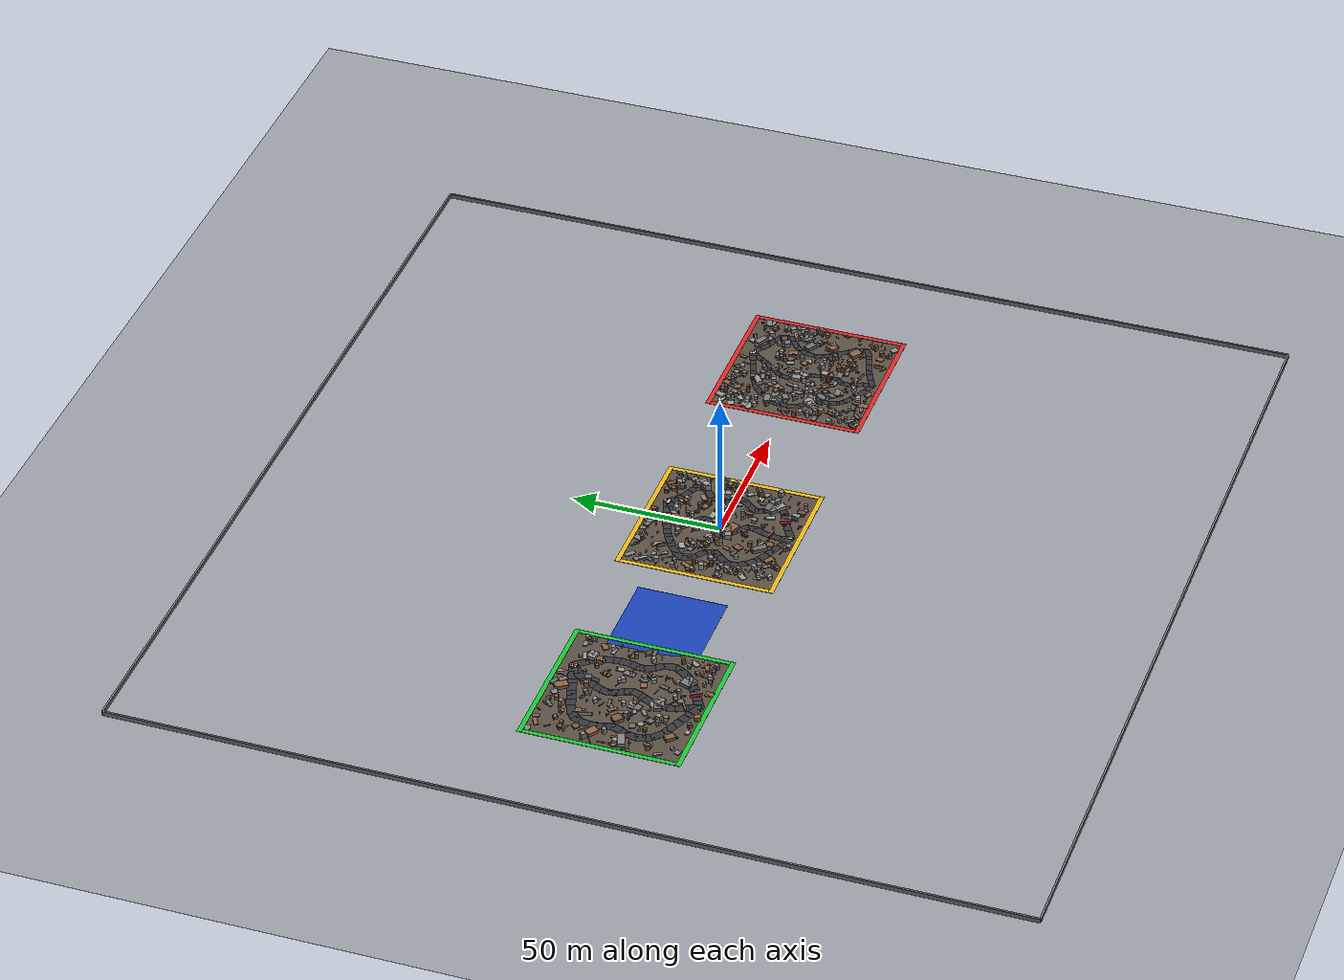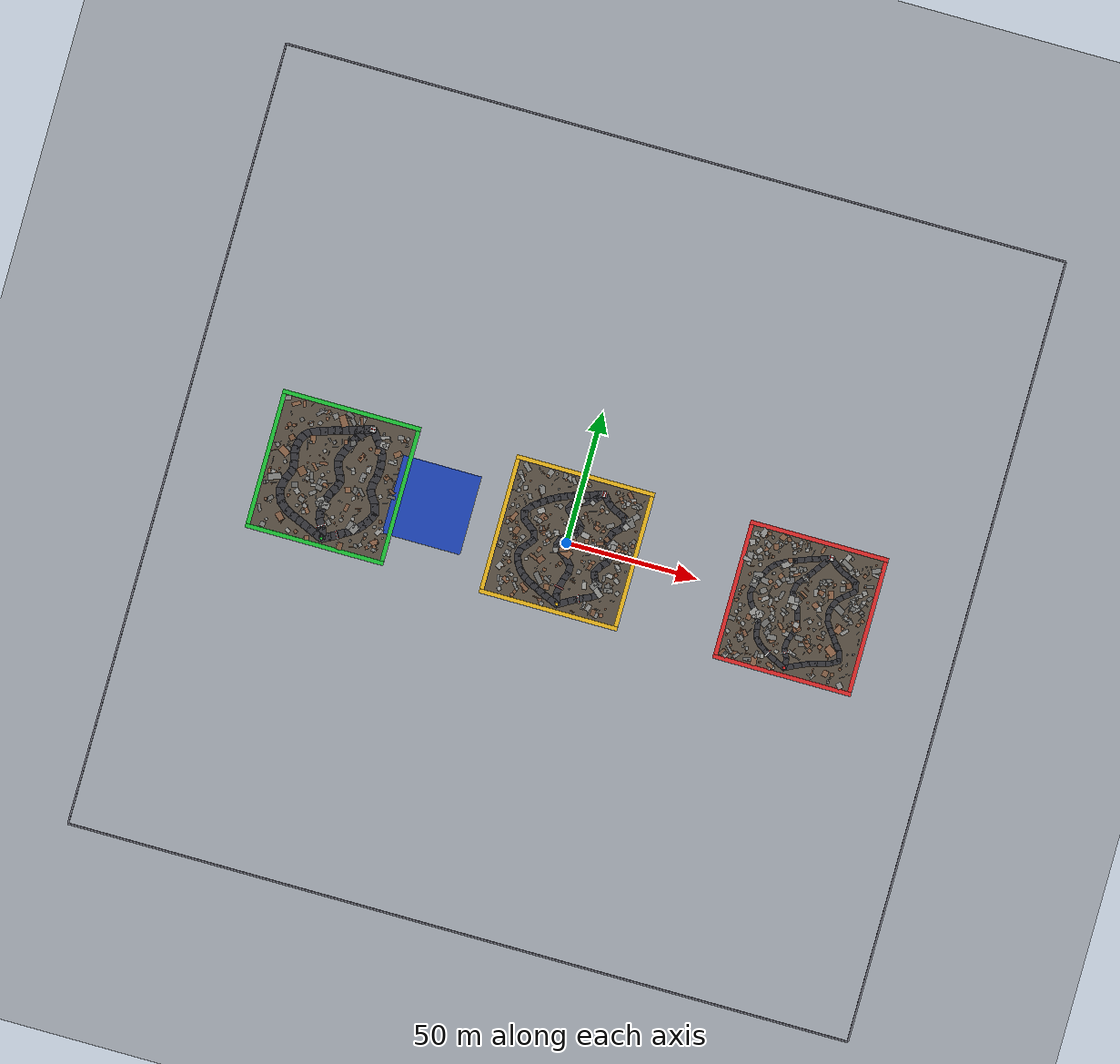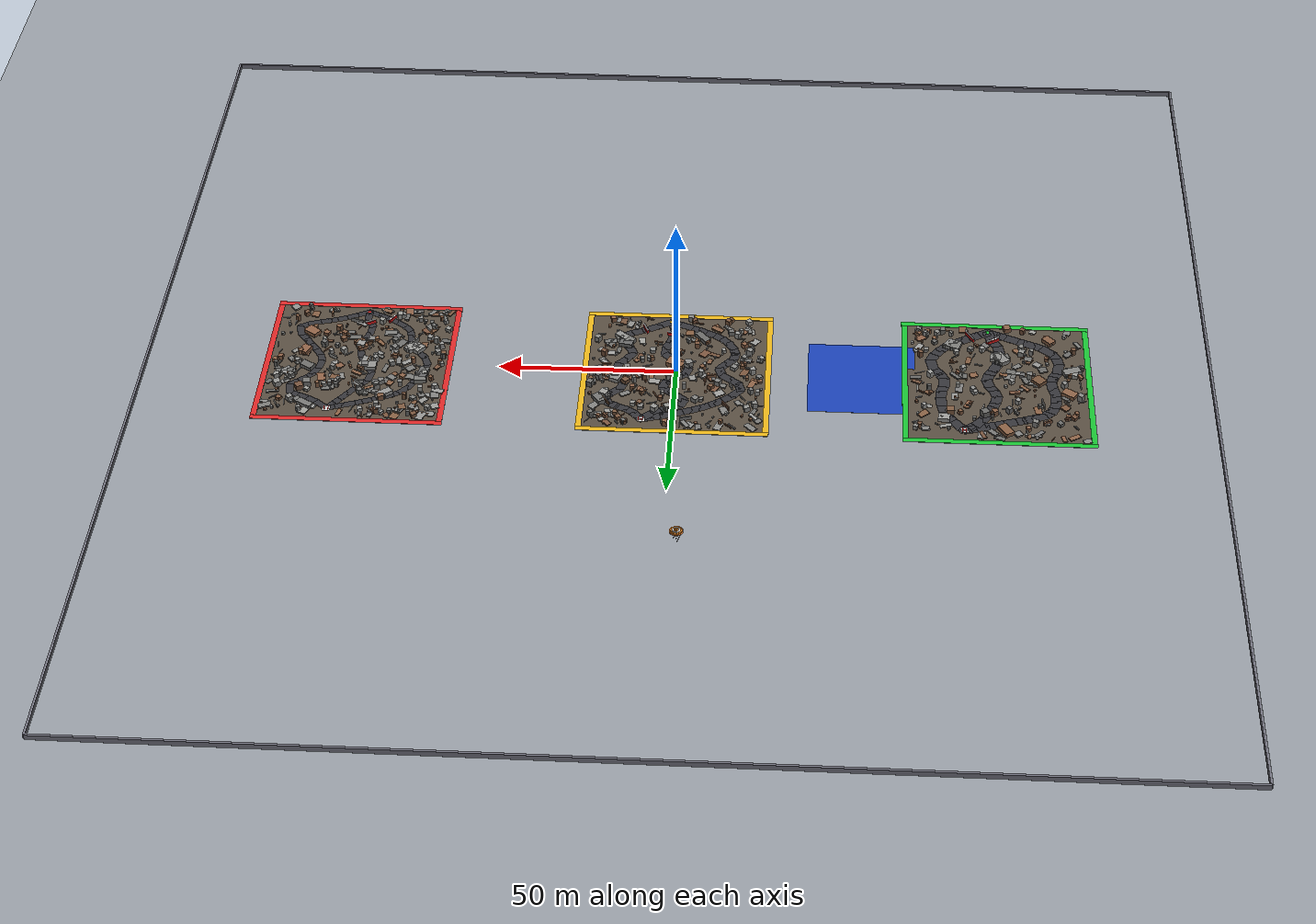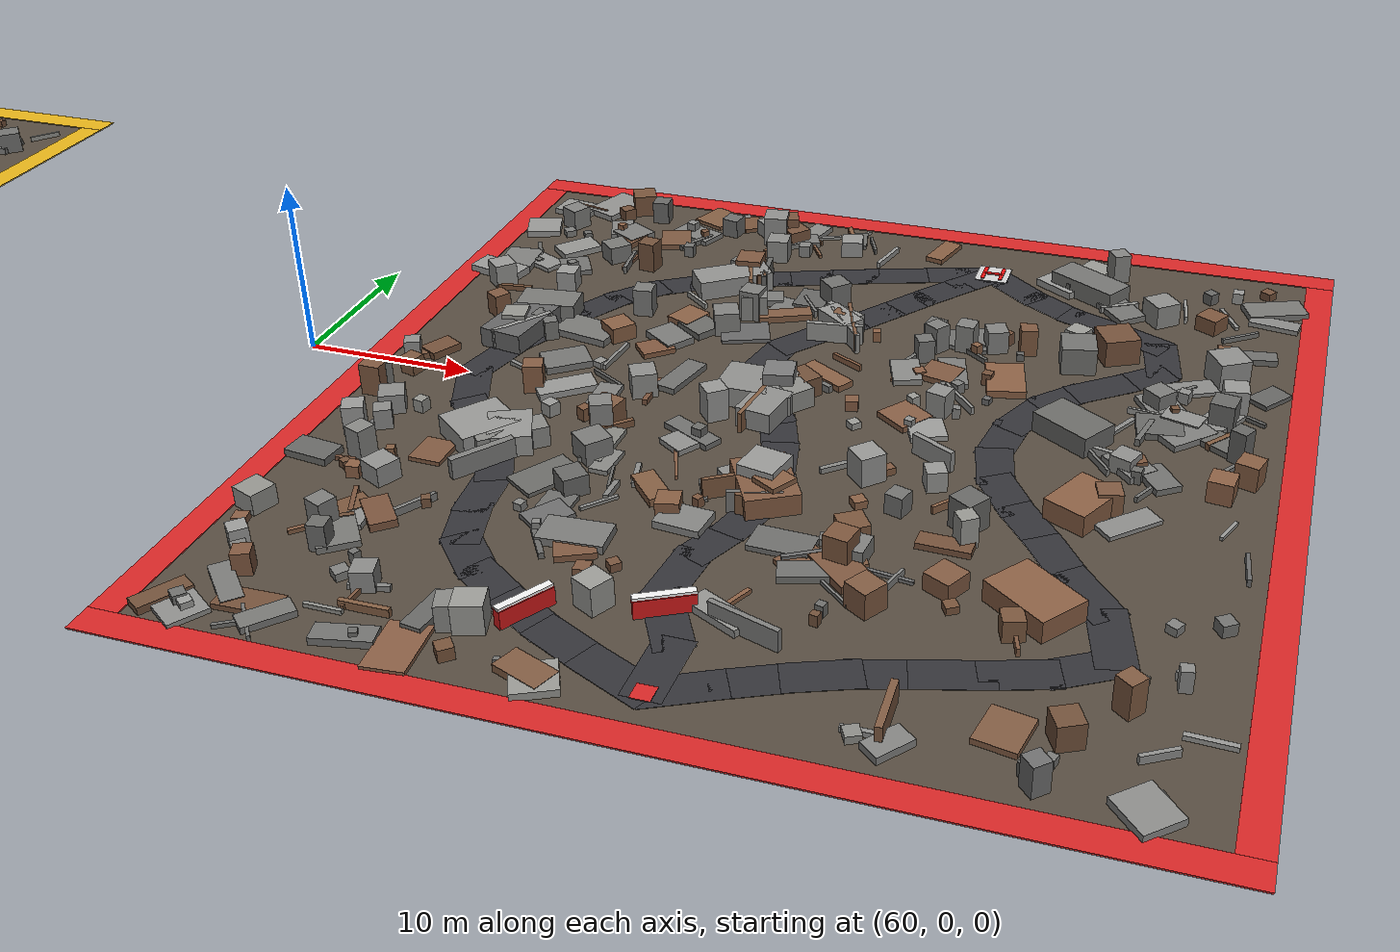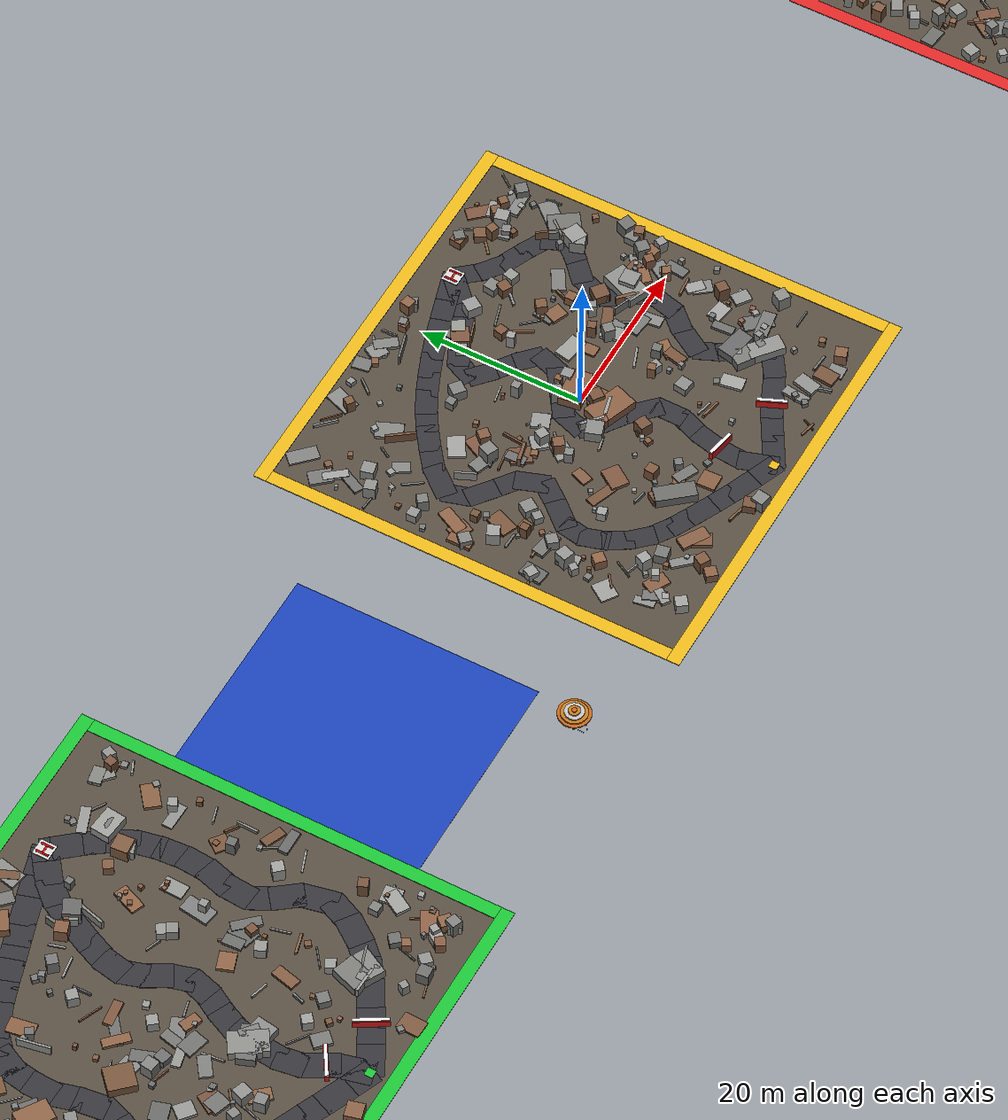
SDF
<sdf version="1.6">
 <world name="navitas_arena">
  <physics type="ode">
   <max_step_size>0.001</max_step_size>
   <real_time_factor>1</real_time_factor>
   <gravity>0 0 -9.8</gravity>
  </physics>
  <wind><linear_velocity>1.0000 0.5000 0.0000</linear_velocity></wind>
  <scene>
   <ambient>0.5000 0.5000 0.5000 1.0000</ambient>
   <background>0.7000 0.7500 0.8000 1.0000</background>
   <shadows>false</shadows>
  </scene>
  <light name="sun" type="directional">
   <cast_shadows>false</cast_shadows>
   <pose>0 0 120 0 0 0</pose>
   <diffuse>0.8500 0.8500 0.8000 1.0000</diffuse>
   <specular>0.1 0.1 0.1 1</specular>
   <attenuation>
    <range>1200</range>
    <constant>0.9</constant>
    <linear>0.01</linear>
    <quadratic>0.001</quadratic>
   </attenuation>
   <direction>-0.4000 0.2000 -0.9000</direction>
  </light>
  <model name="ground_plane">
   <static>true</static>
   <link name="link">
    <collision name="collision">
     <geometry><plane><normal>0 0 1</normal><size>400 400</size></plane></geometry>
     <surface><friction><ode><mu>0.800</mu><mu2>0.800</mu2></ode></friction></surface>
    </collision>
    <visual name="visual">
     <cast_shadows>false</cast_shadows>
     <geometry><plane><normal>0 0 1</normal><size>400 400</size></plane></geometry>
     <material><ambient>0.300 0.290 0.270 1</ambient><diffuse>0.300 0.290 0.270 1</diffuse></material>
    </visual>
   </link>
  </model>
  <model name="ub_N">
   <static>true</static>
   <pose>0.000 150.000 0.750 0 0 0.000</pose>
   <link name="link">
    <collision name="col"><geometry><box><size>300.000 0.600 1.500</size></box></geometry></collision>
    <visual name="vis">
     <geometry><box><size>300.000 0.600 1.500</size></box></geometry>
     <material><ambient>0.45 0.45 0.50 1</ambient><diffuse>0.45 0.45 0.50 1</diffuse></material>
    </visual>
   </link>
  </model>
  <model name="ub_S">
   <static>true</static>
   <pose>0.000 -150.000 0.750 0 0 0.000</pose>
   <link name="link">
    <collision name="col"><geometry><box><size>300.000 0.600 1.500</size></box></geometry></collision>
    <visual name="vis">
     <geometry><box><size>300.000 0.600 1.500</size></box></geometry>
     <material><ambient>0.45 0.45 0.50 1</ambient><diffuse>0.45 0.45 0.50 1</diffuse></material>
    </visual>
   </link>
  </model>
  <model name="ub_W">
   <static>true</static>
   <pose>-150.000 0.000 0.750 0 0 0.000</pose>
   <link name="link">
    <collision name="col"><geometry><box><size>0.600 300.000 1.500</size></box></geometry></collision>
    <visual name="vis">
     <geometry><box><size>0.600 300.000 1.500</size></box></geometry>
     <material><ambient>0.45 0.45 0.50 1</ambient><diffuse>0.45 0.45 0.50 1</diffuse></material>
    </visual>
   </link>
  </model>
  <model name="ub_E">
   <static>true</static>
   <pose>150.000 0.000 0.750 0 0 0.000</pose>
   <link name="link">
    <collision name="col"><geometry><box><size>0.600 300.000 1.500</size></box></geometry></collision>
    <visual name="vis">
     <geometry><box><size>0.600 300.000 1.500</size></box></geometry>
     <material><ambient>0.45 0.45 0.50 1</ambient><diffuse>0.45 0.45 0.50 1</diffuse></material>
    </visual>
   </link>
  </model>
  <model name="landing">
   <static>true</static>
   <pose>-52.000 0.000 0.010 0 0 0.000</pose>
   <link name="link">
    <collision name="col"><geometry><box><size>30.000 30.000 0.020</size></box></geometry></collision>
    <visual name="vis">
     <geometry><box><size>30.000 30.000 0.020</size></box></geometry>
     <material><ambient>0.10 0.25 0.70 1</ambient><diffuse>0.10 0.25 0.70 1</diffuse></material>
    </visual>
   </link>
  </model>
  <model name="gd_kolay">
   <static>true</static>
   <pose>-90.000 0.000 0.010 0 0 0.000</pose>
   <link name="link">
    <collision name="col"><geometry><box><size>50.000 50.000 0.020</size></box></geometry></collision>
    <visual name="vis">
     <geometry><box><size>50.000 50.000 0.020</size></box></geometry>
     <material><ambient>0.34 0.30 0.25 1</ambient><diffuse>0.34 0.30 0.25 1</diffuse></material>
    </visual>
   </link>
  </model>
  <model name="brd_kolay_N">
   <static>true</static>
   <pose>-90.000 25.800 0.040 0 0 0.000</pose>
   <link name="link">
    <collision name="col"><geometry><box><size>53.200 1.600 0.080</size></box></geometry></collision>
    <visual name="vis">
     <geometry><box><size>53.200 1.600 0.080</size></box></geometry>
     <material><ambient>0.10 0.75 0.20 1</ambient><diffuse>0.10 0.75 0.20 1</diffuse></material>
    </visual>
   </link>
  </model>
  <model name="brd_kolay_S">
   <static>true</static>
   <pose>-90.000 -25.800 0.040 0 0 0.000</pose>
   <link name="link">
    <collision name="col"><geometry><box><size>53.200 1.600 0.080</size></box></geometry></collision>
    <visual name="vis">
     <geometry><box><size>53.200 1.600 0.080</size></box></geometry>
     <material><ambient>0.10 0.75 0.20 1</ambient><diffuse>0.10 0.75 0.20 1</diffuse></material>
    </visual>
   </link>
  </model>
  <model name="brd_kolay_W">
   <static>true</static>
   <pose>-115.800 0.000 0.040 0 0 0.000</pose>
   <link name="link">
    <collision name="col"><geometry><box><size>1.600 50.000 0.080</size></box></geometry></collision>
    <visual name="vis">
     <geometry><box><size>1.600 50.000 0.080</size></box></geometry>
     <material><ambient>0.10 0.75 0.20 1</ambient><diffuse>0.10 0.75 0.20 1</diffuse></material>
    </visual>
   </link>
  </model>
  <model name="brd_kolay_E">
   <static>true</static>
   <pose>-64.200 0.000 0.040 0 0 0.000</pose>
   <link name="link">
    <collision name="col"><geometry><box><size>1.600 50.000 0.080</size></box></geometry></collision>
    <visual name="vis">
     <geometry><box><size>1.600 50.000 0.080</size></box></geometry>
     <material><ambient>0.10 0.75 0.20 1</ambient><diffuse>0.10 0.75 0.20 1</diffuse></material>
    </visual>
   </link>
  </model>
  <model name="road_kolay_1_0">
   <static>true</static>
   <pose>-89.499 -22.399 0.040 0 0 2.741</pose>
   <link name="link">
    <collision name="col"><geometry><box><size>3.985 3.000 0.020</size></box></geometry></collision>
    <visual name="vis">
     <geometry><box><size>3.985 3.000 0.020</size></box></geometry>
     <material><ambient>0.20 0.20 0.22 1</ambient><diffuse>0.20 0.20 0.22 1</diffuse></material>
    </visual>
   </link>
  </model>
  <model name="road_kolay_1_1">
   <static>true</static>
   <pose>-92.226 -21.236 0.040 0 0 2.736</pose>
   <link name="link">
    <collision name="col"><geometry><box><size>3.744 3.000 0.020</size></box></geometry></collision>
    <visual name="vis">
     <geometry><box><size>3.744 3.000 0.020</size></box></geometry>
     <material><ambient>0.20 0.20 0.22 1</ambient><diffuse>0.20 0.20 0.22 1</diffuse></material>
    </visual>
   </link>
  </model>
  <model name="road_kolay_1_2">
   <static>true</static>
   <pose>-94.838 -20.087 0.040 0 0 2.719</pose>
   <link name="link">
    <collision name="col"><geometry><box><size>3.762 3.000 0.020</size></box></geometry></collision>
    <visual name="vis">
     <geometry><box><size>3.762 3.000 0.020</size></box></geometry>
     <material><ambient>0.20 0.20 0.22 1</ambient><diffuse>0.20 0.20 0.22 1</diffuse></material>
    </visual>
   </link>
  </model>
  <model name="road_kolay_1_3">
   <static>true</static>
   <pose>-97.314 -19.002 0.040 0 0 2.739</pose>
   <link name="link">
    <collision name="col"><geometry><box><size>3.445 3.000 0.020</size></box></geometry></collision>
    <visual name="vis">
     <geometry><box><size>3.445 3.000 0.020</size></box></geometry>
     <material><ambient>0.20 0.20 0.22 1</ambient><diffuse>0.20 0.20 0.22 1</diffuse></material>
    </visual>
   </link>
  </model>
  <model name="road_kolay_1_4">
   <static>true</static>
   <pose>-99.745 -17.986 0.040 0 0 2.752</pose>
   <link name="link">
    <collision name="col"><geometry><box><size>3.623 3.000 0.020</size></box></geometry></collision>
    <visual name="vis">
     <geometry><box><size>3.623 3.000 0.020</size></box></geometry>
     <material><ambient>0.20 0.20 0.22 1</ambient><diffuse>0.20 0.20 0.22 1</diffuse></material>
    </visual>
   </link>
  </model>
  <model name="road_kolay_1_5">
   <static>true</static>
   <pose>-102.178 -16.896 0.040 0 0 2.688</pose>
   <link name="link">
    <collision name="col"><geometry><box><size>3.512 3.000 0.020</size></box></geometry></collision>
    <visual name="vis">
     <geometry><box><size>3.512 3.000 0.020</size></box></geometry>
     <material><ambient>0.20 0.20 0.22 1</ambient><diffuse>0.20 0.20 0.22 1</diffuse></material>
    </visual>
   </link>
  </model>
  <model name="road_kolay_1_6">
   <static>true</static>
   <pose>-104.698 -15.151 0.040 0 0 2.425</pose>
   <link name="link">
    <collision name="col"><geometry><box><size>4.472 3.000 0.020</size></box></geometry></collision>
    <visual name="vis">
     <geometry><box><size>4.472 3.000 0.020</size></box></geometry>
     <material><ambient>0.20 0.20 0.22 1</ambient><diffuse>0.20 0.20 0.22 1</diffuse></material>
    </visual>
   </link>
  </model>
  <model name="road_kolay_1_7">
   <static>true</static>
   <pose>-106.624 -12.817 0.040 0 0 2.034</pose>
   <link name="link">
    <collision name="col"><geometry><box><size>3.495 3.000 0.020</size></box></geometry></collision>
    <visual name="vis">
     <geometry><box><size>3.495 3.000 0.020</size></box></geometry>
     <material><ambient>0.20 0.20 0.22 1</ambient><diffuse>0.20 0.20 0.22 1</diffuse></material>
    </visual>
   </link>
  </model>
  <model name="road_kolay_1_8">
   <static>true</static>
   <pose>-107.458 -10.426 0.040 0 0 1.775</pose>
   <link name="link">
    <collision name="col"><geometry><box><size>3.413 3.000 0.020</size></box></geometry></collision>
    <visual name="vis">
     <geometry><box><size>3.413 3.000 0.020</size></box></geometry>
     <material><ambient>0.20 0.20 0.22 1</ambient><diffuse>0.20 0.20 0.22 1</diffuse></material>
    </visual>
   </link>
  </model>
  <model name="road_kolay_1_9">
   <static>true</static>
   <pose>-107.424 -7.431 0.040 0 0 1.408</pose>
   <link name="link">
    <collision name="col"><geometry><box><size>4.476 3.000 0.020</size></box></geometry></collision>
    <visual name="vis">
     <geometry><box><size>4.476 3.000 0.020</size></box></geometry>
     <material><ambient>0.20 0.20 0.22 1</ambient><diffuse>0.20 0.20 0.22 1</diffuse></material>
    </visual>
   </link>
  </model>
  <model name="road_kolay_1_10">
   <static>true</static>
   <pose>-106.527 -4.500 0.040 0 0 1.091</pose>
   <link name="link">
    <collision name="col"><geometry><box><size>3.530 3.000 0.020</size></box></geometry></collision>
    <visual name="vis">
     <geometry><box><size>3.530 3.000 0.020</size></box></geometry>
     <material><ambient>0.20 0.20 0.22 1</ambient><diffuse>0.20 0.20 0.22 1</diffuse></material>
    </visual>
   </link>
  </model>
  <model name="road_kolay_1_11">
   <static>true</static>
   <pose>-105.526 -2.167 0.040 0 0 1.244</pose>
   <link name="link">
    <collision name="col"><geometry><box><size>3.363 3.000 0.020</size></box></geometry></collision>
    <visual name="vis">
     <geometry><box><size>3.363 3.000 0.020</size></box></geometry>
     <material><ambient>0.20 0.20 0.22 1</ambient><diffuse>0.20 0.20 0.22 1</diffuse></material>
    </visual>
   </link>
  </model>
  <model name="road_kolay_1_12">
   <static>true</static>
   <pose>-105.322 0.400 0.040 0 0 1.706</pose>
   <link name="link">
    <collision name="col"><geometry><box><size>3.726 3.000 0.020</size></box></geometry></collision>
    <visual name="vis">
     <geometry><box><size>3.726 3.000 0.020</size></box></geometry>
     <material><ambient>0.20 0.20 0.22 1</ambient><diffuse>0.20 0.20 0.22 1</diffuse></material>
    </visual>
   </link>
  </model>
  <model name="road_kolay_1_13">
   <static>true</static>
   <pose>-105.885 3.200 0.040 0 0 1.831</pose>
   <link name="link">
    <collision name="col"><geometry><box><size>3.798 3.000 0.020</size></box></geometry></collision>
    <visual name="vis">
     <geometry><box><size>3.798 3.000 0.020</size></box></geometry>
     <material><ambient>0.20 0.20 0.22 1</ambient><diffuse>0.20 0.20 0.22 1</diffuse></material>
    </visual>
   </link>
  </model>
  <model name="road_kolay_1_14">
   <static>true</static>
   <pose>-106.227 5.898 0.040 0 0 1.546</pose>
   <link name="link">
    <collision name="col"><geometry><box><size>3.496 3.000 0.020</size></box></geometry></collision>
    <visual name="vis">
     <geometry><box><size>3.496 3.000 0.020</size></box></geometry>
     <material><ambient>0.20 0.20 0.22 1</ambient><diffuse>0.20 0.20 0.22 1</diffuse></material>
    </visual>
   </link>
  </model>
  <model name="road_kolay_1_15">
   <static>true</static>
   <pose>-105.991 8.426 0.040 0 0 1.407</pose>
   <link name="link">
    <collision name="col"><geometry><box><size>3.394 3.000 0.020</size></box></geometry></collision>
    <visual name="vis">
     <geometry><box><size>3.394 3.000 0.020</size></box></geometry>
     <material><ambient>0.20 0.20 0.22 1</ambient><diffuse>0.20 0.20 0.22 1</diffuse></material>
    </visual>
   </link>
  </model>
  <model name="road_kolay_1_16">
   <static>true</static>
   <pose>-105.227 10.817 0.040 0 0 1.121</pose>
   <link name="link">
    <collision name="col"><geometry><box><size>3.479 3.000 0.020</size></box></geometry></collision>
    <visual name="vis">
     <geometry><box><size>3.479 3.000 0.020</size></box></geometry>
     <material><ambient>0.20 0.20 0.22 1</ambient><diffuse>0.20 0.20 0.22 1</diffuse></material>
    </visual>
   </link>
  </model>
  <model name="road_kolay_1_17">
   <static>true</static>
   <pose>-103.758 12.767 0.040 0 0 0.715</pose>
   <link name="link">
    <collision name="col"><geometry><box><size>3.306 3.000 0.020</size></box></geometry></collision>
    <visual name="vis">
     <geometry><box><size>3.306 3.000 0.020</size></box></geometry>
     <material><ambient>0.20 0.20 0.22 1</ambient><diffuse>0.20 0.20 0.22 1</diffuse></material>
    </visual>
   </link>
  </model>
  <model name="road_kolay_1_18">
   <static>true</static>
   <pose>-101.231 14.292 0.040 0 0 0.427</pose>
   <link name="link">
    <collision name="col"><geometry><box><size>4.456 3.000 0.020</size></box></geometry></collision>
    <visual name="vis">
     <geometry><box><size>4.456 3.000 0.020</size></box></geometry>
     <material><ambient>0.20 0.20 0.22 1</ambient><diffuse>0.20 0.20 0.22 1</diffuse></material>
    </visual>
   </link>
  </model>
  <model name="road_kolay_1_19">
   <static>true</static>
   <pose>-98.331 15.460 0.040 0 0 0.325</pose>
   <link name="link">
    <collision name="col"><geometry><box><size>3.606 3.000 0.020</size></box></geometry></collision>
    <visual name="vis">
     <geometry><box><size>3.606 3.000 0.020</size></box></geometry>
     <material><ambient>0.20 0.20 0.22 1</ambient><diffuse>0.20 0.20 0.22 1</diffuse></material>
    </visual>
   </link>
  </model>
  <model name="road_kolay_1_20">
   <static>true</static>
   <pose>-95.734 16.298 0.040 0 0 0.299</pose>
   <link name="link">
    <collision name="col"><geometry><box><size>3.652 3.000 0.020</size></box></geometry></collision>
    <visual name="vis">
     <geometry><box><size>3.652 3.000 0.020</size></box></geometry>
     <material><ambient>0.20 0.20 0.22 1</ambient><diffuse>0.20 0.20 0.22 1</diffuse></material>
    </visual>
   </link>
  </model>
  <model name="road_kolay_1_21">
   <static>true</static>
   <pose>-93.182 17.102 0.040 0 0 0.311</pose>
   <link name="link">
    <collision name="col"><geometry><box><size>3.498 3.000 0.020</size></box></geometry></collision>
    <visual name="vis">
     <geometry><box><size>3.498 3.000 0.020</size></box></geometry>
     <material><ambient>0.20 0.20 0.22 1</ambient><diffuse>0.20 0.20 0.22 1</diffuse></material>
    </visual>
   </link>
  </model>
  <model name="road_kolay_1_22">
   <static>true</static>
   <pose>-90.697 17.910 0.040 0 0 0.317</pose>
   <link name="link">
    <collision name="col"><geometry><box><size>3.528 3.000 0.020</size></box></geometry></collision>
    <visual name="vis">
     <geometry><box><size>3.528 3.000 0.020</size></box></geometry>
     <material><ambient>0.20 0.20 0.22 1</ambient><diffuse>0.20 0.20 0.22 1</diffuse></material>
    </visual>
   </link>
  </model>
  <model name="road_kolay_1_23">
   <static>true</static>
   <pose>-88.113 18.730 0.040 0 0 0.298</pose>
   <link name="link">
    <collision name="col"><geometry><box><size>3.693 3.000 0.020</size></box></geometry></collision>
    <visual name="vis">
     <geometry><box><size>3.693 3.000 0.020</size></box></geometry>
     <material><ambient>0.20 0.20 0.22 1</ambient><diffuse>0.20 0.20 0.22 1</diffuse></material>
    </visual>
   </link>
  </model>
  <model name="road_kolay_1_24">
   <static>true</static>
   <pose>-85.493 19.520 0.040 0 0 0.287</pose>
   <link name="link">
    <collision name="col"><geometry><box><size>3.581 3.000 0.020</size></box></geometry></collision>
    <visual name="vis">
     <geometry><box><size>3.581 3.000 0.020</size></box></geometry>
     <material><ambient>0.20 0.20 0.22 1</ambient><diffuse>0.20 0.20 0.22 1</diffuse></material>
    </visual>
   </link>
  </model>
  <model name="road_kolay_1_25">
   <static>true</static>
   <pose>-82.669 20.348 0.040 0 0 0.283</pose>
   <link name="link">
    <collision name="col"><geometry><box><size>4.106 3.000 0.020</size></box></geometry></collision>
    <visual name="vis">
     <geometry><box><size>4.106 3.000 0.020</size></box></geometry>
     <material><ambient>0.20 0.20 0.22 1</ambient><diffuse>0.20 0.20 0.22 1</diffuse></material>
    </visual>
   </link>
  </model>
  <model name="road_kolay_1_26">
   <static>true</static>
   <pose>-80.788 20.898 0.040 0 0 0.290</pose>
   <link name="link">
    <collision name="col"><geometry><box><size>1.613 3.000 0.020</size></box></geometry></collision>
    <visual name="vis">
     <geometry><box><size>1.613 3.000 0.020</size></box></geometry>
     <material><ambient>0.20 0.20 0.22 1</ambient><diffuse>0.20 0.20 0.22 1</diffuse></material>
    </visual>
   </link>
  </model>
  <model name="road_kolay_2_0">
   <static>true</static>
   <pose>-88.511 -21.250 0.040 0 0 1.813</pose>
   <link name="link">
    <collision name="col"><geometry><box><size>4.505 3.000 0.020</size></box></geometry></collision>
    <visual name="vis">
     <geometry><box><size>4.505 3.000 0.020</size></box></geometry>
     <material><ambient>0.20 0.20 0.22 1</ambient><diffuse>0.20 0.20 0.22 1</diffuse></material>
    </visual>
   </link>
  </model>
  <model name="road_kolay_2_1">
   <static>true</static>
   <pose>-89.820 -17.912 0.040 0 0 2.075</pose>
   <link name="link">
    <collision name="col"><geometry><box><size>4.528 3.000 0.020</size></box></geometry></collision>
    <visual name="vis">
     <geometry><box><size>4.528 3.000 0.020</size></box></geometry>
     <material><ambient>0.20 0.20 0.22 1</ambient><diffuse>0.20 0.20 0.22 1</diffuse></material>
    </visual>
   </link>
  </model>
  <model name="road_kolay_2_2">
   <static>true</static>
   <pose>-90.896 -15.042 0.040 0 0 1.725</pose>
   <link name="link">
    <collision name="col"><geometry><box><size>3.495 3.000 0.020</size></box></geometry></collision>
    <visual name="vis">
     <geometry><box><size>3.495 3.000 0.020</size></box></geometry>
     <material><ambient>0.20 0.20 0.22 1</ambient><diffuse>0.20 0.20 0.22 1</diffuse></material>
    </visual>
   </link>
  </model>
  <model name="road_kolay_2_3">
   <static>true</static>
   <pose>-90.962 -12.340 0.040 0 0 1.477</pose>
   <link name="link">
    <collision name="col"><geometry><box><size>3.753 3.000 0.020</size></box></geometry></collision>
    <visual name="vis">
     <geometry><box><size>3.753 3.000 0.020</size></box></geometry>
     <material><ambient>0.20 0.20 0.22 1</ambient><diffuse>0.20 0.20 0.22 1</diffuse></material>
    </visual>
   </link>
  </model>
  <model name="road_kolay_2_4">
   <static>true</static>
   <pose>-90.505 -9.460 0.040 0 0 1.353</pose>
   <link name="link">
    <collision name="col"><geometry><box><size>3.891 3.000 0.020</size></box></geometry></collision>
    <visual name="vis">
     <geometry><box><size>3.891 3.000 0.020</size></box></geometry>
     <material><ambient>0.20 0.20 0.22 1</ambient><diffuse>0.20 0.20 0.22 1</diffuse></material>
    </visual>
   </link>
  </model>
  <model name="road_kolay_2_5">
   <static>true</static>
   <pose>-89.645 -6.833 0.040 0 0 1.139</pose>
   <link name="link">
    <collision name="col"><geometry><box><size>3.469 3.000 0.020</size></box></geometry></collision>
    <visual name="vis">
     <geometry><box><size>3.469 3.000 0.020</size></box></geometry>
     <material><ambient>0.20 0.20 0.22 1</ambient><diffuse>0.20 0.20 0.22 1</diffuse></material>
    </visual>
   </link>
  </model>
  <model name="road_kolay_2_6">
   <static>true</static>
   <pose>-88.447 -4.500 0.040 0 0 1.056</pose>
   <link name="link">
    <collision name="col"><geometry><box><size>3.581 3.000 0.020</size></box></geometry></collision>
    <visual name="vis">
     <geometry><box><size>3.581 3.000 0.020</size></box></geometry>
     <material><ambient>0.20 0.20 0.22 1</ambient><diffuse>0.20 0.20 0.22 1</diffuse></material>
    </visual>
   </link>
  </model>
  <model name="road_kolay_2_7">
   <static>true</static>
   <pose>-87.449 -2.167 0.040 0 0 1.288</pose>
   <link name="link">
    <collision name="col"><geometry><box><size>3.330 3.000 0.020</size></box></geometry></collision>
    <visual name="vis">
     <geometry><box><size>3.330 3.000 0.020</size></box></geometry>
     <material><ambient>0.20 0.20 0.22 1</ambient><diffuse>0.20 0.20 0.22 1</diffuse></material>
    </visual>
   </link>
  </model>
  <model name="road_kolay_2_8">
   <static>true</static>
   <pose>-87.446 0.167 0.040 0 0 1.851</pose>
   <link name="link">
    <collision name="col"><geometry><box><size>3.328 3.000 0.020</size></box></geometry></collision>
    <visual name="vis">
     <geometry><box><size>3.328 3.000 0.020</size></box></geometry>
     <material><ambient>0.20 0.20 0.22 1</ambient><diffuse>0.20 0.20 0.22 1</diffuse></material>
    </visual>
   </link>
  </model>
  <model name="road_kolay_2_9">
   <static>true</static>
   <pose>-88.438 2.500 0.040 0 0 2.084</pose>
   <link name="link">
    <collision name="col"><geometry><box><size>3.578 3.000 0.020</size></box></geometry></collision>
    <visual name="vis">
     <geometry><box><size>3.578 3.000 0.020</size></box></geometry>
     <material><ambient>0.20 0.20 0.22 1</ambient><diffuse>0.20 0.20 0.22 1</diffuse></material>
    </visual>
   </link>
  </model>
  <model name="road_kolay_2_10">
   <static>true</static>
   <pose>-89.461 4.833 0.040 0 0 1.875</pose>
   <link name="link">
    <collision name="col"><geometry><box><size>3.345 3.000 0.020</size></box></geometry></collision>
    <visual name="vis">
     <geometry><box><size>3.345 3.000 0.020</size></box></geometry>
     <material><ambient>0.20 0.20 0.22 1</ambient><diffuse>0.20 0.20 0.22 1</diffuse></material>
    </visual>
   </link>
  </model>
  <model name="road_kolay_2_11">
   <static>true</static>
   <pose>-89.602 7.213 0.040 0 0 1.387</pose>
   <link name="link">
    <collision name="col"><geometry><box><size>3.367 3.000 0.020</size></box></geometry></collision>
    <visual name="vis">
     <geometry><box><size>3.367 3.000 0.020</size></box></geometry>
     <material><ambient>0.20 0.20 0.22 1</ambient><diffuse>0.20 0.20 0.22 1</diffuse></material>
    </visual>
   </link>
  </model>
  <model name="road_kolay_2_12">
   <static>true</static>
   <pose>-88.860 9.639 0.040 0 0 1.168</pose>
   <link name="link">
    <collision name="col"><geometry><box><size>3.537 3.000 0.020</size></box></geometry></collision>
    <visual name="vis">
     <geometry><box><size>3.537 3.000 0.020</size></box></geometry>
     <material><ambient>0.20 0.20 0.22 1</ambient><diffuse>0.20 0.20 0.22 1</diffuse></material>
    </visual>
   </link>
  </model>
  <model name="road_kolay_2_13">
   <static>true</static>
   <pose>-87.527 12.588 0.040 0 0 1.131</pose>
   <link name="link">
    <collision name="col"><geometry><box><size>4.738 3.000 0.020</size></box></geometry></collision>
    <visual name="vis">
     <geometry><box><size>4.738 3.000 0.020</size></box></geometry>
     <material><ambient>0.20 0.20 0.22 1</ambient><diffuse>0.20 0.20 0.22 1</diffuse></material>
    </visual>
   </link>
  </model>
  <model name="road_kolay_2_14">
   <static>true</static>
   <pose>-86.109 15.414 0.040 0 0 1.067</pose>
   <link name="link">
    <collision name="col"><geometry><box><size>3.389 3.000 0.020</size></box></geometry></collision>
    <visual name="vis">
     <geometry><box><size>3.389 3.000 0.020</size></box></geometry>
     <material><ambient>0.20 0.20 0.22 1</ambient><diffuse>0.20 0.20 0.22 1</diffuse></material>
    </visual>
   </link>
  </model>
  <model name="road_kolay_2_15">
   <static>true</static>
   <pose>-84.601 17.516 0.040 0 0 0.839</pose>
   <link name="link">
    <collision name="col"><geometry><box><size>3.619 3.000 0.020</size></box></geometry></collision>
    <visual name="vis">
     <geometry><box><size>3.619 3.000 0.020</size></box></geometry>
     <material><ambient>0.20 0.20 0.22 1</ambient><diffuse>0.20 0.20 0.22 1</diffuse></material>
    </visual>
   </link>
  </model>
  <model name="road_kolay_2_16">
   <static>true</static>
   <pose>-82.476 19.461 0.040 0 0 0.655</pose>
   <link name="link">
    <collision name="col"><geometry><box><size>3.967 3.000 0.020</size></box></geometry></collision>
    <visual name="vis">
     <geometry><box><size>3.967 3.000 0.020</size></box></geometry>
     <material><ambient>0.20 0.20 0.22 1</ambient><diffuse>0.20 0.20 0.22 1</diffuse></material>
    </visual>
   </link>
  </model>
  <model name="road_kolay_2_17">
   <static>true</static>
   <pose>-80.853 20.697 0.040 0 0 0.640</pose>
   <link name="link">
    <collision name="col"><geometry><box><size>1.914 3.000 0.020</size></box></geometry></collision>
    <visual name="vis">
     <geometry><box><size>1.914 3.000 0.020</size></box></geometry>
     <material><ambient>0.20 0.20 0.22 1</ambient><diffuse>0.20 0.20 0.22 1</diffuse></material>
    </visual>
   </link>
  </model>
  <model name="road_kolay_3_0">
   <static>true</static>
   <pose>-86.699 -22.266 0.040 0 0 0.489</pose>
   <link name="link">
    <collision name="col"><geometry><box><size>4.026 3.000 0.020</size></box></geometry></collision>
    <visual name="vis">
     <geometry><box><size>4.026 3.000 0.020</size></box></geometry>
     <material><ambient>0.20 0.20 0.22 1</ambient><diffuse>0.20 0.20 0.22 1</diffuse></material>
    </visual>
   </link>
  </model>
  <model name="road_kolay_3_1">
   <static>true</static>
   <pose>-84.101 -20.856 0.040 0 0 0.506</pose>
   <link name="link">
    <collision name="col"><geometry><box><size>3.684 3.000 0.020</size></box></geometry></collision>
    <visual name="vis">
     <geometry><box><size>3.684 3.000 0.020</size></box></geometry>
     <material><ambient>0.20 0.20 0.22 1</ambient><diffuse>0.20 0.20 0.22 1</diffuse></material>
    </visual>
   </link>
  </model>
  <model name="road_kolay_3_2">
   <static>true</static>
   <pose>-81.759 -19.509 0.040 0 0 0.539</pose>
   <link name="link">
    <collision name="col"><geometry><box><size>3.521 3.000 0.020</size></box></geometry></collision>
    <visual name="vis">
     <geometry><box><size>3.521 3.000 0.020</size></box></geometry>
     <material><ambient>0.20 0.20 0.22 1</ambient><diffuse>0.20 0.20 0.22 1</diffuse></material>
    </visual>
   </link>
  </model>
  <model name="road_kolay_3_3">
   <static>true</static>
   <pose>-79.477 -18.153 0.040 0 0 0.534</pose>
   <link name="link">
    <collision name="col"><geometry><box><size>3.588 3.000 0.020</size></box></geometry></collision>
    <visual name="vis">
     <geometry><box><size>3.588 3.000 0.020</size></box></geometry>
     <material><ambient>0.20 0.20 0.22 1</ambient><diffuse>0.20 0.20 0.22 1</diffuse></material>
    </visual>
   </link>
  </model>
  <model name="road_kolay_3_4">
   <static>true</static>
   <pose>-77.232 -16.688 0.040 0 0 0.623</pose>
   <link name="link">
    <collision name="col"><geometry><box><size>3.579 3.000 0.020</size></box></geometry></collision>
    <visual name="vis">
     <geometry><box><size>3.579 3.000 0.020</size></box></geometry>
     <material><ambient>0.20 0.20 0.22 1</ambient><diffuse>0.20 0.20 0.22 1</diffuse></material>
    </visual>
   </link>
  </model>
  <model name="road_kolay_3_5">
   <static>true</static>
   <pose>-75.233 -14.942 0.040 0 0 0.813</pose>
   <link name="link">
    <collision name="col"><geometry><box><size>3.554 3.000 0.020</size></box></geometry></collision>
    <visual name="vis">
     <geometry><box><size>3.554 3.000 0.020</size></box></geometry>
     <material><ambient>0.20 0.20 0.22 1</ambient><diffuse>0.20 0.20 0.22 1</diffuse></material>
    </visual>
   </link>
  </model>
  <model name="road_kolay_3_6">
   <static>true</static>
   <pose>-73.475 -12.817 0.040 0 0 0.941</pose>
   <link name="link">
    <collision name="col"><geometry><box><size>3.773 3.000 0.020</size></box></geometry></collision>
    <visual name="vis">
     <geometry><box><size>3.773 3.000 0.020</size></box></geometry>
     <material><ambient>0.20 0.20 0.22 1</ambient><diffuse>0.20 0.20 0.22 1</diffuse></material>
    </visual>
   </link>
  </model>
  <model name="road_kolay_3_7">
   <static>true</static>
   <pose>-72.074 -10.426 0.040 0 0 1.147</pose>
   <link name="link">
    <collision name="col"><geometry><box><size>3.600 3.000 0.020</size></box></geometry></collision>
    <visual name="vis">
     <geometry><box><size>3.600 3.000 0.020</size></box></geometry>
     <material><ambient>0.20 0.20 0.22 1</ambient><diffuse>0.20 0.20 0.22 1</diffuse></material>
    </visual>
   </link>
  </model>
  <model name="road_kolay_3_8">
   <static>true</static>
   <pose>-71.900 -7.431 0.040 0 0 1.784</pose>
   <link name="link">
    <collision name="col"><geometry><box><size>4.511 3.000 0.020</size></box></geometry></collision>
    <visual name="vis">
     <geometry><box><size>4.511 3.000 0.020</size></box></geometry>
     <material><ambient>0.20 0.20 0.22 1</ambient><diffuse>0.20 0.20 0.22 1</diffuse></material>
    </visual>
   </link>
  </model>
  <model name="road_kolay_3_9">
   <static>true</static>
   <pose>-73.177 -4.500 0.040 0 0 2.225</pose>
   <link name="link">
    <collision name="col"><geometry><box><size>3.840 3.000 0.020</size></box></geometry></collision>
    <visual name="vis">
     <geometry><box><size>3.840 3.000 0.020</size></box></geometry>
     <material><ambient>0.20 0.20 0.22 1</ambient><diffuse>0.20 0.20 0.22 1</diffuse></material>
    </visual>
   </link>
  </model>
  <model name="road_kolay_3_10">
   <static>true</static>
   <pose>-74.682 -2.167 0.040 0 0 2.053</pose>
   <link name="link">
    <collision name="col"><geometry><box><size>3.533 3.000 0.020</size></box></geometry></collision>
    <visual name="vis">
     <geometry><box><size>3.533 3.000 0.020</size></box></geometry>
     <material><ambient>0.20 0.20 0.22 1</ambient><diffuse>0.20 0.20 0.22 1</diffuse></material>
    </visual>
   </link>
  </model>
  <model name="road_kolay_3_11">
   <static>true</static>
   <pose>-75.192 0.400 0.040 0 0 1.500</pose>
   <link name="link">
    <collision name="col"><geometry><box><size>3.707 3.000 0.020</size></box></geometry></collision>
    <visual name="vis">
     <geometry><box><size>3.707 3.000 0.020</size></box></geometry>
     <material><ambient>0.20 0.20 0.22 1</ambient><diffuse>0.20 0.20 0.22 1</diffuse></material>
    </visual>
   </link>
  </model>
  <model name="road_kolay_3_12">
   <static>true</static>
   <pose>-74.697 3.200 0.040 0 0 1.295</pose>
   <link name="link">
    <collision name="col"><geometry><box><size>3.810 3.000 0.020</size></box></geometry></collision>
    <visual name="vis">
     <geometry><box><size>3.810 3.000 0.020</size></box></geometry>
     <material><ambient>0.20 0.20 0.22 1</ambient><diffuse>0.20 0.20 0.22 1</diffuse></material>
    </visual>
   </link>
  </model>
  <model name="road_kolay_3_13">
   <static>true</static>
   <pose>-74.203 6.020 0.040 0 0 1.502</pose>
   <link name="link">
    <collision name="col"><geometry><box><size>3.747 3.000 0.020</size></box></geometry></collision>
    <visual name="vis">
     <geometry><box><size>3.747 3.000 0.020</size></box></geometry>
     <material><ambient>0.20 0.20 0.22 1</ambient><diffuse>0.20 0.20 0.22 1</diffuse></material>
    </visual>
   </link>
  </model>
  <model name="road_kolay_3_14">
   <static>true</static>
   <pose>-74.221 8.910 0.040 0 0 1.650</pose>
   <link name="link">
    <collision name="col"><geometry><box><size>3.849 3.000 0.020</size></box></geometry></collision>
    <visual name="vis">
     <geometry><box><size>3.849 3.000 0.020</size></box></geometry>
     <material><ambient>0.20 0.20 0.22 1</ambient><diffuse>0.20 0.20 0.22 1</diffuse></material>
    </visual>
   </link>
  </model>
  <model name="road_kolay_3_15">
   <static>true</static>
   <pose>-74.607 11.690 0.040 0 0 1.773</pose>
   <link name="link">
    <collision name="col"><geometry><box><size>3.575 3.000 0.020</size></box></geometry></collision>
    <visual name="vis">
     <geometry><box><size>3.575 3.000 0.020</size></box></geometry>
     <material><ambient>0.20 0.20 0.22 1</ambient><diffuse>0.20 0.20 0.22 1</diffuse></material>
    </visual>
   </link>
  </model>
  <model name="road_kolay_3_16">
   <static>true</static>
   <pose>-75.477 14.234 0.040 0 0 2.024</pose>
   <link name="link">
    <collision name="col"><geometry><box><size>3.646 3.000 0.020</size></box></geometry></collision>
    <visual name="vis">
     <geometry><box><size>3.646 3.000 0.020</size></box></geometry>
     <material><ambient>0.20 0.20 0.22 1</ambient><diffuse>0.20 0.20 0.22 1</diffuse></material>
    </visual>
   </link>
  </model>
  <model name="road_kolay_3_17">
   <static>true</static>
   <pose>-76.812 16.484 0.040 0 0 2.197</pose>
   <link name="link">
    <collision name="col"><geometry><box><size>3.406 3.000 0.020</size></box></geometry></collision>
    <visual name="vis">
     <geometry><box><size>3.406 3.000 0.020</size></box></geometry>
     <material><ambient>0.20 0.20 0.22 1</ambient><diffuse>0.20 0.20 0.22 1</diffuse></material>
    </visual>
   </link>
  </model>
  <model name="road_kolay_3_18">
   <static>true</static>
   <pose>-78.616 18.815 0.040 0 0 2.254</pose>
   <link name="link">
    <collision name="col"><geometry><box><size>4.290 3.000 0.020</size></box></geometry></collision>
    <visual name="vis">
     <geometry><box><size>4.290 3.000 0.020</size></box></geometry>
     <material><ambient>0.20 0.20 0.22 1</ambient><diffuse>0.20 0.20 0.22 1</diffuse></material>
    </visual>
   </link>
  </model>
  <model name="road_kolay_3_19">
   <static>true</static>
   <pose>-80.066 20.565 0.040 0 0 2.289</pose>
   <link name="link">
    <collision name="col"><geometry><box><size>2.056 3.000 0.020</size></box></geometry></collision>
    <visual name="vis">
     <geometry><box><size>2.056 3.000 0.020</size></box></geometry>
     <material><ambient>0.20 0.20 0.22 1</ambient><diffuse>0.20 0.20 0.22 1</diffuse></material>
    </visual>
   </link>
  </model>
  <model name="bar_kolay_2">
   <static>true</static>
   <pose>-89.450 -18.504 0.500 0 0 3.702</pose>
   <link name="link">
    <collision name="col"><geometry><box><size>4.000 0.500 1.000</size></box></geometry></collision>
    <visual name="vis">
     <geometry><box><size>4.000 0.500 1.000</size></box></geometry>
     <material><ambient>0.85 0.10 0.10 1</ambient><diffuse>0.85 0.10 0.10 1</diffuse></material>
    </visual>
   </link>
  </model>
  <model name="bar_kolay_2b">
   <static>true</static>
   <pose>-89.450 -18.504 1.000 0 0 3.702</pose>
   <link name="link">
    <collision name="col"><geometry><box><size>4.000 0.400 0.300</size></box></geometry></collision>
    <visual name="vis">
     <geometry><box><size>4.000 0.400 0.300</size></box></geometry>
     <material><ambient>0.95 0.95 0.95 1</ambient><diffuse>0.95 0.95 0.95 1</diffuse></material>
    </visual>
   </link>
  </model>
  <model name="blk_kolay_2_0_0">
   <static>true</static>
   <pose>-89.874 -10.815 0.600 0 0 1.437</pose>
   <link name="link">
    <collision name="col"><geometry><box><size>2.585 2.942 1.200</size></box></geometry></collision>
    <visual name="vis">
     <geometry><box><size>2.585 2.942 1.200</size></box></geometry>
     <material><ambient>0.53 0.53 0.52 1</ambient><diffuse>0.53 0.53 0.52 1</diffuse></material>
    </visual>
   </link>
  </model>
  <model name="blk_kolay_2_0_1">
   <static>true</static>
   <pose>-90.118 -11.268 0.600 0 0 1.460</pose>
   <link name="link">
    <collision name="col"><geometry><box><size>1.112 1.112 1.200</size></box></geometry></collision>
    <visual name="vis">
     <geometry><box><size>1.112 1.112 1.200</size></box></geometry>
     <material><ambient>0.50 0.35 0.25 1</ambient><diffuse>0.50 0.35 0.25 1</diffuse></material>
    </visual>
   </link>
  </model>
  <model name="blk_kolay_2_0_2">
   <static>true</static>
   <pose>-91.536 -10.404 0.600 0 0 0.365</pose>
   <link name="link">
    <collision name="col"><geometry><box><size>4.382 2.172 1.200</size></box></geometry></collision>
    <visual name="vis">
     <geometry><box><size>4.382 2.172 1.200</size></box></geometry>
     <material><ambient>0.43 0.43 0.42 1</ambient><diffuse>0.43 0.43 0.42 1</diffuse></material>
    </visual>
   </link>
  </model>
  <model name="blk_kolay_2_0_3">
   <static>true</static>
   <pose>-90.945 -10.634 0.600 0 0 0.891</pose>
   <link name="link">
    <collision name="col"><geometry><box><size>3.248 2.330 1.200</size></box></geometry></collision>
    <visual name="vis">
     <geometry><box><size>3.248 2.330 1.200</size></box></geometry>
     <material><ambient>0.49 0.49 0.48 1</ambient><diffuse>0.49 0.49 0.48 1</diffuse></material>
    </visual>
   </link>
  </model>
  <model name="blk_kolay_2_0_4">
   <static>true</static>
   <pose>-91.459 -10.346 0.600 0 0 2.153</pose>
   <link name="link">
    <collision name="col"><geometry><box><size>4.481 2.786 1.200</size></box></geometry></collision>
    <visual name="vis">
     <geometry><box><size>4.481 2.786 1.200</size></box></geometry>
     <material><ambient>0.54 0.54 0.53 1</ambient><diffuse>0.54 0.54 0.53 1</diffuse></material>
    </visual>
   </link>
  </model>
  <model name="blk_kolay_2_0_5">
   <static>true</static>
   <pose>-91.927 -11.555 0.600 0 0 0.775</pose>
   <link name="link">
    <collision name="col"><geometry><box><size>1.119 1.119 1.200</size></box></geometry></collision>
    <visual name="vis">
     <geometry><box><size>1.119 1.119 1.200</size></box></geometry>
     <material><ambient>0.50 0.50 0.49 1</ambient><diffuse>0.50 0.50 0.49 1</diffuse></material>
    </visual>
   </link>
  </model>
  <model name="blk_kolay_2_1_0">
   <static>true</static>
   <pose>-86.859 13.598 0.600 0 0 0.508</pose>
   <link name="link">
    <collision name="col"><geometry><box><size>1.029 1.029 1.200</size></box></geometry></collision>
    <visual name="vis">
     <geometry><box><size>1.029 1.029 1.200</size></box></geometry>
     <material><ambient>0.57 0.57 0.56 1</ambient><diffuse>0.57 0.57 0.56 1</diffuse></material>
    </visual>
   </link>
  </model>
  <model name="blk_kolay_2_1_1">
   <static>true</static>
   <pose>-85.567 12.383 0.600 0 0 1.314</pose>
   <link name="link">
    <collision name="col"><geometry><box><size>3.867 0.335 1.200</size></box></geometry></collision>
    <visual name="vis">
     <geometry><box><size>3.867 0.335 1.200</size></box></geometry>
     <material><ambient>0.54 0.54 0.53 1</ambient><diffuse>0.54 0.54 0.53 1</diffuse></material>
    </visual>
   </link>
  </model>
  <model name="blk_kolay_2_1_2">
   <static>true</static>
   <pose>-87.331 14.141 0.600 0 0 0.393</pose>
   <link name="link">
    <collision name="col"><geometry><box><size>0.584 0.584 1.200</size></box></geometry></collision>
    <visual name="vis">
     <geometry><box><size>0.584 0.584 1.200</size></box></geometry>
     <material><ambient>0.51 0.36 0.26 1</ambient><diffuse>0.51 0.36 0.26 1</diffuse></material>
    </visual>
   </link>
  </model>
  <model name="blk_kolay_2_1_3">
   <static>true</static>
   <pose>-88.463 14.715 0.600 0 0 1.386</pose>
   <link name="link">
    <collision name="col"><geometry><box><size>2.800 0.387 1.200</size></box></geometry></collision>
    <visual name="vis">
     <geometry><box><size>2.800 0.387 1.200</size></box></geometry>
     <material><ambient>0.43 0.43 0.42 1</ambient><diffuse>0.43 0.43 0.42 1</diffuse></material>
    </visual>
   </link>
  </model>
  <model name="blk_kolay_2_1_4">
   <static>true</static>
   <pose>-86.170 14.145 0.858 0 0 2.045</pose>
   <link name="link">
    <collision name="col"><geometry><box><size>2.029 2.029 1.716</size></box></geometry></collision>
    <visual name="vis">
     <geometry><box><size>2.029 2.029 1.716</size></box></geometry>
     <material><ambient>0.40 0.40 0.39 1</ambient><diffuse>0.40 0.40 0.39 1</diffuse></material>
    </visual>
   </link>
  </model>
  <model name="blk_kolay_2_1_5">
   <static>true</static>
   <pose>-88.877 13.804 0.860 0 0 0.342</pose>
   <link name="link">
    <collision name="col"><geometry><box><size>1.504 1.504 1.719</size></box></geometry></collision>
    <visual name="vis">
     <geometry><box><size>1.504 1.504 1.719</size></box></geometry>
     <material><ambient>0.52 0.36 0.26 1</ambient><diffuse>0.52 0.36 0.26 1</diffuse></material>
    </visual>
   </link>
  </model>
  <model name="bar_kolay_3">
   <static>true</static>
   <pose>-82.884 -20.182 0.500 0 0 2.109</pose>
   <link name="link">
    <collision name="col"><geometry><box><size>4.000 0.500 1.000</size></box></geometry></collision>
    <visual name="vis">
     <geometry><box><size>4.000 0.500 1.000</size></box></geometry>
     <material><ambient>0.85 0.10 0.10 1</ambient><diffuse>0.85 0.10 0.10 1</diffuse></material>
    </visual>
   </link>
  </model>
  <model name="bar_kolay_3b">
   <static>true</static>
   <pose>-82.884 -20.182 1.000 0 0 2.109</pose>
   <link name="link">
    <collision name="col"><geometry><box><size>4.000 0.400 0.300</size></box></geometry></collision>
    <visual name="vis">
     <geometry><box><size>4.000 0.400 0.300</size></box></geometry>
     <material><ambient>0.95 0.95 0.95 1</ambient><diffuse>0.95 0.95 0.95 1</diffuse></material>
    </visual>
   </link>
  </model>
  <model name="blk_kolay_3_0_0">
   <static>true</static>
   <pose>-77.322 -16.333 0.600 0 0 1.084</pose>
   <link name="link">
    <collision name="col"><geometry><box><size>3.534 2.679 1.200</size></box></geometry></collision>
    <visual name="vis">
     <geometry><box><size>3.534 2.679 1.200</size></box></geometry>
     <material><ambient>0.52 0.52 0.51 1</ambient><diffuse>0.52 0.52 0.51 1</diffuse></material>
    </visual>
   </link>
  </model>
  <model name="blk_kolay_3_0_1">
   <static>true</static>
   <pose>-78.757 -15.671 0.600 0 0 1.250</pose>
   <link name="link">
    <collision name="col"><geometry><box><size>3.412 2.728 1.200</size></box></geometry></collision>
    <visual name="vis">
     <geometry><box><size>3.412 2.728 1.200</size></box></geometry>
     <material><ambient>0.47 0.47 0.46 1</ambient><diffuse>0.47 0.47 0.46 1</diffuse></material>
    </visual>
   </link>
  </model>
  <model name="blk_kolay_3_0_2">
   <static>true</static>
   <pose>-78.960 -17.161 0.600 0 0 3.112</pose>
   <link name="link">
    <collision name="col"><geometry><box><size>3.135 0.305 1.200</size></box></geometry></collision>
    <visual name="vis">
     <geometry><box><size>3.135 0.305 1.200</size></box></geometry>
     <material><ambient>0.60 0.60 0.59 1</ambient><diffuse>0.60 0.60 0.59 1</diffuse></material>
    </visual>
   </link>
  </model>
  <model name="blk_kolay_3_0_3">
   <static>true</static>
   <pose>-76.801 -17.429 0.600 0 0 2.296</pose>
   <link name="link">
    <collision name="col"><geometry><box><size>0.618 0.618 1.200</size></box></geometry></collision>
    <visual name="vis">
     <geometry><box><size>0.618 0.618 1.200</size></box></geometry>
     <material><ambient>0.52 0.52 0.51 1</ambient><diffuse>0.52 0.52 0.51 1</diffuse></material>
    </visual>
   </link>
  </model>
  <model name="blk_kolay_3_0_4">
   <static>true</static>
   <pose>-76.710 -15.750 0.600 0 0 0.316</pose>
   <link name="link">
    <collision name="col"><geometry><box><size>3.436 0.256 1.200</size></box></geometry></collision>
    <visual name="vis">
     <geometry><box><size>3.436 0.256 1.200</size></box></geometry>
     <material><ambient>0.46 0.46 0.45 1</ambient><diffuse>0.46 0.46 0.45 1</diffuse></material>
    </visual>
   </link>
  </model>
  <model name="blk_kolay_3_0_5">
   <static>true</static>
   <pose>-78.673 -16.698 0.600 0 0 1.601</pose>
   <link name="link">
    <collision name="col"><geometry><box><size>1.063 1.063 1.200</size></box></geometry></collision>
    <visual name="vis">
     <geometry><box><size>1.063 1.063 1.200</size></box></geometry>
     <material><ambient>0.54 0.54 0.53 1</ambient><diffuse>0.54 0.54 0.53 1</diffuse></material>
    </visual>
   </link>
  </model>
  <model name="blk_kolay_3_1_0">
   <static>true</static>
   <pose>-74.710 16.332 0.600 0 0 2.255</pose>
   <link name="link">
    <collision name="col"><geometry><box><size>1.280 1.280 1.200</size></box></geometry></collision>
    <visual name="vis">
     <geometry><box><size>1.280 1.280 1.200</size></box></geometry>
     <material><ambient>0.46 0.46 0.45 1</ambient><diffuse>0.46 0.46 0.45 1</diffuse></material>
    </visual>
   </link>
  </model>
  <model name="blk_kolay_3_1_1">
   <static>true</static>
   <pose>-76.638 13.593 0.838 0 0 1.657</pose>
   <link name="link">
    <collision name="col"><geometry><box><size>2.026 2.026 1.676</size></box></geometry></collision>
    <visual name="vis">
     <geometry><box><size>2.026 2.026 1.676</size></box></geometry>
     <material><ambient>0.49 0.35 0.25 1</ambient><diffuse>0.49 0.35 0.25 1</diffuse></material>
    </visual>
   </link>
  </model>
  <model name="blk_kolay_3_1_2">
   <static>true</static>
   <pose>-76.441 13.194 0.600 0 0 1.935</pose>
   <link name="link">
    <collision name="col"><geometry><box><size>1.768 1.768 1.200</size></box></geometry></collision>
    <visual name="vis">
     <geometry><box><size>1.768 1.768 1.200</size></box></geometry>
     <material><ambient>0.54 0.54 0.53 1</ambient><diffuse>0.54 0.54 0.53 1</diffuse></material>
    </visual>
   </link>
  </model>
  <model name="blk_kolay_3_1_3">
   <static>true</static>
   <pose>-75.715 14.254 0.600 0 0 1.275</pose>
   <link name="link">
    <collision name="col"><geometry><box><size>0.671 0.671 1.200</size></box></geometry></collision>
    <visual name="vis">
     <geometry><box><size>0.671 0.671 1.200</size></box></geometry>
     <material><ambient>0.60 0.60 0.59 1</ambient><diffuse>0.60 0.60 0.59 1</diffuse></material>
    </visual>
   </link>
  </model>
  <model name="blk_kolay_3_1_4">
   <static>true</static>
   <pose>-75.833 14.212 0.600 0 0 0.117</pose>
   <link name="link">
    <collision name="col"><geometry><box><size>0.583 0.583 1.200</size></box></geometry></collision>
    <visual name="vis">
     <geometry><box><size>0.583 0.583 1.200</size></box></geometry>
     <material><ambient>0.45 0.45 0.44 1</ambient><diffuse>0.45 0.45 0.44 1</diffuse></material>
    </visual>
   </link>
  </model>
  <model name="blk_kolay_3_1_5">
   <static>true</static>
   <pose>-74.827 16.489 0.600 0 0 3.044</pose>
   <link name="link">
    <collision name="col"><geometry><box><size>3.195 2.389 1.200</size></box></geometry></collision>
    <visual name="vis">
     <geometry><box><size>3.195 2.389 1.200</size></box></geometry>
     <material><ambient>0.60 0.60 0.59 1</ambient><diffuse>0.60 0.60 0.59 1</diffuse></material>
    </visual>
   </link>
  </model>
  <model name="deb_kolay_0">
   <static>true</static>
   <pose>-80.986 -1.653 0.134 0 0 2.243</pose>
   <link name="link">
    <collision name="col"><geometry><box><size>1.940 0.234 0.269</size></box></geometry></collision>
    <visual name="vis">
     <geometry><box><size>1.940 0.234 0.269</size></box></geometry>
     <material><ambient>0.52 0.37 0.26 1</ambient><diffuse>0.52 0.37 0.26 1</diffuse></material>
    </visual>
   </link>
  </model>
  <model name="deb_kolay_1">
   <static>true</static>
   <pose>-93.348 -2.895 0.153 0 0 0.361</pose>
   <link name="link">
    <collision name="col"><geometry><box><size>3.176 1.853 0.307</size></box></geometry></collision>
    <visual name="vis">
     <geometry><box><size>3.176 1.853 0.307</size></box></geometry>
     <material><ambient>0.49 0.49 0.48 1</ambient><diffuse>0.49 0.49 0.48 1</diffuse></material>
    </visual>
   </link>
  </model>
  <model name="deb_kolay_2">
   <static>true</static>
   <pose>-94.812 4.032 0.233 0 0 0.128</pose>
   <link name="link">
    <collision name="col"><geometry><box><size>3.085 1.114 0.466</size></box></geometry></collision>
    <visual name="vis">
     <geometry><box><size>3.085 1.114 0.466</size></box></geometry>
     <material><ambient>0.48 0.33 0.24 1</ambient><diffuse>0.48 0.33 0.24 1</diffuse></material>
    </visual>
   </link>
  </model>
  <model name="deb_kolay_3">
   <static>true</static>
   <pose>-91.915 -3.603 0.237 0 0 2.745</pose>
   <link name="link">
    <collision name="col"><geometry><box><size>2.190 1.310 0.474</size></box></geometry></collision>
    <visual name="vis">
     <geometry><box><size>2.190 1.310 0.474</size></box></geometry>
     <material><ambient>0.53 0.37 0.26 1</ambient><diffuse>0.53 0.37 0.26 1</diffuse></material>
    </visual>
   </link>
  </model>
  <model name="deb_kolay_4">
   <static>true</static>
   <pose>-99.810 -0.667 0.159 0 0 1.384</pose>
   <link name="link">
    <collision name="col"><geometry><box><size>2.197 2.189 0.318</size></box></geometry></collision>
    <visual name="vis">
     <geometry><box><size>2.197 2.189 0.318</size></box></geometry>
     <material><ambient>0.52 0.52 0.51 1</ambient><diffuse>0.52 0.52 0.51 1</diffuse></material>
    </visual>
   </link>
  </model>
  <model name="deb_kolay_5">
   <static>true</static>
   <pose>-97.569 2.033 0.222 0 0 2.353</pose>
   <link name="link">
    <collision name="col"><geometry><box><size>3.152 1.110 0.444</size></box></geometry></collision>
    <visual name="vis">
     <geometry><box><size>3.152 1.110 0.444</size></box></geometry>
     <material><ambient>0.54 0.38 0.27 1</ambient><diffuse>0.54 0.38 0.27 1</diffuse></material>
    </visual>
   </link>
  </model>
  <model name="deb_kolay_6">
   <static>true</static>
   <pose>-90.384 13.557 0.102 0 0 1.856</pose>
   <link name="link">
    <collision name="col"><geometry><box><size>1.927 0.241 0.204</size></box></geometry></collision>
    <visual name="vis">
     <geometry><box><size>1.927 0.241 0.204</size></box></geometry>
     <material><ambient>0.59 0.59 0.58 1</ambient><diffuse>0.59 0.59 0.58 1</diffuse></material>
    </visual>
   </link>
  </model>
  <model name="deb_kolay_7">
   <static>true</static>
   <pose>-81.242 10.546 0.321 0 0 1.812</pose>
   <link name="link">
    <collision name="col"><geometry><box><size>0.436 0.436 0.642</size></box></geometry></collision>
    <visual name="vis">
     <geometry><box><size>0.436 0.436 0.642</size></box></geometry>
     <material><ambient>0.53 0.37 0.26 1</ambient><diffuse>0.53 0.37 0.26 1</diffuse></material>
    </visual>
   </link>
  </model>
  <model name="deb_kolay_8">
   <static>true</static>
   <pose>-78.967 -5.083 0.316 0 0 1.615</pose>
   <link name="link">
    <collision name="col"><geometry><box><size>0.465 0.465 0.633</size></box></geometry></collision>
    <visual name="vis">
     <geometry><box><size>0.465 0.465 0.633</size></box></geometry>
     <material><ambient>0.48 0.34 0.24 1</ambient><diffuse>0.48 0.34 0.24 1</diffuse></material>
    </visual>
   </link>
  </model>
  <model name="deb_kolay_9">
   <static>true</static>
   <pose>-67.175 -1.306 0.229 0 0 0.005</pose>
   <link name="link">
    <collision name="col"><geometry><box><size>2.984 1.151 0.459</size></box></geometry></collision>
    <visual name="vis">
     <geometry><box><size>2.984 1.151 0.459</size></box></geometry>
     <material><ambient>0.40 0.40 0.39 1</ambient><diffuse>0.40 0.40 0.39 1</diffuse></material>
    </visual>
   </link>
  </model>
  <model name="deb_kolay_10">
   <static>true</static>
   <pose>-99.119 -10.384 0.168 0 0 1.038</pose>
   <link name="link">
    <collision name="col"><geometry><box><size>2.487 2.132 0.336</size></box></geometry></collision>
    <visual name="vis">
     <geometry><box><size>2.487 2.132 0.336</size></box></geometry>
     <material><ambient>0.45 0.32 0.23 1</ambient><diffuse>0.45 0.32 0.23 1</diffuse></material>
    </visual>
   </link>
  </model>
  <model name="deb_kolay_11">
   <static>true</static>
   <pose>-89.671 23.123 0.236 0 0 0.410</pose>
   <link name="link">
    <collision name="col"><geometry><box><size>2.306 0.175 0.471</size></box></geometry></collision>
    <visual name="vis">
     <geometry><box><size>2.306 0.175 0.471</size></box></geometry>
     <material><ambient>0.41 0.41 0.40 1</ambient><diffuse>0.41 0.41 0.40 1</diffuse></material>
    </visual>
   </link>
  </model>
  <model name="deb_kolay_12">
   <static>true</static>
   <pose>-100.448 2.777 0.247 0 0 1.802</pose>
   <link name="link">
    <collision name="col"><geometry><box><size>0.603 0.603 0.495</size></box></geometry></collision>
    <visual name="vis">
     <geometry><box><size>0.603 0.603 0.495</size></box></geometry>
     <material><ambient>0.50 0.35 0.25 1</ambient><diffuse>0.50 0.35 0.25 1</diffuse></material>
    </visual>
   </link>
  </model>
  <model name="deb_kolay_13">
   <static>true</static>
   <pose>-78.050 6.470 0.128 0 0 1.544</pose>
   <link name="link">
    <collision name="col"><geometry><box><size>2.787 1.786 0.257</size></box></geometry></collision>
    <visual name="vis">
     <geometry><box><size>2.787 1.786 0.257</size></box></geometry>
     <material><ambient>0.57 0.57 0.56 1</ambient><diffuse>0.57 0.57 0.56 1</diffuse></material>
    </visual>
   </link>
  </model>
  <model name="deb_kolay_14">
   <static>true</static>
   <pose>-83.815 -11.952 0.199 0 0 1.275</pose>
   <link name="link">
    <collision name="col"><geometry><box><size>1.516 0.242 0.399</size></box></geometry></collision>
    <visual name="vis">
     <geometry><box><size>1.516 0.242 0.399</size></box></geometry>
     <material><ambient>0.52 0.52 0.51 1</ambient><diffuse>0.52 0.52 0.51 1</diffuse></material>
    </visual>
   </link>
  </model>
  <model name="deb_kolay_15">
   <static>true</static>
   <pose>-82.192 -9.511 0.186 0 0 1.329</pose>
   <link name="link">
    <collision name="col"><geometry><box><size>2.914 1.377 0.372</size></box></geometry></collision>
    <visual name="vis">
     <geometry><box><size>2.914 1.377 0.372</size></box></geometry>
     <material><ambient>0.50 0.35 0.25 1</ambient><diffuse>0.50 0.35 0.25 1</diffuse></material>
    </visual>
   </link>
  </model>
  <model name="deb_kolay_16">
   <static>true</static>
   <pose>-95.796 -7.622 0.164 0 0 0.628</pose>
   <link name="link">
    <collision name="col"><geometry><box><size>2.740 1.505 0.328</size></box></geometry></collision>
    <visual name="vis">
     <geometry><box><size>2.740 1.505 0.328</size></box></geometry>
     <material><ambient>0.48 0.48 0.47 1</ambient><diffuse>0.48 0.48 0.47 1</diffuse></material>
    </visual>
   </link>
  </model>
  <model name="deb_kolay_17">
   <static>true</static>
   <pose>-73.048 18.825 0.095 0 0 2.584</pose>
   <link name="link">
    <collision name="col"><geometry><box><size>1.971 0.254 0.190</size></box></geometry></collision>
    <visual name="vis">
     <geometry><box><size>1.971 0.254 0.190</size></box></geometry>
     <material><ambient>0.41 0.41 0.40 1</ambient><diffuse>0.41 0.41 0.40 1</diffuse></material>
    </visual>
   </link>
  </model>
  <model name="deb_kolay_18">
   <static>true</static>
   <pose>-70.820 3.588 0.854 0 0 0.109</pose>
   <link name="link">
    <collision name="col"><geometry><box><size>1.096 1.096 1.708</size></box></geometry></collision>
    <visual name="vis">
     <geometry><box><size>1.096 1.096 1.708</size></box></geometry>
     <material><ambient>0.41 0.41 0.40 1</ambient><diffuse>0.41 0.41 0.40 1</diffuse></material>
    </visual>
   </link>
  </model>
  <model name="deb_kolay_19">
   <static>true</static>
   <pose>-94.417 -7.764 0.141 0 0 1.694</pose>
   <link name="link">
    <collision name="col"><geometry><box><size>2.726 0.218 0.281</size></box></geometry></collision>
    <visual name="vis">
     <geometry><box><size>2.726 0.218 0.281</size></box></geometry>
     <material><ambient>0.60 0.60 0.59 1</ambient><diffuse>0.60 0.60 0.59 1</diffuse></material>
    </visual>
   </link>
  </model>
  <model name="deb_kolay_20">
   <static>true</static>
   <pose>-100.008 -13.566 0.861 0 0 1.186</pose>
   <link name="link">
    <collision name="col"><geometry><box><size>1.084 1.084 1.721</size></box></geometry></collision>
    <visual name="vis">
     <geometry><box><size>1.084 1.084 1.721</size></box></geometry>
     <material><ambient>0.51 0.51 0.50 1</ambient><diffuse>0.51 0.51 0.50 1</diffuse></material>
    </visual>
   </link>
  </model>
  <model name="deb_kolay_21">
   <static>true</static>
   <pose>-96.152 -14.401 0.162 0 0 2.290</pose>
   <link name="link">
    <collision name="col"><geometry><box><size>2.666 1.549 0.325</size></box></geometry></collision>
    <visual name="vis">
     <geometry><box><size>2.666 1.549 0.325</size></box></geometry>
     <material><ambient>0.54 0.38 0.27 1</ambient><diffuse>0.54 0.38 0.27 1</diffuse></material>
    </visual>
   </link>
  </model>
  <model name="deb_kolay_22">
   <static>true</static>
   <pose>-101.520 -8.554 0.226 0 0 0.877</pose>
   <link name="link">
    <collision name="col"><geometry><box><size>1.874 2.137 0.452</size></box></geometry></collision>
    <visual name="vis">
     <geometry><box><size>1.874 2.137 0.452</size></box></geometry>
     <material><ambient>0.57 0.57 0.56 1</ambient><diffuse>0.57 0.57 0.56 1</diffuse></material>
    </visual>
   </link>
  </model>
  <model name="deb_kolay_23">
   <static>true</static>
   <pose>-99.932 18.030 0.927 0 0 2.712</pose>
   <link name="link">
    <collision name="col"><geometry><box><size>1.480 1.480 1.854</size></box></geometry></collision>
    <visual name="vis">
     <geometry><box><size>1.480 1.480 1.854</size></box></geometry>
     <material><ambient>0.51 0.51 0.50 1</ambient><diffuse>0.51 0.51 0.50 1</diffuse></material>
    </visual>
   </link>
  </model>
  <model name="deb_kolay_24">
   <static>true</static>
   <pose>-70.442 -21.044 0.588 0 0 2.523</pose>
   <link name="link">
    <collision name="col"><geometry><box><size>1.368 1.368 1.176</size></box></geometry></collision>
    <visual name="vis">
     <geometry><box><size>1.368 1.368 1.176</size></box></geometry>
     <material><ambient>0.61 0.61 0.60 1</ambient><diffuse>0.61 0.61 0.60 1</diffuse></material>
    </visual>
   </link>
  </model>
  <model name="deb_kolay_25">
   <static>true</static>
   <pose>-79.404 13.769 0.609 0 0 0.580</pose>
   <link name="link">
    <collision name="col"><geometry><box><size>1.184 1.184 1.219</size></box></geometry></collision>
    <visual name="vis">
     <geometry><box><size>1.184 1.184 1.219</size></box></geometry>
     <material><ambient>0.50 0.35 0.25 1</ambient><diffuse>0.50 0.35 0.25 1</diffuse></material>
    </visual>
   </link>
  </model>
  <model name="deb_kolay_26">
   <static>true</static>
   <pose>-100.451 -4.015 0.281 0 0 3.123</pose>
   <link name="link">
    <collision name="col"><geometry><box><size>0.638 0.638 0.561</size></box></geometry></collision>
    <visual name="vis">
     <geometry><box><size>0.638 0.638 0.561</size></box></geometry>
     <material><ambient>0.40 0.40 0.40 1</ambient><diffuse>0.40 0.40 0.40 1</diffuse></material>
    </visual>
   </link>
  </model>
  <model name="deb_kolay_27">
   <static>true</static>
   <pose>-77.448 -9.439 0.221 0 0 0.662</pose>
   <link name="link">
    <collision name="col"><geometry><box><size>0.733 0.733 0.442</size></box></geometry></collision>
    <visual name="vis">
     <geometry><box><size>0.733 0.733 0.442</size></box></geometry>
     <material><ambient>0.47 0.33 0.24 1</ambient><diffuse>0.47 0.33 0.24 1</diffuse></material>
    </visual>
   </link>
  </model>
  <model name="deb_kolay_28">
   <static>true</static>
   <pose>-68.474 -0.262 0.135 0 0 2.136</pose>
   <link name="link">
    <collision name="col"><geometry><box><size>2.974 0.210 0.269</size></box></geometry></collision>
    <visual name="vis">
     <geometry><box><size>2.974 0.210 0.269</size></box></geometry>
     <material><ambient>0.47 0.47 0.46 1</ambient><diffuse>0.47 0.47 0.46 1</diffuse></material>
    </visual>
   </link>
  </model>
  <model name="deb_kolay_29">
   <static>true</static>
   <pose>-100.912 0.905 0.226 0 0 0.300</pose>
   <link name="link">
    <collision name="col"><geometry><box><size>1.986 0.172 0.452</size></box></geometry></collision>
    <visual name="vis">
     <geometry><box><size>1.986 0.172 0.452</size></box></geometry>
     <material><ambient>0.61 0.61 0.60 1</ambient><diffuse>0.61 0.61 0.60 1</diffuse></material>
    </visual>
   </link>
  </model>
  <model name="deb_kolay_30">
   <static>true</static>
   <pose>-108.583 15.022 0.315 0 0 1.833</pose>
   <link name="link">
    <collision name="col"><geometry><box><size>0.771 0.771 0.630</size></box></geometry></collision>
    <visual name="vis">
     <geometry><box><size>0.771 0.771 0.630</size></box></geometry>
     <material><ambient>0.46 0.32 0.23 1</ambient><diffuse>0.46 0.32 0.23 1</diffuse></material>
    </visual>
   </link>
  </model>
  <model name="deb_kolay_31">
   <static>true</static>
   <pose>-110.037 -2.234 0.200 0 0 1.961</pose>
   <link name="link">
    <collision name="col"><geometry><box><size>0.732 0.732 0.400</size></box></geometry></collision>
    <visual name="vis">
     <geometry><box><size>0.732 0.732 0.400</size></box></geometry>
     <material><ambient>0.53 0.37 0.26 1</ambient><diffuse>0.53 0.37 0.26 1</diffuse></material>
    </visual>
   </link>
  </model>
  <model name="deb_kolay_32">
   <static>true</static>
   <pose>-110.567 -14.176 0.219 0 0 0.048</pose>
   <link name="link">
    <collision name="col"><geometry><box><size>0.572 0.572 0.438</size></box></geometry></collision>
    <visual name="vis">
     <geometry><box><size>0.572 0.572 0.438</size></box></geometry>
     <material><ambient>0.60 0.60 0.59 1</ambient><diffuse>0.60 0.60 0.59 1</diffuse></material>
    </visual>
   </link>
  </model>
  <model name="deb_kolay_33">
   <static>true</static>
   <pose>-111.258 -8.363 0.363 0 0 0.458</pose>
   <link name="link">
    <collision name="col"><geometry><box><size>0.400 0.400 0.726</size></box></geometry></collision>
    <visual name="vis">
     <geometry><box><size>0.400 0.400 0.726</size></box></geometry>
     <material><ambient>0.51 0.36 0.26 1</ambient><diffuse>0.51 0.36 0.26 1</diffuse></material>
    </visual>
   </link>
  </model>
  <model name="deb_kolay_34">
   <static>true</static>
   <pose>-70.829 5.052 0.143 0 0 2.494</pose>
   <link name="link">
    <collision name="col"><geometry><box><size>1.950 1.940 0.286</size></box></geometry></collision>
    <visual name="vis">
     <geometry><box><size>1.950 1.940 0.286</size></box></geometry>
     <material><ambient>0.47 0.33 0.23 1</ambient><diffuse>0.47 0.33 0.23 1</diffuse></material>
    </visual>
   </link>
  </model>
  <model name="deb_kolay_35">
   <static>true</static>
   <pose>-67.663 3.540 0.232 0 0 1.550</pose>
   <link name="link">
    <collision name="col"><geometry><box><size>2.604 0.280 0.464</size></box></geometry></collision>
    <visual name="vis">
     <geometry><box><size>2.604 0.280 0.464</size></box></geometry>
     <material><ambient>0.55 0.55 0.53 1</ambient><diffuse>0.55 0.55 0.53 1</diffuse></material>
    </visual>
   </link>
  </model>
  <model name="deb_kolay_36">
   <static>true</static>
   <pose>-106.814 17.517 0.539 0 0 2.361</pose>
   <link name="link">
    <collision name="col"><geometry><box><size>1.432 1.432 1.078</size></box></geometry></collision>
    <visual name="vis">
     <geometry><box><size>1.432 1.432 1.078</size></box></geometry>
     <material><ambient>0.41 0.41 0.40 1</ambient><diffuse>0.41 0.41 0.40 1</diffuse></material>
    </visual>
   </link>
  </model>
  <model name="deb_kolay_37">
   <static>true</static>
   <pose>-90.198 22.979 0.405 0 0 0.246</pose>
   <link name="link">
    <collision name="col"><geometry><box><size>0.419 0.419 0.810</size></box></geometry></collision>
    <visual name="vis">
     <geometry><box><size>0.419 0.419 0.810</size></box></geometry>
     <material><ambient>0.47 0.47 0.46 1</ambient><diffuse>0.47 0.47 0.46 1</diffuse></material>
    </visual>
   </link>
  </model>
  <model name="deb_kolay_38">
   <static>true</static>
   <pose>-95.078 22.041 0.234 0 0 0.651</pose>
   <link name="link">
    <collision name="col"><geometry><box><size>2.058 2.035 0.467</size></box></geometry></collision>
    <visual name="vis">
     <geometry><box><size>2.058 2.035 0.467</size></box></geometry>
     <material><ambient>0.50 0.50 0.49 1</ambient><diffuse>0.50 0.50 0.49 1</diffuse></material>
    </visual>
   </link>
  </model>
  <model name="deb_kolay_39">
   <static>true</static>
   <pose>-97.242 -12.993 0.822 0 0 1.226</pose>
   <link name="link">
    <collision name="col"><geometry><box><size>1.578 1.578 1.644</size></box></geometry></collision>
    <visual name="vis">
     <geometry><box><size>1.578 1.578 1.644</size></box></geometry>
     <material><ambient>0.55 0.55 0.54 1</ambient><diffuse>0.55 0.55 0.54 1</diffuse></material>
    </visual>
   </link>
  </model>
  <model name="deb_kolay_40">
   <static>true</static>
   <pose>-91.855 -4.117 0.261 0 0 1.804</pose>
   <link name="link">
    <collision name="col"><geometry><box><size>0.489 0.489 0.522</size></box></geometry></collision>
    <visual name="vis">
     <geometry><box><size>0.489 0.489 0.522</size></box></geometry>
     <material><ambient>0.56 0.56 0.55 1</ambient><diffuse>0.56 0.56 0.55 1</diffuse></material>
    </visual>
   </link>
  </model>
  <model name="deb_kolay_41">
   <static>true</static>
   <pose>-81.700 9.876 0.176 0 0 1.180</pose>
   <link name="link">
    <collision name="col"><geometry><box><size>3.201 1.613 0.352</size></box></geometry></collision>
    <visual name="vis">
     <geometry><box><size>3.201 1.613 0.352</size></box></geometry>
     <material><ambient>0.55 0.38 0.27 1</ambient><diffuse>0.55 0.38 0.27 1</diffuse></material>
    </visual>
   </link>
  </model>
  <model name="deb_kolay_42">
   <static>true</static>
   <pose>-101.394 -0.664 0.281 0 0 1.383</pose>
   <link name="link">
    <collision name="col"><geometry><box><size>0.439 0.439 0.562</size></box></geometry></collision>
    <visual name="vis">
     <geometry><box><size>0.439 0.439 0.562</size></box></geometry>
     <material><ambient>0.57 0.57 0.56 1</ambient><diffuse>0.57 0.57 0.56 1</diffuse></material>
    </visual>
   </link>
  </model>
  <model name="deb_kolay_43">
   <static>true</static>
   <pose>-71.278 -2.280 0.886 0 0 2.277</pose>
   <link name="link">
    <collision name="col"><geometry><box><size>1.368 1.368 1.772</size></box></geometry></collision>
    <visual name="vis">
     <geometry><box><size>1.368 1.368 1.772</size></box></geometry>
     <material><ambient>0.61 0.61 0.60 1</ambient><diffuse>0.61 0.61 0.60 1</diffuse></material>
    </visual>
   </link>
  </model>
  <model name="deb_kolay_44">
   <static>true</static>
   <pose>-100.181 23.477 0.191 0 0 0.032</pose>
   <link name="link">
    <collision name="col"><geometry><box><size>0.649 0.649 0.381</size></box></geometry></collision>
    <visual name="vis">
     <geometry><box><size>0.649 0.649 0.381</size></box></geometry>
     <material><ambient>0.55 0.55 0.54 1</ambient><diffuse>0.55 0.55 0.54 1</diffuse></material>
    </visual>
   </link>
  </model>
  <model name="deb_kolay_45">
   <static>true</static>
   <pose>-109.693 -21.573 0.484 0 0 2.417</pose>
   <link name="link">
    <collision name="col"><geometry><box><size>0.983 0.983 0.967</size></box></geometry></collision>
    <visual name="vis">
     <geometry><box><size>0.983 0.983 0.967</size></box></geometry>
     <material><ambient>0.60 0.60 0.59 1</ambient><diffuse>0.60 0.60 0.59 1</diffuse></material>
    </visual>
   </link>
  </model>
  <model name="deb_kolay_46">
   <static>true</static>
   <pose>-100.331 5.332 0.364 0 0 0.201</pose>
   <link name="link">
    <collision name="col"><geometry><box><size>0.465 0.465 0.729</size></box></geometry></collision>
    <visual name="vis">
     <geometry><box><size>0.465 0.465 0.729</size></box></geometry>
     <material><ambient>0.48 0.33 0.24 1</ambient><diffuse>0.48 0.33 0.24 1</diffuse></material>
    </visual>
   </link>
  </model>
  <model name="deb_kolay_47">
   <static>true</static>
   <pose>-104.421 23.755 0.165 0 0 1.085</pose>
   <link name="link">
    <collision name="col"><geometry><box><size>1.904 0.208 0.330</size></box></geometry></collision>
    <visual name="vis">
     <geometry><box><size>1.904 0.208 0.330</size></box></geometry>
     <material><ambient>0.49 0.35 0.25 1</ambient><diffuse>0.49 0.35 0.25 1</diffuse></material>
    </visual>
   </link>
  </model>
  <model name="deb_kolay_48">
   <static>true</static>
   <pose>-70.068 -20.591 0.896 0 0 1.060</pose>
   <link name="link">
    <collision name="col"><geometry><box><size>0.901 0.901 1.792</size></box></geometry></collision>
    <visual name="vis">
     <geometry><box><size>0.901 0.901 1.792</size></box></geometry>
     <material><ambient>0.61 0.61 0.60 1</ambient><diffuse>0.61 0.61 0.60 1</diffuse></material>
    </visual>
   </link>
  </model>
  <model name="deb_kolay_49">
   <static>true</static>
   <pose>-85.340 22.934 0.184 0 0 1.967</pose>
   <link name="link">
    <collision name="col"><geometry><box><size>3.120 1.083 0.368</size></box></geometry></collision>
    <visual name="vis">
     <geometry><box><size>3.120 1.083 0.368</size></box></geometry>
     <material><ambient>0.46 0.32 0.23 1</ambient><diffuse>0.46 0.32 0.23 1</diffuse></material>
    </visual>
   </link>
  </model>
  <model name="deb_kolay_50">
   <static>true</static>
   <pose>-113.506 -3.916 0.220 0 0 1.994</pose>
   <link name="link">
    <collision name="col"><geometry><box><size>1.877 1.013 0.440</size></box></geometry></collision>
    <visual name="vis">
     <geometry><box><size>1.877 1.013 0.440</size></box></geometry>
     <material><ambient>0.55 0.38 0.27 1</ambient><diffuse>0.55 0.38 0.27 1</diffuse></material>
    </visual>
   </link>
  </model>
  <model name="deb_kolay_51">
   <static>true</static>
   <pose>-77.877 -8.583 0.205 0 0 0.270</pose>
   <link name="link">
    <collision name="col"><geometry><box><size>2.492 0.298 0.409</size></box></geometry></collision>
    <visual name="vis">
     <geometry><box><size>2.492 0.298 0.409</size></box></geometry>
     <material><ambient>0.51 0.36 0.26 1</ambient><diffuse>0.51 0.36 0.26 1</diffuse></material>
    </visual>
   </link>
  </model>
  <model name="deb_kolay_52">
   <static>true</static>
   <pose>-67.461 -18.935 0.222 0 0 1.710</pose>
   <link name="link">
    <collision name="col"><geometry><box><size>0.710 0.710 0.443</size></box></geometry></collision>
    <visual name="vis">
     <geometry><box><size>0.710 0.710 0.443</size></box></geometry>
     <material><ambient>0.47 0.33 0.23 1</ambient><diffuse>0.47 0.33 0.23 1</diffuse></material>
    </visual>
   </link>
  </model>
  <model name="deb_kolay_53">
   <static>true</static>
   <pose>-109.828 -15.014 0.284 0 0 2.047</pose>
   <link name="link">
    <collision name="col"><geometry><box><size>0.759 0.759 0.569</size></box></geometry></collision>
    <visual name="vis">
     <geometry><box><size>0.759 0.759 0.569</size></box></geometry>
     <material><ambient>0.62 0.62 0.60 1</ambient><diffuse>0.62 0.62 0.60 1</diffuse></material>
    </visual>
   </link>
  </model>
  <model name="deb_kolay_54">
   <static>true</static>
   <pose>-72.738 -17.276 0.489 0 0 0.701</pose>
   <link name="link">
    <collision name="col"><geometry><box><size>1.338 1.338 0.978</size></box></geometry></collision>
    <visual name="vis">
     <geometry><box><size>1.338 1.338 0.978</size></box></geometry>
     <material><ambient>0.42 0.42 0.41 1</ambient><diffuse>0.42 0.42 0.41 1</diffuse></material>
    </visual>
   </link>
  </model>
  <model name="deb_kolay_55">
   <static>true</static>
   <pose>-113.338 -18.172 0.216 0 0 2.030</pose>
   <link name="link">
    <collision name="col"><geometry><box><size>2.875 1.118 0.431</size></box></geometry></collision>
    <visual name="vis">
     <geometry><box><size>2.875 1.118 0.431</size></box></geometry>
     <material><ambient>0.47 0.47 0.46 1</ambient><diffuse>0.47 0.47 0.46 1</diffuse></material>
    </visual>
   </link>
  </model>
  <model name="deb_kolay_56">
   <static>true</static>
   <pose>-102.980 -6.371 0.224 0 0 0.306</pose>
   <link name="link">
    <collision name="col"><geometry><box><size>2.315 2.089 0.447</size></box></geometry></collision>
    <visual name="vis">
     <geometry><box><size>2.315 2.089 0.447</size></box></geometry>
     <material><ambient>0.40 0.40 0.39 1</ambient><diffuse>0.40 0.40 0.39 1</diffuse></material>
    </visual>
   </link>
  </model>
  <model name="deb_kolay_57">
   <static>true</static>
   <pose>-73.669 -22.511 0.264 0 0 1.675</pose>
   <link name="link">
    <collision name="col"><geometry><box><size>0.402 0.402 0.528</size></box></geometry></collision>
    <visual name="vis">
     <geometry><box><size>0.402 0.402 0.528</size></box></geometry>
     <material><ambient>0.45 0.45 0.44 1</ambient><diffuse>0.45 0.45 0.44 1</diffuse></material>
    </visual>
   </link>
  </model>
  <model name="deb_kolay_58">
   <static>true</static>
   <pose>-113.868 23.987 0.126 0 0 0.189</pose>
   <link name="link">
    <collision name="col"><geometry><box><size>2.306 1.670 0.253</size></box></geometry></collision>
    <visual name="vis">
     <geometry><box><size>2.306 1.670 0.253</size></box></geometry>
     <material><ambient>0.53 0.53 0.52 1</ambient><diffuse>0.53 0.53 0.52 1</diffuse></material>
    </visual>
   </link>
  </model>
  <model name="deb_kolay_59">
   <static>true</static>
   <pose>-88.203 21.660 0.179 0 0 2.355</pose>
   <link name="link">
    <collision name="col"><geometry><box><size>2.710 1.547 0.359</size></box></geometry></collision>
    <visual name="vis">
     <geometry><box><size>2.710 1.547 0.359</size></box></geometry>
     <material><ambient>0.45 0.45 0.44 1</ambient><diffuse>0.45 0.45 0.44 1</diffuse></material>
    </visual>
   </link>
  </model>
  <model name="deb_kolay_60">
   <static>true</static>
   <pose>-100.939 11.514 0.121 0 0 1.742</pose>
   <link name="link">
    <collision name="col"><geometry><box><size>3.096 1.891 0.242</size></box></geometry></collision>
    <visual name="vis">
     <geometry><box><size>3.096 1.891 0.242</size></box></geometry>
     <material><ambient>0.53 0.37 0.26 1</ambient><diffuse>0.53 0.37 0.26 1</diffuse></material>
    </visual>
   </link>
  </model>
  <model name="deb_kolay_61">
   <static>true</static>
   <pose>-97.568 20.826 0.381 0 0 1.908</pose>
   <link name="link">
    <collision name="col"><geometry><box><size>0.631 0.631 0.762</size></box></geometry></collision>
    <visual name="vis">
     <geometry><box><size>0.631 0.631 0.762</size></box></geometry>
     <material><ambient>0.52 0.52 0.51 1</ambient><diffuse>0.52 0.52 0.51 1</diffuse></material>
    </visual>
   </link>
  </model>
  <model name="deb_kolay_62">
   <static>true</static>
   <pose>-96.145 -4.678 0.176 0 0 0.230</pose>
   <link name="link">
    <collision name="col"><geometry><box><size>2.480 1.085 0.352</size></box></geometry></collision>
    <visual name="vis">
     <geometry><box><size>2.480 1.085 0.352</size></box></geometry>
     <material><ambient>0.57 0.57 0.56 1</ambient><diffuse>0.57 0.57 0.56 1</diffuse></material>
    </visual>
   </link>
  </model>
  <model name="deb_kolay_63">
   <static>true</static>
   <pose>-113.447 -5.692 0.222 0 0 1.929</pose>
   <link name="link">
    <collision name="col"><geometry><box><size>2.862 0.154 0.444</size></box></geometry></collision>
    <visual name="vis">
     <geometry><box><size>2.862 0.154 0.444</size></box></geometry>
     <material><ambient>0.40 0.40 0.39 1</ambient><diffuse>0.40 0.40 0.39 1</diffuse></material>
    </visual>
   </link>
  </model>
  <model name="deb_kolay_64">
   <static>true</static>
   <pose>-108.619 10.173 0.215 0 0 2.353</pose>
   <link name="link">
    <collision name="col"><geometry><box><size>2.190 2.139 0.431</size></box></geometry></collision>
    <visual name="vis">
     <geometry><box><size>2.190 2.139 0.431</size></box></geometry>
     <material><ambient>0.47 0.33 0.23 1</ambient><diffuse>0.47 0.33 0.23 1</diffuse></material>
    </visual>
   </link>
  </model>
  <model name="deb_kolay_65">
   <static>true</static>
   <pose>-110.910 13.759 0.410 0 0 2.949</pose>
   <link name="link">
    <collision name="col"><geometry><box><size>0.675 0.675 0.820</size></box></geometry></collision>
    <visual name="vis">
     <geometry><box><size>0.675 0.675 0.820</size></box></geometry>
     <material><ambient>0.49 0.34 0.24 1</ambient><diffuse>0.49 0.34 0.24 1</diffuse></material>
    </visual>
   </link>
  </model>
  <model name="deb_kolay_66">
   <static>true</static>
   <pose>-68.180 -13.838 0.339 0 0 1.690</pose>
   <link name="link">
    <collision name="col"><geometry><box><size>0.416 0.416 0.678</size></box></geometry></collision>
    <visual name="vis">
     <geometry><box><size>0.416 0.416 0.678</size></box></geometry>
     <material><ambient>0.54 0.38 0.27 1</ambient><diffuse>0.54 0.38 0.27 1</diffuse></material>
    </visual>
   </link>
  </model>
  <model name="deb_kolay_67">
   <static>true</static>
   <pose>-83.465 -3.079 0.202 0 0 0.342</pose>
   <link name="link">
    <collision name="col"><geometry><box><size>2.248 1.943 0.404</size></box></geometry></collision>
    <visual name="vis">
     <geometry><box><size>2.248 1.943 0.404</size></box></geometry>
     <material><ambient>0.54 0.38 0.27 1</ambient><diffuse>0.54 0.38 0.27 1</diffuse></material>
    </visual>
   </link>
  </model>
  <model name="deb_kolay_68">
   <static>true</static>
   <pose>-68.687 -11.192 0.895 0 0 1.948</pose>
   <link name="link">
    <collision name="col"><geometry><box><size>1.194 1.194 1.790</size></box></geometry></collision>
    <visual name="vis">
     <geometry><box><size>1.194 1.194 1.790</size></box></geometry>
     <material><ambient>0.45 0.32 0.23 1</ambient><diffuse>0.45 0.32 0.23 1</diffuse></material>
    </visual>
   </link>
  </model>
  <model name="deb_kolay_69">
   <static>true</static>
   <pose>-70.304 -13.588 0.540 0 0 1.545</pose>
   <link name="link">
    <collision name="col"><geometry><box><size>1.140 1.140 1.080</size></box></geometry></collision>
    <visual name="vis">
     <geometry><box><size>1.140 1.140 1.080</size></box></geometry>
     <material><ambient>0.49 0.49 0.48 1</ambient><diffuse>0.49 0.49 0.48 1</diffuse></material>
    </visual>
   </link>
  </model>
  <model name="deb_kolay_70">
   <static>true</static>
   <pose>-83.176 3.701 0.691 0 0 0.532</pose>
   <link name="link">
    <collision name="col"><geometry><box><size>1.347 1.347 1.381</size></box></geometry></collision>
    <visual name="vis">
     <geometry><box><size>1.347 1.347 1.381</size></box></geometry>
     <material><ambient>0.54 0.54 0.53 1</ambient><diffuse>0.54 0.54 0.53 1</diffuse></material>
    </visual>
   </link>
  </model>
  <model name="deb_kolay_71">
   <static>true</static>
   <pose>-67.020 19.093 0.208 0 0 0.148</pose>
   <link name="link">
    <collision name="col"><geometry><box><size>0.755 0.755 0.415</size></box></geometry></collision>
    <visual name="vis">
     <geometry><box><size>0.755 0.755 0.415</size></box></geometry>
     <material><ambient>0.50 0.50 0.49 1</ambient><diffuse>0.50 0.50 0.49 1</diffuse></material>
    </visual>
   </link>
  </model>
  <model name="deb_kolay_72">
   <static>true</static>
   <pose>-110.594 -4.233 0.543 0 0 1.210</pose>
   <link name="link">
    <collision name="col"><geometry><box><size>1.417 1.417 1.086</size></box></geometry></collision>
    <visual name="vis">
     <geometry><box><size>1.417 1.417 1.086</size></box></geometry>
     <material><ambient>0.48 0.34 0.24 1</ambient><diffuse>0.48 0.34 0.24 1</diffuse></material>
    </visual>
   </link>
  </model>
  <model name="deb_kolay_73">
   <static>true</static>
   <pose>-96.576 2.735 0.177 0 0 0.687</pose>
   <link name="link">
    <collision name="col"><geometry><box><size>3.539 1.204 0.353</size></box></geometry></collision>
    <visual name="vis">
     <geometry><box><size>3.539 1.204 0.353</size></box></geometry>
     <material><ambient>0.42 0.42 0.41 1</ambient><diffuse>0.42 0.42 0.41 1</diffuse></material>
    </visual>
   </link>
  </model>
  <model name="deb_kolay_74">
   <static>true</static>
   <pose>-67.444 0.538 0.165 0 0 2.740</pose>
   <link name="link">
    <collision name="col"><geometry><box><size>2.661 1.170 0.329</size></box></geometry></collision>
    <visual name="vis">
     <geometry><box><size>2.661 1.170 0.329</size></box></geometry>
     <material><ambient>0.45 0.32 0.23 1</ambient><diffuse>0.45 0.32 0.23 1</diffuse></material>
    </visual>
   </link>
  </model>
  <model name="deb_kolay_75">
   <static>true</static>
   <pose>-68.330 -15.027 0.223 0 0 1.046</pose>
   <link name="link">
    <collision name="col"><geometry><box><size>2.820 1.694 0.447</size></box></geometry></collision>
    <visual name="vis">
     <geometry><box><size>2.820 1.694 0.447</size></box></geometry>
     <material><ambient>0.61 0.61 0.60 1</ambient><diffuse>0.61 0.61 0.60 1</diffuse></material>
    </visual>
   </link>
  </model>
  <model name="deb_kolay_76">
   <static>true</static>
   <pose>-99.124 -11.015 0.216 0 0 1.244</pose>
   <link name="link">
    <collision name="col"><geometry><box><size>1.978 2.156 0.432</size></box></geometry></collision>
    <visual name="vis">
     <geometry><box><size>1.978 2.156 0.432</size></box></geometry>
     <material><ambient>0.44 0.44 0.43 1</ambient><diffuse>0.44 0.44 0.43 1</diffuse></material>
    </visual>
   </link>
  </model>
  <model name="deb_kolay_77">
   <static>true</static>
   <pose>-78.843 -13.010 0.566 0 0 0.491</pose>
   <link name="link">
    <collision name="col"><geometry><box><size>1.215 1.215 1.132</size></box></geometry></collision>
    <visual name="vis">
     <geometry><box><size>1.215 1.215 1.132</size></box></geometry>
     <material><ambient>0.59 0.59 0.58 1</ambient><diffuse>0.59 0.59 0.58 1</diffuse></material>
    </visual>
   </link>
  </model>
  <model name="deb_kolay_78">
   <static>true</static>
   <pose>-75.992 -22.912 0.120 0 0 0.272</pose>
   <link name="link">
    <collision name="col"><geometry><box><size>2.853 0.200 0.240</size></box></geometry></collision>
    <visual name="vis">
     <geometry><box><size>2.853 0.200 0.240</size></box></geometry>
     <material><ambient>0.52 0.37 0.26 1</ambient><diffuse>0.52 0.37 0.26 1</diffuse></material>
    </visual>
   </link>
  </model>
  <model name="deb_kolay_79">
   <static>true</static>
   <pose>-103.078 17.055 0.225 0 0 1.916</pose>
   <link name="link">
    <collision name="col"><geometry><box><size>1.849 1.230 0.450</size></box></geometry></collision>
    <visual name="vis">
     <geometry><box><size>1.849 1.230 0.450</size></box></geometry>
     <material><ambient>0.54 0.54 0.53 1</ambient><diffuse>0.54 0.54 0.53 1</diffuse></material>
    </visual>
   </link>
  </model>
  <model name="deb_kolay_80">
   <static>true</static>
   <pose>-80.881 -23.927 0.128 0 0 1.536</pose>
   <link name="link">
    <collision name="col"><geometry><box><size>2.738 2.071 0.256</size></box></geometry></collision>
    <visual name="vis">
     <geometry><box><size>2.738 2.071 0.256</size></box></geometry>
     <material><ambient>0.48 0.34 0.24 1</ambient><diffuse>0.48 0.34 0.24 1</diffuse></material>
    </visual>
   </link>
  </model>
  <model name="deb_kolay_81">
   <static>true</static>
   <pose>-94.047 -0.274 0.672 0 0 0.678</pose>
   <link name="link">
    <collision name="col"><geometry><box><size>1.281 1.281 1.343</size></box></geometry></collision>
    <visual name="vis">
     <geometry><box><size>1.281 1.281 1.343</size></box></geometry>
     <material><ambient>0.59 0.59 0.58 1</ambient><diffuse>0.59 0.59 0.58 1</diffuse></material>
    </visual>
   </link>
  </model>
  <model name="deb_kolay_82">
   <static>true</static>
   <pose>-86.141 -14.345 0.690 0 0 2.273</pose>
   <link name="link">
    <collision name="col"><geometry><box><size>1.243 1.243 1.379</size></box></geometry></collision>
    <visual name="vis">
     <geometry><box><size>1.243 1.243 1.379</size></box></geometry>
     <material><ambient>0.60 0.60 0.59 1</ambient><diffuse>0.60 0.60 0.59 1</diffuse></material>
    </visual>
   </link>
  </model>
  <model name="deb_kolay_83">
   <static>true</static>
   <pose>-98.466 -14.813 0.104 0 0 1.275</pose>
   <link name="link">
    <collision name="col"><geometry><box><size>2.676 0.185 0.209</size></box></geometry></collision>
    <visual name="vis">
     <geometry><box><size>2.676 0.185 0.209</size></box></geometry>
     <material><ambient>0.58 0.58 0.57 1</ambient><diffuse>0.58 0.58 0.57 1</diffuse></material>
    </visual>
   </link>
  </model>
  <model name="deb_kolay_84">
   <static>true</static>
   <pose>-77.342 -6.082 0.115 0 0 1.813</pose>
   <link name="link">
    <collision name="col"><geometry><box><size>2.341 0.200 0.229</size></box></geometry></collision>
    <visual name="vis">
     <geometry><box><size>2.341 0.200 0.229</size></box></geometry>
     <material><ambient>0.57 0.57 0.56 1</ambient><diffuse>0.57 0.57 0.56 1</diffuse></material>
    </visual>
   </link>
  </model>
  <model name="deb_kolay_85">
   <static>true</static>
   <pose>-66.373 -16.935 0.340 0 0 0.152</pose>
   <link name="link">
    <collision name="col"><geometry><box><size>0.658 0.658 0.680</size></box></geometry></collision>
    <visual name="vis">
     <geometry><box><size>0.658 0.658 0.680</size></box></geometry>
     <material><ambient>0.61 0.61 0.60 1</ambient><diffuse>0.61 0.61 0.60 1</diffuse></material>
    </visual>
   </link>
  </model>
  <model name="deb_kolay_86">
   <static>true</static>
   <pose>-99.988 22.568 0.202 0 0 0.014</pose>
   <link name="link">
    <collision name="col"><geometry><box><size>2.902 1.182 0.405</size></box></geometry></collision>
    <visual name="vis">
     <geometry><box><size>2.902 1.182 0.405</size></box></geometry>
     <material><ambient>0.50 0.50 0.49 1</ambient><diffuse>0.50 0.50 0.49 1</diffuse></material>
    </visual>
   </link>
  </model>
  <model name="deb_kolay_87">
   <static>true</static>
   <pose>-74.527 -22.038 0.240 0 0 2.710</pose>
   <link name="link">
    <collision name="col"><geometry><box><size>0.612 0.612 0.481</size></box></geometry></collision>
    <visual name="vis">
     <geometry><box><size>0.612 0.612 0.481</size></box></geometry>
     <material><ambient>0.41 0.41 0.40 1</ambient><diffuse>0.41 0.41 0.40 1</diffuse></material>
    </visual>
   </link>
  </model>
  <model name="deb_kolay_88">
   <static>true</static>
   <pose>-96.011 6.100 0.132 0 0 2.733</pose>
   <link name="link">
    <collision name="col"><geometry><box><size>2.892 0.162 0.263</size></box></geometry></collision>
    <visual name="vis">
     <geometry><box><size>2.892 0.162 0.263</size></box></geometry>
     <material><ambient>0.47 0.33 0.23 1</ambient><diffuse>0.47 0.33 0.23 1</diffuse></material>
    </visual>
   </link>
  </model>
  <model name="deb_kolay_89">
   <static>true</static>
   <pose>-111.458 13.164 0.639 0 0 1.769</pose>
   <link name="link">
    <collision name="col"><geometry><box><size>0.986 0.986 1.279</size></box></geometry></collision>
    <visual name="vis">
     <geometry><box><size>0.986 0.986 1.279</size></box></geometry>
     <material><ambient>0.52 0.36 0.26 1</ambient><diffuse>0.52 0.36 0.26 1</diffuse></material>
    </visual>
   </link>
  </model>
  <model name="deb_kolay_90">
   <static>true</static>
   <pose>-80.952 -2.483 0.175 0 0 1.630</pose>
   <link name="link">
    <collision name="col"><geometry><box><size>2.337 1.366 0.350</size></box></geometry></collision>
    <visual name="vis">
     <geometry><box><size>2.337 1.366 0.350</size></box></geometry>
     <material><ambient>0.41 0.41 0.40 1</ambient><diffuse>0.41 0.41 0.40 1</diffuse></material>
    </visual>
   </link>
  </model>
  <model name="deb_kolay_91">
   <static>true</static>
   <pose>-68.714 4.912 0.230 0 0 2.529</pose>
   <link name="link">
    <collision name="col"><geometry><box><size>1.669 0.225 0.460</size></box></geometry></collision>
    <visual name="vis">
     <geometry><box><size>1.669 0.225 0.460</size></box></geometry>
     <material><ambient>0.46 0.32 0.23 1</ambient><diffuse>0.46 0.32 0.23 1</diffuse></material>
    </visual>
   </link>
  </model>
  <model name="deb_kolay_92">
   <static>true</static>
   <pose>-87.139 -16.603 0.227 0 0 2.367</pose>
   <link name="link">
    <collision name="col"><geometry><box><size>2.153 1.686 0.454</size></box></geometry></collision>
    <visual name="vis">
     <geometry><box><size>2.153 1.686 0.454</size></box></geometry>
     <material><ambient>0.46 0.46 0.45 1</ambient><diffuse>0.46 0.46 0.45 1</diffuse></material>
    </visual>
   </link>
  </model>
  <model name="deb_kolay_93">
   <static>true</static>
   <pose>-84.992 -7.869 0.179 0 0 2.871</pose>
   <link name="link">
    <collision name="col"><geometry><box><size>2.171 0.238 0.359</size></box></geometry></collision>
    <visual name="vis">
     <geometry><box><size>2.171 0.238 0.359</size></box></geometry>
     <material><ambient>0.57 0.57 0.55 1</ambient><diffuse>0.57 0.57 0.55 1</diffuse></material>
    </visual>
   </link>
  </model>
  <model name="deb_kolay_94">
   <static>true</static>
   <pose>-113.290 0.097 0.188 0 0 1.641</pose>
   <link name="link">
    <collision name="col"><geometry><box><size>2.883 0.220 0.377</size></box></geometry></collision>
    <visual name="vis">
     <geometry><box><size>2.883 0.220 0.377</size></box></geometry>
     <material><ambient>0.51 0.51 0.50 1</ambient><diffuse>0.51 0.51 0.50 1</diffuse></material>
    </visual>
   </link>
  </model>
  <model name="deb_kolay_95">
   <static>true</static>
   <pose>-79.529 -2.859 0.148 0 0 1.280</pose>
   <link name="link">
    <collision name="col"><geometry><box><size>2.799 2.172 0.297</size></box></geometry></collision>
    <visual name="vis">
     <geometry><box><size>2.799 2.172 0.297</size></box></geometry>
     <material><ambient>0.40 0.40 0.39 1</ambient><diffuse>0.40 0.40 0.39 1</diffuse></material>
    </visual>
   </link>
  </model>
  <model name="deb_kolay_96">
   <static>true</static>
   <pose>-111.862 -3.892 0.599 0 0 1.370</pose>
   <link name="link">
    <collision name="col"><geometry><box><size>1.521 1.521 1.198</size></box></geometry></collision>
    <visual name="vis">
     <geometry><box><size>1.521 1.521 1.198</size></box></geometry>
     <material><ambient>0.59 0.59 0.58 1</ambient><diffuse>0.59 0.59 0.58 1</diffuse></material>
    </visual>
   </link>
  </model>
  <model name="deb_kolay_97">
   <static>true</static>
   <pose>-69.487 20.395 0.209 0 0 2.380</pose>
   <link name="link">
    <collision name="col"><geometry><box><size>2.750 1.044 0.418</size></box></geometry></collision>
    <visual name="vis">
     <geometry><box><size>2.750 1.044 0.418</size></box></geometry>
     <material><ambient>0.54 0.54 0.53 1</ambient><diffuse>0.54 0.54 0.53 1</diffuse></material>
    </visual>
   </link>
  </model>
  <model name="deb_kolay_98">
   <static>true</static>
   <pose>-78.134 7.294 0.407 0 0 1.745</pose>
   <link name="link">
    <collision name="col"><geometry><box><size>0.483 0.483 0.814</size></box></geometry></collision>
    <visual name="vis">
     <geometry><box><size>0.483 0.483 0.814</size></box></geometry>
     <material><ambient>0.51 0.35 0.25 1</ambient><diffuse>0.51 0.35 0.25 1</diffuse></material>
    </visual>
   </link>
  </model>
  <model name="deb_kolay_99">
   <static>true</static>
   <pose>-68.371 -21.971 0.952 0 0 2.743</pose>
   <link name="link">
    <collision name="col"><geometry><box><size>1.279 1.279 1.904</size></box></geometry></collision>
    <visual name="vis">
     <geometry><box><size>1.279 1.279 1.904</size></box></geometry>
     <material><ambient>0.49 0.49 0.48 1</ambient><diffuse>0.49 0.49 0.48 1</diffuse></material>
    </visual>
   </link>
  </model>
  <model name="deb_kolay_100">
   <static>true</static>
   <pose>-71.005 -21.772 0.672 0 0 2.176</pose>
   <link name="link">
    <collision name="col"><geometry><box><size>1.182 1.182 1.345</size></box></geometry></collision>
    <visual name="vis">
     <geometry><box><size>1.182 1.182 1.345</size></box></geometry>
     <material><ambient>0.51 0.35 0.25 1</ambient><diffuse>0.51 0.35 0.25 1</diffuse></material>
    </visual>
   </link>
  </model>
  <model name="deb_kolay_101">
   <static>true</static>
   <pose>-69.360 11.764 0.764 0 0 2.040</pose>
   <link name="link">
    <collision name="col"><geometry><box><size>1.076 1.076 1.528</size></box></geometry></collision>
    <visual name="vis">
     <geometry><box><size>1.076 1.076 1.528</size></box></geometry>
     <material><ambient>0.60 0.60 0.59 1</ambient><diffuse>0.60 0.60 0.59 1</diffuse></material>
    </visual>
   </link>
  </model>
  <model name="deb_kolay_102">
   <static>true</static>
   <pose>-93.935 8.340 0.181 0 0 1.582</pose>
   <link name="link">
    <collision name="col"><geometry><box><size>2.228 0.212 0.363</size></box></geometry></collision>
    <visual name="vis">
     <geometry><box><size>2.228 0.212 0.363</size></box></geometry>
     <material><ambient>0.42 0.42 0.41 1</ambient><diffuse>0.42 0.42 0.41 1</diffuse></material>
    </visual>
   </link>
  </model>
  <model name="deb_kolay_103">
   <static>true</static>
   <pose>-68.890 -19.266 0.175 0 0 0.497</pose>
   <link name="link">
    <collision name="col"><geometry><box><size>2.919 1.942 0.350</size></box></geometry></collision>
    <visual name="vis">
     <geometry><box><size>2.919 1.942 0.350</size></box></geometry>
     <material><ambient>0.54 0.37 0.27 1</ambient><diffuse>0.54 0.37 0.27 1</diffuse></material>
    </visual>
   </link>
  </model>
  <model name="deb_kolay_104">
   <static>true</static>
   <pose>-104.158 -21.413 0.297 0 0 0.827</pose>
   <link name="link">
    <collision name="col"><geometry><box><size>0.429 0.429 0.593</size></box></geometry></collision>
    <visual name="vis">
     <geometry><box><size>0.429 0.429 0.593</size></box></geometry>
     <material><ambient>0.46 0.32 0.23 1</ambient><diffuse>0.46 0.32 0.23 1</diffuse></material>
    </visual>
   </link>
  </model>
  <model name="deb_kolay_105">
   <static>true</static>
   <pose>-82.859 -13.120 0.200 0 0 0.328</pose>
   <link name="link">
    <collision name="col"><geometry><box><size>0.554 0.554 0.399</size></box></geometry></collision>
    <visual name="vis">
     <geometry><box><size>0.554 0.554 0.399</size></box></geometry>
     <material><ambient>0.49 0.34 0.24 1</ambient><diffuse>0.49 0.34 0.24 1</diffuse></material>
    </visual>
   </link>
  </model>
  <model name="deb_kolay_106">
   <static>true</static>
   <pose>-110.586 -23.721 0.152 0 0 2.918</pose>
   <link name="link">
    <collision name="col"><geometry><box><size>1.952 1.888 0.303</size></box></geometry></collision>
    <visual name="vis">
     <geometry><box><size>1.952 1.888 0.303</size></box></geometry>
     <material><ambient>0.48 0.48 0.47 1</ambient><diffuse>0.48 0.48 0.47 1</diffuse></material>
    </visual>
   </link>
  </model>
  <model name="deb_kolay_107">
   <static>true</static>
   <pose>-67.306 -18.773 0.277 0 0 1.853</pose>
   <link name="link">
    <collision name="col"><geometry><box><size>0.419 0.419 0.553</size></box></geometry></collision>
    <visual name="vis">
     <geometry><box><size>0.419 0.419 0.553</size></box></geometry>
     <material><ambient>0.41 0.41 0.40 1</ambient><diffuse>0.41 0.41 0.40 1</diffuse></material>
    </visual>
   </link>
  </model>
  <model name="deb_kolay_108">
   <static>true</static>
   <pose>-109.130 7.990 0.116 0 0 2.377</pose>
   <link name="link">
    <collision name="col"><geometry><box><size>2.723 0.154 0.232</size></box></geometry></collision>
    <visual name="vis">
     <geometry><box><size>2.723 0.154 0.232</size></box></geometry>
     <material><ambient>0.60 0.60 0.59 1</ambient><diffuse>0.60 0.60 0.59 1</diffuse></material>
    </visual>
   </link>
  </model>
  <model name="deb_kolay_109">
   <static>true</static>
   <pose>-69.258 1.068 0.214 0 0 0.124</pose>
   <link name="link">
    <collision name="col"><geometry><box><size>0.567 0.567 0.427</size></box></geometry></collision>
    <visual name="vis">
     <geometry><box><size>0.567 0.567 0.427</size></box></geometry>
     <material><ambient>0.55 0.55 0.54 1</ambient><diffuse>0.55 0.55 0.54 1</diffuse></material>
    </visual>
   </link>
  </model>
  <model name="deb_kolay_110">
   <static>true</static>
   <pose>-67.944 19.598 0.111 0 0 0.061</pose>
   <link name="link">
    <collision name="col"><geometry><box><size>2.141 0.218 0.222</size></box></geometry></collision>
    <visual name="vis">
     <geometry><box><size>2.141 0.218 0.222</size></box></geometry>
     <material><ambient>0.48 0.34 0.24 1</ambient><diffuse>0.48 0.34 0.24 1</diffuse></material>
    </visual>
   </link>
  </model>
  <model name="deb_kolay_111">
   <static>true</static>
   <pose>-67.017 21.012 0.683 0 0 2.716</pose>
   <link name="link">
    <collision name="col"><geometry><box><size>1.159 1.159 1.365</size></box></geometry></collision>
    <visual name="vis">
     <geometry><box><size>1.159 1.159 1.365</size></box></geometry>
     <material><ambient>0.55 0.55 0.54 1</ambient><diffuse>0.55 0.55 0.54 1</diffuse></material>
    </visual>
   </link>
  </model>
  <model name="deb_kolay_112">
   <static>true</static>
   <pose>-108.691 0.833 0.924 0 0 0.712</pose>
   <link name="link">
    <collision name="col"><geometry><box><size>1.302 1.302 1.849</size></box></geometry></collision>
    <visual name="vis">
     <geometry><box><size>1.302 1.302 1.849</size></box></geometry>
     <material><ambient>0.53 0.53 0.52 1</ambient><diffuse>0.53 0.53 0.52 1</diffuse></material>
    </visual>
   </link>
  </model>
  <model name="deb_kolay_113">
   <static>true</static>
   <pose>-109.016 14.709 0.678 0 0 2.860</pose>
   <link name="link">
    <collision name="col"><geometry><box><size>1.118 1.118 1.357</size></box></geometry></collision>
    <visual name="vis">
     <geometry><box><size>1.118 1.118 1.357</size></box></geometry>
     <material><ambient>0.52 0.36 0.26 1</ambient><diffuse>0.52 0.36 0.26 1</diffuse></material>
    </visual>
   </link>
  </model>
  <model name="deb_kolay_114">
   <static>true</static>
   <pose>-83.988 -17.023 0.240 0 0 3.086</pose>
   <link name="link">
    <collision name="col"><geometry><box><size>0.470 0.470 0.480</size></box></geometry></collision>
    <visual name="vis">
     <geometry><box><size>0.470 0.470 0.480</size></box></geometry>
     <material><ambient>0.53 0.37 0.27 1</ambient><diffuse>0.53 0.37 0.27 1</diffuse></material>
    </visual>
   </link>
  </model>
  <model name="deb_kolay_115">
   <static>true</static>
   <pose>-97.190 -3.384 0.483 0 0 1.345</pose>
   <link name="link">
    <collision name="col"><geometry><box><size>1.396 1.396 0.965</size></box></geometry></collision>
    <visual name="vis">
     <geometry><box><size>1.396 1.396 0.965</size></box></geometry>
     <material><ambient>0.42 0.42 0.42 1</ambient><diffuse>0.42 0.42 0.42 1</diffuse></material>
    </visual>
   </link>
  </model>
  <model name="deb_kolay_116">
   <static>true</static>
   <pose>-70.721 -19.663 0.397 0 0 1.233</pose>
   <link name="link">
    <collision name="col"><geometry><box><size>0.419 0.419 0.793</size></box></geometry></collision>
    <visual name="vis">
     <geometry><box><size>0.419 0.419 0.793</size></box></geometry>
     <material><ambient>0.49 0.49 0.48 1</ambient><diffuse>0.49 0.49 0.48 1</diffuse></material>
    </visual>
   </link>
  </model>
  <model name="deb_kolay_117">
   <static>true</static>
   <pose>-113.352 7.147 0.177 0 0 0.350</pose>
   <link name="link">
    <collision name="col"><geometry><box><size>2.597 0.209 0.354</size></box></geometry></collision>
    <visual name="vis">
     <geometry><box><size>2.597 0.209 0.354</size></box></geometry>
     <material><ambient>0.50 0.50 0.49 1</ambient><diffuse>0.50 0.50 0.49 1</diffuse></material>
    </visual>
   </link>
  </model>
  <model name="deb_kolay_118">
   <static>true</static>
   <pose>-110.591 -13.810 0.234 0 0 0.739</pose>
   <link name="link">
    <collision name="col"><geometry><box><size>3.063 1.578 0.469</size></box></geometry></collision>
    <visual name="vis">
     <geometry><box><size>3.063 1.578 0.469</size></box></geometry>
     <material><ambient>0.41 0.41 0.40 1</ambient><diffuse>0.41 0.41 0.40 1</diffuse></material>
    </visual>
   </link>
  </model>
  <model name="deb_kolay_119">
   <static>true</static>
   <pose>-110.812 14.541 0.505 0 0 2.338</pose>
   <link name="link">
    <collision name="col"><geometry><box><size>1.487 1.487 1.011</size></box></geometry></collision>
    <visual name="vis">
     <geometry><box><size>1.487 1.487 1.011</size></box></geometry>
     <material><ambient>0.47 0.33 0.24 1</ambient><diffuse>0.47 0.33 0.24 1</diffuse></material>
    </visual>
   </link>
  </model>
  <model name="deb_kolay_120">
   <static>true</static>
   <pose>-110.038 -4.679 0.245 0 0 1.737</pose>
   <link name="link">
    <collision name="col"><geometry><box><size>0.437 0.437 0.491</size></box></geometry></collision>
    <visual name="vis">
     <geometry><box><size>0.437 0.437 0.491</size></box></geometry>
     <material><ambient>0.57 0.57 0.56 1</ambient><diffuse>0.57 0.57 0.56 1</diffuse></material>
    </visual>
   </link>
  </model>
  <model name="deb_kolay_121">
   <static>true</static>
   <pose>-79.306 2.789 0.180 0 0 1.435</pose>
   <link name="link">
    <collision name="col"><geometry><box><size>3.592 2.011 0.360</size></box></geometry></collision>
    <visual name="vis">
     <geometry><box><size>3.592 2.011 0.360</size></box></geometry>
     <material><ambient>0.48 0.48 0.48 1</ambient><diffuse>0.48 0.48 0.48 1</diffuse></material>
    </visual>
   </link>
  </model>
  <model name="deb_kolay_122">
   <static>true</static>
   <pose>-112.985 6.188 0.944 0 0 2.458</pose>
   <link name="link">
    <collision name="col"><geometry><box><size>1.512 1.512 1.888</size></box></geometry></collision>
    <visual name="vis">
     <geometry><box><size>1.512 1.512 1.888</size></box></geometry>
     <material><ambient>0.52 0.52 0.51 1</ambient><diffuse>0.52 0.52 0.51 1</diffuse></material>
    </visual>
   </link>
  </model>
  <model name="deb_kolay_123">
   <static>true</static>
   <pose>-72.713 -18.647 0.576 0 0 0.532</pose>
   <link name="link">
    <collision name="col"><geometry><box><size>0.994 0.994 1.152</size></box></geometry></collision>
    <visual name="vis">
     <geometry><box><size>0.994 0.994 1.152</size></box></geometry>
     <material><ambient>0.54 0.38 0.27 1</ambient><diffuse>0.54 0.38 0.27 1</diffuse></material>
    </visual>
   </link>
  </model>
  <model name="deb_kolay_124">
   <static>true</static>
   <pose>-109.081 5.403 0.134 0 0 0.914</pose>
   <link name="link">
    <collision name="col"><geometry><box><size>2.321 2.088 0.268</size></box></geometry></collision>
    <visual name="vis">
     <geometry><box><size>2.321 2.088 0.268</size></box></geometry>
     <material><ambient>0.41 0.41 0.40 1</ambient><diffuse>0.41 0.41 0.40 1</diffuse></material>
    </visual>
   </link>
  </model>
  <model name="deb_kolay_125">
   <static>true</static>
   <pose>-76.026 20.173 0.198 0 0 0.932</pose>
   <link name="link">
    <collision name="col"><geometry><box><size>0.757 0.757 0.396</size></box></geometry></collision>
    <visual name="vis">
     <geometry><box><size>0.757 0.757 0.396</size></box></geometry>
     <material><ambient>0.47 0.47 0.46 1</ambient><diffuse>0.47 0.47 0.46 1</diffuse></material>
    </visual>
   </link>
  </model>
  <model name="deb_kolay_126">
   <static>true</static>
   <pose>-98.070 -9.538 0.237 0 0 0.576</pose>
   <link name="link">
    <collision name="col"><geometry><box><size>0.552 0.552 0.474</size></box></geometry></collision>
    <visual name="vis">
     <geometry><box><size>0.552 0.552 0.474</size></box></geometry>
     <material><ambient>0.57 0.57 0.56 1</ambient><diffuse>0.57 0.57 0.56 1</diffuse></material>
    </visual>
   </link>
  </model>
  <model name="deb_kolay_127">
   <static>true</static>
   <pose>-78.664 7.325 0.196 0 0 1.235</pose>
   <link name="link">
    <collision name="col"><geometry><box><size>0.527 0.527 0.392</size></box></geometry></collision>
    <visual name="vis">
     <geometry><box><size>0.527 0.527 0.392</size></box></geometry>
     <material><ambient>0.54 0.38 0.27 1</ambient><diffuse>0.54 0.38 0.27 1</diffuse></material>
    </visual>
   </link>
  </model>
  <model name="deb_kolay_128">
   <static>true</static>
   <pose>-111.901 -14.413 0.945 0 0 1.808</pose>
   <link name="link">
    <collision name="col"><geometry><box><size>1.205 1.205 1.890</size></box></geometry></collision>
    <visual name="vis">
     <geometry><box><size>1.205 1.205 1.890</size></box></geometry>
     <material><ambient>0.45 0.32 0.23 1</ambient><diffuse>0.45 0.32 0.23 1</diffuse></material>
    </visual>
   </link>
  </model>
  <model name="deb_kolay_129">
   <static>true</static>
   <pose>-73.532 -21.439 0.610 0 0 0.799</pose>
   <link name="link">
    <collision name="col"><geometry><box><size>1.349 1.349 1.219</size></box></geometry></collision>
    <visual name="vis">
     <geometry><box><size>1.349 1.349 1.219</size></box></geometry>
     <material><ambient>0.55 0.55 0.54 1</ambient><diffuse>0.55 0.55 0.54 1</diffuse></material>
    </visual>
   </link>
  </model>
  <model name="deb_kolay_130">
   <static>true</static>
   <pose>-105.832 -17.953 0.395 0 0 0.569</pose>
   <link name="link">
    <collision name="col"><geometry><box><size>0.593 0.593 0.790</size></box></geometry></collision>
    <visual name="vis">
     <geometry><box><size>0.593 0.593 0.790</size></box></geometry>
     <material><ambient>0.55 0.55 0.53 1</ambient><diffuse>0.55 0.55 0.53 1</diffuse></material>
    </visual>
   </link>
  </model>
  <model name="deb_kolay_131">
   <static>true</static>
   <pose>-68.309 -20.918 0.562 0 0 2.413</pose>
   <link name="link">
    <collision name="col"><geometry><box><size>1.460 1.460 1.125</size></box></geometry></collision>
    <visual name="vis">
     <geometry><box><size>1.460 1.460 1.125</size></box></geometry>
     <material><ambient>0.54 0.38 0.27 1</ambient><diffuse>0.54 0.38 0.27 1</diffuse></material>
    </visual>
   </link>
  </model>
  <model name="deb_kolay_132">
   <static>true</static>
   <pose>-97.670 -9.696 0.323 0 0 0.093</pose>
   <link name="link">
    <collision name="col"><geometry><box><size>0.718 0.718 0.646</size></box></geometry></collision>
    <visual name="vis">
     <geometry><box><size>0.718 0.718 0.646</size></box></geometry>
     <material><ambient>0.41 0.41 0.40 1</ambient><diffuse>0.41 0.41 0.40 1</diffuse></material>
    </visual>
   </link>
  </model>
  <model name="deb_kolay_133">
   <static>true</static>
   <pose>-97.719 -11.829 0.131 0 0 0.652</pose>
   <link name="link">
    <collision name="col"><geometry><box><size>1.888 0.275 0.263</size></box></geometry></collision>
    <visual name="vis">
     <geometry><box><size>1.888 0.275 0.263</size></box></geometry>
     <material><ambient>0.46 0.32 0.23 1</ambient><diffuse>0.46 0.32 0.23 1</diffuse></material>
    </visual>
   </link>
  </model>
  <model name="deb_kolay_134">
   <static>true</static>
   <pose>-97.957 -1.409 0.208 0 0 1.906</pose>
   <link name="link">
    <collision name="col"><geometry><box><size>2.802 1.486 0.416</size></box></geometry></collision>
    <visual name="vis">
     <geometry><box><size>2.802 1.486 0.416</size></box></geometry>
     <material><ambient>0.42 0.42 0.41 1</ambient><diffuse>0.42 0.42 0.41 1</diffuse></material>
    </visual>
   </link>
  </model>
  <model name="deb_kolay_135">
   <static>true</static>
   <pose>-95.486 8.585 0.762 0 0 0.783</pose>
   <link name="link">
    <collision name="col"><geometry><box><size>1.309 1.309 1.524</size></box></geometry></collision>
    <visual name="vis">
     <geometry><box><size>1.309 1.309 1.524</size></box></geometry>
     <material><ambient>0.58 0.58 0.57 1</ambient><diffuse>0.58 0.58 0.57 1</diffuse></material>
    </visual>
   </link>
  </model>
  <model name="deb_kolay_136">
   <static>true</static>
   <pose>-67.951 -21.353 0.139 0 0 3.122</pose>
   <link name="link">
    <collision name="col"><geometry><box><size>2.450 0.203 0.278</size></box></geometry></collision>
    <visual name="vis">
     <geometry><box><size>2.450 0.203 0.278</size></box></geometry>
     <material><ambient>0.53 0.37 0.27 1</ambient><diffuse>0.53 0.37 0.27 1</diffuse></material>
    </visual>
   </link>
  </model>
  <model name="deb_kolay_137">
   <static>true</static>
   <pose>-68.031 20.167 0.783 0 0 1.356</pose>
   <link name="link">
    <collision name="col"><geometry><box><size>1.081 1.081 1.567</size></box></geometry></collision>
    <visual name="vis">
     <geometry><box><size>1.081 1.081 1.567</size></box></geometry>
     <material><ambient>0.46 0.32 0.23 1</ambient><diffuse>0.46 0.32 0.23 1</diffuse></material>
    </visual>
   </link>
  </model>
  <model name="deb_kolay_138">
   <static>true</static>
   <pose>-71.063 5.435 0.227 0 0 2.970</pose>
   <link name="link">
    <collision name="col"><geometry><box><size>0.628 0.628 0.454</size></box></geometry></collision>
    <visual name="vis">
     <geometry><box><size>0.628 0.628 0.454</size></box></geometry>
     <material><ambient>0.47 0.33 0.24 1</ambient><diffuse>0.47 0.33 0.24 1</diffuse></material>
    </visual>
   </link>
  </model>
  <model name="deb_kolay_139">
   <static>true</static>
   <pose>-77.566 -21.112 0.695 0 0 2.602</pose>
   <link name="link">
    <collision name="col"><geometry><box><size>0.906 0.906 1.390</size></box></geometry></collision>
    <visual name="vis">
     <geometry><box><size>0.906 0.906 1.390</size></box></geometry>
     <material><ambient>0.55 0.55 0.54 1</ambient><diffuse>0.55 0.55 0.54 1</diffuse></material>
    </visual>
   </link>
  </model>
  <model name="deb_kolay_140">
   <static>true</static>
   <pose>-67.337 9.593 0.373 0 0 1.949</pose>
   <link name="link">
    <collision name="col"><geometry><box><size>0.676 0.676 0.746</size></box></geometry></collision>
    <visual name="vis">
     <geometry><box><size>0.676 0.676 0.746</size></box></geometry>
     <material><ambient>0.46 0.32 0.23 1</ambient><diffuse>0.46 0.32 0.23 1</diffuse></material>
    </visual>
   </link>
  </model>
  <model name="deb_kolay_141">
   <static>true</static>
   <pose>-110.467 22.695 0.171 0 0 0.552</pose>
   <link name="link">
    <collision name="col"><geometry><box><size>3.394 1.390 0.341</size></box></geometry></collision>
    <visual name="vis">
     <geometry><box><size>3.394 1.390 0.341</size></box></geometry>
     <material><ambient>0.54 0.38 0.27 1</ambient><diffuse>0.54 0.38 0.27 1</diffuse></material>
    </visual>
   </link>
  </model>
  <model name="deb_kolay_142">
   <static>true</static>
   <pose>-69.665 20.935 0.236 0 0 0.204</pose>
   <link name="link">
    <collision name="col"><geometry><box><size>2.192 1.468 0.472</size></box></geometry></collision>
    <visual name="vis">
     <geometry><box><size>2.192 1.468 0.472</size></box></geometry>
     <material><ambient>0.50 0.50 0.49 1</ambient><diffuse>0.50 0.50 0.49 1</diffuse></material>
    </visual>
   </link>
  </model>
  <model name="deb_kolay_143">
   <static>true</static>
   <pose>-109.841 -4.290 0.173 0 0 1.396</pose>
   <link name="link">
    <collision name="col"><geometry><box><size>2.019 0.199 0.346</size></box></geometry></collision>
    <visual name="vis">
     <geometry><box><size>2.019 0.199 0.346</size></box></geometry>
     <material><ambient>0.48 0.33 0.24 1</ambient><diffuse>0.48 0.33 0.24 1</diffuse></material>
    </visual>
   </link>
  </model>
  <model name="deb_kolay_144">
   <static>true</static>
   <pose>-82.149 9.509 0.340 0 0 2.113</pose>
   <link name="link">
    <collision name="col"><geometry><box><size>0.564 0.564 0.680</size></box></geometry></collision>
    <visual name="vis">
     <geometry><box><size>0.564 0.564 0.680</size></box></geometry>
     <material><ambient>0.47 0.33 0.24 1</ambient><diffuse>0.47 0.33 0.24 1</diffuse></material>
    </visual>
   </link>
  </model>
  <model name="deb_kolay_145">
   <static>true</static>
   <pose>-109.331 12.542 0.202 0 0 2.355</pose>
   <link name="link">
    <collision name="col"><geometry><box><size>0.583 0.583 0.404</size></box></geometry></collision>
    <visual name="vis">
     <geometry><box><size>0.583 0.583 0.404</size></box></geometry>
     <material><ambient>0.59 0.59 0.57 1</ambient><diffuse>0.59 0.59 0.57 1</diffuse></material>
    </visual>
   </link>
  </model>
  <model name="deb_kolay_146">
   <static>true</static>
   <pose>-92.185 11.169 0.176 0 0 0.159</pose>
   <link name="link">
    <collision name="col"><geometry><box><size>2.623 0.259 0.351</size></box></geometry></collision>
    <visual name="vis">
     <geometry><box><size>2.623 0.259 0.351</size></box></geometry>
     <material><ambient>0.59 0.59 0.58 1</ambient><diffuse>0.59 0.59 0.58 1</diffuse></material>
    </visual>
   </link>
  </model>
  <model name="deb_kolay_147">
   <static>true</static>
   <pose>-98.336 22.769 0.129 0 0 0.773</pose>
   <link name="link">
    <collision name="col"><geometry><box><size>1.987 1.121 0.257</size></box></geometry></collision>
    <visual name="vis">
     <geometry><box><size>1.987 1.121 0.257</size></box></geometry>
     <material><ambient>0.48 0.34 0.24 1</ambient><diffuse>0.48 0.34 0.24 1</diffuse></material>
    </visual>
   </link>
  </model>
  <model name="deb_kolay_148">
   <static>true</static>
   <pose>-110.734 -7.717 0.194 0 0 0.204</pose>
   <link name="link">
    <collision name="col"><geometry><box><size>2.462 0.194 0.388</size></box></geometry></collision>
    <visual name="vis">
     <geometry><box><size>2.462 0.194 0.388</size></box></geometry>
     <material><ambient>0.45 0.45 0.44 1</ambient><diffuse>0.45 0.45 0.44 1</diffuse></material>
    </visual>
   </link>
  </model>
  <model name="deb_kolay_149">
   <static>true</static>
   <pose>-76.065 20.797 0.295 0 0 1.712</pose>
   <link name="link">
    <collision name="col"><geometry><box><size>0.615 0.615 0.590</size></box></geometry></collision>
    <visual name="vis">
     <geometry><box><size>0.615 0.615 0.590</size></box></geometry>
     <material><ambient>0.44 0.44 0.43 1</ambient><diffuse>0.44 0.44 0.43 1</diffuse></material>
    </visual>
   </link>
  </model>
  <model name="deb_kolay_150">
   <static>true</static>
   <pose>-68.426 -3.818 0.095 0 0 0.357</pose>
   <link name="link">
    <collision name="col"><geometry><box><size>2.872 0.243 0.190</size></box></geometry></collision>
    <visual name="vis">
     <geometry><box><size>2.872 0.243 0.190</size></box></geometry>
     <material><ambient>0.59 0.59 0.58 1</ambient><diffuse>0.59 0.59 0.58 1</diffuse></material>
    </visual>
   </link>
  </model>
  <model name="deb_kolay_151">
   <static>true</static>
   <pose>-102.165 10.475 0.372 0 0 1.393</pose>
   <link name="link">
    <collision name="col"><geometry><box><size>0.635 0.635 0.743</size></box></geometry></collision>
    <visual name="vis">
     <geometry><box><size>0.635 0.635 0.743</size></box></geometry>
     <material><ambient>0.50 0.50 0.49 1</ambient><diffuse>0.50 0.50 0.49 1</diffuse></material>
    </visual>
   </link>
  </model>
  <model name="deb_kolay_152">
   <static>true</static>
   <pose>-109.721 -3.477 0.409 0 0 1.928</pose>
   <link name="link">
    <collision name="col"><geometry><box><size>0.481 0.481 0.818</size></box></geometry></collision>
    <visual name="vis">
     <geometry><box><size>0.481 0.481 0.818</size></box></geometry>
     <material><ambient>0.43 0.43 0.42 1</ambient><diffuse>0.43 0.43 0.42 1</diffuse></material>
    </visual>
   </link>
  </model>
  <model name="deb_kolay_153">
   <static>true</static>
   <pose>-83.600 4.657 0.524 0 0 2.187</pose>
   <link name="link">
    <collision name="col"><geometry><box><size>1.397 1.397 1.048</size></box></geometry></collision>
    <visual name="vis">
     <geometry><box><size>1.397 1.397 1.048</size></box></geometry>
     <material><ambient>0.58 0.58 0.57 1</ambient><diffuse>0.58 0.58 0.57 1</diffuse></material>
    </visual>
   </link>
  </model>
  <model name="deb_kolay_154">
   <static>true</static>
   <pose>-85.083 22.861 0.165 0 0 1.365</pose>
   <link name="link">
    <collision name="col"><geometry><box><size>3.401 2.105 0.330</size></box></geometry></collision>
    <visual name="vis">
     <geometry><box><size>3.401 2.105 0.330</size></box></geometry>
     <material><ambient>0.53 0.53 0.52 1</ambient><diffuse>0.53 0.53 0.52 1</diffuse></material>
    </visual>
   </link>
  </model>
  <model name="deb_kolay_155">
   <static>true</static>
   <pose>-68.010 7.368 0.226 0 0 0.294</pose>
   <link name="link">
    <collision name="col"><geometry><box><size>1.974 0.204 0.451</size></box></geometry></collision>
    <visual name="vis">
     <geometry><box><size>1.974 0.204 0.451</size></box></geometry>
     <material><ambient>0.59 0.59 0.58 1</ambient><diffuse>0.59 0.59 0.58 1</diffuse></material>
    </visual>
   </link>
  </model>
  <model name="deb_kolay_156">
   <static>true</static>
   <pose>-113.831 3.876 0.097 0 0 0.553</pose>
   <link name="link">
    <collision name="col"><geometry><box><size>2.542 0.213 0.194</size></box></geometry></collision>
    <visual name="vis">
     <geometry><box><size>2.542 0.213 0.194</size></box></geometry>
     <material><ambient>0.47 0.33 0.24 1</ambient><diffuse>0.47 0.33 0.24 1</diffuse></material>
    </visual>
   </link>
  </model>
  <model name="deb_kolay_157">
   <static>true</static>
   <pose>-104.383 -8.928 0.365 0 0 2.371</pose>
   <link name="link">
    <collision name="col"><geometry><box><size>0.691 0.691 0.731</size></box></geometry></collision>
    <visual name="vis">
     <geometry><box><size>0.691 0.691 0.731</size></box></geometry>
     <material><ambient>0.61 0.61 0.60 1</ambient><diffuse>0.61 0.61 0.60 1</diffuse></material>
    </visual>
   </link>
  </model>
  <model name="deb_kolay_158">
   <static>true</static>
   <pose>-97.953 -23.170 0.752 0 0 1.000</pose>
   <link name="link">
    <collision name="col"><geometry><box><size>1.233 1.233 1.504</size></box></geometry></collision>
    <visual name="vis">
     <geometry><box><size>1.233 1.233 1.504</size></box></geometry>
     <material><ambient>0.46 0.32 0.23 1</ambient><diffuse>0.46 0.32 0.23 1</diffuse></material>
    </visual>
   </link>
  </model>
  <model name="deb_kolay_159">
   <static>true</static>
   <pose>-99.021 -2.962 0.871 0 0 3.024</pose>
   <link name="link">
    <collision name="col"><geometry><box><size>1.461 1.461 1.742</size></box></geometry></collision>
    <visual name="vis">
     <geometry><box><size>1.461 1.461 1.742</size></box></geometry>
     <material><ambient>0.50 0.50 0.49 1</ambient><diffuse>0.50 0.50 0.49 1</diffuse></material>
    </visual>
   </link>
  </model>
  <model name="deb_kolay_160">
   <static>true</static>
   <pose>-95.870 11.120 0.328 0 0 0.817</pose>
   <link name="link">
    <collision name="col"><geometry><box><size>0.566 0.566 0.655</size></box></geometry></collision>
    <visual name="vis">
     <geometry><box><size>0.566 0.566 0.655</size></box></geometry>
     <material><ambient>0.40 0.40 0.39 1</ambient><diffuse>0.40 0.40 0.39 1</diffuse></material>
    </visual>
   </link>
  </model>
  <model name="deb_kolay_161">
   <static>true</static>
   <pose>-89.928 23.897 0.149 0 0 2.729</pose>
   <link name="link">
    <collision name="col"><geometry><box><size>3.104 1.521 0.298</size></box></geometry></collision>
    <visual name="vis">
     <geometry><box><size>3.104 1.521 0.298</size></box></geometry>
     <material><ambient>0.41 0.41 0.40 1</ambient><diffuse>0.41 0.41 0.40 1</diffuse></material>
    </visual>
   </link>
  </model>
  <model name="deb_kolay_162">
   <static>true</static>
   <pose>-111.166 18.514 0.205 0 0 2.177</pose>
   <link name="link">
    <collision name="col"><geometry><box><size>2.093 0.247 0.410</size></box></geometry></collision>
    <visual name="vis">
     <geometry><box><size>2.093 0.247 0.410</size></box></geometry>
     <material><ambient>0.46 0.46 0.45 1</ambient><diffuse>0.46 0.46 0.45 1</diffuse></material>
    </visual>
   </link>
  </model>
  <model name="deb_kolay_163">
   <static>true</static>
   <pose>-85.466 4.738 0.162 0 0 2.767</pose>
   <link name="link">
    <collision name="col"><geometry><box><size>1.858 0.238 0.324</size></box></geometry></collision>
    <visual name="vis">
     <geometry><box><size>1.858 0.238 0.324</size></box></geometry>
     <material><ambient>0.45 0.45 0.44 1</ambient><diffuse>0.45 0.45 0.44 1</diffuse></material>
    </visual>
   </link>
  </model>
  <model name="deb_kolay_164">
   <static>true</static>
   <pose>-113.976 -7.757 0.210 0 0 1.960</pose>
   <link name="link">
    <collision name="col"><geometry><box><size>2.625 0.188 0.420</size></box></geometry></collision>
    <visual name="vis">
     <geometry><box><size>2.625 0.188 0.420</size></box></geometry>
     <material><ambient>0.54 0.54 0.53 1</ambient><diffuse>0.54 0.54 0.53 1</diffuse></material>
    </visual>
   </link>
  </model>
  <model name="deb_kolay_165">
   <static>true</static>
   <pose>-67.832 -14.168 0.167 0 0 0.154</pose>
   <link name="link">
    <collision name="col"><geometry><box><size>2.088 2.150 0.334</size></box></geometry></collision>
    <visual name="vis">
     <geometry><box><size>2.088 2.150 0.334</size></box></geometry>
     <material><ambient>0.60 0.60 0.59 1</ambient><diffuse>0.60 0.60 0.59 1</diffuse></material>
    </visual>
   </link>
  </model>
  <model name="deb_kolay_166">
   <static>true</static>
   <pose>-79.034 -3.582 0.541 0 0 2.791</pose>
   <link name="link">
    <collision name="col"><geometry><box><size>1.057 1.057 1.082</size></box></geometry></collision>
    <visual name="vis">
     <geometry><box><size>1.057 1.057 1.082</size></box></geometry>
     <material><ambient>0.46 0.32 0.23 1</ambient><diffuse>0.46 0.32 0.23 1</diffuse></material>
    </visual>
   </link>
  </model>
  <model name="deb_kolay_167">
   <static>true</static>
   <pose>-113.592 -8.229 0.129 0 0 0.414</pose>
   <link name="link">
    <collision name="col"><geometry><box><size>2.239 1.227 0.258</size></box></geometry></collision>
    <visual name="vis">
     <geometry><box><size>2.239 1.227 0.258</size></box></geometry>
     <material><ambient>0.41 0.41 0.40 1</ambient><diffuse>0.41 0.41 0.40 1</diffuse></material>
    </visual>
   </link>
  </model>
  <model name="deb_kolay_168">
   <static>true</static>
   <pose>-73.418 -19.151 0.123 0 0 1.284</pose>
   <link name="link">
    <collision name="col"><geometry><box><size>2.350 0.162 0.246</size></box></geometry></collision>
    <visual name="vis">
     <geometry><box><size>2.350 0.162 0.246</size></box></geometry>
     <material><ambient>0.49 0.49 0.48 1</ambient><diffuse>0.49 0.49 0.48 1</diffuse></material>
    </visual>
   </link>
  </model>
  <model name="deb_kolay_169">
   <static>true</static>
   <pose>-68.149 -21.905 0.571 0 0 0.553</pose>
   <link name="link">
    <collision name="col"><geometry><box><size>1.468 1.468 1.143</size></box></geometry></collision>
    <visual name="vis">
     <geometry><box><size>1.468 1.468 1.143</size></box></geometry>
     <material><ambient>0.60 0.60 0.59 1</ambient><diffuse>0.60 0.60 0.59 1</diffuse></material>
    </visual>
   </link>
  </model>
  <model name="deb_kolay_170">
   <static>true</static>
   <pose>-66.926 18.159 0.232 0 0 0.437</pose>
   <link name="link">
    <collision name="col"><geometry><box><size>1.691 0.253 0.464</size></box></geometry></collision>
    <visual name="vis">
     <geometry><box><size>1.691 0.253 0.464</size></box></geometry>
     <material><ambient>0.60 0.60 0.59 1</ambient><diffuse>0.60 0.60 0.59 1</diffuse></material>
    </visual>
   </link>
  </model>
  <model name="deb_kolay_171">
   <static>true</static>
   <pose>-109.542 7.117 0.193 0 0 2.391</pose>
   <link name="link">
    <collision name="col"><geometry><box><size>0.658 0.658 0.386</size></box></geometry></collision>
    <visual name="vis">
     <geometry><box><size>0.658 0.658 0.386</size></box></geometry>
     <material><ambient>0.47 0.47 0.46 1</ambient><diffuse>0.47 0.47 0.46 1</diffuse></material>
    </visual>
   </link>
  </model>
  <model name="deb_kolay_172">
   <static>true</static>
   <pose>-95.137 13.394 0.326 0 0 2.424</pose>
   <link name="link">
    <collision name="col"><geometry><box><size>0.762 0.762 0.652</size></box></geometry></collision>
    <visual name="vis">
     <geometry><box><size>0.762 0.762 0.652</size></box></geometry>
     <material><ambient>0.45 0.45 0.44 1</ambient><diffuse>0.45 0.45 0.44 1</diffuse></material>
    </visual>
   </link>
  </model>
  <model name="deb_kolay_173">
   <static>true</static>
   <pose>-94.037 -5.096 0.178 0 0 2.889</pose>
   <link name="link">
    <collision name="col"><geometry><box><size>2.692 1.973 0.356</size></box></geometry></collision>
    <visual name="vis">
     <geometry><box><size>2.692 1.973 0.356</size></box></geometry>
     <material><ambient>0.43 0.43 0.42 1</ambient><diffuse>0.43 0.43 0.42 1</diffuse></material>
    </visual>
   </link>
  </model>
  <model name="deb_kolay_174">
   <static>true</static>
   <pose>-92.898 12.575 0.891 0 0 0.718</pose>
   <link name="link">
    <collision name="col"><geometry><box><size>1.292 1.292 1.782</size></box></geometry></collision>
    <visual name="vis">
     <geometry><box><size>1.292 1.292 1.782</size></box></geometry>
     <material><ambient>0.45 0.45 0.45 1</ambient><diffuse>0.45 0.45 0.45 1</diffuse></material>
    </visual>
   </link>
  </model>
  <model name="deb_kolay_175">
   <static>true</static>
   <pose>-69.177 14.588 0.221 0 0 0.676</pose>
   <link name="link">
    <collision name="col"><geometry><box><size>3.075 1.954 0.442</size></box></geometry></collision>
    <visual name="vis">
     <geometry><box><size>3.075 1.954 0.442</size></box></geometry>
     <material><ambient>0.52 0.37 0.26 1</ambient><diffuse>0.52 0.37 0.26 1</diffuse></material>
    </visual>
   </link>
  </model>
  <model name="deb_kolay_176">
   <static>true</static>
   <pose>-101.412 10.237 0.616 0 0 2.126</pose>
   <link name="link">
    <collision name="col"><geometry><box><size>0.940 0.940 1.232</size></box></geometry></collision>
    <visual name="vis">
     <geometry><box><size>0.940 0.940 1.232</size></box></geometry>
     <material><ambient>0.43 0.43 0.42 1</ambient><diffuse>0.43 0.43 0.42 1</diffuse></material>
    </visual>
   </link>
  </model>
  <model name="deb_kolay_177">
   <static>true</static>
   <pose>-80.642 -5.575 0.693 0 0 0.395</pose>
   <link name="link">
    <collision name="col"><geometry><box><size>1.360 1.360 1.386</size></box></geometry></collision>
    <visual name="vis">
     <geometry><box><size>1.360 1.360 1.386</size></box></geometry>
     <material><ambient>0.57 0.57 0.56 1</ambient><diffuse>0.57 0.57 0.56 1</diffuse></material>
    </visual>
   </link>
  </model>
  <model name="deb_kolay_178">
   <static>true</static>
   <pose>-110.775 14.591 0.214 0 0 0.292</pose>
   <link name="link">
    <collision name="col"><geometry><box><size>2.916 0.196 0.427</size></box></geometry></collision>
    <visual name="vis">
     <geometry><box><size>2.916 0.196 0.427</size></box></geometry>
     <material><ambient>0.53 0.53 0.52 1</ambient><diffuse>0.53 0.53 0.52 1</diffuse></material>
    </visual>
   </link>
  </model>
  <model name="deb_kolay_179">
   <static>true</static>
   <pose>-78.388 -2.526 0.213 0 0 2.321</pose>
   <link name="link">
    <collision name="col"><geometry><box><size>3.430 1.185 0.427</size></box></geometry></collision>
    <visual name="vis">
     <geometry><box><size>3.430 1.185 0.427</size></box></geometry>
     <material><ambient>0.42 0.42 0.41 1</ambient><diffuse>0.42 0.42 0.41 1</diffuse></material>
    </visual>
   </link>
  </model>
  <model name="deb_kolay_180">
   <static>true</static>
   <pose>-100.826 21.779 0.230 0 0 0.763</pose>
   <link name="link">
    <collision name="col"><geometry><box><size>3.358 1.103 0.460</size></box></geometry></collision>
    <visual name="vis">
     <geometry><box><size>3.358 1.103 0.460</size></box></geometry>
     <material><ambient>0.44 0.44 0.44 1</ambient><diffuse>0.44 0.44 0.44 1</diffuse></material>
    </visual>
   </link>
  </model>
  <model name="deb_kolay_181">
   <static>true</static>
   <pose>-113.337 -2.650 0.336 0 0 2.895</pose>
   <link name="link">
    <collision name="col"><geometry><box><size>0.756 0.756 0.672</size></box></geometry></collision>
    <visual name="vis">
     <geometry><box><size>0.756 0.756 0.672</size></box></geometry>
     <material><ambient>0.47 0.33 0.24 1</ambient><diffuse>0.47 0.33 0.24 1</diffuse></material>
    </visual>
   </link>
  </model>
  <model name="deb_kolay_182">
   <static>true</static>
   <pose>-84.940 -16.276 0.350 0 0 2.392</pose>
   <link name="link">
    <collision name="col"><geometry><box><size>0.706 0.706 0.699</size></box></geometry></collision>
    <visual name="vis">
     <geometry><box><size>0.706 0.706 0.699</size></box></geometry>
     <material><ambient>0.47 0.33 0.23 1</ambient><diffuse>0.47 0.33 0.23 1</diffuse></material>
    </visual>
   </link>
  </model>
  <model name="deb_kolay_183">
   <static>true</static>
   <pose>-78.403 -11.255 0.200 0 0 0.652</pose>
   <link name="link">
    <collision name="col"><geometry><box><size>2.586 0.163 0.400</size></box></geometry></collision>
    <visual name="vis">
     <geometry><box><size>2.586 0.163 0.400</size></box></geometry>
     <material><ambient>0.42 0.42 0.41 1</ambient><diffuse>0.42 0.42 0.41 1</diffuse></material>
    </visual>
   </link>
  </model>
  <model name="deb_kolay_184">
   <static>true</static>
   <pose>-79.817 9.515 0.298 0 0 2.959</pose>
   <link name="link">
    <collision name="col"><geometry><box><size>0.505 0.505 0.596</size></box></geometry></collision>
    <visual name="vis">
     <geometry><box><size>0.505 0.505 0.596</size></box></geometry>
     <material><ambient>0.49 0.34 0.24 1</ambient><diffuse>0.49 0.34 0.24 1</diffuse></material>
    </visual>
   </link>
  </model>
  <model name="deb_kolay_185">
   <static>true</static>
   <pose>-113.116 -5.067 0.149 0 0 2.529</pose>
   <link name="link">
    <collision name="col"><geometry><box><size>1.967 0.204 0.298</size></box></geometry></collision>
    <visual name="vis">
     <geometry><box><size>1.967 0.204 0.298</size></box></geometry>
     <material><ambient>0.49 0.34 0.24 1</ambient><diffuse>0.49 0.34 0.24 1</diffuse></material>
    </visual>
   </link>
  </model>
  <model name="deb_kolay_186">
   <static>true</static>
   <pose>-81.968 10.852 0.399 0 0 0.291</pose>
   <link name="link">
    <collision name="col"><geometry><box><size>0.466 0.466 0.799</size></box></geometry></collision>
    <visual name="vis">
     <geometry><box><size>0.466 0.466 0.799</size></box></geometry>
     <material><ambient>0.47 0.47 0.46 1</ambient><diffuse>0.47 0.47 0.46 1</diffuse></material>
    </visual>
   </link>
  </model>
  <model name="deb_kolay_187">
   <static>true</static>
   <pose>-68.737 -18.411 0.146 0 0 2.092</pose>
   <link name="link">
    <collision name="col"><geometry><box><size>2.803 0.169 0.292</size></box></geometry></collision>
    <visual name="vis">
     <geometry><box><size>2.803 0.169 0.292</size></box></geometry>
     <material><ambient>0.49 0.35 0.25 1</ambient><diffuse>0.49 0.35 0.25 1</diffuse></material>
    </visual>
   </link>
  </model>
  <model name="deb_kolay_188">
   <static>true</static>
   <pose>-88.148 -14.467 0.152 0 0 2.511</pose>
   <link name="link">
    <collision name="col"><geometry><box><size>2.910 0.173 0.304</size></box></geometry></collision>
    <visual name="vis">
     <geometry><box><size>2.910 0.173 0.304</size></box></geometry>
     <material><ambient>0.44 0.44 0.43 1</ambient><diffuse>0.44 0.44 0.43 1</diffuse></material>
    </visual>
   </link>
  </model>
  <model name="deb_kolay_189">
   <static>true</static>
   <pose>-67.262 -13.936 0.123 0 0 0.194</pose>
   <link name="link">
    <collision name="col"><geometry><box><size>1.586 0.236 0.247</size></box></geometry></collision>
    <visual name="vis">
     <geometry><box><size>1.586 0.236 0.247</size></box></geometry>
     <material><ambient>0.49 0.49 0.48 1</ambient><diffuse>0.49 0.49 0.48 1</diffuse></material>
    </visual>
   </link>
  </model>
  <model name="deb_kolay_190">
   <static>true</static>
   <pose>-92.299 1.506 0.322 0 0 1.870</pose>
   <link name="link">
    <collision name="col"><geometry><box><size>0.772 0.772 0.643</size></box></geometry></collision>
    <visual name="vis">
     <geometry><box><size>0.772 0.772 0.643</size></box></geometry>
     <material><ambient>0.58 0.58 0.57 1</ambient><diffuse>0.58 0.58 0.57 1</diffuse></material>
    </visual>
   </link>
  </model>
  <model name="deb_kolay_191">
   <static>true</static>
   <pose>-75.240 19.315 0.131 0 0 0.365</pose>
   <link name="link">
    <collision name="col"><geometry><box><size>3.416 1.179 0.262</size></box></geometry></collision>
    <visual name="vis">
     <geometry><box><size>3.416 1.179 0.262</size></box></geometry>
     <material><ambient>0.58 0.58 0.57 1</ambient><diffuse>0.58 0.58 0.57 1</diffuse></material>
    </visual>
   </link>
  </model>
  <model name="deb_kolay_192">
   <static>true</static>
   <pose>-67.688 14.784 0.327 0 0 0.876</pose>
   <link name="link">
    <collision name="col"><geometry><box><size>0.728 0.728 0.655</size></box></geometry></collision>
    <visual name="vis">
     <geometry><box><size>0.728 0.728 0.655</size></box></geometry>
     <material><ambient>0.50 0.50 0.49 1</ambient><diffuse>0.50 0.50 0.49 1</diffuse></material>
    </visual>
   </link>
  </model>
  <model name="deb_kolay_193">
   <static>true</static>
   <pose>-70.107 11.105 0.124 0 0 3.128</pose>
   <link name="link">
    <collision name="col"><geometry><box><size>3.229 1.253 0.247</size></box></geometry></collision>
    <visual name="vis">
     <geometry><box><size>3.229 1.253 0.247</size></box></geometry>
     <material><ambient>0.55 0.55 0.54 1</ambient><diffuse>0.55 0.55 0.54 1</diffuse></material>
    </visual>
   </link>
  </model>
  <model name="deb_kolay_194">
   <static>true</static>
   <pose>-75.165 -22.238 0.805 0 0 1.664</pose>
   <link name="link">
    <collision name="col"><geometry><box><size>1.426 1.426 1.609</size></box></geometry></collision>
    <visual name="vis">
     <geometry><box><size>1.426 1.426 1.609</size></box></geometry>
     <material><ambient>0.42 0.42 0.41 1</ambient><diffuse>0.42 0.42 0.41 1</diffuse></material>
    </visual>
   </link>
  </model>
  <model name="deb_kolay_195">
   <static>true</static>
   <pose>-97.857 20.305 0.645 0 0 1.731</pose>
   <link name="link">
    <collision name="col"><geometry><box><size>1.185 1.185 1.290</size></box></geometry></collision>
    <visual name="vis">
     <geometry><box><size>1.185 1.185 1.290</size></box></geometry>
     <material><ambient>0.53 0.37 0.27 1</ambient><diffuse>0.53 0.37 0.27 1</diffuse></material>
    </visual>
   </link>
  </model>
  <model name="deb_kolay_196">
   <static>true</static>
   <pose>-98.455 -12.507 0.414 0 0 0.447</pose>
   <link name="link">
    <collision name="col"><geometry><box><size>0.459 0.459 0.828</size></box></geometry></collision>
    <visual name="vis">
     <geometry><box><size>0.459 0.459 0.828</size></box></geometry>
     <material><ambient>0.42 0.42 0.42 1</ambient><diffuse>0.42 0.42 0.42 1</diffuse></material>
    </visual>
   </link>
  </model>
  <model name="deb_kolay_197">
   <static>true</static>
   <pose>-104.411 -20.319 0.512 0 0 2.212</pose>
   <link name="link">
    <collision name="col"><geometry><box><size>1.084 1.084 1.024</size></box></geometry></collision>
    <visual name="vis">
     <geometry><box><size>1.084 1.084 1.024</size></box></geometry>
     <material><ambient>0.50 0.35 0.25 1</ambient><diffuse>0.50 0.35 0.25 1</diffuse></material>
    </visual>
   </link>
  </model>
  <model name="deb_kolay_198">
   <static>true</static>
   <pose>-94.375 -23.982 0.320 0 0 1.568</pose>
   <link name="link">
    <collision name="col"><geometry><box><size>0.445 0.445 0.641</size></box></geometry></collision>
    <visual name="vis">
     <geometry><box><size>0.445 0.445 0.641</size></box></geometry>
     <material><ambient>0.54 0.54 0.53 1</ambient><diffuse>0.54 0.54 0.53 1</diffuse></material>
    </visual>
   </link>
  </model>
  <model name="deb_kolay_199">
   <static>true</static>
   <pose>-82.885 -14.416 0.545 0 0 0.805</pose>
   <link name="link">
    <collision name="col"><geometry><box><size>1.381 1.381 1.091</size></box></geometry></collision>
    <visual name="vis">
     <geometry><box><size>1.381 1.381 1.091</size></box></geometry>
     <material><ambient>0.46 0.46 0.45 1</ambient><diffuse>0.46 0.46 0.45 1</diffuse></material>
    </visual>
   </link>
  </model>
  <model name="deb_kolay_200">
   <static>true</static>
   <pose>-99.079 -4.186 0.176 0 0 2.835</pose>
   <link name="link">
    <collision name="col"><geometry><box><size>2.214 0.178 0.351</size></box></geometry></collision>
    <visual name="vis">
     <geometry><box><size>2.214 0.178 0.351</size></box></geometry>
     <material><ambient>0.46 0.32 0.23 1</ambient><diffuse>0.46 0.32 0.23 1</diffuse></material>
    </visual>
   </link>
  </model>
  <model name="deb_kolay_201">
   <static>true</static>
   <pose>-78.951 2.290 0.803 0 0 1.581</pose>
   <link name="link">
    <collision name="col"><geometry><box><size>0.933 0.933 1.607</size></box></geometry></collision>
    <visual name="vis">
     <geometry><box><size>0.933 0.933 1.607</size></box></geometry>
     <material><ambient>0.56 0.56 0.54 1</ambient><diffuse>0.56 0.56 0.54 1</diffuse></material>
    </visual>
   </link>
  </model>
  <model name="deb_kolay_202">
   <static>true</static>
   <pose>-82.027 -23.198 0.253 0 0 2.522</pose>
   <link name="link">
    <collision name="col"><geometry><box><size>0.693 0.693 0.506</size></box></geometry></collision>
    <visual name="vis">
     <geometry><box><size>0.693 0.693 0.506</size></box></geometry>
     <material><ambient>0.48 0.48 0.47 1</ambient><diffuse>0.48 0.48 0.47 1</diffuse></material>
    </visual>
   </link>
  </model>
  <model name="deb_kolay_203">
   <static>true</static>
   <pose>-94.523 -2.858 0.158 0 0 1.355</pose>
   <link name="link">
    <collision name="col"><geometry><box><size>2.262 1.270 0.317</size></box></geometry></collision>
    <visual name="vis">
     <geometry><box><size>2.262 1.270 0.317</size></box></geometry>
     <material><ambient>0.44 0.44 0.43 1</ambient><diffuse>0.44 0.44 0.43 1</diffuse></material>
    </visual>
   </link>
  </model>
  <model name="deb_kolay_204">
   <static>true</static>
   <pose>-100.848 -23.497 0.238 0 0 2.768</pose>
   <link name="link">
    <collision name="col"><geometry><box><size>1.804 1.433 0.476</size></box></geometry></collision>
    <visual name="vis">
     <geometry><box><size>1.804 1.433 0.476</size></box></geometry>
     <material><ambient>0.62 0.62 0.60 1</ambient><diffuse>0.62 0.62 0.60 1</diffuse></material>
    </visual>
   </link>
  </model>
  <model name="deb_kolay_205">
   <static>true</static>
   <pose>-90.585 -2.292 0.099 0 0 0.263</pose>
   <link name="link">
    <collision name="col"><geometry><box><size>1.983 0.245 0.198</size></box></geometry></collision>
    <visual name="vis">
     <geometry><box><size>1.983 0.245 0.198</size></box></geometry>
     <material><ambient>0.48 0.48 0.47 1</ambient><diffuse>0.48 0.48 0.47 1</diffuse></material>
    </visual>
   </link>
  </model>
  <model name="deb_kolay_206">
   <static>true</static>
   <pose>-107.527 23.469 0.132 0 0 1.825</pose>
   <link name="link">
    <collision name="col"><geometry><box><size>2.395 1.147 0.264</size></box></geometry></collision>
    <visual name="vis">
     <geometry><box><size>2.395 1.147 0.264</size></box></geometry>
     <material><ambient>0.53 0.37 0.27 1</ambient><diffuse>0.53 0.37 0.27 1</diffuse></material>
    </visual>
   </link>
  </model>
  <model name="deb_kolay_207">
   <static>true</static>
   <pose>-97.177 22.410 0.308 0 0 1.690</pose>
   <link name="link">
    <collision name="col"><geometry><box><size>0.768 0.768 0.617</size></box></geometry></collision>
    <visual name="vis">
     <geometry><box><size>0.768 0.768 0.617</size></box></geometry>
     <material><ambient>0.53 0.53 0.52 1</ambient><diffuse>0.53 0.53 0.52 1</diffuse></material>
    </visual>
   </link>
  </model>
  <model name="chic_kolay_0">
   <static>true</static>
   <pose>-93.474 -24.208 0.687 0 0 0.257</pose>
   <link name="link">
    <collision name="col"><geometry><box><size>1.933 1.933 1.374</size></box></geometry></collision>
    <visual name="vis">
     <geometry><box><size>1.933 1.933 1.374</size></box></geometry>
     <material><ambient>0.53 0.37 0.27 1</ambient><diffuse>0.53 0.37 0.27 1</diffuse></material>
    </visual>
   </link>
  </model>
  <model name="chic_kolay_1">
   <static>true</static>
   <pose>-97.150 -15.198 0.868 0 0 1.735</pose>
   <link name="link">
    <collision name="col"><geometry><box><size>1.347 1.347 1.735</size></box></geometry></collision>
    <visual name="vis">
     <geometry><box><size>1.347 1.347 1.735</size></box></geometry>
     <material><ambient>0.51 0.51 0.50 1</ambient><diffuse>0.51 0.51 0.50 1</diffuse></material>
    </visual>
   </link>
  </model>
  <model name="chic_kolay_2">
   <static>true</static>
   <pose>-105.177 -19.200 0.600 0 0 2.326</pose>
   <link name="link">
    <collision name="col"><geometry><box><size>3.280 2.328 1.200</size></box></geometry></collision>
    <visual name="vis">
     <geometry><box><size>3.280 2.328 1.200</size></box></geometry>
     <material><ambient>0.51 0.36 0.26 1</ambient><diffuse>0.51 0.36 0.26 1</diffuse></material>
    </visual>
   </link>
  </model>
  <model name="chic_kolay_3">
   <static>true</static>
   <pose>-104.188 -10.854 0.600 0 0 1.249</pose>
   <link name="link">
    <collision name="col"><geometry><box><size>1.067 1.067 1.200</size></box></geometry></collision>
    <visual name="vis">
     <geometry><box><size>1.067 1.067 1.200</size></box></geometry>
     <material><ambient>0.46 0.32 0.23 1</ambient><diffuse>0.46 0.32 0.23 1</diffuse></material>
    </visual>
   </link>
  </model>
  <model name="chic_kolay_4">
   <static>true</static>
   <pose>-111.065 -5.486 0.600 0 0 0.371</pose>
   <link name="link">
    <collision name="col"><geometry><box><size>5.036 2.373 1.200</size></box></geometry></collision>
    <visual name="vis">
     <geometry><box><size>5.036 2.373 1.200</size></box></geometry>
     <material><ambient>0.50 0.50 0.49 1</ambient><diffuse>0.50 0.50 0.49 1</diffuse></material>
    </visual>
   </link>
  </model>
  <model name="chic_kolay_5">
   <static>true</static>
   <pose>-101.657 -0.868 0.600 0 0 2.329</pose>
   <link name="link">
    <collision name="col"><geometry><box><size>3.238 3.027 1.200</size></box></geometry></collision>
    <visual name="vis">
     <geometry><box><size>3.238 3.027 1.200</size></box></geometry>
     <material><ambient>0.46 0.33 0.23 1</ambient><diffuse>0.46 0.33 0.23 1</diffuse></material>
    </visual>
   </link>
  </model>
  <model name="chic_kolay_6">
   <static>true</static>
   <pose>-109.988 4.463 0.600 0 0 2.557</pose>
   <link name="link">
    <collision name="col"><geometry><box><size>3.909 2.631 1.200</size></box></geometry></collision>
    <visual name="vis">
     <geometry><box><size>3.909 2.631 1.200</size></box></geometry>
     <material><ambient>0.54 0.38 0.27 1</ambient><diffuse>0.54 0.38 0.27 1</diffuse></material>
    </visual>
   </link>
  </model>
  <model name="chic_kolay_7">
   <static>true</static>
   <pose>-102.438 9.074 0.600 0 0 1.758</pose>
   <link name="link">
    <collision name="col"><geometry><box><size>3.875 0.280 1.200</size></box></geometry></collision>
    <visual name="vis">
     <geometry><box><size>3.875 0.280 1.200</size></box></geometry>
     <material><ambient>0.57 0.57 0.56 1</ambient><diffuse>0.57 0.57 0.56 1</diffuse></material>
    </visual>
   </link>
  </model>
  <model name="chic_kolay_8">
   <static>true</static>
   <pose>-103.304 17.223 0.600 0 0 0.553</pose>
   <link name="link">
    <collision name="col"><geometry><box><size>2.569 0.416 1.200</size></box></geometry></collision>
    <visual name="vis">
     <geometry><box><size>2.569 0.416 1.200</size></box></geometry>
     <material><ambient>0.48 0.33 0.24 1</ambient><diffuse>0.48 0.33 0.24 1</diffuse></material>
    </visual>
   </link>
  </model>
  <model name="chic_kolay_9">
   <static>true</static>
   <pose>-94.651 12.792 0.600 0 0 1.966</pose>
   <link name="link">
    <collision name="col"><geometry><box><size>0.732 0.732 1.200</size></box></geometry></collision>
    <visual name="vis">
     <geometry><box><size>0.732 0.732 1.200</size></box></geometry>
     <material><ambient>0.48 0.48 0.47 1</ambient><diffuse>0.48 0.48 0.47 1</diffuse></material>
    </visual>
   </link>
  </model>
  <model name="chic_kolay_10">
   <static>true</static>
   <pose>-91.755 21.077 0.600 0 0 2.155</pose>
   <link name="link">
    <collision name="col"><geometry><box><size>4.332 2.621 1.200</size></box></geometry></collision>
    <visual name="vis">
     <geometry><box><size>4.332 2.621 1.200</size></box></geometry>
     <material><ambient>0.53 0.37 0.26 1</ambient><diffuse>0.53 0.37 0.26 1</diffuse></material>
    </visual>
   </link>
  </model>
  <model name="chic_kolay_11">
   <static>true</static>
   <pose>-83.159 16.298 0.600 0 0 3.015</pose>
   <link name="link">
    <collision name="col"><geometry><box><size>0.822 0.822 1.200</size></box></geometry></collision>
    <visual name="vis">
     <geometry><box><size>0.822 0.822 1.200</size></box></geometry>
     <material><ambient>0.45 0.45 0.44 1</ambient><diffuse>0.45 0.45 0.44 1</diffuse></material>
    </visual>
   </link>
  </model>
  <model name="kb_kolay">
   <static>true</static>
   <pose>-88.078 -23.000 0.070 0 0 0.000</pose>
   <link name="link">
    <collision name="col"><geometry><box><size>1.000 1.000 0.040</size></box></geometry></collision>
    <visual name="vis">
     <geometry><box><size>1.000 1.000 0.040</size></box></geometry>
     <material><ambient>0.10 0.75 0.20 1</ambient><diffuse>0.10 0.75 0.20 1</diffuse></material>
    </visual>
   </link>
  </model>
  <model name="hbpad_kolay">
   <static>true</static>
   <pose>-80.446 21.000 0.070 0 0 0.000</pose>
   <link name="link">
    <collision name="col"><geometry><box><size>2.000 2.000 0.040</size></box></geometry></collision>
    <visual name="vis">
     <geometry><box><size>2.000 2.000 0.040</size></box></geometry>
     <material><ambient>0.82 0.82 0.82 1</ambient><diffuse>0.82 0.82 0.82 1</diffuse></material>
    </visual>
   </link>
  </model>
  <model name="H_kolay_l">
   <static>true</static>
   <pose>-80.996 21.000 0.100 0 0 0.000</pose>
   <link name="link">
    <collision name="col"><geometry><box><size>0.220 1.550 0.100</size></box></geometry></collision>
    <visual name="vis">
     <geometry><box><size>0.220 1.550 0.100</size></box></geometry>
     <material><ambient>0.90 0.05 0.05 1</ambient><diffuse>0.90 0.05 0.05 1</diffuse></material>
    </visual>
   </link>
  </model>
  <model name="H_kolay_r">
   <static>true</static>
   <pose>-79.896 21.000 0.100 0 0 0.000</pose>
   <link name="link">
    <collision name="col"><geometry><box><size>0.220 1.550 0.100</size></box></geometry></collision>
    <visual name="vis">
     <geometry><box><size>0.220 1.550 0.100</size></box></geometry>
     <material><ambient>0.90 0.05 0.05 1</ambient><diffuse>0.90 0.05 0.05 1</diffuse></material>
    </visual>
   </link>
  </model>
  <model name="H_kolay_b">
   <static>true</static>
   <pose>-80.446 21.000 0.100 0 0 0.000</pose>
   <link name="link">
    <collision name="col"><geometry><box><size>1.100 0.220 0.100</size></box></geometry></collision>
    <visual name="vis">
     <geometry><box><size>1.100 0.220 0.100</size></box></geometry>
     <material><ambient>0.90 0.05 0.05 1</ambient><diffuse>0.90 0.05 0.05 1</diffuse></material>
    </visual>
   </link>
  </model>
  <model name="gd_orta">
   <static>true</static>
   <pose>0.000 0.000 0.010 0 0 0.000</pose>
   <link name="link">
    <collision name="col"><geometry><box><size>50.000 50.000 0.020</size></box></geometry></collision>
    <visual name="vis">
     <geometry><box><size>50.000 50.000 0.020</size></box></geometry>
     <material><ambient>0.34 0.30 0.25 1</ambient><diffuse>0.34 0.30 0.25 1</diffuse></material>
    </visual>
   </link>
  </model>
  <model name="brd_orta_N">
   <static>true</static>
   <pose>0.000 25.800 0.040 0 0 0.000</pose>
   <link name="link">
    <collision name="col"><geometry><box><size>53.200 1.600 0.080</size></box></geometry></collision>
    <visual name="vis">
     <geometry><box><size>53.200 1.600 0.080</size></box></geometry>
     <material><ambient>0.90 0.70 0.10 1</ambient><diffuse>0.90 0.70 0.10 1</diffuse></material>
    </visual>
   </link>
  </model>
  <model name="brd_orta_S">
   <static>true</static>
   <pose>0.000 -25.800 0.040 0 0 0.000</pose>
   <link name="link">
    <collision name="col"><geometry><box><size>53.200 1.600 0.080</size></box></geometry></collision>
    <visual name="vis">
     <geometry><box><size>53.200 1.600 0.080</size></box></geometry>
     <material><ambient>0.90 0.70 0.10 1</ambient><diffuse>0.90 0.70 0.10 1</diffuse></material>
    </visual>
   </link>
  </model>
  <model name="brd_orta_W">
   <static>true</static>
   <pose>-25.800 0.000 0.040 0 0 0.000</pose>
   <link name="link">
    <collision name="col"><geometry><box><size>1.600 50.000 0.080</size></box></geometry></collision>
    <visual name="vis">
     <geometry><box><size>1.600 50.000 0.080</size></box></geometry>
     <material><ambient>0.90 0.70 0.10 1</ambient><diffuse>0.90 0.70 0.10 1</diffuse></material>
    </visual>
   </link>
  </model>
  <model name="brd_orta_E">
   <static>true</static>
   <pose>25.800 0.000 0.040 0 0 0.000</pose>
   <link name="link">
    <collision name="col"><geometry><box><size>1.600 50.000 0.080</size></box></geometry></collision>
    <visual name="vis">
     <geometry><box><size>1.600 50.000 0.080</size></box></geometry>
     <material><ambient>0.90 0.70 0.10 1</ambient><diffuse>0.90 0.70 0.10 1</diffuse></material>
    </visual>
   </link>
  </model>
  <model name="road_orta_1_0">
   <static>true</static>
   <pose>0.987 -22.399 0.040 0 0 2.763</pose>
   <link name="link">
    <collision name="col"><geometry><box><size>4.157 2.500 0.020</size></box></geometry></collision>
    <visual name="vis">
     <geometry><box><size>4.157 2.500 0.020</size></box></geometry>
     <material><ambient>0.20 0.20 0.22 1</ambient><diffuse>0.20 0.20 0.22 1</diffuse></material>
    </visual>
   </link>
  </model>
  <model name="road_orta_1_1">
   <static>true</static>
   <pose>-1.893 -21.236 0.040 0 0 2.752</pose>
   <link name="link">
    <collision name="col"><geometry><box><size>3.856 2.500 0.020</size></box></geometry></collision>
    <visual name="vis">
     <geometry><box><size>3.856 2.500 0.020</size></box></geometry>
     <material><ambient>0.20 0.20 0.22 1</ambient><diffuse>0.20 0.20 0.22 1</diffuse></material>
    </visual>
   </link>
  </model>
  <model name="road_orta_1_2">
   <static>true</static>
   <pose>-4.543 -20.087 0.040 0 0 2.712</pose>
   <link name="link">
    <collision name="col"><geometry><box><size>3.720 2.500 0.020</size></box></geometry></collision>
    <visual name="vis">
     <geometry><box><size>3.720 2.500 0.020</size></box></geometry>
     <material><ambient>0.20 0.20 0.22 1</ambient><diffuse>0.20 0.20 0.22 1</diffuse></material>
    </visual>
   </link>
  </model>
  <model name="road_orta_1_3">
   <static>true</static>
   <pose>-6.995 -18.930 0.040 0 0 2.689</pose>
   <link name="link">
    <collision name="col"><geometry><box><size>3.504 2.500 0.020</size></box></geometry></collision>
    <visual name="vis">
     <geometry><box><size>3.504 2.500 0.020</size></box></geometry>
     <material><ambient>0.20 0.20 0.22 1</ambient><diffuse>0.20 0.20 0.22 1</diffuse></material>
    </visual>
   </link>
  </model>
  <model name="road_orta_1_4">
   <static>true</static>
   <pose>-9.326 -17.758 0.040 0 0 2.663</pose>
   <link name="link">
    <collision name="col"><geometry><box><size>3.514 2.500 0.020</size></box></geometry></collision>
    <visual name="vis">
     <geometry><box><size>3.514 2.500 0.020</size></box></geometry>
     <material><ambient>0.20 0.20 0.22 1</ambient><diffuse>0.20 0.20 0.22 1</diffuse></material>
    </visual>
   </link>
  </model>
  <model name="road_orta_1_5">
   <static>true</static>
   <pose>-11.507 -16.469 0.040 0 0 2.549</pose>
   <link name="link">
    <collision name="col"><geometry><box><size>3.359 2.500 0.020</size></box></geometry></collision>
    <visual name="vis">
     <geometry><box><size>3.359 2.500 0.020</size></box></geometry>
     <material><ambient>0.20 0.20 0.22 1</ambient><diffuse>0.20 0.20 0.22 1</diffuse></material>
    </visual>
   </link>
  </model>
  <model name="road_orta_1_6">
   <static>true</static>
   <pose>-13.371 -14.880 0.040 0 0 2.323</pose>
   <link name="link">
    <collision name="col"><geometry><box><size>3.372 2.500 0.020</size></box></geometry></collision>
    <visual name="vis">
     <geometry><box><size>3.372 2.500 0.020</size></box></geometry>
     <material><ambient>0.20 0.20 0.22 1</ambient><diffuse>0.20 0.20 0.22 1</diffuse></material>
    </visual>
   </link>
  </model>
  <model name="road_orta_1_7">
   <static>true</static>
   <pose>-14.927 -12.817 0.040 0 0 2.121</pose>
   <link name="link">
    <collision name="col"><geometry><box><size>3.623 2.500 0.020</size></box></geometry></collision>
    <visual name="vis">
     <geometry><box><size>3.623 2.500 0.020</size></box></geometry>
     <material><ambient>0.20 0.20 0.22 1</ambient><diffuse>0.20 0.20 0.22 1</diffuse></material>
    </visual>
   </link>
  </model>
  <model name="road_orta_1_8">
   <static>true</static>
   <pose>-16.013 -10.426 0.040 0 0 1.866</pose>
   <link name="link">
    <collision name="col"><geometry><box><size>3.472 2.500 0.020</size></box></geometry></collision>
    <visual name="vis">
     <geometry><box><size>3.472 2.500 0.020</size></box></geometry>
     <material><ambient>0.20 0.20 0.22 1</ambient><diffuse>0.20 0.20 0.22 1</diffuse></material>
    </visual>
   </link>
  </model>
  <model name="road_orta_1_9">
   <static>true</static>
   <pose>-16.165 -8.014 0.040 0 0 1.385</pose>
   <link name="link">
    <collision name="col"><geometry><box><size>3.304 2.500 0.020</size></box></geometry></collision>
    <visual name="vis">
     <geometry><box><size>3.304 2.500 0.020</size></box></geometry>
     <material><ambient>0.20 0.20 0.22 1</ambient><diffuse>0.20 0.20 0.22 1</diffuse></material>
    </visual>
   </link>
  </model>
  <model name="road_orta_1_10">
   <static>true</static>
   <pose>-14.905 -5.667 0.040 0 0 0.843</pose>
   <link name="link">
    <collision name="col"><geometry><box><size>4.024 2.500 0.020</size></box></geometry></collision>
    <visual name="vis">
     <geometry><box><size>4.024 2.500 0.020</size></box></geometry>
     <material><ambient>0.20 0.20 0.22 1</ambient><diffuse>0.20 0.20 0.22 1</diffuse></material>
    </visual>
   </link>
  </model>
  <model name="road_orta_1_11">
   <static>true</static>
   <pose>-12.931 -3.333 0.040 0 0 0.895</pose>
   <link name="link">
    <collision name="col"><geometry><box><size>3.890 2.500 0.020</size></box></geometry></collision>
    <visual name="vis">
     <geometry><box><size>3.890 2.500 0.020</size></box></geometry>
     <material><ambient>0.20 0.20 0.22 1</ambient><diffuse>0.20 0.20 0.22 1</diffuse></material>
    </visual>
   </link>
  </model>
  <model name="road_orta_1_12">
   <static>true</static>
   <pose>-12.509 -0.708 0.040 0 0 1.909</pose>
   <link name="link">
    <collision name="col"><geometry><box><size>3.991 2.500 0.020</size></box></geometry></collision>
    <visual name="vis">
     <geometry><box><size>3.991 2.500 0.020</size></box></geometry>
     <material><ambient>0.20 0.20 0.22 1</ambient><diffuse>0.20 0.20 0.22 1</diffuse></material>
    </visual>
   </link>
  </model>
  <model name="road_orta_1_13">
   <static>true</static>
   <pose>-14.184 1.625 0.040 0 0 2.496</pose>
   <link name="link">
    <collision name="col"><geometry><box><size>3.810 2.500 0.020</size></box></geometry></collision>
    <visual name="vis">
     <geometry><box><size>3.810 2.500 0.020</size></box></geometry>
     <material><ambient>0.20 0.20 0.22 1</ambient><diffuse>0.20 0.20 0.22 1</diffuse></material>
    </visual>
   </link>
  </model>
  <model name="road_orta_1_14">
   <static>true</static>
   <pose>-16.472 3.375 0.040 0 0 2.481</pose>
   <link name="link">
    <collision name="col"><geometry><box><size>3.751 2.500 0.020</size></box></geometry></collision>
    <visual name="vis">
     <geometry><box><size>3.751 2.500 0.020</size></box></geometry>
     <material><ambient>0.20 0.20 0.22 1</ambient><diffuse>0.20 0.20 0.22 1</diffuse></material>
    </visual>
   </link>
  </model>
  <model name="road_orta_1_15">
   <static>true</static>
   <pose>-17.995 5.571 0.040 0 0 1.863</pose>
   <link name="link">
    <collision name="col"><geometry><box><size>3.659 2.500 0.020</size></box></geometry></collision>
    <visual name="vis">
     <geometry><box><size>3.659 2.500 0.020</size></box></geometry>
     <material><ambient>0.20 0.20 0.22 1</ambient><diffuse>0.20 0.20 0.22 1</diffuse></material>
    </visual>
   </link>
  </model>
  <model name="road_orta_1_16">
   <static>true</static>
   <pose>-17.243 8.274 0.040 0 0 0.877</pose>
   <link name="link">
    <collision name="col"><geometry><box><size>4.496 2.500 0.020</size></box></geometry></collision>
    <visual name="vis">
     <geometry><box><size>4.496 2.500 0.020</size></box></geometry>
     <material><ambient>0.20 0.20 0.22 1</ambient><diffuse>0.20 0.20 0.22 1</diffuse></material>
    </visual>
   </link>
  </model>
  <model name="road_orta_1_17">
   <static>true</static>
   <pose>-14.958 10.541 0.040 0 0 0.662</pose>
   <link name="link">
    <collision name="col"><geometry><box><size>3.779 2.500 0.020</size></box></geometry></collision>
    <visual name="vis">
     <geometry><box><size>3.779 2.500 0.020</size></box></geometry>
     <material><ambient>0.20 0.20 0.22 1</ambient><diffuse>0.20 0.20 0.22 1</diffuse></material>
    </visual>
   </link>
  </model>
  <model name="road_orta_1_18">
   <static>true</static>
   <pose>-12.710 12.213 0.040 0 0 0.616</pose>
   <link name="link">
    <collision name="col"><geometry><box><size>3.626 2.500 0.020</size></box></geometry></collision>
    <visual name="vis">
     <geometry><box><size>3.626 2.500 0.020</size></box></geometry>
     <material><ambient>0.20 0.20 0.22 1</ambient><diffuse>0.20 0.20 0.22 1</diffuse></material>
    </visual>
   </link>
  </model>
  <model name="road_orta_1_19">
   <static>true</static>
   <pose>-10.549 13.662 0.040 0 0 0.563</pose>
   <link name="link">
    <collision name="col"><geometry><box><size>3.380 2.500 0.020</size></box></geometry></collision>
    <visual name="vis">
     <geometry><box><size>3.380 2.500 0.020</size></box></geometry>
     <material><ambient>0.20 0.20 0.22 1</ambient><diffuse>0.20 0.20 0.22 1</diffuse></material>
    </visual>
   </link>
  </model>
  <model name="road_orta_1_20">
   <static>true</static>
   <pose>-8.382 14.896 0.040 0 0 0.473</pose>
   <link name="link">
    <collision name="col"><geometry><box><size>3.413 2.500 0.020</size></box></geometry></collision>
    <visual name="vis">
     <geometry><box><size>3.413 2.500 0.020</size></box></geometry>
     <material><ambient>0.20 0.20 0.22 1</ambient><diffuse>0.20 0.20 0.22 1</diffuse></material>
    </visual>
   </link>
  </model>
  <model name="road_orta_1_21">
   <static>true</static>
   <pose>-6.081 15.986 0.040 0 0 0.412</pose>
   <link name="link">
    <collision name="col"><geometry><box><size>3.482 2.500 0.020</size></box></geometry></collision>
    <visual name="vis">
     <geometry><box><size>3.482 2.500 0.020</size></box></geometry>
     <material><ambient>0.20 0.20 0.22 1</ambient><diffuse>0.20 0.20 0.22 1</diffuse></material>
    </visual>
   </link>
  </model>
  <model name="road_orta_1_22">
   <static>true</static>
   <pose>-3.657 17.002 0.040 0 0 0.382</pose>
   <link name="link">
    <collision name="col"><geometry><box><size>3.575 2.500 0.020</size></box></geometry></collision>
    <visual name="vis">
     <geometry><box><size>3.575 2.500 0.020</size></box></geometry>
     <material><ambient>0.20 0.20 0.22 1</ambient><diffuse>0.20 0.20 0.22 1</diffuse></material>
    </visual>
   </link>
  </model>
  <model name="road_orta_1_23">
   <static>true</static>
   <pose>-1.139 17.956 0.040 0 0 0.343</pose>
   <link name="link">
    <collision name="col"><geometry><box><size>3.611 2.500 0.020</size></box></geometry></collision>
    <visual name="vis">
     <geometry><box><size>3.611 2.500 0.020</size></box></geometry>
     <material><ambient>0.20 0.20 0.22 1</ambient><diffuse>0.20 0.20 0.22 1</diffuse></material>
    </visual>
   </link>
  </model>
  <model name="road_orta_1_24">
   <static>true</static>
   <pose>1.570 18.864 0.040 0 0 0.306</pose>
   <link name="link">
    <collision name="col"><geometry><box><size>3.903 2.500 0.020</size></box></geometry></collision>
    <visual name="vis">
     <geometry><box><size>3.903 2.500 0.020</size></box></geometry>
     <material><ambient>0.20 0.20 0.22 1</ambient><diffuse>0.20 0.20 0.22 1</diffuse></material>
    </visual>
   </link>
  </model>
  <model name="road_orta_1_25">
   <static>true</static>
   <pose>4.374 19.723 0.040 0 0 0.288</pose>
   <link name="link">
    <collision name="col"><geometry><box><size>3.762 2.500 0.020</size></box></geometry></collision>
    <visual name="vis">
     <geometry><box><size>3.762 2.500 0.020</size></box></geometry>
     <material><ambient>0.20 0.20 0.22 1</ambient><diffuse>0.20 0.20 0.22 1</diffuse></material>
    </visual>
   </link>
  </model>
  <model name="road_orta_1_26">
   <static>true</static>
   <pose>7.222 20.565 0.040 0 0 0.287</pose>
   <link name="link">
    <collision name="col"><geometry><box><size>3.979 2.500 0.020</size></box></geometry></collision>
    <visual name="vis">
     <geometry><box><size>3.979 2.500 0.020</size></box></geometry>
     <material><ambient>0.20 0.20 0.22 1</ambient><diffuse>0.20 0.20 0.22 1</diffuse></material>
    </visual>
   </link>
  </model>
  <model name="road_orta_2_0">
   <static>true</static>
   <pose>1.938 -21.250 0.040 0 0 1.882</pose>
   <link name="link">
    <collision name="col"><geometry><box><size>4.576 2.500 0.020</size></box></geometry></collision>
    <visual name="vis">
     <geometry><box><size>4.576 2.500 0.020</size></box></geometry>
     <material><ambient>0.20 0.20 0.22 1</ambient><diffuse>0.20 0.20 0.22 1</diffuse></material>
    </visual>
   </link>
  </model>
  <model name="road_orta_2_1">
   <static>true</static>
   <pose>1.503 -18.111 0.040 0 0 1.479</pose>
   <link name="link">
    <collision name="col"><geometry><box><size>3.689 2.500 0.020</size></box></geometry></collision>
    <visual name="vis">
     <geometry><box><size>3.689 2.500 0.020</size></box></geometry>
     <material><ambient>0.20 0.20 0.22 1</ambient><diffuse>0.20 0.20 0.22 1</diffuse></material>
    </visual>
   </link>
  </model>
  <model name="road_orta_2_2">
   <static>true</static>
   <pose>1.988 -15.241 0.040 0 0 1.334</pose>
   <link name="link">
    <collision name="col"><geometry><box><size>3.948 2.500 0.020</size></box></geometry></collision>
    <visual name="vis">
     <geometry><box><size>3.948 2.500 0.020</size></box></geometry>
     <material><ambient>0.20 0.20 0.22 1</ambient><diffuse>0.20 0.20 0.22 1</diffuse></material>
    </visual>
   </link>
  </model>
  <model name="road_orta_2_3">
   <static>true</static>
   <pose>2.908 -12.340 0.040 0 0 1.194</pose>
   <link name="link">
    <collision name="col"><geometry><box><size>3.954 2.500 0.020</size></box></geometry></collision>
    <visual name="vis">
     <geometry><box><size>3.954 2.500 0.020</size></box></geometry>
     <material><ambient>0.20 0.20 0.22 1</ambient><diffuse>0.20 0.20 0.22 1</diffuse></material>
    </visual>
   </link>
  </model>
  <model name="road_orta_2_4">
   <static>true</static>
   <pose>3.486 -9.460 0.040 0 0 1.559</pose>
   <link name="link">
    <collision name="col"><geometry><box><size>3.820 2.500 0.020</size></box></geometry></collision>
    <visual name="vis">
     <geometry><box><size>3.820 2.500 0.020</size></box></geometry>
     <material><ambient>0.20 0.20 0.22 1</ambient><diffuse>0.20 0.20 0.22 1</diffuse></material>
    </visual>
   </link>
  </model>
  <model name="road_orta_2_5">
   <static>true</static>
   <pose>2.150 -6.688 0.040 0 0 2.371</pose>
   <link name="link">
    <collision name="col"><geometry><box><size>4.669 2.500 0.020</size></box></geometry></collision>
    <visual name="vis">
     <geometry><box><size>4.669 2.500 0.020</size></box></geometry>
     <material><ambient>0.20 0.20 0.22 1</ambient><diffuse>0.20 0.20 0.22 1</diffuse></material>
    </visual>
   </link>
  </model>
  <model name="road_orta_2_6">
   <static>true</static>
   <pose>-0.445 -4.500 0.040 0 0 2.528</pose>
   <link name="link">
    <collision name="col"><geometry><box><size>3.941 2.500 0.020</size></box></geometry></collision>
    <visual name="vis">
     <geometry><box><size>3.941 2.500 0.020</size></box></geometry>
     <material><ambient>0.20 0.20 0.22 1</ambient><diffuse>0.20 0.20 0.22 1</diffuse></material>
    </visual>
   </link>
  </model>
  <model name="road_orta_2_7">
   <static>true</static>
   <pose>-2.566 -2.750 0.040 0 0 2.357</pose>
   <link name="link">
    <collision name="col"><geometry><box><size>3.378 2.500 0.020</size></box></geometry></collision>
    <visual name="vis">
     <geometry><box><size>3.378 2.500 0.020</size></box></geometry>
     <material><ambient>0.20 0.20 0.22 1</ambient><diffuse>0.20 0.20 0.22 1</diffuse></material>
    </visual>
   </link>
  </model>
  <model name="road_orta_2_8">
   <static>true</static>
   <pose>-2.988 -0.562 0.040 0 0 1.237</pose>
   <link name="link">
    <collision name="col"><geometry><box><size>3.678 2.500 0.020</size></box></geometry></collision>
    <visual name="vis">
     <geometry><box><size>3.678 2.500 0.020</size></box></geometry>
     <material><ambient>0.20 0.20 0.22 1</ambient><diffuse>0.20 0.20 0.22 1</diffuse></material>
    </visual>
   </link>
  </model>
  <model name="road_orta_2_9">
   <static>true</static>
   <pose>-1.265 1.625 0.040 0 0 0.604</pose>
   <link name="link">
    <collision name="col"><geometry><box><size>3.983 2.500 0.020</size></box></geometry></collision>
    <visual name="vis">
     <geometry><box><size>3.983 2.500 0.020</size></box></geometry>
     <material><ambient>0.20 0.20 0.22 1</ambient><diffuse>0.20 0.20 0.22 1</diffuse></material>
    </visual>
   </link>
  </model>
  <model name="road_orta_2_10">
   <static>true</static>
   <pose>1.277 3.375 0.040 0 0 0.602</pose>
   <link name="link">
    <collision name="col"><geometry><box><size>3.990 2.500 0.020</size></box></geometry></collision>
    <visual name="vis">
     <geometry><box><size>3.990 2.500 0.020</size></box></geometry>
     <material><ambient>0.20 0.20 0.22 1</ambient><diffuse>0.20 0.20 0.22 1</diffuse></material>
    </visual>
   </link>
  </model>
  <model name="road_orta_2_11">
   <static>true</static>
   <pose>3.008 5.571 0.040 0 0 1.237</pose>
   <link name="link">
    <collision name="col"><geometry><box><size>3.696 2.500 0.020</size></box></geometry></collision>
    <visual name="vis">
     <geometry><box><size>3.696 2.500 0.020</size></box></geometry>
     <material><ambient>0.20 0.20 0.22 1</ambient><diffuse>0.20 0.20 0.22 1</diffuse></material>
    </visual>
   </link>
  </model>
  <model name="road_orta_2_12">
   <static>true</static>
   <pose>2.506 7.813 0.040 0 0 2.376</pose>
   <link name="link">
    <collision name="col"><geometry><box><size>3.561 2.500 0.020</size></box></geometry></collision>
    <visual name="vis">
     <geometry><box><size>3.561 2.500 0.020</size></box></geometry>
     <material><ambient>0.20 0.20 0.22 1</ambient><diffuse>0.20 0.20 0.22 1</diffuse></material>
    </visual>
   </link>
  </model>
  <model name="road_orta_2_13">
   <static>true</static>
   <pose>0.252 9.646 0.040 0 0 2.528</pose>
   <link name="link">
    <collision name="col"><geometry><box><size>4.066 2.500 0.020</size></box></geometry></collision>
    <visual name="vis">
     <geometry><box><size>4.066 2.500 0.020</size></box></geometry>
     <material><ambient>0.20 0.20 0.22 1</ambient><diffuse>0.20 0.20 0.22 1</diffuse></material>
    </visual>
   </link>
  </model>
  <model name="road_orta_2_14">
   <static>true</static>
   <pose>-1.986 11.401 0.040 0 0 2.412</pose>
   <link name="link">
    <collision name="col"><geometry><box><size>3.431 2.500 0.020</size></box></geometry></collision>
    <visual name="vis">
     <geometry><box><size>3.431 2.500 0.020</size></box></geometry>
     <material><ambient>0.20 0.20 0.22 1</ambient><diffuse>0.20 0.20 0.22 1</diffuse></material>
    </visual>
   </link>
  </model>
  <model name="road_orta_2_15">
   <static>true</static>
   <pose>-2.401 13.371 0.040 0 0 1.132</pose>
   <link name="link">
    <collision name="col"><geometry><box><size>3.388 2.500 0.020</size></box></geometry></collision>
    <visual name="vis">
     <geometry><box><size>3.388 2.500 0.020</size></box></geometry>
     <material><ambient>0.20 0.20 0.22 1</ambient><diffuse>0.20 0.20 0.22 1</diffuse></material>
    </visual>
   </link>
  </model>
  <model name="road_orta_2_16">
   <static>true</static>
   <pose>-0.500 15.135 0.040 0 0 0.435</pose>
   <link name="link">
    <collision name="col"><geometry><box><size>3.927 2.500 0.020</size></box></geometry></collision>
    <visual name="vis">
     <geometry><box><size>3.927 2.500 0.020</size></box></geometry>
     <material><ambient>0.20 0.20 0.22 1</ambient><diffuse>0.20 0.20 0.22 1</diffuse></material>
    </visual>
   </link>
  </model>
  <model name="road_orta_2_17">
   <static>true</static>
   <pose>2.301 16.352 0.040 0 0 0.385</pose>
   <link name="link">
    <collision name="col"><geometry><box><size>3.982 2.500 0.020</size></box></geometry></collision>
    <visual name="vis">
     <geometry><box><size>3.982 2.500 0.020</size></box></geometry>
     <material><ambient>0.20 0.20 0.22 1</ambient><diffuse>0.20 0.20 0.22 1</diffuse></material>
    </visual>
   </link>
  </model>
  <model name="road_orta_2_18">
   <static>true</static>
   <pose>4.934 17.729 0.040 0 0 0.585</pose>
   <link name="link">
    <collision name="col"><geometry><box><size>3.791 2.500 0.020</size></box></geometry></collision>
    <visual name="vis">
     <geometry><box><size>3.791 2.500 0.020</size></box></geometry>
     <material><ambient>0.20 0.20 0.22 1</ambient><diffuse>0.20 0.20 0.22 1</diffuse></material>
    </visual>
   </link>
  </model>
  <model name="road_orta_2_19">
   <static>true</static>
   <pose>7.115 19.461 0.040 0 0 0.763</pose>
   <link name="link">
    <collision name="col"><geometry><box><size>3.600 2.500 0.020</size></box></geometry></collision>
    <visual name="vis">
     <geometry><box><size>3.600 2.500 0.020</size></box></geometry>
     <material><ambient>0.20 0.20 0.22 1</ambient><diffuse>0.20 0.20 0.22 1</diffuse></material>
    </visual>
   </link>
  </model>
  <model name="road_orta_2_20">
   <static>true</static>
   <pose>8.395 20.697 0.040 0 0 0.783</pose>
   <link name="link">
    <collision name="col"><geometry><box><size>1.758 2.500 0.020</size></box></geometry></collision>
    <visual name="vis">
     <geometry><box><size>1.758 2.500 0.020</size></box></geometry>
     <material><ambient>0.20 0.20 0.22 1</ambient><diffuse>0.20 0.20 0.22 1</diffuse></material>
    </visual>
   </link>
  </model>
  <model name="road_orta_3_0">
   <static>true</static>
   <pose>4.113 -22.070 0.040 0 0 0.523</pose>
   <link name="link">
    <collision name="col"><geometry><box><size>4.623 2.500 0.020</size></box></geometry></collision>
    <visual name="vis">
     <geometry><box><size>4.623 2.500 0.020</size></box></geometry>
     <material><ambient>0.20 0.20 0.22 1</ambient><diffuse>0.20 0.20 0.22 1</diffuse></material>
    </visual>
   </link>
  </model>
  <model name="road_orta_3_1">
   <static>true</static>
   <pose>7.151 -20.320 0.040 0 0 0.522</pose>
   <link name="link">
    <collision name="col"><geometry><box><size>4.188 2.500 0.020</size></box></geometry></collision>
    <visual name="vis">
     <geometry><box><size>4.188 2.500 0.020</size></box></geometry>
     <material><ambient>0.20 0.20 0.22 1</ambient><diffuse>0.20 0.20 0.22 1</diffuse></material>
    </visual>
   </link>
  </model>
  <model name="road_orta_3_2">
   <static>true</static>
   <pose>9.803 -18.930 0.040 0 0 0.435</pose>
   <link name="link">
    <collision name="col"><geometry><box><size>3.607 2.500 0.020</size></box></geometry></collision>
    <visual name="vis">
     <geometry><box><size>3.607 2.500 0.020</size></box></geometry>
     <material><ambient>0.20 0.20 0.22 1</ambient><diffuse>0.20 0.20 0.22 1</diffuse></material>
    </visual>
   </link>
  </model>
  <model name="road_orta_3_3">
   <static>true</static>
   <pose>12.409 -17.758 0.040 0 0 0.412</pose>
   <link name="link">
    <collision name="col"><geometry><box><size>3.908 2.500 0.020</size></box></geometry></collision>
    <visual name="vis">
     <geometry><box><size>3.908 2.500 0.020</size></box></geometry>
     <material><ambient>0.20 0.20 0.22 1</ambient><diffuse>0.20 0.20 0.22 1</diffuse></material>
    </visual>
   </link>
  </model>
  <model name="road_orta_3_4">
   <static>true</static>
   <pose>14.846 -16.469 0.040 0 0 0.575</pose>
   <link name="link">
    <collision name="col"><geometry><box><size>3.424 2.500 0.020</size></box></geometry></collision>
    <visual name="vis">
     <geometry><box><size>3.424 2.500 0.020</size></box></geometry>
     <material><ambient>0.20 0.20 0.22 1</ambient><diffuse>0.20 0.20 0.22 1</diffuse></material>
    </visual>
   </link>
  </model>
  <model name="road_orta_3_5">
   <static>true</static>
   <pose>15.804 -14.317 0.040 0 0 1.639</pose>
   <link name="link">
    <collision name="col"><geometry><box><size>3.838 2.500 0.020</size></box></geometry></collision>
    <visual name="vis">
     <geometry><box><size>3.838 2.500 0.020</size></box></geometry>
     <material><ambient>0.20 0.20 0.22 1</ambient><diffuse>0.20 0.20 0.22 1</diffuse></material>
    </visual>
   </link>
  </model>
  <model name="road_orta_3_6">
   <static>true</static>
   <pose>14.692 -11.639 0.040 0 0 2.266</pose>
   <link name="link">
    <collision name="col"><geometry><box><size>4.059 2.500 0.020</size></box></geometry></collision>
    <visual name="vis">
     <geometry><box><size>4.059 2.500 0.020</size></box></geometry>
     <material><ambient>0.20 0.20 0.22 1</ambient><diffuse>0.20 0.20 0.22 1</diffuse></material>
    </visual>
   </link>
  </model>
  <model name="road_orta_3_7">
   <static>true</static>
   <pose>13.147 -9.213 0.040 0 0 1.985</pose>
   <link name="link">
    <collision name="col"><geometry><box><size>3.550 2.500 0.020</size></box></geometry></collision>
    <visual name="vis">
     <geometry><box><size>3.550 2.500 0.020</size></box></geometry>
     <material><ambient>0.20 0.20 0.22 1</ambient><diffuse>0.20 0.20 0.22 1</diffuse></material>
    </visual>
   </link>
  </model>
  <model name="road_orta_3_8">
   <static>true</static>
   <pose>13.553 -6.500 0.040 0 0 1.011</pose>
   <link name="link">
    <collision name="col"><geometry><box><size>4.440 2.500 0.020</size></box></geometry></collision>
    <visual name="vis">
     <geometry><box><size>4.440 2.500 0.020</size></box></geometry>
     <material><ambient>0.20 0.20 0.22 1</ambient><diffuse>0.20 0.20 0.22 1</diffuse></material>
    </visual>
   </link>
  </model>
  <model name="road_orta_3_9">
   <static>true</static>
   <pose>15.436 -4.000 0.040 0 0 0.815</pose>
   <link name="link">
    <collision name="col"><geometry><box><size>3.649 2.500 0.020</size></box></geometry></collision>
    <visual name="vis">
     <geometry><box><size>3.649 2.500 0.020</size></box></geometry>
     <material><ambient>0.20 0.20 0.22 1</ambient><diffuse>0.20 0.20 0.22 1</diffuse></material>
    </visual>
   </link>
  </model>
  <model name="road_orta_3_10">
   <static>true</static>
   <pose>16.792 -1.417 0.040 0 0 1.315</pose>
   <link name="link">
    <collision name="col"><geometry><box><size>4.173 2.500 0.020</size></box></geometry></collision>
    <visual name="vis">
     <geometry><box><size>4.173 2.500 0.020</size></box></geometry>
     <material><ambient>0.20 0.20 0.22 1</ambient><diffuse>0.20 0.20 0.22 1</diffuse></material>
    </visual>
   </link>
  </model>
  <model name="road_orta_3_11">
   <static>true</static>
   <pose>16.433 1.333 0.040 0 0 2.156</pose>
   <link name="link">
    <collision name="col"><geometry><box><size>3.699 2.500 0.020</size></box></geometry></collision>
    <visual name="vis">
     <geometry><box><size>3.699 2.500 0.020</size></box></geometry>
     <material><ambient>0.20 0.20 0.22 1</ambient><diffuse>0.20 0.20 0.22 1</diffuse></material>
    </visual>
   </link>
  </model>
  <model name="road_orta_3_12">
   <static>true</static>
   <pose>14.907 3.667 0.040 0 0 2.144</pose>
   <link name="link">
    <collision name="col"><geometry><box><size>3.677 2.500 0.020</size></box></geometry></collision>
    <visual name="vis">
     <geometry><box><size>3.677 2.500 0.020</size></box></geometry>
     <material><ambient>0.20 0.20 0.22 1</ambient><diffuse>0.20 0.20 0.22 1</diffuse></material>
    </visual>
   </link>
  </model>
  <model name="road_orta_3_13">
   <static>true</static>
   <pose>14.732 6.453 0.040 0 0 1.228</pose>
   <link name="link">
    <collision name="col"><geometry><box><size>4.340 2.500 0.020</size></box></geometry></collision>
    <visual name="vis">
     <geometry><box><size>4.340 2.500 0.020</size></box></geometry>
     <material><ambient>0.20 0.20 0.22 1</ambient><diffuse>0.20 0.20 0.22 1</diffuse></material>
    </visual>
   </link>
  </model>
  <model name="road_orta_3_14">
   <static>true</static>
   <pose>16.453 9.124 0.040 0 0 0.744</pose>
   <link name="link">
    <collision name="col"><geometry><box><size>4.004 2.500 0.020</size></box></geometry></collision>
    <visual name="vis">
     <geometry><box><size>4.004 2.500 0.020</size></box></geometry>
     <material><ambient>0.20 0.20 0.22 1</ambient><diffuse>0.20 0.20 0.22 1</diffuse></material>
    </visual>
   </link>
  </model>
  <model name="road_orta_3_15">
   <static>true</static>
   <pose>18.461 11.153 0.040 0 0 0.846</pose>
   <link name="link">
    <collision name="col"><geometry><box><size>3.513 2.500 0.020</size></box></geometry></collision>
    <visual name="vis">
     <geometry><box><size>3.513 2.500 0.020</size></box></geometry>
     <material><ambient>0.20 0.20 0.22 1</ambient><diffuse>0.20 0.20 0.22 1</diffuse></material>
    </visual>
   </link>
  </model>
  <model name="road_orta_3_16">
   <static>true</static>
   <pose>18.755 13.314 0.040 0 0 2.021</pose>
   <link name="link">
    <collision name="col"><geometry><box><size>3.528 2.500 0.020</size></box></geometry></collision>
    <visual name="vis">
     <geometry><box><size>3.528 2.500 0.020</size></box></geometry>
     <material><ambient>0.20 0.20 0.22 1</ambient><diffuse>0.20 0.20 0.22 1</diffuse></material>
    </visual>
   </link>
  </model>
  <model name="road_orta_3_17">
   <static>true</static>
   <pose>16.889 15.135 0.040 0 0 2.684</pose>
   <link name="link">
    <collision name="col"><geometry><box><size>3.785 2.500 0.020</size></box></geometry></collision>
    <visual name="vis">
     <geometry><box><size>3.785 2.500 0.020</size></box></geometry>
     <material><ambient>0.20 0.20 0.22 1</ambient><diffuse>0.20 0.20 0.22 1</diffuse></material>
    </visual>
   </link>
  </model>
  <model name="road_orta_3_18">
   <static>true</static>
   <pose>14.273 16.352 0.040 0 0 2.729</pose>
   <link name="link">
    <collision name="col"><geometry><box><size>3.787 2.500 0.020</size></box></geometry></collision>
    <visual name="vis">
     <geometry><box><size>3.787 2.500 0.020</size></box></geometry>
     <material><ambient>0.20 0.20 0.22 1</ambient><diffuse>0.20 0.20 0.22 1</diffuse></material>
    </visual>
   </link>
  </model>
  <model name="road_orta_3_19">
   <static>true</static>
   <pose>11.869 17.729 0.040 0 0 2.506</pose>
   <link name="link">
    <collision name="col"><geometry><box><size>3.588 2.500 0.020</size></box></geometry></collision>
    <visual name="vis">
     <geometry><box><size>3.588 2.500 0.020</size></box></geometry>
     <material><ambient>0.20 0.20 0.22 1</ambient><diffuse>0.20 0.20 0.22 1</diffuse></material>
    </visual>
   </link>
  </model>
  <model name="road_orta_3_20">
   <static>true</static>
   <pose>9.989 19.461 0.040 0 0 2.279</pose>
   <link name="link">
    <collision name="col"><geometry><box><size>3.358 2.500 0.020</size></box></geometry></collision>
    <visual name="vis">
     <geometry><box><size>3.358 2.500 0.020</size></box></geometry>
     <material><ambient>0.20 0.20 0.22 1</ambient><diffuse>0.20 0.20 0.22 1</diffuse></material>
    </visual>
   </link>
  </model>
  <model name="road_orta_3_21">
   <static>true</static>
   <pose>8.945 20.697 0.040 0 0 2.252</pose>
   <link name="link">
    <collision name="col"><geometry><box><size>1.680 2.500 0.020</size></box></geometry></collision>
    <visual name="vis">
     <geometry><box><size>1.680 2.500 0.020</size></box></geometry>
     <material><ambient>0.20 0.20 0.22 1</ambient><diffuse>0.20 0.20 0.22 1</diffuse></material>
    </visual>
   </link>
  </model>
  <model name="bar_orta_2">
   <static>true</static>
   <pose>1.630 -16.722 0.500 0 0 2.953</pose>
   <link name="link">
    <collision name="col"><geometry><box><size>3.500 0.500 1.000</size></box></geometry></collision>
    <visual name="vis">
     <geometry><box><size>3.500 0.500 1.000</size></box></geometry>
     <material><ambient>0.85 0.10 0.10 1</ambient><diffuse>0.85 0.10 0.10 1</diffuse></material>
    </visual>
   </link>
  </model>
  <model name="bar_orta_2b">
   <static>true</static>
   <pose>1.630 -16.722 1.000 0 0 2.953</pose>
   <link name="link">
    <collision name="col"><geometry><box><size>3.500 0.400 0.300</size></box></geometry></collision>
    <visual name="vis">
     <geometry><box><size>3.500 0.400 0.300</size></box></geometry>
     <material><ambient>0.95 0.95 0.95 1</ambient><diffuse>0.95 0.95 0.95 1</diffuse></material>
    </visual>
   </link>
  </model>
  <model name="blk_orta_2_0_0">
   <static>true</static>
   <pose>-0.073 -3.397 0.600 0 0 0.245</pose>
   <link name="link">
    <collision name="col"><geometry><box><size>3.097 0.386 1.200</size></box></geometry></collision>
    <visual name="vis">
     <geometry><box><size>3.097 0.386 1.200</size></box></geometry>
     <material><ambient>0.61 0.61 0.60 1</ambient><diffuse>0.61 0.61 0.60 1</diffuse></material>
    </visual>
   </link>
  </model>
  <model name="blk_orta_2_0_1">
   <static>true</static>
   <pose>-2.271 -3.767 0.600 0 0 0.562</pose>
   <link name="link">
    <collision name="col"><geometry><box><size>0.749 0.749 1.200</size></box></geometry></collision>
    <visual name="vis">
     <geometry><box><size>0.749 0.749 1.200</size></box></geometry>
     <material><ambient>0.41 0.41 0.40 1</ambient><diffuse>0.41 0.41 0.40 1</diffuse></material>
    </visual>
   </link>
  </model>
  <model name="blk_orta_2_0_2">
   <static>true</static>
   <pose>0.299 -3.550 0.600 0 0 2.786</pose>
   <link name="link">
    <collision name="col"><geometry><box><size>5.031 3.014 1.200</size></box></geometry></collision>
    <visual name="vis">
     <geometry><box><size>5.031 3.014 1.200</size></box></geometry>
     <material><ambient>0.53 0.37 0.26 1</ambient><diffuse>0.53 0.37 0.26 1</diffuse></material>
    </visual>
   </link>
  </model>
  <model name="blk_orta_2_0_3">
   <static>true</static>
   <pose>-1.665 -3.922 0.600 0 0 2.895</pose>
   <link name="link">
    <collision name="col"><geometry><box><size>0.974 0.974 1.200</size></box></geometry></collision>
    <visual name="vis">
     <geometry><box><size>0.974 0.974 1.200</size></box></geometry>
     <material><ambient>0.54 0.37 0.27 1</ambient><diffuse>0.54 0.37 0.27 1</diffuse></material>
    </visual>
   </link>
  </model>
  <model name="blk_orta_2_0_4">
   <static>true</static>
   <pose>-3.351 -3.601 0.717 0 0 1.896</pose>
   <link name="link">
    <collision name="col"><geometry><box><size>1.968 1.968 1.435</size></box></geometry></collision>
    <visual name="vis">
     <geometry><box><size>1.968 1.968 1.435</size></box></geometry>
     <material><ambient>0.53 0.53 0.52 1</ambient><diffuse>0.53 0.53 0.52 1</diffuse></material>
    </visual>
   </link>
  </model>
  <model name="blk_orta_2_0_5">
   <static>true</static>
   <pose>-2.448 -2.800 0.600 0 0 2.432</pose>
   <link name="link">
    <collision name="col"><geometry><box><size>2.957 0.298 1.200</size></box></geometry></collision>
    <visual name="vis">
     <geometry><box><size>2.957 0.298 1.200</size></box></geometry>
     <material><ambient>0.61 0.61 0.60 1</ambient><diffuse>0.61 0.61 0.60 1</diffuse></material>
    </visual>
   </link>
  </model>
  <model name="blk_orta_2_1_0">
   <static>true</static>
   <pose>0.844 1.075 0.600 0 0 0.167</pose>
   <link name="link">
    <collision name="col"><geometry><box><size>4.488 2.668 1.200</size></box></geometry></collision>
    <visual name="vis">
     <geometry><box><size>4.488 2.668 1.200</size></box></geometry>
     <material><ambient>0.51 0.36 0.26 1</ambient><diffuse>0.51 0.36 0.26 1</diffuse></material>
    </visual>
   </link>
  </model>
  <model name="blk_orta_2_1_1">
   <static>true</static>
   <pose>1.035 3.298 0.600 0 0 0.013</pose>
   <link name="link">
    <collision name="col"><geometry><box><size>0.799 0.799 1.200</size></box></geometry></collision>
    <visual name="vis">
     <geometry><box><size>0.799 0.799 1.200</size></box></geometry>
     <material><ambient>0.52 0.37 0.26 1</ambient><diffuse>0.52 0.37 0.26 1</diffuse></material>
    </visual>
   </link>
  </model>
  <model name="blk_orta_2_1_2">
   <static>true</static>
   <pose>-0.576 0.590 0.600 0 0 2.436</pose>
   <link name="link">
    <collision name="col"><geometry><box><size>0.920 0.920 1.200</size></box></geometry></collision>
    <visual name="vis">
     <geometry><box><size>0.920 0.920 1.200</size></box></geometry>
     <material><ambient>0.59 0.59 0.58 1</ambient><diffuse>0.59 0.59 0.58 1</diffuse></material>
    </visual>
   </link>
  </model>
  <model name="blk_orta_2_1_3">
   <static>true</static>
   <pose>1.876 2.649 0.770 0 0 1.660</pose>
   <link name="link">
    <collision name="col"><geometry><box><size>1.301 1.301 1.540</size></box></geometry></collision>
    <visual name="vis">
     <geometry><box><size>1.301 1.301 1.540</size></box></geometry>
     <material><ambient>0.56 0.56 0.55 1</ambient><diffuse>0.56 0.56 0.55 1</diffuse></material>
    </visual>
   </link>
  </model>
  <model name="blk_orta_2_1_4">
   <static>true</static>
   <pose>-0.945 2.546 0.889 0 0 0.630</pose>
   <link name="link">
    <collision name="col"><geometry><box><size>1.273 1.273 1.778</size></box></geometry></collision>
    <visual name="vis">
     <geometry><box><size>1.273 1.273 1.778</size></box></geometry>
     <material><ambient>0.51 0.51 0.50 1</ambient><diffuse>0.51 0.51 0.50 1</diffuse></material>
    </visual>
   </link>
  </model>
  <model name="blk_orta_2_1_5">
   <static>true</static>
   <pose>-0.170 2.909 0.600 0 0 2.439</pose>
   <link name="link">
    <collision name="col"><geometry><box><size>0.805 0.805 1.200</size></box></geometry></collision>
    <visual name="vis">
     <geometry><box><size>0.805 0.805 1.200</size></box></geometry>
     <material><ambient>0.52 0.52 0.51 1</ambient><diffuse>0.52 0.52 0.51 1</diffuse></material>
    </visual>
   </link>
  </model>
  <model name="blk_orta_2_2_0">
   <static>true</static>
   <pose>-0.213 15.009 0.600 0 0 0.556</pose>
   <link name="link">
    <collision name="col"><geometry><box><size>1.363 1.363 1.200</size></box></geometry></collision>
    <visual name="vis">
     <geometry><box><size>1.363 1.363 1.200</size></box></geometry>
     <material><ambient>0.55 0.55 0.54 1</ambient><diffuse>0.55 0.55 0.54 1</diffuse></material>
    </visual>
   </link>
  </model>
  <model name="blk_orta_2_2_1">
   <static>true</static>
   <pose>1.715 16.455 0.830 0 0 2.122</pose>
   <link name="link">
    <collision name="col"><geometry><box><size>1.575 1.575 1.660</size></box></geometry></collision>
    <visual name="vis">
     <geometry><box><size>1.575 1.575 1.660</size></box></geometry>
     <material><ambient>0.58 0.58 0.56 1</ambient><diffuse>0.58 0.58 0.56 1</diffuse></material>
    </visual>
   </link>
  </model>
  <model name="blk_orta_2_2_2">
   <static>true</static>
   <pose>2.376 15.000 0.600 0 0 0.324</pose>
   <link name="link">
    <collision name="col"><geometry><box><size>2.204 0.240 1.200</size></box></geometry></collision>
    <visual name="vis">
     <geometry><box><size>2.204 0.240 1.200</size></box></geometry>
     <material><ambient>0.48 0.34 0.24 1</ambient><diffuse>0.48 0.34 0.24 1</diffuse></material>
    </visual>
   </link>
  </model>
  <model name="blk_orta_2_2_3">
   <static>true</static>
   <pose>0.978 16.384 0.600 0 0 0.245</pose>
   <link name="link">
    <collision name="col"><geometry><box><size>3.300 0.337 1.200</size></box></geometry></collision>
    <visual name="vis">
     <geometry><box><size>3.300 0.337 1.200</size></box></geometry>
     <material><ambient>0.55 0.55 0.54 1</ambient><diffuse>0.55 0.55 0.54 1</diffuse></material>
    </visual>
   </link>
  </model>
  <model name="blk_orta_2_2_4">
   <static>true</static>
   <pose>0.761 15.718 0.797 0 0 2.130</pose>
   <link name="link">
    <collision name="col"><geometry><box><size>2.118 2.118 1.593</size></box></geometry></collision>
    <visual name="vis">
     <geometry><box><size>2.118 2.118 1.593</size></box></geometry>
     <material><ambient>0.48 0.33 0.24 1</ambient><diffuse>0.48 0.33 0.24 1</diffuse></material>
    </visual>
   </link>
  </model>
  <model name="blk_orta_2_2_5">
   <static>true</static>
   <pose>0.627 16.692 0.600 0 0 1.379</pose>
   <link name="link">
    <collision name="col"><geometry><box><size>1.298 1.298 1.200</size></box></geometry></collision>
    <visual name="vis">
     <geometry><box><size>1.298 1.298 1.200</size></box></geometry>
     <material><ambient>0.44 0.44 0.43 1</ambient><diffuse>0.44 0.44 0.43 1</diffuse></material>
    </visual>
   </link>
  </model>
  <model name="bar_orta_3">
   <static>true</static>
   <pose>9.706 -18.931 0.500 0 0 1.978</pose>
   <link name="link">
    <collision name="col"><geometry><box><size>3.500 0.500 1.000</size></box></geometry></collision>
    <visual name="vis">
     <geometry><box><size>3.500 0.500 1.000</size></box></geometry>
     <material><ambient>0.85 0.10 0.10 1</ambient><diffuse>0.85 0.10 0.10 1</diffuse></material>
    </visual>
   </link>
  </model>
  <model name="bar_orta_3b">
   <static>true</static>
   <pose>9.706 -18.931 1.000 0 0 1.978</pose>
   <link name="link">
    <collision name="col"><geometry><box><size>3.500 0.400 0.300</size></box></geometry></collision>
    <visual name="vis">
     <geometry><box><size>3.500 0.400 0.300</size></box></geometry>
     <material><ambient>0.95 0.95 0.95 1</ambient><diffuse>0.95 0.95 0.95 1</diffuse></material>
    </visual>
   </link>
  </model>
  <model name="blk_orta_3_0_0">
   <static>true</static>
   <pose>13.924 -12.666 0.600 0 0 0.975</pose>
   <link name="link">
    <collision name="col"><geometry><box><size>3.023 2.226 1.200</size></box></geometry></collision>
    <visual name="vis">
     <geometry><box><size>3.023 2.226 1.200</size></box></geometry>
     <material><ambient>0.47 0.47 0.46 1</ambient><diffuse>0.47 0.47 0.46 1</diffuse></material>
    </visual>
   </link>
  </model>
  <model name="blk_orta_3_0_1">
   <static>true</static>
   <pose>13.928 -12.503 0.600 0 0 2.025</pose>
   <link name="link">
    <collision name="col"><geometry><box><size>0.737 0.737 1.200</size></box></geometry></collision>
    <visual name="vis">
     <geometry><box><size>0.737 0.737 1.200</size></box></geometry>
     <material><ambient>0.53 0.53 0.52 1</ambient><diffuse>0.53 0.53 0.52 1</diffuse></material>
    </visual>
   </link>
  </model>
  <model name="blk_orta_3_0_2">
   <static>true</static>
   <pose>17.259 -13.343 0.600 0 0 1.375</pose>
   <link name="link">
    <collision name="col"><geometry><box><size>0.762 0.762 1.200</size></box></geometry></collision>
    <visual name="vis">
     <geometry><box><size>0.762 0.762 1.200</size></box></geometry>
     <material><ambient>0.55 0.55 0.54 1</ambient><diffuse>0.55 0.55 0.54 1</diffuse></material>
    </visual>
   </link>
  </model>
  <model name="blk_orta_3_0_3">
   <static>true</static>
   <pose>15.993 -14.754 0.600 0 0 2.454</pose>
   <link name="link">
    <collision name="col"><geometry><box><size>4.218 2.079 1.200</size></box></geometry></collision>
    <visual name="vis">
     <geometry><box><size>4.218 2.079 1.200</size></box></geometry>
     <material><ambient>0.56 0.56 0.55 1</ambient><diffuse>0.56 0.56 0.55 1</diffuse></material>
    </visual>
   </link>
  </model>
  <model name="blk_orta_3_0_4">
   <static>true</static>
   <pose>14.865 -11.664 0.600 0 0 2.930</pose>
   <link name="link">
    <collision name="col"><geometry><box><size>3.759 2.035 1.200</size></box></geometry></collision>
    <visual name="vis">
     <geometry><box><size>3.759 2.035 1.200</size></box></geometry>
     <material><ambient>0.40 0.40 0.40 1</ambient><diffuse>0.40 0.40 0.40 1</diffuse></material>
    </visual>
   </link>
  </model>
  <model name="blk_orta_3_0_5">
   <static>true</static>
   <pose>16.156 -14.090 0.600 0 0 2.600</pose>
   <link name="link">
    <collision name="col"><geometry><box><size>0.925 0.925 1.200</size></box></geometry></collision>
    <visual name="vis">
     <geometry><box><size>0.925 0.925 1.200</size></box></geometry>
     <material><ambient>0.48 0.48 0.47 1</ambient><diffuse>0.48 0.48 0.47 1</diffuse></material>
    </visual>
   </link>
  </model>
  <model name="blk_orta_3_1_0">
   <static>true</static>
   <pose>14.891 2.293 0.600 0 0 2.379</pose>
   <link name="link">
    <collision name="col"><geometry><box><size>2.362 0.380 1.200</size></box></geometry></collision>
    <visual name="vis">
     <geometry><box><size>2.362 0.380 1.200</size></box></geometry>
     <material><ambient>0.50 0.35 0.25 1</ambient><diffuse>0.50 0.35 0.25 1</diffuse></material>
    </visual>
   </link>
  </model>
  <model name="blk_orta_3_1_1">
   <static>true</static>
   <pose>14.268 1.861 0.600 0 0 2.786</pose>
   <link name="link">
    <collision name="col"><geometry><box><size>3.629 0.219 1.200</size></box></geometry></collision>
    <visual name="vis">
     <geometry><box><size>3.629 0.219 1.200</size></box></geometry>
     <material><ambient>0.48 0.48 0.47 1</ambient><diffuse>0.48 0.48 0.47 1</diffuse></material>
    </visual>
   </link>
  </model>
  <model name="blk_orta_3_1_2">
   <static>true</static>
   <pose>14.006 5.078 0.626 0 0 2.456</pose>
   <link name="link">
    <collision name="col"><geometry><box><size>1.814 1.814 1.253</size></box></geometry></collision>
    <visual name="vis">
     <geometry><box><size>1.814 1.814 1.253</size></box></geometry>
     <material><ambient>0.45 0.32 0.23 1</ambient><diffuse>0.45 0.32 0.23 1</diffuse></material>
    </visual>
   </link>
  </model>
  <model name="blk_orta_3_1_3">
   <static>true</static>
   <pose>14.107 4.412 0.600 0 0 0.382</pose>
   <link name="link">
    <collision name="col"><geometry><box><size>0.876 0.876 1.200</size></box></geometry></collision>
    <visual name="vis">
     <geometry><box><size>0.876 0.876 1.200</size></box></geometry>
     <material><ambient>0.51 0.36 0.25 1</ambient><diffuse>0.51 0.36 0.25 1</diffuse></material>
    </visual>
   </link>
  </model>
  <model name="blk_orta_3_1_4">
   <static>true</static>
   <pose>16.523 3.053 0.600 0 0 1.179</pose>
   <link name="link">
    <collision name="col"><geometry><box><size>4.667 2.814 1.200</size></box></geometry></collision>
    <visual name="vis">
     <geometry><box><size>4.667 2.814 1.200</size></box></geometry>
     <material><ambient>0.54 0.54 0.53 1</ambient><diffuse>0.54 0.54 0.53 1</diffuse></material>
    </visual>
   </link>
  </model>
  <model name="blk_orta_3_1_5">
   <static>true</static>
   <pose>17.021 2.909 0.894 0 0 1.633</pose>
   <link name="link">
    <collision name="col"><geometry><box><size>1.996 1.996 1.789</size></box></geometry></collision>
    <visual name="vis">
     <geometry><box><size>1.996 1.996 1.789</size></box></geometry>
     <material><ambient>0.55 0.55 0.54 1</ambient><diffuse>0.55 0.55 0.54 1</diffuse></material>
    </visual>
   </link>
  </model>
  <model name="blk_orta_3_2_0">
   <static>true</static>
   <pose>19.217 10.724 0.856 0 0 0.338</pose>
   <link name="link">
    <collision name="col"><geometry><box><size>1.741 1.741 1.713</size></box></geometry></collision>
    <visual name="vis">
     <geometry><box><size>1.741 1.741 1.713</size></box></geometry>
     <material><ambient>0.55 0.55 0.54 1</ambient><diffuse>0.55 0.55 0.54 1</diffuse></material>
    </visual>
   </link>
  </model>
  <model name="blk_orta_3_2_1">
   <static>true</static>
   <pose>19.632 11.402 0.869 0 0 1.107</pose>
   <link name="link">
    <collision name="col"><geometry><box><size>2.116 2.116 1.739</size></box></geometry></collision>
    <visual name="vis">
     <geometry><box><size>2.116 2.116 1.739</size></box></geometry>
     <material><ambient>0.59 0.59 0.58 1</ambient><diffuse>0.59 0.59 0.58 1</diffuse></material>
    </visual>
   </link>
  </model>
  <model name="blk_orta_3_2_2">
   <static>true</static>
   <pose>19.747 13.560 0.600 0 0 0.881</pose>
   <link name="link">
    <collision name="col"><geometry><box><size>2.581 0.306 1.200</size></box></geometry></collision>
    <visual name="vis">
     <geometry><box><size>2.581 0.306 1.200</size></box></geometry>
     <material><ambient>0.50 0.50 0.49 1</ambient><diffuse>0.50 0.50 0.49 1</diffuse></material>
    </visual>
   </link>
  </model>
  <model name="blk_orta_3_2_3">
   <static>true</static>
   <pose>18.056 12.438 0.600 0 0 2.540</pose>
   <link name="link">
    <collision name="col"><geometry><box><size>0.638 0.638 1.200</size></box></geometry></collision>
    <visual name="vis">
     <geometry><box><size>0.638 0.638 1.200</size></box></geometry>
     <material><ambient>0.47 0.47 0.46 1</ambient><diffuse>0.47 0.47 0.46 1</diffuse></material>
    </visual>
   </link>
  </model>
  <model name="blk_orta_3_2_4">
   <static>true</static>
   <pose>20.731 13.316 0.600 0 0 2.175</pose>
   <link name="link">
    <collision name="col"><geometry><box><size>3.786 2.715 1.200</size></box></geometry></collision>
    <visual name="vis">
     <geometry><box><size>3.786 2.715 1.200</size></box></geometry>
     <material><ambient>0.44 0.44 0.43 1</ambient><diffuse>0.44 0.44 0.43 1</diffuse></material>
    </visual>
   </link>
  </model>
  <model name="blk_orta_3_2_5">
   <static>true</static>
   <pose>19.142 13.897 0.600 0 0 2.226</pose>
   <link name="link">
    <collision name="col"><geometry><box><size>4.090 0.243 1.200</size></box></geometry></collision>
    <visual name="vis">
     <geometry><box><size>4.090 0.243 1.200</size></box></geometry>
     <material><ambient>0.48 0.34 0.24 1</ambient><diffuse>0.48 0.34 0.24 1</diffuse></material>
    </visual>
   </link>
  </model>
  <model name="deb_orta_0">
   <static>true</static>
   <pose>15.893 19.936 0.848 0 0 2.752</pose>
   <link name="link">
    <collision name="col"><geometry><box><size>1.105 1.105 1.696</size></box></geometry></collision>
    <visual name="vis">
     <geometry><box><size>1.105 1.105 1.696</size></box></geometry>
     <material><ambient>0.49 0.35 0.25 1</ambient><diffuse>0.49 0.35 0.25 1</diffuse></material>
    </visual>
   </link>
  </model>
  <model name="deb_orta_1">
   <static>true</static>
   <pose>-5.444 -22.577 0.194 0 0 2.902</pose>
   <link name="link">
    <collision name="col"><geometry><box><size>2.773 0.270 0.388</size></box></geometry></collision>
    <visual name="vis">
     <geometry><box><size>2.773 0.270 0.388</size></box></geometry>
     <material><ambient>0.47 0.33 0.23 1</ambient><diffuse>0.47 0.33 0.23 1</diffuse></material>
    </visual>
   </link>
  </model>
  <model name="deb_orta_2">
   <static>true</static>
   <pose>23.109 5.786 0.507 0 0 1.541</pose>
   <link name="link">
    <collision name="col"><geometry><box><size>1.554 1.554 1.015</size></box></geometry></collision>
    <visual name="vis">
     <geometry><box><size>1.554 1.554 1.015</size></box></geometry>
     <material><ambient>0.48 0.48 0.47 1</ambient><diffuse>0.48 0.48 0.47 1</diffuse></material>
    </visual>
   </link>
  </model>
  <model name="deb_orta_3">
   <static>true</static>
   <pose>23.013 -13.170 0.921 0 0 1.003</pose>
   <link name="link">
    <collision name="col"><geometry><box><size>1.516 1.516 1.842</size></box></geometry></collision>
    <visual name="vis">
     <geometry><box><size>1.516 1.516 1.842</size></box></geometry>
     <material><ambient>0.53 0.53 0.51 1</ambient><diffuse>0.53 0.53 0.51 1</diffuse></material>
    </visual>
   </link>
  </model>
  <model name="deb_orta_4">
   <static>true</static>
   <pose>0.614 -1.627 0.897 0 0 2.499</pose>
   <link name="link">
    <collision name="col"><geometry><box><size>1.496 1.496 1.793</size></box></geometry></collision>
    <visual name="vis">
     <geometry><box><size>1.496 1.496 1.793</size></box></geometry>
     <material><ambient>0.46 0.32 0.23 1</ambient><diffuse>0.46 0.32 0.23 1</diffuse></material>
    </visual>
   </link>
  </model>
  <model name="deb_orta_5">
   <static>true</static>
   <pose>8.631 9.219 0.153 0 0 1.422</pose>
   <link name="link">
    <collision name="col"><geometry><box><size>2.465 1.364 0.305</size></box></geometry></collision>
    <visual name="vis">
     <geometry><box><size>2.465 1.364 0.305</size></box></geometry>
     <material><ambient>0.41 0.41 0.40 1</ambient><diffuse>0.41 0.41 0.40 1</diffuse></material>
    </visual>
   </link>
  </model>
  <model name="deb_orta_6">
   <static>true</static>
   <pose>-10.677 -7.072 0.245 0 0 2.111</pose>
   <link name="link">
    <collision name="col"><geometry><box><size>0.538 0.538 0.489</size></box></geometry></collision>
    <visual name="vis">
     <geometry><box><size>0.538 0.538 0.489</size></box></geometry>
     <material><ambient>0.52 0.52 0.51 1</ambient><diffuse>0.52 0.52 0.51 1</diffuse></material>
    </visual>
   </link>
  </model>
  <model name="deb_orta_7">
   <static>true</static>
   <pose>9.216 13.925 0.204 0 0 0.792</pose>
   <link name="link">
    <collision name="col"><geometry><box><size>2.745 0.298 0.408</size></box></geometry></collision>
    <visual name="vis">
     <geometry><box><size>2.745 0.298 0.408</size></box></geometry>
     <material><ambient>0.54 0.54 0.53 1</ambient><diffuse>0.54 0.54 0.53 1</diffuse></material>
    </visual>
   </link>
  </model>
  <model name="deb_orta_8">
   <static>true</static>
   <pose>11.550 4.754 0.925 0 0 0.583</pose>
   <link name="link">
    <collision name="col"><geometry><box><size>0.940 0.940 1.849</size></box></geometry></collision>
    <visual name="vis">
     <geometry><box><size>0.940 0.940 1.849</size></box></geometry>
     <material><ambient>0.53 0.53 0.52 1</ambient><diffuse>0.53 0.53 0.52 1</diffuse></material>
    </visual>
   </link>
  </model>
  <model name="deb_orta_9">
   <static>true</static>
   <pose>21.147 19.111 0.240 0 0 1.437</pose>
   <link name="link">
    <collision name="col"><geometry><box><size>0.652 0.652 0.481</size></box></geometry></collision>
    <visual name="vis">
     <geometry><box><size>0.652 0.652 0.481</size></box></geometry>
     <material><ambient>0.62 0.62 0.61 1</ambient><diffuse>0.62 0.62 0.61 1</diffuse></material>
    </visual>
   </link>
  </model>
  <model name="deb_orta_10">
   <static>true</static>
   <pose>17.396 -7.403 0.399 0 0 1.528</pose>
   <link name="link">
    <collision name="col"><geometry><box><size>0.627 0.627 0.798</size></box></geometry></collision>
    <visual name="vis">
     <geometry><box><size>0.627 0.627 0.798</size></box></geometry>
     <material><ambient>0.46 0.46 0.45 1</ambient><diffuse>0.46 0.46 0.45 1</diffuse></material>
    </visual>
   </link>
  </model>
  <model name="deb_orta_11">
   <static>true</static>
   <pose>20.646 2.398 0.797 0 0 2.435</pose>
   <link name="link">
    <collision name="col"><geometry><box><size>1.085 1.085 1.594</size></box></geometry></collision>
    <visual name="vis">
     <geometry><box><size>1.085 1.085 1.594</size></box></geometry>
     <material><ambient>0.51 0.35 0.25 1</ambient><diffuse>0.51 0.35 0.25 1</diffuse></material>
    </visual>
   </link>
  </model>
  <model name="deb_orta_12">
   <static>true</static>
   <pose>-20.028 -9.473 0.169 0 0 1.696</pose>
   <link name="link">
    <collision name="col"><geometry><box><size>2.366 1.749 0.339</size></box></geometry></collision>
    <visual name="vis">
     <geometry><box><size>2.366 1.749 0.339</size></box></geometry>
     <material><ambient>0.58 0.58 0.57 1</ambient><diffuse>0.58 0.58 0.57 1</diffuse></material>
    </visual>
   </link>
  </model>
  <model name="deb_orta_13">
   <static>true</static>
   <pose>2.515 22.677 0.679 0 0 0.485</pose>
   <link name="link">
    <collision name="col"><geometry><box><size>1.027 1.027 1.359</size></box></geometry></collision>
    <visual name="vis">
     <geometry><box><size>1.027 1.027 1.359</size></box></geometry>
     <material><ambient>0.48 0.48 0.47 1</ambient><diffuse>0.48 0.48 0.47 1</diffuse></material>
    </visual>
   </link>
  </model>
  <model name="deb_orta_14">
   <static>true</static>
   <pose>10.909 6.915 0.374 0 0 0.875</pose>
   <link name="link">
    <collision name="col"><geometry><box><size>0.414 0.414 0.748</size></box></geometry></collision>
    <visual name="vis">
     <geometry><box><size>0.414 0.414 0.748</size></box></geometry>
     <material><ambient>0.51 0.51 0.50 1</ambient><diffuse>0.51 0.51 0.50 1</diffuse></material>
    </visual>
   </link>
  </model>
  <model name="deb_orta_15">
   <static>true</static>
   <pose>17.616 -17.583 0.379 0 0 1.093</pose>
   <link name="link">
    <collision name="col"><geometry><box><size>0.508 0.508 0.758</size></box></geometry></collision>
    <visual name="vis">
     <geometry><box><size>0.508 0.508 0.758</size></box></geometry>
     <material><ambient>0.54 0.54 0.53 1</ambient><diffuse>0.54 0.54 0.53 1</diffuse></material>
    </visual>
   </link>
  </model>
  <model name="deb_orta_16">
   <static>true</static>
   <pose>-18.169 -19.310 0.199 0 0 2.644</pose>
   <link name="link">
    <collision name="col"><geometry><box><size>2.665 1.665 0.398</size></box></geometry></collision>
    <visual name="vis">
     <geometry><box><size>2.665 1.665 0.398</size></box></geometry>
     <material><ambient>0.52 0.36 0.26 1</ambient><diffuse>0.52 0.36 0.26 1</diffuse></material>
    </visual>
   </link>
  </model>
  <model name="deb_orta_17">
   <static>true</static>
   <pose>-14.797 17.885 0.408 0 0 1.088</pose>
   <link name="link">
    <collision name="col"><geometry><box><size>0.687 0.687 0.815</size></box></geometry></collision>
    <visual name="vis">
     <geometry><box><size>0.687 0.687 0.815</size></box></geometry>
     <material><ambient>0.61 0.61 0.60 1</ambient><diffuse>0.61 0.61 0.60 1</diffuse></material>
    </visual>
   </link>
  </model>
  <model name="deb_orta_18">
   <static>true</static>
   <pose>-8.246 18.419 0.285 0 0 0.231</pose>
   <link name="link">
    <collision name="col"><geometry><box><size>0.501 0.501 0.570</size></box></geometry></collision>
    <visual name="vis">
     <geometry><box><size>0.501 0.501 0.570</size></box></geometry>
     <material><ambient>0.42 0.42 0.41 1</ambient><diffuse>0.42 0.42 0.41 1</diffuse></material>
    </visual>
   </link>
  </model>
  <model name="deb_orta_19">
   <static>true</static>
   <pose>16.490 19.500 0.209 0 0 1.753</pose>
   <link name="link">
    <collision name="col"><geometry><box><size>2.902 1.244 0.418</size></box></geometry></collision>
    <visual name="vis">
     <geometry><box><size>2.902 1.244 0.418</size></box></geometry>
     <material><ambient>0.50 0.50 0.49 1</ambient><diffuse>0.50 0.50 0.49 1</diffuse></material>
    </visual>
   </link>
  </model>
  <model name="deb_orta_20">
   <static>true</static>
   <pose>-4.783 -14.917 0.143 0 0 0.233</pose>
   <link name="link">
    <collision name="col"><geometry><box><size>3.106 1.322 0.287</size></box></geometry></collision>
    <visual name="vis">
     <geometry><box><size>3.106 1.322 0.287</size></box></geometry>
     <material><ambient>0.51 0.36 0.25 1</ambient><diffuse>0.51 0.36 0.25 1</diffuse></material>
    </visual>
   </link>
  </model>
  <model name="deb_orta_21">
   <static>true</static>
   <pose>20.104 3.801 0.238 0 0 0.640</pose>
   <link name="link">
    <collision name="col"><geometry><box><size>0.507 0.507 0.477</size></box></geometry></collision>
    <visual name="vis">
     <geometry><box><size>0.507 0.507 0.477</size></box></geometry>
     <material><ambient>0.60 0.60 0.59 1</ambient><diffuse>0.60 0.60 0.59 1</diffuse></material>
    </visual>
   </link>
  </model>
  <model name="deb_orta_22">
   <static>true</static>
   <pose>-3.867 -8.940 0.216 0 0 2.261</pose>
   <link name="link">
    <collision name="col"><geometry><box><size>0.467 0.467 0.432</size></box></geometry></collision>
    <visual name="vis">
     <geometry><box><size>0.467 0.467 0.432</size></box></geometry>
     <material><ambient>0.49 0.49 0.48 1</ambient><diffuse>0.49 0.49 0.48 1</diffuse></material>
    </visual>
   </link>
  </model>
  <model name="deb_orta_23">
   <static>true</static>
   <pose>5.376 -16.192 0.377 0 0 3.087</pose>
   <link name="link">
    <collision name="col"><geometry><box><size>0.537 0.537 0.753</size></box></geometry></collision>
    <visual name="vis">
     <geometry><box><size>0.537 0.537 0.753</size></box></geometry>
     <material><ambient>0.54 0.54 0.52 1</ambient><diffuse>0.54 0.54 0.52 1</diffuse></material>
    </visual>
   </link>
  </model>
  <model name="deb_orta_24">
   <static>true</static>
   <pose>21.686 3.828 0.906 0 0 0.840</pose>
   <link name="link">
    <collision name="col"><geometry><box><size>1.466 1.466 1.813</size></box></geometry></collision>
    <visual name="vis">
     <geometry><box><size>1.466 1.466 1.813</size></box></geometry>
     <material><ambient>0.45 0.45 0.44 1</ambient><diffuse>0.45 0.45 0.44 1</diffuse></material>
    </visual>
   </link>
  </model>
  <model name="deb_orta_25">
   <static>true</static>
   <pose>-16.829 15.474 0.128 0 0 1.019</pose>
   <link name="link">
    <collision name="col"><geometry><box><size>1.523 0.192 0.256</size></box></geometry></collision>
    <visual name="vis">
     <geometry><box><size>1.523 0.192 0.256</size></box></geometry>
     <material><ambient>0.43 0.43 0.42 1</ambient><diffuse>0.43 0.43 0.42 1</diffuse></material>
    </visual>
   </link>
  </model>
  <model name="deb_orta_26">
   <static>true</static>
   <pose>22.035 15.796 0.152 0 0 0.841</pose>
   <link name="link">
    <collision name="col"><geometry><box><size>3.159 2.038 0.305</size></box></geometry></collision>
    <visual name="vis">
     <geometry><box><size>3.159 2.038 0.305</size></box></geometry>
     <material><ambient>0.50 0.50 0.49 1</ambient><diffuse>0.50 0.50 0.49 1</diffuse></material>
    </visual>
   </link>
  </model>
  <model name="deb_orta_27">
   <static>true</static>
   <pose>12.580 -0.804 0.158 0 0 3.024</pose>
   <link name="link">
    <collision name="col"><geometry><box><size>2.854 1.082 0.316</size></box></geometry></collision>
    <visual name="vis">
     <geometry><box><size>2.854 1.082 0.316</size></box></geometry>
     <material><ambient>0.45 0.45 0.44 1</ambient><diffuse>0.45 0.45 0.44 1</diffuse></material>
    </visual>
   </link>
  </model>
  <model name="deb_orta_28">
   <static>true</static>
   <pose>-6.226 -0.329 0.124 0 0 0.679</pose>
   <link name="link">
    <collision name="col"><geometry><box><size>2.383 0.280 0.248</size></box></geometry></collision>
    <visual name="vis">
     <geometry><box><size>2.383 0.280 0.248</size></box></geometry>
     <material><ambient>0.43 0.43 0.42 1</ambient><diffuse>0.43 0.43 0.42 1</diffuse></material>
    </visual>
   </link>
  </model>
  <model name="deb_orta_29">
   <static>true</static>
   <pose>9.697 -12.002 0.205 0 0 0.554</pose>
   <link name="link">
    <collision name="col"><geometry><box><size>0.704 0.704 0.410</size></box></geometry></collision>
    <visual name="vis">
     <geometry><box><size>0.704 0.704 0.410</size></box></geometry>
     <material><ambient>0.43 0.43 0.42 1</ambient><diffuse>0.43 0.43 0.42 1</diffuse></material>
    </visual>
   </link>
  </model>
  <model name="deb_orta_30">
   <static>true</static>
   <pose>21.866 2.751 0.697 0 0 2.855</pose>
   <link name="link">
    <collision name="col"><geometry><box><size>1.441 1.441 1.394</size></box></geometry></collision>
    <visual name="vis">
     <geometry><box><size>1.441 1.441 1.394</size></box></geometry>
     <material><ambient>0.54 0.38 0.27 1</ambient><diffuse>0.54 0.38 0.27 1</diffuse></material>
    </visual>
   </link>
  </model>
  <model name="deb_orta_31">
   <static>true</static>
   <pose>13.165 22.786 0.536 0 0 3.026</pose>
   <link name="link">
    <collision name="col"><geometry><box><size>1.448 1.448 1.073</size></box></geometry></collision>
    <visual name="vis">
     <geometry><box><size>1.448 1.448 1.073</size></box></geometry>
     <material><ambient>0.50 0.35 0.25 1</ambient><diffuse>0.50 0.35 0.25 1</diffuse></material>
    </visual>
   </link>
  </model>
  <model name="deb_orta_32">
   <static>true</static>
   <pose>-1.975 23.245 0.158 0 0 1.598</pose>
   <link name="link">
    <collision name="col"><geometry><box><size>1.866 0.191 0.317</size></box></geometry></collision>
    <visual name="vis">
     <geometry><box><size>1.866 0.191 0.317</size></box></geometry>
     <material><ambient>0.53 0.53 0.52 1</ambient><diffuse>0.53 0.53 0.52 1</diffuse></material>
    </visual>
   </link>
  </model>
  <model name="deb_orta_33">
   <static>true</static>
   <pose>5.765 -13.292 0.232 0 0 2.924</pose>
   <link name="link">
    <collision name="col"><geometry><box><size>2.460 0.267 0.464</size></box></geometry></collision>
    <visual name="vis">
     <geometry><box><size>2.460 0.267 0.464</size></box></geometry>
     <material><ambient>0.52 0.37 0.26 1</ambient><diffuse>0.52 0.37 0.26 1</diffuse></material>
    </visual>
   </link>
  </model>
  <model name="deb_orta_34">
   <static>true</static>
   <pose>-7.144 0.968 0.940 0 0 1.051</pose>
   <link name="link">
    <collision name="col"><geometry><box><size>1.252 1.252 1.881</size></box></geometry></collision>
    <visual name="vis">
     <geometry><box><size>1.252 1.252 1.881</size></box></geometry>
     <material><ambient>0.58 0.58 0.57 1</ambient><diffuse>0.58 0.58 0.57 1</diffuse></material>
    </visual>
   </link>
  </model>
  <model name="deb_orta_35">
   <static>true</static>
   <pose>-22.462 14.075 0.854 0 0 1.866</pose>
   <link name="link">
    <collision name="col"><geometry><box><size>1.388 1.388 1.709</size></box></geometry></collision>
    <visual name="vis">
     <geometry><box><size>1.388 1.388 1.709</size></box></geometry>
     <material><ambient>0.54 0.54 0.53 1</ambient><diffuse>0.54 0.54 0.53 1</diffuse></material>
    </visual>
   </link>
  </model>
  <model name="deb_orta_36">
   <static>true</static>
   <pose>-8.025 -13.827 0.489 0 0 0.980</pose>
   <link name="link">
    <collision name="col"><geometry><box><size>1.343 1.343 0.978</size></box></geometry></collision>
    <visual name="vis">
     <geometry><box><size>1.343 1.343 0.978</size></box></geometry>
     <material><ambient>0.49 0.34 0.24 1</ambient><diffuse>0.49 0.34 0.24 1</diffuse></material>
    </visual>
   </link>
  </model>
  <model name="deb_orta_37">
   <static>true</static>
   <pose>-10.450 -8.315 0.122 0 0 2.783</pose>
   <link name="link">
    <collision name="col"><geometry><box><size>3.405 1.209 0.245</size></box></geometry></collision>
    <visual name="vis">
     <geometry><box><size>3.405 1.209 0.245</size></box></geometry>
     <material><ambient>0.45 0.32 0.23 1</ambient><diffuse>0.45 0.32 0.23 1</diffuse></material>
    </visual>
   </link>
  </model>
  <model name="deb_orta_38">
   <static>true</static>
   <pose>14.293 -22.793 0.223 0 0 1.850</pose>
   <link name="link">
    <collision name="col"><geometry><box><size>2.252 0.250 0.445</size></box></geometry></collision>
    <visual name="vis">
     <geometry><box><size>2.252 0.250 0.445</size></box></geometry>
     <material><ambient>0.49 0.49 0.48 1</ambient><diffuse>0.49 0.49 0.48 1</diffuse></material>
    </visual>
   </link>
  </model>
  <model name="deb_orta_39">
   <static>true</static>
   <pose>22.169 -16.232 0.156 0 0 3.118</pose>
   <link name="link">
    <collision name="col"><geometry><box><size>2.276 0.176 0.313</size></box></geometry></collision>
    <visual name="vis">
     <geometry><box><size>2.276 0.176 0.313</size></box></geometry>
     <material><ambient>0.44 0.44 0.43 1</ambient><diffuse>0.44 0.44 0.43 1</diffuse></material>
    </visual>
   </link>
  </model>
  <model name="deb_orta_40">
   <static>true</static>
   <pose>21.370 4.345 0.272 0 0 0.246</pose>
   <link name="link">
    <collision name="col"><geometry><box><size>0.687 0.687 0.543</size></box></geometry></collision>
    <visual name="vis">
     <geometry><box><size>0.687 0.687 0.543</size></box></geometry>
     <material><ambient>0.41 0.41 0.40 1</ambient><diffuse>0.41 0.41 0.40 1</diffuse></material>
    </visual>
   </link>
  </model>
  <model name="deb_orta_41">
   <static>true</static>
   <pose>-19.413 -6.272 0.215 0 0 2.968</pose>
   <link name="link">
    <collision name="col"><geometry><box><size>3.204 1.560 0.431</size></box></geometry></collision>
    <visual name="vis">
     <geometry><box><size>3.204 1.560 0.431</size></box></geometry>
     <material><ambient>0.45 0.45 0.44 1</ambient><diffuse>0.45 0.45 0.44 1</diffuse></material>
    </visual>
   </link>
  </model>
  <model name="deb_orta_42">
   <static>true</static>
   <pose>-17.286 -16.214 0.201 0 0 2.821</pose>
   <link name="link">
    <collision name="col"><geometry><box><size>2.535 0.201 0.401</size></box></geometry></collision>
    <visual name="vis">
     <geometry><box><size>2.535 0.201 0.401</size></box></geometry>
     <material><ambient>0.55 0.55 0.54 1</ambient><diffuse>0.55 0.55 0.54 1</diffuse></material>
    </visual>
   </link>
  </model>
  <model name="deb_orta_43">
   <static>true</static>
   <pose>-1.495 -8.566 0.377 0 0 0.531</pose>
   <link name="link">
    <collision name="col"><geometry><box><size>0.417 0.417 0.753</size></box></geometry></collision>
    <visual name="vis">
     <geometry><box><size>0.417 0.417 0.753</size></box></geometry>
     <material><ambient>0.60 0.60 0.59 1</ambient><diffuse>0.60 0.60 0.59 1</diffuse></material>
    </visual>
   </link>
  </model>
  <model name="deb_orta_44">
   <static>true</static>
   <pose>8.429 -6.701 0.283 0 0 1.526</pose>
   <link name="link">
    <collision name="col"><geometry><box><size>0.506 0.506 0.565</size></box></geometry></collision>
    <visual name="vis">
     <geometry><box><size>0.506 0.506 0.565</size></box></geometry>
     <material><ambient>0.51 0.51 0.50 1</ambient><diffuse>0.51 0.51 0.50 1</diffuse></material>
    </visual>
   </link>
  </model>
  <model name="deb_orta_45">
   <static>true</static>
   <pose>-8.359 3.775 0.192 0 0 1.468</pose>
   <link name="link">
    <collision name="col"><geometry><box><size>2.877 0.270 0.383</size></box></geometry></collision>
    <visual name="vis">
     <geometry><box><size>2.877 0.270 0.383</size></box></geometry>
     <material><ambient>0.46 0.32 0.23 1</ambient><diffuse>0.46 0.32 0.23 1</diffuse></material>
    </visual>
   </link>
  </model>
  <model name="deb_orta_46">
   <static>true</static>
   <pose>-23.115 8.293 0.600 0 0 1.580</pose>
   <link name="link">
    <collision name="col"><geometry><box><size>1.241 1.241 1.199</size></box></geometry></collision>
    <visual name="vis">
     <geometry><box><size>1.241 1.241 1.199</size></box></geometry>
     <material><ambient>0.56 0.56 0.55 1</ambient><diffuse>0.56 0.56 0.55 1</diffuse></material>
    </visual>
   </link>
  </model>
  <model name="deb_orta_47">
   <static>true</static>
   <pose>12.161 0.999 0.092 0 0 2.019</pose>
   <link name="link">
    <collision name="col"><geometry><box><size>2.692 0.190 0.184</size></box></geometry></collision>
    <visual name="vis">
     <geometry><box><size>2.692 0.190 0.184</size></box></geometry>
     <material><ambient>0.48 0.48 0.47 1</ambient><diffuse>0.48 0.48 0.47 1</diffuse></material>
    </visual>
   </link>
  </model>
  <model name="deb_orta_48">
   <static>true</static>
   <pose>13.793 10.312 0.184 0 0 0.543</pose>
   <link name="link">
    <collision name="col"><geometry><box><size>3.073 1.603 0.369</size></box></geometry></collision>
    <visual name="vis">
     <geometry><box><size>3.073 1.603 0.369</size></box></geometry>
     <material><ambient>0.48 0.48 0.47 1</ambient><diffuse>0.48 0.48 0.47 1</diffuse></material>
    </visual>
   </link>
  </model>
  <model name="deb_orta_49">
   <static>true</static>
   <pose>11.097 9.480 0.311 0 0 0.107</pose>
   <link name="link">
    <collision name="col"><geometry><box><size>0.472 0.472 0.622</size></box></geometry></collision>
    <visual name="vis">
     <geometry><box><size>0.472 0.472 0.622</size></box></geometry>
     <material><ambient>0.42 0.42 0.42 1</ambient><diffuse>0.42 0.42 0.42 1</diffuse></material>
    </visual>
   </link>
  </model>
  <model name="deb_orta_50">
   <static>true</static>
   <pose>10.700 1.467 0.140 0 0 3.006</pose>
   <link name="link">
    <collision name="col"><geometry><box><size>2.472 1.501 0.279</size></box></geometry></collision>
    <visual name="vis">
     <geometry><box><size>2.472 1.501 0.279</size></box></geometry>
     <material><ambient>0.48 0.48 0.47 1</ambient><diffuse>0.48 0.48 0.47 1</diffuse></material>
    </visual>
   </link>
  </model>
  <model name="deb_orta_51">
   <static>true</static>
   <pose>-7.334 -1.712 0.167 0 0 2.489</pose>
   <link name="link">
    <collision name="col"><geometry><box><size>2.031 2.043 0.334</size></box></geometry></collision>
    <visual name="vis">
     <geometry><box><size>2.031 2.043 0.334</size></box></geometry>
     <material><ambient>0.57 0.57 0.56 1</ambient><diffuse>0.57 0.57 0.56 1</diffuse></material>
    </visual>
   </link>
  </model>
  <model name="deb_orta_52">
   <static>true</static>
   <pose>-22.168 3.011 0.135 0 0 2.711</pose>
   <link name="link">
    <collision name="col"><geometry><box><size>2.342 1.821 0.270</size></box></geometry></collision>
    <visual name="vis">
     <geometry><box><size>2.342 1.821 0.270</size></box></geometry>
     <material><ambient>0.50 0.35 0.25 1</ambient><diffuse>0.50 0.35 0.25 1</diffuse></material>
    </visual>
   </link>
  </model>
  <model name="deb_orta_53">
   <static>true</static>
   <pose>-21.455 4.311 0.143 0 0 1.109</pose>
   <link name="link">
    <collision name="col"><geometry><box><size>3.430 1.567 0.286</size></box></geometry></collision>
    <visual name="vis">
     <geometry><box><size>3.430 1.567 0.286</size></box></geometry>
     <material><ambient>0.54 0.38 0.27 1</ambient><diffuse>0.54 0.38 0.27 1</diffuse></material>
    </visual>
   </link>
  </model>
  <model name="deb_orta_54">
   <static>true</static>
   <pose>18.356 -10.558 0.369 0 0 2.841</pose>
   <link name="link">
    <collision name="col"><geometry><box><size>0.574 0.574 0.738</size></box></geometry></collision>
    <visual name="vis">
     <geometry><box><size>0.574 0.574 0.738</size></box></geometry>
     <material><ambient>0.53 0.37 0.27 1</ambient><diffuse>0.53 0.37 0.27 1</diffuse></material>
    </visual>
   </link>
  </model>
  <model name="deb_orta_55">
   <static>true</static>
   <pose>-19.479 -20.679 0.200 0 0 0.950</pose>
   <link name="link">
    <collision name="col"><geometry><box><size>2.040 1.071 0.400</size></box></geometry></collision>
    <visual name="vis">
     <geometry><box><size>2.040 1.071 0.400</size></box></geometry>
     <material><ambient>0.57 0.57 0.56 1</ambient><diffuse>0.57 0.57 0.56 1</diffuse></material>
    </visual>
   </link>
  </model>
  <model name="deb_orta_56">
   <static>true</static>
   <pose>-23.270 19.965 0.169 0 0 2.281</pose>
   <link name="link">
    <collision name="col"><geometry><box><size>2.778 1.848 0.339</size></box></geometry></collision>
    <visual name="vis">
     <geometry><box><size>2.778 1.848 0.339</size></box></geometry>
     <material><ambient>0.45 0.45 0.44 1</ambient><diffuse>0.45 0.45 0.44 1</diffuse></material>
    </visual>
   </link>
  </model>
  <model name="deb_orta_57">
   <static>true</static>
   <pose>19.317 21.643 0.148 0 0 0.266</pose>
   <link name="link">
    <collision name="col"><geometry><box><size>2.318 1.341 0.295</size></box></geometry></collision>
    <visual name="vis">
     <geometry><box><size>2.318 1.341 0.295</size></box></geometry>
     <material><ambient>0.59 0.59 0.58 1</ambient><diffuse>0.59 0.59 0.58 1</diffuse></material>
    </visual>
   </link>
  </model>
  <model name="deb_orta_58">
   <static>true</static>
   <pose>15.282 22.966 0.149 0 0 2.160</pose>
   <link name="link">
    <collision name="col"><geometry><box><size>1.678 0.210 0.298</size></box></geometry></collision>
    <visual name="vis">
     <geometry><box><size>1.678 0.210 0.298</size></box></geometry>
     <material><ambient>0.50 0.50 0.49 1</ambient><diffuse>0.50 0.50 0.49 1</diffuse></material>
    </visual>
   </link>
  </model>
  <model name="deb_orta_59">
   <static>true</static>
   <pose>22.299 21.077 0.183 0 0 1.073</pose>
   <link name="link">
    <collision name="col"><geometry><box><size>0.563 0.563 0.366</size></box></geometry></collision>
    <visual name="vis">
     <geometry><box><size>0.563 0.563 0.366</size></box></geometry>
     <material><ambient>0.60 0.60 0.59 1</ambient><diffuse>0.60 0.60 0.59 1</diffuse></material>
    </visual>
   </link>
  </model>
  <model name="deb_orta_60">
   <static>true</static>
   <pose>-6.363 1.632 0.205 0 0 0.535</pose>
   <link name="link">
    <collision name="col"><geometry><box><size>2.507 0.276 0.410</size></box></geometry></collision>
    <visual name="vis">
     <geometry><box><size>2.507 0.276 0.410</size></box></geometry>
     <material><ambient>0.41 0.41 0.40 1</ambient><diffuse>0.41 0.41 0.40 1</diffuse></material>
    </visual>
   </link>
  </model>
  <model name="deb_orta_61">
   <static>true</static>
   <pose>-20.743 -5.713 0.184 0 0 3.075</pose>
   <link name="link">
    <collision name="col"><geometry><box><size>1.750 0.273 0.367</size></box></geometry></collision>
    <visual name="vis">
     <geometry><box><size>1.750 0.273 0.367</size></box></geometry>
     <material><ambient>0.51 0.36 0.25 1</ambient><diffuse>0.51 0.36 0.25 1</diffuse></material>
    </visual>
   </link>
  </model>
  <model name="deb_orta_62">
   <static>true</static>
   <pose>20.760 -6.800 0.960 0 0 2.503</pose>
   <link name="link">
    <collision name="col"><geometry><box><size>1.315 1.315 1.919</size></box></geometry></collision>
    <visual name="vis">
     <geometry><box><size>1.315 1.315 1.919</size></box></geometry>
     <material><ambient>0.46 0.32 0.23 1</ambient><diffuse>0.46 0.32 0.23 1</diffuse></material>
    </visual>
   </link>
  </model>
  <model name="deb_orta_63">
   <static>true</static>
   <pose>-20.820 -2.519 0.131 0 0 3.107</pose>
   <link name="link">
    <collision name="col"><geometry><box><size>1.998 0.293 0.262</size></box></geometry></collision>
    <visual name="vis">
     <geometry><box><size>1.998 0.293 0.262</size></box></geometry>
     <material><ambient>0.41 0.41 0.40 1</ambient><diffuse>0.41 0.41 0.40 1</diffuse></material>
    </visual>
   </link>
  </model>
  <model name="deb_orta_64">
   <static>true</static>
   <pose>-4.761 23.071 0.213 0 0 2.122</pose>
   <link name="link">
    <collision name="col"><geometry><box><size>1.933 1.831 0.425</size></box></geometry></collision>
    <visual name="vis">
     <geometry><box><size>1.933 1.831 0.425</size></box></geometry>
     <material><ambient>0.50 0.50 0.49 1</ambient><diffuse>0.50 0.50 0.49 1</diffuse></material>
    </visual>
   </link>
  </model>
  <model name="deb_orta_65">
   <static>true</static>
   <pose>-17.677 -18.879 0.728 0 0 0.459</pose>
   <link name="link">
    <collision name="col"><geometry><box><size>0.912 0.912 1.456</size></box></geometry></collision>
    <visual name="vis">
     <geometry><box><size>0.912 0.912 1.456</size></box></geometry>
     <material><ambient>0.62 0.62 0.60 1</ambient><diffuse>0.62 0.62 0.60 1</diffuse></material>
    </visual>
   </link>
  </model>
  <model name="deb_orta_66">
   <static>true</static>
   <pose>-11.477 3.498 0.182 0 0 0.145</pose>
   <link name="link">
    <collision name="col"><geometry><box><size>2.831 0.206 0.364</size></box></geometry></collision>
    <visual name="vis">
     <geometry><box><size>2.831 0.206 0.364</size></box></geometry>
     <material><ambient>0.45 0.32 0.23 1</ambient><diffuse>0.45 0.32 0.23 1</diffuse></material>
    </visual>
   </link>
  </model>
  <model name="deb_orta_67">
   <static>true</static>
   <pose>-23.571 2.165 0.237 0 0 1.569</pose>
   <link name="link">
    <collision name="col"><geometry><box><size>2.878 1.170 0.473</size></box></geometry></collision>
    <visual name="vis">
     <geometry><box><size>2.878 1.170 0.473</size></box></geometry>
     <material><ambient>0.51 0.36 0.26 1</ambient><diffuse>0.51 0.36 0.26 1</diffuse></material>
    </visual>
   </link>
  </model>
  <model name="deb_orta_68">
   <static>true</static>
   <pose>18.022 19.855 0.886 0 0 1.797</pose>
   <link name="link">
    <collision name="col"><geometry><box><size>1.559 1.559 1.772</size></box></geometry></collision>
    <visual name="vis">
     <geometry><box><size>1.559 1.559 1.772</size></box></geometry>
     <material><ambient>0.59 0.59 0.58 1</ambient><diffuse>0.59 0.59 0.58 1</diffuse></material>
    </visual>
   </link>
  </model>
  <model name="deb_orta_69">
   <static>true</static>
   <pose>16.991 18.744 0.545 0 0 1.899</pose>
   <link name="link">
    <collision name="col"><geometry><box><size>1.028 1.028 1.091</size></box></geometry></collision>
    <visual name="vis">
     <geometry><box><size>1.028 1.028 1.091</size></box></geometry>
     <material><ambient>0.52 0.52 0.51 1</ambient><diffuse>0.52 0.52 0.51 1</diffuse></material>
    </visual>
   </link>
  </model>
  <model name="deb_orta_70">
   <static>true</static>
   <pose>20.785 0.955 0.149 0 0 1.006</pose>
   <link name="link">
    <collision name="col"><geometry><box><size>2.122 1.785 0.298</size></box></geometry></collision>
    <visual name="vis">
     <geometry><box><size>2.122 1.785 0.298</size></box></geometry>
     <material><ambient>0.49 0.49 0.48 1</ambient><diffuse>0.49 0.49 0.48 1</diffuse></material>
    </visual>
   </link>
  </model>
  <model name="deb_orta_71">
   <static>true</static>
   <pose>-8.827 -12.174 0.234 0 0 2.939</pose>
   <link name="link">
    <collision name="col"><geometry><box><size>1.652 0.246 0.468</size></box></geometry></collision>
    <visual name="vis">
     <geometry><box><size>1.652 0.246 0.468</size></box></geometry>
     <material><ambient>0.45 0.45 0.44 1</ambient><diffuse>0.45 0.45 0.44 1</diffuse></material>
    </visual>
   </link>
  </model>
  <model name="deb_orta_72">
   <static>true</static>
   <pose>-19.120 10.640 0.103 0 0 2.185</pose>
   <link name="link">
    <collision name="col"><geometry><box><size>2.539 0.252 0.207</size></box></geometry></collision>
    <visual name="vis">
     <geometry><box><size>2.539 0.252 0.207</size></box></geometry>
     <material><ambient>0.48 0.48 0.47 1</ambient><diffuse>0.48 0.48 0.47 1</diffuse></material>
    </visual>
   </link>
  </model>
  <model name="deb_orta_73">
   <static>true</static>
   <pose>-4.671 2.460 0.187 0 0 1.927</pose>
   <link name="link">
    <collision name="col"><geometry><box><size>2.150 1.988 0.375</size></box></geometry></collision>
    <visual name="vis">
     <geometry><box><size>2.150 1.988 0.375</size></box></geometry>
     <material><ambient>0.58 0.58 0.57 1</ambient><diffuse>0.58 0.58 0.57 1</diffuse></material>
    </visual>
   </link>
  </model>
  <model name="deb_orta_74">
   <static>true</static>
   <pose>11.605 -22.047 0.326 0 0 2.249</pose>
   <link name="link">
    <collision name="col"><geometry><box><size>0.692 0.692 0.651</size></box></geometry></collision>
    <visual name="vis">
     <geometry><box><size>0.692 0.692 0.651</size></box></geometry>
     <material><ambient>0.43 0.43 0.42 1</ambient><diffuse>0.43 0.43 0.42 1</diffuse></material>
    </visual>
   </link>
  </model>
  <model name="deb_orta_75">
   <static>true</static>
   <pose>-20.871 -8.456 0.289 0 0 1.541</pose>
   <link name="link">
    <collision name="col"><geometry><box><size>0.418 0.418 0.578</size></box></geometry></collision>
    <visual name="vis">
     <geometry><box><size>0.418 0.418 0.578</size></box></geometry>
     <material><ambient>0.42 0.42 0.41 1</ambient><diffuse>0.42 0.42 0.41 1</diffuse></material>
    </visual>
   </link>
  </model>
  <model name="deb_orta_76">
   <static>true</static>
   <pose>11.762 2.925 0.176 0 0 0.367</pose>
   <link name="link">
    <collision name="col"><geometry><box><size>2.839 1.295 0.353</size></box></geometry></collision>
    <visual name="vis">
     <geometry><box><size>2.839 1.295 0.353</size></box></geometry>
     <material><ambient>0.46 0.32 0.23 1</ambient><diffuse>0.46 0.32 0.23 1</diffuse></material>
    </visual>
   </link>
  </model>
  <model name="deb_orta_77">
   <static>true</static>
   <pose>-12.683 -8.677 0.294 0 0 1.755</pose>
   <link name="link">
    <collision name="col"><geometry><box><size>0.419 0.419 0.588</size></box></geometry></collision>
    <visual name="vis">
     <geometry><box><size>0.419 0.419 0.588</size></box></geometry>
     <material><ambient>0.57 0.57 0.56 1</ambient><diffuse>0.57 0.57 0.56 1</diffuse></material>
    </visual>
   </link>
  </model>
  <model name="deb_orta_78">
   <static>true</static>
   <pose>20.387 21.003 0.596 0 0 2.450</pose>
   <link name="link">
    <collision name="col"><geometry><box><size>1.042 1.042 1.192</size></box></geometry></collision>
    <visual name="vis">
     <geometry><box><size>1.042 1.042 1.192</size></box></geometry>
     <material><ambient>0.50 0.35 0.25 1</ambient><diffuse>0.50 0.35 0.25 1</diffuse></material>
    </visual>
   </link>
  </model>
  <model name="deb_orta_79">
   <static>true</static>
   <pose>-3.577 22.776 0.233 0 0 2.228</pose>
   <link name="link">
    <collision name="col"><geometry><box><size>2.877 1.361 0.466</size></box></geometry></collision>
    <visual name="vis">
     <geometry><box><size>2.877 1.361 0.466</size></box></geometry>
     <material><ambient>0.50 0.50 0.49 1</ambient><diffuse>0.50 0.50 0.49 1</diffuse></material>
    </visual>
   </link>
  </model>
  <model name="deb_orta_80">
   <static>true</static>
   <pose>-7.537 12.234 0.537 0 0 1.507</pose>
   <link name="link">
    <collision name="col"><geometry><box><size>1.021 1.021 1.075</size></box></geometry></collision>
    <visual name="vis">
     <geometry><box><size>1.021 1.021 1.075</size></box></geometry>
     <material><ambient>0.47 0.47 0.46 1</ambient><diffuse>0.47 0.47 0.46 1</diffuse></material>
    </visual>
   </link>
  </model>
  <model name="deb_orta_81">
   <static>true</static>
   <pose>-3.796 7.778 0.368 0 0 2.009</pose>
   <link name="link">
    <collision name="col"><geometry><box><size>0.463 0.463 0.736</size></box></geometry></collision>
    <visual name="vis">
     <geometry><box><size>0.463 0.463 0.736</size></box></geometry>
     <material><ambient>0.49 0.34 0.24 1</ambient><diffuse>0.49 0.34 0.24 1</diffuse></material>
    </visual>
   </link>
  </model>
  <model name="deb_orta_82">
   <static>true</static>
   <pose>23.659 22.467 0.172 0 0 0.914</pose>
   <link name="link">
    <collision name="col"><geometry><box><size>2.012 0.158 0.345</size></box></geometry></collision>
    <visual name="vis">
     <geometry><box><size>2.012 0.158 0.345</size></box></geometry>
     <material><ambient>0.58 0.58 0.56 1</ambient><diffuse>0.58 0.58 0.56 1</diffuse></material>
    </visual>
   </link>
  </model>
  <model name="deb_orta_83">
   <static>true</static>
   <pose>12.188 -20.678 0.205 0 0 1.450</pose>
   <link name="link">
    <collision name="col"><geometry><box><size>3.098 1.149 0.410</size></box></geometry></collision>
    <visual name="vis">
     <geometry><box><size>3.098 1.149 0.410</size></box></geometry>
     <material><ambient>0.53 0.53 0.52 1</ambient><diffuse>0.53 0.53 0.52 1</diffuse></material>
    </visual>
   </link>
  </model>
  <model name="deb_orta_84">
   <static>true</static>
   <pose>-23.758 17.704 0.317 0 0 0.656</pose>
   <link name="link">
    <collision name="col"><geometry><box><size>0.412 0.412 0.633</size></box></geometry></collision>
    <visual name="vis">
     <geometry><box><size>0.412 0.412 0.633</size></box></geometry>
     <material><ambient>0.55 0.55 0.54 1</ambient><diffuse>0.55 0.55 0.54 1</diffuse></material>
    </visual>
   </link>
  </model>
  <model name="deb_orta_85">
   <static>true</static>
   <pose>-21.731 -14.836 0.130 0 0 0.966</pose>
   <link name="link">
    <collision name="col"><geometry><box><size>2.539 2.137 0.260</size></box></geometry></collision>
    <visual name="vis">
     <geometry><box><size>2.539 2.137 0.260</size></box></geometry>
     <material><ambient>0.60 0.60 0.59 1</ambient><diffuse>0.60 0.60 0.59 1</diffuse></material>
    </visual>
   </link>
  </model>
  <model name="deb_orta_86">
   <static>true</static>
   <pose>8.077 9.232 0.323 0 0 0.698</pose>
   <link name="link">
    <collision name="col"><geometry><box><size>0.411 0.411 0.645</size></box></geometry></collision>
    <visual name="vis">
     <geometry><box><size>0.411 0.411 0.645</size></box></geometry>
     <material><ambient>0.54 0.38 0.27 1</ambient><diffuse>0.54 0.38 0.27 1</diffuse></material>
    </visual>
   </link>
  </model>
  <model name="deb_orta_87">
   <static>true</static>
   <pose>9.487 1.615 0.927 0 0 2.376</pose>
   <link name="link">
    <collision name="col"><geometry><box><size>1.277 1.277 1.854</size></box></geometry></collision>
    <visual name="vis">
     <geometry><box><size>1.277 1.277 1.854</size></box></geometry>
     <material><ambient>0.49 0.49 0.48 1</ambient><diffuse>0.49 0.49 0.48 1</diffuse></material>
    </visual>
   </link>
  </model>
  <model name="deb_orta_88">
   <static>true</static>
   <pose>23.746 5.304 0.779 0 0 1.870</pose>
   <link name="link">
    <collision name="col"><geometry><box><size>1.131 1.131 1.558</size></box></geometry></collision>
    <visual name="vis">
     <geometry><box><size>1.131 1.131 1.558</size></box></geometry>
     <material><ambient>0.50 0.35 0.25 1</ambient><diffuse>0.50 0.35 0.25 1</diffuse></material>
    </visual>
   </link>
  </model>
  <model name="deb_orta_89">
   <static>true</static>
   <pose>-4.316 23.912 0.202 0 0 0.553</pose>
   <link name="link">
    <collision name="col"><geometry><box><size>2.539 0.229 0.405</size></box></geometry></collision>
    <visual name="vis">
     <geometry><box><size>2.539 0.229 0.405</size></box></geometry>
     <material><ambient>0.50 0.50 0.49 1</ambient><diffuse>0.50 0.50 0.49 1</diffuse></material>
    </visual>
   </link>
  </model>
  <model name="deb_orta_90">
   <static>true</static>
   <pose>23.808 6.964 0.861 0 0 2.720</pose>
   <link name="link">
    <collision name="col"><geometry><box><size>1.594 1.594 1.721</size></box></geometry></collision>
    <visual name="vis">
     <geometry><box><size>1.594 1.594 1.721</size></box></geometry>
     <material><ambient>0.43 0.43 0.42 1</ambient><diffuse>0.43 0.43 0.42 1</diffuse></material>
    </visual>
   </link>
  </model>
  <model name="deb_orta_91">
   <static>true</static>
   <pose>23.073 -12.832 0.253 0 0 0.386</pose>
   <link name="link">
    <collision name="col"><geometry><box><size>0.725 0.725 0.507</size></box></geometry></collision>
    <visual name="vis">
     <geometry><box><size>0.725 0.725 0.507</size></box></geometry>
     <material><ambient>0.47 0.33 0.24 1</ambient><diffuse>0.47 0.33 0.24 1</diffuse></material>
    </visual>
   </link>
  </model>
  <model name="deb_orta_92">
   <static>true</static>
   <pose>-22.145 16.764 0.141 0 0 1.118</pose>
   <link name="link">
    <collision name="col"><geometry><box><size>3.364 1.190 0.281</size></box></geometry></collision>
    <visual name="vis">
     <geometry><box><size>3.364 1.190 0.281</size></box></geometry>
     <material><ambient>0.42 0.42 0.41 1</ambient><diffuse>0.42 0.42 0.41 1</diffuse></material>
    </visual>
   </link>
  </model>
  <model name="deb_orta_93">
   <static>true</static>
   <pose>-18.950 13.488 0.202 0 0 2.687</pose>
   <link name="link">
    <collision name="col"><geometry><box><size>0.771 0.771 0.405</size></box></geometry></collision>
    <visual name="vis">
     <geometry><box><size>0.771 0.771 0.405</size></box></geometry>
     <material><ambient>0.60 0.60 0.59 1</ambient><diffuse>0.60 0.60 0.59 1</diffuse></material>
    </visual>
   </link>
  </model>
  <model name="deb_orta_94">
   <static>true</static>
   <pose>-23.985 6.708 0.255 0 0 0.413</pose>
   <link name="link">
    <collision name="col"><geometry><box><size>0.644 0.644 0.510</size></box></geometry></collision>
    <visual name="vis">
     <geometry><box><size>0.644 0.644 0.510</size></box></geometry>
     <material><ambient>0.46 0.46 0.45 1</ambient><diffuse>0.46 0.46 0.45 1</diffuse></material>
    </visual>
   </link>
  </model>
  <model name="deb_orta_95">
   <static>true</static>
   <pose>-7.736 -2.759 0.755 0 0 0.317</pose>
   <link name="link">
    <collision name="col"><geometry><box><size>0.999 0.999 1.509</size></box></geometry></collision>
    <visual name="vis">
     <geometry><box><size>0.999 0.999 1.509</size></box></geometry>
     <material><ambient>0.51 0.51 0.50 1</ambient><diffuse>0.51 0.51 0.50 1</diffuse></material>
    </visual>
   </link>
  </model>
  <model name="deb_orta_96">
   <static>true</static>
   <pose>21.542 -8.876 0.193 0 0 2.518</pose>
   <link name="link">
    <collision name="col"><geometry><box><size>2.052 1.584 0.385</size></box></geometry></collision>
    <visual name="vis">
     <geometry><box><size>2.052 1.584 0.385</size></box></geometry>
     <material><ambient>0.56 0.56 0.55 1</ambient><diffuse>0.56 0.56 0.55 1</diffuse></material>
    </visual>
   </link>
  </model>
  <model name="deb_orta_97">
   <static>true</static>
   <pose>11.900 7.638 0.609 0 0 1.575</pose>
   <link name="link">
    <collision name="col"><geometry><box><size>1.163 1.163 1.217</size></box></geometry></collision>
    <visual name="vis">
     <geometry><box><size>1.163 1.163 1.217</size></box></geometry>
     <material><ambient>0.52 0.36 0.26 1</ambient><diffuse>0.52 0.36 0.26 1</diffuse></material>
    </visual>
   </link>
  </model>
  <model name="deb_orta_98">
   <static>true</static>
   <pose>19.007 -13.125 0.241 0 0 1.440</pose>
   <link name="link">
    <collision name="col"><geometry><box><size>0.707 0.707 0.481</size></box></geometry></collision>
    <visual name="vis">
     <geometry><box><size>0.707 0.707 0.481</size></box></geometry>
     <material><ambient>0.58 0.58 0.57 1</ambient><diffuse>0.58 0.58 0.57 1</diffuse></material>
    </visual>
   </link>
  </model>
  <model name="deb_orta_99">
   <static>true</static>
   <pose>9.408 8.210 0.227 0 0 2.746</pose>
   <link name="link">
    <collision name="col"><geometry><box><size>2.041 1.761 0.454</size></box></geometry></collision>
    <visual name="vis">
     <geometry><box><size>2.041 1.761 0.454</size></box></geometry>
     <material><ambient>0.53 0.37 0.27 1</ambient><diffuse>0.53 0.37 0.27 1</diffuse></material>
    </visual>
   </link>
  </model>
  <model name="deb_orta_100">
   <static>true</static>
   <pose>-16.807 -3.753 0.506 0 0 0.867</pose>
   <link name="link">
    <collision name="col"><geometry><box><size>1.081 1.081 1.012</size></box></geometry></collision>
    <visual name="vis">
     <geometry><box><size>1.081 1.081 1.012</size></box></geometry>
     <material><ambient>0.54 0.54 0.53 1</ambient><diffuse>0.54 0.54 0.53 1</diffuse></material>
    </visual>
   </link>
  </model>
  <model name="deb_orta_101">
   <static>true</static>
   <pose>-9.123 0.818 0.310 0 0 0.291</pose>
   <link name="link">
    <collision name="col"><geometry><box><size>0.797 0.797 0.620</size></box></geometry></collision>
    <visual name="vis">
     <geometry><box><size>0.797 0.797 0.620</size></box></geometry>
     <material><ambient>0.54 0.38 0.27 1</ambient><diffuse>0.54 0.38 0.27 1</diffuse></material>
    </visual>
   </link>
  </model>
  <model name="deb_orta_102">
   <static>true</static>
   <pose>21.289 19.501 0.235 0 0 0.040</pose>
   <link name="link">
    <collision name="col"><geometry><box><size>3.375 1.295 0.470</size></box></geometry></collision>
    <visual name="vis">
     <geometry><box><size>3.375 1.295 0.470</size></box></geometry>
     <material><ambient>0.51 0.51 0.50 1</ambient><diffuse>0.51 0.51 0.50 1</diffuse></material>
    </visual>
   </link>
  </model>
  <model name="deb_orta_103">
   <static>true</static>
   <pose>-8.180 -11.164 0.210 0 0 0.420</pose>
   <link name="link">
    <collision name="col"><geometry><box><size>0.499 0.499 0.420</size></box></geometry></collision>
    <visual name="vis">
     <geometry><box><size>0.499 0.499 0.420</size></box></geometry>
     <material><ambient>0.60 0.60 0.59 1</ambient><diffuse>0.60 0.60 0.59 1</diffuse></material>
    </visual>
   </link>
  </model>
  <model name="deb_orta_104">
   <static>true</static>
   <pose>5.924 4.437 0.178 0 0 2.960</pose>
   <link name="link">
    <collision name="col"><geometry><box><size>3.154 1.990 0.355</size></box></geometry></collision>
    <visual name="vis">
     <geometry><box><size>3.154 1.990 0.355</size></box></geometry>
     <material><ambient>0.60 0.60 0.59 1</ambient><diffuse>0.60 0.60 0.59 1</diffuse></material>
    </visual>
   </link>
  </model>
  <model name="deb_orta_105">
   <static>true</static>
   <pose>20.610 0.651 0.307 0 0 2.189</pose>
   <link name="link">
    <collision name="col"><geometry><box><size>0.738 0.738 0.615</size></box></geometry></collision>
    <visual name="vis">
     <geometry><box><size>0.738 0.738 0.615</size></box></geometry>
     <material><ambient>0.56 0.56 0.55 1</ambient><diffuse>0.56 0.56 0.55 1</diffuse></material>
    </visual>
   </link>
  </model>
  <model name="deb_orta_106">
   <static>true</static>
   <pose>-4.958 23.144 0.213 0 0 2.625</pose>
   <link name="link">
    <collision name="col"><geometry><box><size>2.069 1.939 0.426</size></box></geometry></collision>
    <visual name="vis">
     <geometry><box><size>2.069 1.939 0.426</size></box></geometry>
     <material><ambient>0.55 0.55 0.54 1</ambient><diffuse>0.55 0.55 0.54 1</diffuse></material>
    </visual>
   </link>
  </model>
  <model name="deb_orta_107">
   <static>true</static>
   <pose>-5.721 -14.500 0.232 0 0 1.864</pose>
   <link name="link">
    <collision name="col"><geometry><box><size>0.543 0.543 0.464</size></box></geometry></collision>
    <visual name="vis">
     <geometry><box><size>0.543 0.543 0.464</size></box></geometry>
     <material><ambient>0.51 0.36 0.26 1</ambient><diffuse>0.51 0.36 0.26 1</diffuse></material>
    </visual>
   </link>
  </model>
  <model name="deb_orta_108">
   <static>true</static>
   <pose>-18.824 -12.501 0.653 0 0 0.819</pose>
   <link name="link">
    <collision name="col"><geometry><box><size>1.374 1.374 1.306</size></box></geometry></collision>
    <visual name="vis">
     <geometry><box><size>1.374 1.374 1.306</size></box></geometry>
     <material><ambient>0.55 0.38 0.27 1</ambient><diffuse>0.55 0.38 0.27 1</diffuse></material>
    </visual>
   </link>
  </model>
  <model name="deb_orta_109">
   <static>true</static>
   <pose>-11.868 4.535 0.180 0 0 0.144</pose>
   <link name="link">
    <collision name="col"><geometry><box><size>2.327 0.289 0.359</size></box></geometry></collision>
    <visual name="vis">
     <geometry><box><size>2.327 0.289 0.359</size></box></geometry>
     <material><ambient>0.41 0.41 0.40 1</ambient><diffuse>0.41 0.41 0.40 1</diffuse></material>
    </visual>
   </link>
  </model>
  <model name="deb_orta_110">
   <static>true</static>
   <pose>5.309 10.389 0.224 0 0 2.075</pose>
   <link name="link">
    <collision name="col"><geometry><box><size>2.891 0.211 0.449</size></box></geometry></collision>
    <visual name="vis">
     <geometry><box><size>2.891 0.211 0.449</size></box></geometry>
     <material><ambient>0.55 0.38 0.27 1</ambient><diffuse>0.55 0.38 0.27 1</diffuse></material>
    </visual>
   </link>
  </model>
  <model name="deb_orta_111">
   <static>true</static>
   <pose>19.456 -12.983 0.191 0 0 0.156</pose>
   <link name="link">
    <collision name="col"><geometry><box><size>3.491 1.580 0.383</size></box></geometry></collision>
    <visual name="vis">
     <geometry><box><size>3.491 1.580 0.383</size></box></geometry>
     <material><ambient>0.46 0.46 0.45 1</ambient><diffuse>0.46 0.46 0.45 1</diffuse></material>
    </visual>
   </link>
  </model>
  <model name="deb_orta_112">
   <static>true</static>
   <pose>-10.689 -20.748 0.222 0 0 2.072</pose>
   <link name="link">
    <collision name="col"><geometry><box><size>2.593 1.681 0.443</size></box></geometry></collision>
    <visual name="vis">
     <geometry><box><size>2.593 1.681 0.443</size></box></geometry>
     <material><ambient>0.49 0.34 0.24 1</ambient><diffuse>0.49 0.34 0.24 1</diffuse></material>
    </visual>
   </link>
  </model>
  <model name="deb_orta_113">
   <static>true</static>
   <pose>5.636 -12.572 0.152 0 0 2.904</pose>
   <link name="link">
    <collision name="col"><geometry><box><size>2.040 0.252 0.304</size></box></geometry></collision>
    <visual name="vis">
     <geometry><box><size>2.040 0.252 0.304</size></box></geometry>
     <material><ambient>0.56 0.56 0.54 1</ambient><diffuse>0.56 0.56 0.54 1</diffuse></material>
    </visual>
   </link>
  </model>
  <model name="deb_orta_114">
   <static>true</static>
   <pose>-20.447 -14.803 0.239 0 0 0.641</pose>
   <link name="link">
    <collision name="col"><geometry><box><size>1.961 0.211 0.478</size></box></geometry></collision>
    <visual name="vis">
     <geometry><box><size>1.961 0.211 0.478</size></box></geometry>
     <material><ambient>0.53 0.37 0.26 1</ambient><diffuse>0.53 0.37 0.26 1</diffuse></material>
    </visual>
   </link>
  </model>
  <model name="deb_orta_115">
   <static>true</static>
   <pose>-7.700 -8.526 0.239 0 0 0.962</pose>
   <link name="link">
    <collision name="col"><geometry><box><size>2.832 2.163 0.478</size></box></geometry></collision>
    <visual name="vis">
     <geometry><box><size>2.832 2.163 0.478</size></box></geometry>
     <material><ambient>0.48 0.33 0.24 1</ambient><diffuse>0.48 0.33 0.24 1</diffuse></material>
    </visual>
   </link>
  </model>
  <model name="deb_orta_116">
   <static>true</static>
   <pose>-15.660 -19.157 0.334 0 0 1.806</pose>
   <link name="link">
    <collision name="col"><geometry><box><size>0.556 0.556 0.669</size></box></geometry></collision>
    <visual name="vis">
     <geometry><box><size>0.556 0.556 0.669</size></box></geometry>
     <material><ambient>0.52 0.36 0.26 1</ambient><diffuse>0.52 0.36 0.26 1</diffuse></material>
    </visual>
   </link>
  </model>
  <model name="deb_orta_117">
   <static>true</static>
   <pose>6.834 3.138 0.145 0 0 1.582</pose>
   <link name="link">
    <collision name="col"><geometry><box><size>3.115 1.428 0.290</size></box></geometry></collision>
    <visual name="vis">
     <geometry><box><size>3.115 1.428 0.290</size></box></geometry>
     <material><ambient>0.52 0.37 0.26 1</ambient><diffuse>0.52 0.37 0.26 1</diffuse></material>
    </visual>
   </link>
  </model>
  <model name="deb_orta_118">
   <static>true</static>
   <pose>-13.777 -22.589 0.904 0 0 1.021</pose>
   <link name="link">
    <collision name="col"><geometry><box><size>1.368 1.368 1.808</size></box></geometry></collision>
    <visual name="vis">
     <geometry><box><size>1.368 1.368 1.808</size></box></geometry>
     <material><ambient>0.48 0.34 0.24 1</ambient><diffuse>0.48 0.34 0.24 1</diffuse></material>
    </visual>
   </link>
  </model>
  <model name="deb_orta_119">
   <static>true</static>
   <pose>20.101 -0.063 0.794 0 0 0.546</pose>
   <link name="link">
    <collision name="col"><geometry><box><size>1.022 1.022 1.589</size></box></geometry></collision>
    <visual name="vis">
     <geometry><box><size>1.022 1.022 1.589</size></box></geometry>
     <material><ambient>0.53 0.37 0.26 1</ambient><diffuse>0.53 0.37 0.26 1</diffuse></material>
    </visual>
   </link>
  </model>
  <model name="deb_orta_120">
   <static>true</static>
   <pose>18.482 20.896 0.813 0 0 0.760</pose>
   <link name="link">
    <collision name="col"><geometry><box><size>1.144 1.144 1.627</size></box></geometry></collision>
    <visual name="vis">
     <geometry><box><size>1.144 1.144 1.627</size></box></geometry>
     <material><ambient>0.49 0.34 0.25 1</ambient><diffuse>0.49 0.34 0.25 1</diffuse></material>
    </visual>
   </link>
  </model>
  <model name="deb_orta_121">
   <static>true</static>
   <pose>-19.013 -6.767 0.643 0 0 2.308</pose>
   <link name="link">
    <collision name="col"><geometry><box><size>1.346 1.346 1.287</size></box></geometry></collision>
    <visual name="vis">
     <geometry><box><size>1.346 1.346 1.287</size></box></geometry>
     <material><ambient>0.51 0.51 0.50 1</ambient><diffuse>0.51 0.51 0.50 1</diffuse></material>
    </visual>
   </link>
  </model>
  <model name="deb_orta_122">
   <static>true</static>
   <pose>7.004 10.239 0.110 0 0 2.293</pose>
   <link name="link">
    <collision name="col"><geometry><box><size>2.364 0.212 0.219</size></box></geometry></collision>
    <visual name="vis">
     <geometry><box><size>2.364 0.212 0.219</size></box></geometry>
     <material><ambient>0.49 0.49 0.48 1</ambient><diffuse>0.49 0.49 0.48 1</diffuse></material>
    </visual>
   </link>
  </model>
  <model name="deb_orta_123">
   <static>true</static>
   <pose>-19.830 -2.957 0.187 0 0 2.330</pose>
   <link name="link">
    <collision name="col"><geometry><box><size>0.460 0.460 0.373</size></box></geometry></collision>
    <visual name="vis">
     <geometry><box><size>0.460 0.460 0.373</size></box></geometry>
     <material><ambient>0.43 0.43 0.42 1</ambient><diffuse>0.43 0.43 0.42 1</diffuse></material>
    </visual>
   </link>
  </model>
  <model name="deb_orta_124">
   <static>true</static>
   <pose>-23.842 -6.826 0.548 0 0 2.651</pose>
   <link name="link">
    <collision name="col"><geometry><box><size>1.290 1.290 1.096</size></box></geometry></collision>
    <visual name="vis">
     <geometry><box><size>1.290 1.290 1.096</size></box></geometry>
     <material><ambient>0.59 0.59 0.58 1</ambient><diffuse>0.59 0.59 0.58 1</diffuse></material>
    </visual>
   </link>
  </model>
  <model name="deb_orta_125">
   <static>true</static>
   <pose>-20.457 -9.138 0.955 0 0 1.229</pose>
   <link name="link">
    <collision name="col"><geometry><box><size>1.502 1.502 1.910</size></box></geometry></collision>
    <visual name="vis">
     <geometry><box><size>1.502 1.502 1.910</size></box></geometry>
     <material><ambient>0.56 0.56 0.55 1</ambient><diffuse>0.56 0.56 0.55 1</diffuse></material>
    </visual>
   </link>
  </model>
  <model name="deb_orta_126">
   <static>true</static>
   <pose>8.281 -2.508 0.180 0 0 0.349</pose>
   <link name="link">
    <collision name="col"><geometry><box><size>2.721 0.295 0.360</size></box></geometry></collision>
    <visual name="vis">
     <geometry><box><size>2.721 0.295 0.360</size></box></geometry>
     <material><ambient>0.58 0.58 0.57 1</ambient><diffuse>0.58 0.58 0.57 1</diffuse></material>
    </visual>
   </link>
  </model>
  <model name="deb_orta_127">
   <static>true</static>
   <pose>8.304 4.593 0.401 0 0 0.718</pose>
   <link name="link">
    <collision name="col"><geometry><box><size>0.540 0.540 0.802</size></box></geometry></collision>
    <visual name="vis">
     <geometry><box><size>0.540 0.540 0.802</size></box></geometry>
     <material><ambient>0.52 0.36 0.26 1</ambient><diffuse>0.52 0.36 0.26 1</diffuse></material>
    </visual>
   </link>
  </model>
  <model name="deb_orta_128">
   <static>true</static>
   <pose>-11.186 19.268 0.184 0 0 0.861</pose>
   <link name="link">
    <collision name="col"><geometry><box><size>0.531 0.531 0.367</size></box></geometry></collision>
    <visual name="vis">
     <geometry><box><size>0.531 0.531 0.367</size></box></geometry>
     <material><ambient>0.59 0.59 0.57 1</ambient><diffuse>0.59 0.59 0.57 1</diffuse></material>
    </visual>
   </link>
  </model>
  <model name="deb_orta_129">
   <static>true</static>
   <pose>-17.813 12.788 0.154 0 0 2.106</pose>
   <link name="link">
    <collision name="col"><geometry><box><size>2.053 1.407 0.308</size></box></geometry></collision>
    <visual name="vis">
     <geometry><box><size>2.053 1.407 0.308</size></box></geometry>
     <material><ambient>0.51 0.51 0.50 1</ambient><diffuse>0.51 0.51 0.50 1</diffuse></material>
    </visual>
   </link>
  </model>
  <model name="deb_orta_130">
   <static>true</static>
   <pose>20.641 -10.792 0.278 0 0 0.138</pose>
   <link name="link">
    <collision name="col"><geometry><box><size>0.603 0.603 0.555</size></box></geometry></collision>
    <visual name="vis">
     <geometry><box><size>0.603 0.603 0.555</size></box></geometry>
     <material><ambient>0.52 0.36 0.26 1</ambient><diffuse>0.52 0.36 0.26 1</diffuse></material>
    </visual>
   </link>
  </model>
  <model name="deb_orta_131">
   <static>true</static>
   <pose>23.665 -4.650 0.327 0 0 1.894</pose>
   <link name="link">
    <collision name="col"><geometry><box><size>0.639 0.639 0.653</size></box></geometry></collision>
    <visual name="vis">
     <geometry><box><size>0.639 0.639 0.653</size></box></geometry>
     <material><ambient>0.49 0.49 0.48 1</ambient><diffuse>0.49 0.49 0.48 1</diffuse></material>
    </visual>
   </link>
  </model>
  <model name="deb_orta_132">
   <static>true</static>
   <pose>9.609 -7.582 0.390 0 0 1.418</pose>
   <link name="link">
    <collision name="col"><geometry><box><size>0.560 0.560 0.781</size></box></geometry></collision>
    <visual name="vis">
     <geometry><box><size>0.560 0.560 0.781</size></box></geometry>
     <material><ambient>0.53 0.53 0.52 1</ambient><diffuse>0.53 0.53 0.52 1</diffuse></material>
    </visual>
   </link>
  </model>
  <model name="deb_orta_133">
   <static>true</static>
   <pose>-11.092 6.552 0.155 0 0 1.101</pose>
   <link name="link">
    <collision name="col"><geometry><box><size>3.262 2.109 0.310</size></box></geometry></collision>
    <visual name="vis">
     <geometry><box><size>3.262 2.109 0.310</size></box></geometry>
     <material><ambient>0.49 0.34 0.25 1</ambient><diffuse>0.49 0.34 0.25 1</diffuse></material>
    </visual>
   </link>
  </model>
  <model name="deb_orta_134">
   <static>true</static>
   <pose>19.070 3.883 0.152 0 0 2.935</pose>
   <link name="link">
    <collision name="col"><geometry><box><size>2.946 1.286 0.304</size></box></geometry></collision>
    <visual name="vis">
     <geometry><box><size>2.946 1.286 0.304</size></box></geometry>
     <material><ambient>0.46 0.32 0.23 1</ambient><diffuse>0.46 0.32 0.23 1</diffuse></material>
    </visual>
   </link>
  </model>
  <model name="deb_orta_135">
   <static>true</static>
   <pose>-19.178 1.327 0.323 0 0 0.523</pose>
   <link name="link">
    <collision name="col"><geometry><box><size>0.717 0.717 0.645</size></box></geometry></collision>
    <visual name="vis">
     <geometry><box><size>0.717 0.717 0.645</size></box></geometry>
     <material><ambient>0.45 0.45 0.44 1</ambient><diffuse>0.45 0.45 0.44 1</diffuse></material>
    </visual>
   </link>
  </model>
  <model name="deb_orta_136">
   <static>true</static>
   <pose>16.762 -9.135 0.181 0 0 1.616</pose>
   <link name="link">
    <collision name="col"><geometry><box><size>2.595 1.057 0.361</size></box></geometry></collision>
    <visual name="vis">
     <geometry><box><size>2.595 1.057 0.361</size></box></geometry>
     <material><ambient>0.42 0.42 0.41 1</ambient><diffuse>0.42 0.42 0.41 1</diffuse></material>
    </visual>
   </link>
  </model>
  <model name="deb_orta_137">
   <static>true</static>
   <pose>9.442 14.851 0.670 0 0 1.095</pose>
   <link name="link">
    <collision name="col"><geometry><box><size>1.360 1.360 1.340</size></box></geometry></collision>
    <visual name="vis">
     <geometry><box><size>1.360 1.360 1.340</size></box></geometry>
     <material><ambient>0.47 0.33 0.23 1</ambient><diffuse>0.47 0.33 0.23 1</diffuse></material>
    </visual>
   </link>
  </model>
  <model name="deb_orta_138">
   <static>true</static>
   <pose>9.858 -4.366 0.756 0 0 0.159</pose>
   <link name="link">
    <collision name="col"><geometry><box><size>1.061 1.061 1.512</size></box></geometry></collision>
    <visual name="vis">
     <geometry><box><size>1.061 1.061 1.512</size></box></geometry>
     <material><ambient>0.44 0.44 0.43 1</ambient><diffuse>0.44 0.44 0.43 1</diffuse></material>
    </visual>
   </link>
  </model>
  <model name="deb_orta_139">
   <static>true</static>
   <pose>-21.074 12.376 0.176 0 0 0.548</pose>
   <link name="link">
    <collision name="col"><geometry><box><size>1.692 0.170 0.351</size></box></geometry></collision>
    <visual name="vis">
     <geometry><box><size>1.692 0.170 0.351</size></box></geometry>
     <material><ambient>0.59 0.59 0.58 1</ambient><diffuse>0.59 0.59 0.58 1</diffuse></material>
    </visual>
   </link>
  </model>
  <model name="deb_orta_140">
   <static>true</static>
   <pose>19.008 2.184 0.189 0 0 0.753</pose>
   <link name="link">
    <collision name="col"><geometry><box><size>2.151 1.407 0.378</size></box></geometry></collision>
    <visual name="vis">
     <geometry><box><size>2.151 1.407 0.378</size></box></geometry>
     <material><ambient>0.54 0.38 0.27 1</ambient><diffuse>0.54 0.38 0.27 1</diffuse></material>
    </visual>
   </link>
  </model>
  <model name="deb_orta_141">
   <static>true</static>
   <pose>8.981 3.427 0.886 0 0 0.353</pose>
   <link name="link">
    <collision name="col"><geometry><box><size>0.987 0.987 1.772</size></box></geometry></collision>
    <visual name="vis">
     <geometry><box><size>0.987 0.987 1.772</size></box></geometry>
     <material><ambient>0.47 0.33 0.24 1</ambient><diffuse>0.47 0.33 0.24 1</diffuse></material>
    </visual>
   </link>
  </model>
  <model name="deb_orta_142">
   <static>true</static>
   <pose>0.032 -1.117 0.217 0 0 0.769</pose>
   <link name="link">
    <collision name="col"><geometry><box><size>0.472 0.472 0.435</size></box></geometry></collision>
    <visual name="vis">
     <geometry><box><size>0.472 0.472 0.435</size></box></geometry>
     <material><ambient>0.47 0.33 0.24 1</ambient><diffuse>0.47 0.33 0.24 1</diffuse></material>
    </visual>
   </link>
  </model>
  <model name="deb_orta_143">
   <static>true</static>
   <pose>18.581 -7.650 0.146 0 0 2.981</pose>
   <link name="link">
    <collision name="col"><geometry><box><size>2.435 1.706 0.292</size></box></geometry></collision>
    <visual name="vis">
     <geometry><box><size>2.435 1.706 0.292</size></box></geometry>
     <material><ambient>0.62 0.62 0.61 1</ambient><diffuse>0.62 0.62 0.61 1</diffuse></material>
    </visual>
   </link>
  </model>
  <model name="deb_orta_144">
   <static>true</static>
   <pose>13.745 22.474 0.296 0 0 0.881</pose>
   <link name="link">
    <collision name="col"><geometry><box><size>0.508 0.508 0.592</size></box></geometry></collision>
    <visual name="vis">
     <geometry><box><size>0.508 0.508 0.592</size></box></geometry>
     <material><ambient>0.57 0.57 0.56 1</ambient><diffuse>0.57 0.57 0.56 1</diffuse></material>
    </visual>
   </link>
  </model>
  <model name="deb_orta_145">
   <static>true</static>
   <pose>-20.267 -12.067 0.384 0 0 2.062</pose>
   <link name="link">
    <collision name="col"><geometry><box><size>0.427 0.427 0.768</size></box></geometry></collision>
    <visual name="vis">
     <geometry><box><size>0.427 0.427 0.768</size></box></geometry>
     <material><ambient>0.47 0.33 0.23 1</ambient><diffuse>0.47 0.33 0.23 1</diffuse></material>
    </visual>
   </link>
  </model>
  <model name="deb_orta_146">
   <static>true</static>
   <pose>1.993 23.059 0.797 0 0 1.354</pose>
   <link name="link">
    <collision name="col"><geometry><box><size>1.276 1.276 1.595</size></box></geometry></collision>
    <visual name="vis">
     <geometry><box><size>1.276 1.276 1.595</size></box></geometry>
     <material><ambient>0.54 0.38 0.27 1</ambient><diffuse>0.54 0.38 0.27 1</diffuse></material>
    </visual>
   </link>
  </model>
  <model name="deb_orta_147">
   <static>true</static>
   <pose>13.430 22.881 0.657 0 0 2.293</pose>
   <link name="link">
    <collision name="col"><geometry><box><size>1.217 1.217 1.314</size></box></geometry></collision>
    <visual name="vis">
     <geometry><box><size>1.217 1.217 1.314</size></box></geometry>
     <material><ambient>0.44 0.44 0.43 1</ambient><diffuse>0.44 0.44 0.43 1</diffuse></material>
    </visual>
   </link>
  </model>
  <model name="deb_orta_148">
   <static>true</static>
   <pose>-6.733 -0.525 0.357 0 0 2.816</pose>
   <link name="link">
    <collision name="col"><geometry><box><size>0.795 0.795 0.714</size></box></geometry></collision>
    <visual name="vis">
     <geometry><box><size>0.795 0.795 0.714</size></box></geometry>
     <material><ambient>0.53 0.37 0.26 1</ambient><diffuse>0.53 0.37 0.26 1</diffuse></material>
    </visual>
   </link>
  </model>
  <model name="deb_orta_149">
   <static>true</static>
   <pose>20.189 -11.376 0.314 0 0 0.949</pose>
   <link name="link">
    <collision name="col"><geometry><box><size>0.710 0.710 0.628</size></box></geometry></collision>
    <visual name="vis">
     <geometry><box><size>0.710 0.710 0.628</size></box></geometry>
     <material><ambient>0.59 0.59 0.58 1</ambient><diffuse>0.59 0.59 0.58 1</diffuse></material>
    </visual>
   </link>
  </model>
  <model name="deb_orta_150">
   <static>true</static>
   <pose>14.008 -1.698 0.133 0 0 1.658</pose>
   <link name="link">
    <collision name="col"><geometry><box><size>2.212 1.447 0.267</size></box></geometry></collision>
    <visual name="vis">
     <geometry><box><size>2.212 1.447 0.267</size></box></geometry>
     <material><ambient>0.53 0.53 0.52 1</ambient><diffuse>0.53 0.53 0.52 1</diffuse></material>
    </visual>
   </link>
  </model>
  <model name="deb_orta_151">
   <static>true</static>
   <pose>10.999 -5.022 0.188 0 0 0.897</pose>
   <link name="link">
    <collision name="col"><geometry><box><size>2.515 1.227 0.376</size></box></geometry></collision>
    <visual name="vis">
     <geometry><box><size>2.515 1.227 0.376</size></box></geometry>
     <material><ambient>0.55 0.38 0.27 1</ambient><diffuse>0.55 0.38 0.27 1</diffuse></material>
    </visual>
   </link>
  </model>
  <model name="deb_orta_152">
   <static>true</static>
   <pose>-19.816 -19.904 0.194 0 0 1.966</pose>
   <link name="link">
    <collision name="col"><geometry><box><size>2.643 1.325 0.388</size></box></geometry></collision>
    <visual name="vis">
     <geometry><box><size>2.643 1.325 0.388</size></box></geometry>
     <material><ambient>0.45 0.45 0.44 1</ambient><diffuse>0.45 0.45 0.44 1</diffuse></material>
    </visual>
   </link>
  </model>
  <model name="deb_orta_153">
   <static>true</static>
   <pose>-9.250 -5.224 0.152 0 0 1.215</pose>
   <link name="link">
    <collision name="col"><geometry><box><size>2.055 1.296 0.305</size></box></geometry></collision>
    <visual name="vis">
     <geometry><box><size>2.055 1.296 0.305</size></box></geometry>
     <material><ambient>0.51 0.36 0.26 1</ambient><diffuse>0.51 0.36 0.26 1</diffuse></material>
    </visual>
   </link>
  </model>
  <model name="deb_orta_154">
   <static>true</static>
   <pose>-9.993 6.741 0.670 0 0 0.838</pose>
   <link name="link">
    <collision name="col"><geometry><box><size>1.304 1.304 1.341</size></box></geometry></collision>
    <visual name="vis">
     <geometry><box><size>1.304 1.304 1.341</size></box></geometry>
     <material><ambient>0.50 0.35 0.25 1</ambient><diffuse>0.50 0.35 0.25 1</diffuse></material>
    </visual>
   </link>
  </model>
  <model name="deb_orta_155">
   <static>true</static>
   <pose>-16.548 23.143 0.225 0 0 2.356</pose>
   <link name="link">
    <collision name="col"><geometry><box><size>2.847 0.220 0.451</size></box></geometry></collision>
    <visual name="vis">
     <geometry><box><size>2.847 0.220 0.451</size></box></geometry>
     <material><ambient>0.56 0.56 0.55 1</ambient><diffuse>0.56 0.56 0.55 1</diffuse></material>
    </visual>
   </link>
  </model>
  <model name="deb_orta_156">
   <static>true</static>
   <pose>19.885 -8.101 0.372 0 0 1.475</pose>
   <link name="link">
    <collision name="col"><geometry><box><size>0.418 0.418 0.744</size></box></geometry></collision>
    <visual name="vis">
     <geometry><box><size>0.418 0.418 0.744</size></box></geometry>
     <material><ambient>0.48 0.33 0.24 1</ambient><diffuse>0.48 0.33 0.24 1</diffuse></material>
    </visual>
   </link>
  </model>
  <model name="deb_orta_157">
   <static>true</static>
   <pose>-1.538 -9.387 0.320 0 0 2.761</pose>
   <link name="link">
    <collision name="col"><geometry><box><size>0.707 0.707 0.641</size></box></geometry></collision>
    <visual name="vis">
     <geometry><box><size>0.707 0.707 0.641</size></box></geometry>
     <material><ambient>0.50 0.35 0.25 1</ambient><diffuse>0.50 0.35 0.25 1</diffuse></material>
    </visual>
   </link>
  </model>
  <model name="deb_orta_158">
   <static>true</static>
   <pose>3.338 10.634 0.888 0 0 1.795</pose>
   <link name="link">
    <collision name="col"><geometry><box><size>0.940 0.940 1.777</size></box></geometry></collision>
    <visual name="vis">
     <geometry><box><size>0.940 0.940 1.777</size></box></geometry>
     <material><ambient>0.61 0.61 0.60 1</ambient><diffuse>0.61 0.61 0.60 1</diffuse></material>
    </visual>
   </link>
  </model>
  <model name="deb_orta_159">
   <static>true</static>
   <pose>-15.548 22.981 0.223 0 0 2.421</pose>
   <link name="link">
    <collision name="col"><geometry><box><size>2.508 0.153 0.447</size></box></geometry></collision>
    <visual name="vis">
     <geometry><box><size>2.508 0.153 0.447</size></box></geometry>
     <material><ambient>0.49 0.34 0.25 1</ambient><diffuse>0.49 0.34 0.25 1</diffuse></material>
    </visual>
   </link>
  </model>
  <model name="deb_orta_160">
   <static>true</static>
   <pose>-20.934 -19.311 0.122 0 0 1.744</pose>
   <link name="link">
    <collision name="col"><geometry><box><size>2.404 1.002 0.245</size></box></geometry></collision>
    <visual name="vis">
     <geometry><box><size>2.404 1.002 0.245</size></box></geometry>
     <material><ambient>0.55 0.55 0.54 1</ambient><diffuse>0.55 0.55 0.54 1</diffuse></material>
    </visual>
   </link>
  </model>
  <model name="deb_orta_161">
   <static>true</static>
   <pose>21.986 17.995 0.254 0 0 2.544</pose>
   <link name="link">
    <collision name="col"><geometry><box><size>0.662 0.662 0.508</size></box></geometry></collision>
    <visual name="vis">
     <geometry><box><size>0.662 0.662 0.508</size></box></geometry>
     <material><ambient>0.43 0.43 0.42 1</ambient><diffuse>0.43 0.43 0.42 1</diffuse></material>
    </visual>
   </link>
  </model>
  <model name="deb_orta_162">
   <static>true</static>
   <pose>21.604 20.492 0.145 0 0 3.014</pose>
   <link name="link">
    <collision name="col"><geometry><box><size>2.519 1.324 0.290</size></box></geometry></collision>
    <visual name="vis">
     <geometry><box><size>2.519 1.324 0.290</size></box></geometry>
     <material><ambient>0.43 0.43 0.42 1</ambient><diffuse>0.43 0.43 0.42 1</diffuse></material>
    </visual>
   </link>
  </model>
  <model name="deb_orta_163">
   <static>true</static>
   <pose>18.180 22.893 0.130 0 0 2.315</pose>
   <link name="link">
    <collision name="col"><geometry><box><size>3.089 1.592 0.259</size></box></geometry></collision>
    <visual name="vis">
     <geometry><box><size>3.089 1.592 0.259</size></box></geometry>
     <material><ambient>0.48 0.33 0.24 1</ambient><diffuse>0.48 0.33 0.24 1</diffuse></material>
    </visual>
   </link>
  </model>
  <model name="deb_orta_164">
   <static>true</static>
   <pose>-18.175 -5.074 0.182 0 0 2.310</pose>
   <link name="link">
    <collision name="col"><geometry><box><size>0.627 0.627 0.363</size></box></geometry></collision>
    <visual name="vis">
     <geometry><box><size>0.627 0.627 0.363</size></box></geometry>
     <material><ambient>0.48 0.33 0.24 1</ambient><diffuse>0.48 0.33 0.24 1</diffuse></material>
    </visual>
   </link>
  </model>
  <model name="deb_orta_165">
   <static>true</static>
   <pose>-11.950 5.683 0.115 0 0 2.701</pose>
   <link name="link">
    <collision name="col"><geometry><box><size>1.511 0.222 0.229</size></box></geometry></collision>
    <visual name="vis">
     <geometry><box><size>1.511 0.222 0.229</size></box></geometry>
     <material><ambient>0.53 0.37 0.27 1</ambient><diffuse>0.53 0.37 0.27 1</diffuse></material>
    </visual>
   </link>
  </model>
  <model name="deb_orta_166">
   <static>true</static>
   <pose>-10.207 23.488 0.325 0 0 2.874</pose>
   <link name="link">
    <collision name="col"><geometry><box><size>0.788 0.788 0.649</size></box></geometry></collision>
    <visual name="vis">
     <geometry><box><size>0.788 0.788 0.649</size></box></geometry>
     <material><ambient>0.57 0.57 0.56 1</ambient><diffuse>0.57 0.57 0.56 1</diffuse></material>
    </visual>
   </link>
  </model>
  <model name="deb_orta_167">
   <static>true</static>
   <pose>-19.286 -21.037 0.228 0 0 0.443</pose>
   <link name="link">
    <collision name="col"><geometry><box><size>0.769 0.769 0.456</size></box></geometry></collision>
    <visual name="vis">
     <geometry><box><size>0.769 0.769 0.456</size></box></geometry>
     <material><ambient>0.62 0.62 0.61 1</ambient><diffuse>0.62 0.62 0.61 1</diffuse></material>
    </visual>
   </link>
  </model>
  <model name="deb_orta_168">
   <static>true</static>
   <pose>-7.224 23.712 0.133 0 0 1.730</pose>
   <link name="link">
    <collision name="col"><geometry><box><size>2.086 1.673 0.267</size></box></geometry></collision>
    <visual name="vis">
     <geometry><box><size>2.086 1.673 0.267</size></box></geometry>
     <material><ambient>0.46 0.46 0.45 1</ambient><diffuse>0.46 0.46 0.45 1</diffuse></material>
    </visual>
   </link>
  </model>
  <model name="deb_orta_169">
   <static>true</static>
   <pose>10.059 1.447 0.204 0 0 1.804</pose>
   <link name="link">
    <collision name="col"><geometry><box><size>2.555 1.781 0.408</size></box></geometry></collision>
    <visual name="vis">
     <geometry><box><size>2.555 1.781 0.408</size></box></geometry>
     <material><ambient>0.58 0.58 0.57 1</ambient><diffuse>0.58 0.58 0.57 1</diffuse></material>
    </visual>
   </link>
  </model>
  <model name="deb_orta_170">
   <static>true</static>
   <pose>9.103 9.961 0.758 0 0 0.644</pose>
   <link name="link">
    <collision name="col"><geometry><box><size>1.258 1.258 1.517</size></box></geometry></collision>
    <visual name="vis">
     <geometry><box><size>1.258 1.258 1.517</size></box></geometry>
     <material><ambient>0.48 0.34 0.24 1</ambient><diffuse>0.48 0.34 0.24 1</diffuse></material>
    </visual>
   </link>
  </model>
  <model name="deb_orta_171">
   <static>true</static>
   <pose>-19.170 -0.584 0.155 0 0 1.173</pose>
   <link name="link">
    <collision name="col"><geometry><box><size>3.021 1.964 0.309</size></box></geometry></collision>
    <visual name="vis">
     <geometry><box><size>3.021 1.964 0.309</size></box></geometry>
     <material><ambient>0.47 0.33 0.23 1</ambient><diffuse>0.47 0.33 0.23 1</diffuse></material>
    </visual>
   </link>
  </model>
  <model name="deb_orta_172">
   <static>true</static>
   <pose>-20.786 12.362 0.218 0 0 2.678</pose>
   <link name="link">
    <collision name="col"><geometry><box><size>0.578 0.578 0.436</size></box></geometry></collision>
    <visual name="vis">
     <geometry><box><size>0.578 0.578 0.436</size></box></geometry>
     <material><ambient>0.58 0.58 0.57 1</ambient><diffuse>0.58 0.58 0.57 1</diffuse></material>
    </visual>
   </link>
  </model>
  <model name="deb_orta_173">
   <static>true</static>
   <pose>-7.463 1.166 0.231 0 0 0.713</pose>
   <link name="link">
    <collision name="col"><geometry><box><size>1.962 1.982 0.463</size></box></geometry></collision>
    <visual name="vis">
     <geometry><box><size>1.962 1.982 0.463</size></box></geometry>
     <material><ambient>0.58 0.58 0.57 1</ambient><diffuse>0.58 0.58 0.57 1</diffuse></material>
    </visual>
   </link>
  </model>
  <model name="deb_orta_174">
   <static>true</static>
   <pose>22.783 -0.646 0.404 0 0 1.413</pose>
   <link name="link">
    <collision name="col"><geometry><box><size>0.576 0.576 0.809</size></box></geometry></collision>
    <visual name="vis">
     <geometry><box><size>0.576 0.576 0.809</size></box></geometry>
     <material><ambient>0.52 0.52 0.51 1</ambient><diffuse>0.52 0.52 0.51 1</diffuse></material>
    </visual>
   </link>
  </model>
  <model name="deb_orta_175">
   <static>true</static>
   <pose>-23.385 1.707 0.566 0 0 2.356</pose>
   <link name="link">
    <collision name="col"><geometry><box><size>1.426 1.426 1.133</size></box></geometry></collision>
    <visual name="vis">
     <geometry><box><size>1.426 1.426 1.133</size></box></geometry>
     <material><ambient>0.50 0.50 0.49 1</ambient><diffuse>0.50 0.50 0.49 1</diffuse></material>
    </visual>
   </link>
  </model>
  <model name="deb_orta_176">
   <static>true</static>
   <pose>20.294 5.457 0.298 0 0 2.817</pose>
   <link name="link">
    <collision name="col"><geometry><box><size>0.553 0.553 0.596</size></box></geometry></collision>
    <visual name="vis">
     <geometry><box><size>0.553 0.553 0.596</size></box></geometry>
     <material><ambient>0.52 0.52 0.51 1</ambient><diffuse>0.52 0.52 0.51 1</diffuse></material>
    </visual>
   </link>
  </model>
  <model name="deb_orta_177">
   <static>true</static>
   <pose>-12.384 8.878 0.179 0 0 0.539</pose>
   <link name="link">
    <collision name="col"><geometry><box><size>2.911 2.038 0.358</size></box></geometry></collision>
    <visual name="vis">
     <geometry><box><size>2.911 2.038 0.358</size></box></geometry>
     <material><ambient>0.61 0.61 0.60 1</ambient><diffuse>0.61 0.61 0.60 1</diffuse></material>
    </visual>
   </link>
  </model>
  <model name="deb_orta_178">
   <static>true</static>
   <pose>-0.950 -16.485 0.220 0 0 1.195</pose>
   <link name="link">
    <collision name="col"><geometry><box><size>0.746 0.746 0.441</size></box></geometry></collision>
    <visual name="vis">
     <geometry><box><size>0.746 0.746 0.441</size></box></geometry>
     <material><ambient>0.41 0.41 0.40 1</ambient><diffuse>0.41 0.41 0.40 1</diffuse></material>
    </visual>
   </link>
  </model>
  <model name="deb_orta_179">
   <static>true</static>
   <pose>-5.365 -11.843 0.758 0 0 1.477</pose>
   <link name="link">
    <collision name="col"><geometry><box><size>1.236 1.236 1.516</size></box></geometry></collision>
    <visual name="vis">
     <geometry><box><size>1.236 1.236 1.516</size></box></geometry>
     <material><ambient>0.49 0.34 0.24 1</ambient><diffuse>0.49 0.34 0.24 1</diffuse></material>
    </visual>
   </link>
  </model>
  <model name="deb_orta_180">
   <static>true</static>
   <pose>-11.860 5.087 0.943 0 0 2.715</pose>
   <link name="link">
    <collision name="col"><geometry><box><size>1.555 1.555 1.885</size></box></geometry></collision>
    <visual name="vis">
     <geometry><box><size>1.555 1.555 1.885</size></box></geometry>
     <material><ambient>0.50 0.50 0.49 1</ambient><diffuse>0.50 0.50 0.49 1</diffuse></material>
    </visual>
   </link>
  </model>
  <model name="deb_orta_181">
   <static>true</static>
   <pose>16.244 -22.366 0.213 0 0 1.479</pose>
   <link name="link">
    <collision name="col"><geometry><box><size>2.538 1.816 0.426</size></box></geometry></collision>
    <visual name="vis">
     <geometry><box><size>2.538 1.816 0.426</size></box></geometry>
     <material><ambient>0.45 0.32 0.23 1</ambient><diffuse>0.45 0.32 0.23 1</diffuse></material>
    </visual>
   </link>
  </model>
  <model name="deb_orta_182">
   <static>true</static>
   <pose>-21.264 8.206 0.804 0 0 0.659</pose>
   <link name="link">
    <collision name="col"><geometry><box><size>1.219 1.219 1.608</size></box></geometry></collision>
    <visual name="vis">
     <geometry><box><size>1.219 1.219 1.608</size></box></geometry>
     <material><ambient>0.48 0.48 0.47 1</ambient><diffuse>0.48 0.48 0.47 1</diffuse></material>
    </visual>
   </link>
  </model>
  <model name="deb_orta_183">
   <static>true</static>
   <pose>-21.450 -0.798 0.895 0 0 1.987</pose>
   <link name="link">
    <collision name="col"><geometry><box><size>1.490 1.490 1.789</size></box></geometry></collision>
    <visual name="vis">
     <geometry><box><size>1.490 1.490 1.789</size></box></geometry>
     <material><ambient>0.60 0.60 0.59 1</ambient><diffuse>0.60 0.60 0.59 1</diffuse></material>
    </visual>
   </link>
  </model>
  <model name="deb_orta_184">
   <static>true</static>
   <pose>-14.078 -20.592 0.190 0 0 2.326</pose>
   <link name="link">
    <collision name="col"><geometry><box><size>3.373 1.109 0.380</size></box></geometry></collision>
    <visual name="vis">
     <geometry><box><size>3.373 1.109 0.380</size></box></geometry>
     <material><ambient>0.52 0.52 0.51 1</ambient><diffuse>0.52 0.52 0.51 1</diffuse></material>
    </visual>
   </link>
  </model>
  <model name="deb_orta_185">
   <static>true</static>
   <pose>-19.132 18.507 0.327 0 0 0.446</pose>
   <link name="link">
    <collision name="col"><geometry><box><size>0.553 0.553 0.654</size></box></geometry></collision>
    <visual name="vis">
     <geometry><box><size>0.553 0.553 0.654</size></box></geometry>
     <material><ambient>0.50 0.35 0.25 1</ambient><diffuse>0.50 0.35 0.25 1</diffuse></material>
    </visual>
   </link>
  </model>
  <model name="deb_orta_186">
   <static>true</static>
   <pose>-17.714 -17.694 0.278 0 0 2.220</pose>
   <link name="link">
    <collision name="col"><geometry><box><size>0.552 0.552 0.556</size></box></geometry></collision>
    <visual name="vis">
     <geometry><box><size>0.552 0.552 0.556</size></box></geometry>
     <material><ambient>0.51 0.51 0.50 1</ambient><diffuse>0.51 0.51 0.50 1</diffuse></material>
    </visual>
   </link>
  </model>
  <model name="deb_orta_187">
   <static>true</static>
   <pose>19.395 -12.138 0.139 0 0 2.281</pose>
   <link name="link">
    <collision name="col"><geometry><box><size>3.546 1.964 0.278</size></box></geometry></collision>
    <visual name="vis">
     <geometry><box><size>3.546 1.964 0.278</size></box></geometry>
     <material><ambient>0.43 0.43 0.42 1</ambient><diffuse>0.43 0.43 0.42 1</diffuse></material>
    </visual>
   </link>
  </model>
  <model name="deb_orta_188">
   <static>true</static>
   <pose>-7.825 -14.906 0.232 0 0 1.069</pose>
   <link name="link">
    <collision name="col"><geometry><box><size>0.684 0.684 0.463</size></box></geometry></collision>
    <visual name="vis">
     <geometry><box><size>0.684 0.684 0.463</size></box></geometry>
     <material><ambient>0.50 0.35 0.25 1</ambient><diffuse>0.50 0.35 0.25 1</diffuse></material>
    </visual>
   </link>
  </model>
  <model name="deb_orta_189">
   <static>true</static>
   <pose>8.651 -23.968 0.124 0 0 2.912</pose>
   <link name="link">
    <collision name="col"><geometry><box><size>2.061 0.267 0.248</size></box></geometry></collision>
    <visual name="vis">
     <geometry><box><size>2.061 0.267 0.248</size></box></geometry>
     <material><ambient>0.49 0.35 0.25 1</ambient><diffuse>0.49 0.35 0.25 1</diffuse></material>
    </visual>
   </link>
  </model>
  <model name="deb_orta_190">
   <static>true</static>
   <pose>10.527 -6.349 0.216 0 0 1.320</pose>
   <link name="link">
    <collision name="col"><geometry><box><size>2.449 1.321 0.432</size></box></geometry></collision>
    <visual name="vis">
     <geometry><box><size>2.449 1.321 0.432</size></box></geometry>
     <material><ambient>0.46 0.32 0.23 1</ambient><diffuse>0.46 0.32 0.23 1</diffuse></material>
    </visual>
   </link>
  </model>
  <model name="deb_orta_191">
   <static>true</static>
   <pose>-20.294 15.547 0.706 0 0 0.229</pose>
   <link name="link">
    <collision name="col"><geometry><box><size>1.551 1.551 1.413</size></box></geometry></collision>
    <visual name="vis">
     <geometry><box><size>1.551 1.551 1.413</size></box></geometry>
     <material><ambient>0.55 0.55 0.54 1</ambient><diffuse>0.55 0.55 0.54 1</diffuse></material>
    </visual>
   </link>
  </model>
  <model name="deb_orta_192">
   <static>true</static>
   <pose>-4.226 -4.888 0.184 0 0 0.255</pose>
   <link name="link">
    <collision name="col"><geometry><box><size>1.964 0.286 0.368</size></box></geometry></collision>
    <visual name="vis">
     <geometry><box><size>1.964 0.286 0.368</size></box></geometry>
     <material><ambient>0.50 0.50 0.49 1</ambient><diffuse>0.50 0.50 0.49 1</diffuse></material>
    </visual>
   </link>
  </model>
  <model name="deb_orta_193">
   <static>true</static>
   <pose>3.851 12.167 0.619 0 0 2.922</pose>
   <link name="link">
    <collision name="col"><geometry><box><size>1.179 1.179 1.239</size></box></geometry></collision>
    <visual name="vis">
     <geometry><box><size>1.179 1.179 1.239</size></box></geometry>
     <material><ambient>0.47 0.33 0.24 1</ambient><diffuse>0.47 0.33 0.24 1</diffuse></material>
    </visual>
   </link>
  </model>
  <model name="deb_orta_194">
   <static>true</static>
   <pose>2.865 -3.608 0.367 0 0 1.184</pose>
   <link name="link">
    <collision name="col"><geometry><box><size>0.616 0.616 0.734</size></box></geometry></collision>
    <visual name="vis">
     <geometry><box><size>0.616 0.616 0.734</size></box></geometry>
     <material><ambient>0.60 0.60 0.59 1</ambient><diffuse>0.60 0.60 0.59 1</diffuse></material>
    </visual>
   </link>
  </model>
  <model name="deb_orta_195">
   <static>true</static>
   <pose>6.123 13.883 0.125 0 0 0.302</pose>
   <link name="link">
    <collision name="col"><geometry><box><size>2.996 0.239 0.251</size></box></geometry></collision>
    <visual name="vis">
     <geometry><box><size>2.996 0.239 0.251</size></box></geometry>
     <material><ambient>0.42 0.42 0.41 1</ambient><diffuse>0.42 0.42 0.41 1</diffuse></material>
    </visual>
   </link>
  </model>
  <model name="deb_orta_196">
   <static>true</static>
   <pose>-10.029 2.078 0.181 0 0 2.213</pose>
   <link name="link">
    <collision name="col"><geometry><box><size>2.530 2.198 0.362</size></box></geometry></collision>
    <visual name="vis">
     <geometry><box><size>2.530 2.198 0.362</size></box></geometry>
     <material><ambient>0.46 0.32 0.23 1</ambient><diffuse>0.46 0.32 0.23 1</diffuse></material>
    </visual>
   </link>
  </model>
  <model name="deb_orta_197">
   <static>true</static>
   <pose>-6.130 -12.643 0.225 0 0 0.785</pose>
   <link name="link">
    <collision name="col"><geometry><box><size>0.511 0.511 0.449</size></box></geometry></collision>
    <visual name="vis">
     <geometry><box><size>0.511 0.511 0.449</size></box></geometry>
     <material><ambient>0.44 0.44 0.43 1</ambient><diffuse>0.44 0.44 0.43 1</diffuse></material>
    </visual>
   </link>
  </model>
  <model name="deb_orta_198">
   <static>true</static>
   <pose>7.864 -5.245 0.623 0 0 2.724</pose>
   <link name="link">
    <collision name="col"><geometry><box><size>1.076 1.076 1.246</size></box></geometry></collision>
    <visual name="vis">
     <geometry><box><size>1.076 1.076 1.246</size></box></geometry>
     <material><ambient>0.57 0.57 0.56 1</ambient><diffuse>0.57 0.57 0.56 1</diffuse></material>
    </visual>
   </link>
  </model>
  <model name="deb_orta_199">
   <static>true</static>
   <pose>-3.651 8.457 0.148 0 0 0.201</pose>
   <link name="link">
    <collision name="col"><geometry><box><size>2.157 0.201 0.296</size></box></geometry></collision>
    <visual name="vis">
     <geometry><box><size>2.157 0.201 0.296</size></box></geometry>
     <material><ambient>0.60 0.60 0.58 1</ambient><diffuse>0.60 0.60 0.58 1</diffuse></material>
    </visual>
   </link>
  </model>
  <model name="deb_orta_200">
   <static>true</static>
   <pose>-18.655 -3.291 0.522 0 0 2.964</pose>
   <link name="link">
    <collision name="col"><geometry><box><size>1.266 1.266 1.043</size></box></geometry></collision>
    <visual name="vis">
     <geometry><box><size>1.266 1.266 1.043</size></box></geometry>
     <material><ambient>0.47 0.33 0.23 1</ambient><diffuse>0.47 0.33 0.23 1</diffuse></material>
    </visual>
   </link>
  </model>
  <model name="deb_orta_201">
   <static>true</static>
   <pose>10.450 -13.625 0.181 0 0 1.737</pose>
   <link name="link">
    <collision name="col"><geometry><box><size>2.703 1.677 0.362</size></box></geometry></collision>
    <visual name="vis">
     <geometry><box><size>2.703 1.677 0.362</size></box></geometry>
     <material><ambient>0.62 0.62 0.60 1</ambient><diffuse>0.62 0.62 0.60 1</diffuse></material>
    </visual>
   </link>
  </model>
  <model name="deb_orta_202">
   <static>true</static>
   <pose>-4.646 2.821 0.158 0 0 2.576</pose>
   <link name="link">
    <collision name="col"><geometry><box><size>2.972 0.190 0.316</size></box></geometry></collision>
    <visual name="vis">
     <geometry><box><size>2.972 0.190 0.316</size></box></geometry>
     <material><ambient>0.51 0.51 0.50 1</ambient><diffuse>0.51 0.51 0.50 1</diffuse></material>
    </visual>
   </link>
  </model>
  <model name="deb_orta_203">
   <static>true</static>
   <pose>-0.355 -8.079 0.837 0 0 1.128</pose>
   <link name="link">
    <collision name="col"><geometry><box><size>1.451 1.451 1.674</size></box></geometry></collision>
    <visual name="vis">
     <geometry><box><size>1.451 1.451 1.674</size></box></geometry>
     <material><ambient>0.45 0.32 0.23 1</ambient><diffuse>0.45 0.32 0.23 1</diffuse></material>
    </visual>
   </link>
  </model>
  <model name="deb_orta_204">
   <static>true</static>
   <pose>17.539 4.246 0.346 0 0 2.126</pose>
   <link name="link">
    <collision name="col"><geometry><box><size>0.719 0.719 0.691</size></box></geometry></collision>
    <visual name="vis">
     <geometry><box><size>0.719 0.719 0.691</size></box></geometry>
     <material><ambient>0.47 0.47 0.46 1</ambient><diffuse>0.47 0.47 0.46 1</diffuse></material>
    </visual>
   </link>
  </model>
  <model name="deb_orta_205">
   <static>true</static>
   <pose>9.085 16.158 0.559 0 0 2.993</pose>
   <link name="link">
    <collision name="col"><geometry><box><size>1.509 1.509 1.118</size></box></geometry></collision>
    <visual name="vis">
     <geometry><box><size>1.509 1.509 1.118</size></box></geometry>
     <material><ambient>0.50 0.50 0.49 1</ambient><diffuse>0.50 0.50 0.49 1</diffuse></material>
    </visual>
   </link>
  </model>
  <model name="deb_orta_206">
   <static>true</static>
   <pose>-21.171 -10.614 0.596 0 0 0.926</pose>
   <link name="link">
    <collision name="col"><geometry><box><size>0.921 0.921 1.193</size></box></geometry></collision>
    <visual name="vis">
     <geometry><box><size>0.921 0.921 1.193</size></box></geometry>
     <material><ambient>0.58 0.58 0.57 1</ambient><diffuse>0.58 0.58 0.57 1</diffuse></material>
    </visual>
   </link>
  </model>
  <model name="deb_orta_207">
   <static>true</static>
   <pose>20.416 -3.585 0.136 0 0 2.400</pose>
   <link name="link">
    <collision name="col"><geometry><box><size>2.192 1.358 0.273</size></box></geometry></collision>
    <visual name="vis">
     <geometry><box><size>2.192 1.358 0.273</size></box></geometry>
     <material><ambient>0.61 0.61 0.60 1</ambient><diffuse>0.61 0.61 0.60 1</diffuse></material>
    </visual>
   </link>
  </model>
  <model name="deb_orta_208">
   <static>true</static>
   <pose>11.305 14.983 0.616 0 0 1.322</pose>
   <link name="link">
    <collision name="col"><geometry><box><size>1.331 1.331 1.231</size></box></geometry></collision>
    <visual name="vis">
     <geometry><box><size>1.331 1.331 1.231</size></box></geometry>
     <material><ambient>0.58 0.58 0.56 1</ambient><diffuse>0.58 0.58 0.56 1</diffuse></material>
    </visual>
   </link>
  </model>
  <model name="deb_orta_209">
   <static>true</static>
   <pose>-8.040 3.279 0.186 0 0 2.733</pose>
   <link name="link">
    <collision name="col"><geometry><box><size>0.581 0.581 0.372</size></box></geometry></collision>
    <visual name="vis">
     <geometry><box><size>0.581 0.581 0.372</size></box></geometry>
     <material><ambient>0.46 0.32 0.23 1</ambient><diffuse>0.46 0.32 0.23 1</diffuse></material>
    </visual>
   </link>
  </model>
  <model name="deb_orta_210">
   <static>true</static>
   <pose>23.511 16.185 0.170 0 0 1.665</pose>
   <link name="link">
    <collision name="col"><geometry><box><size>1.862 0.153 0.341</size></box></geometry></collision>
    <visual name="vis">
     <geometry><box><size>1.862 0.153 0.341</size></box></geometry>
     <material><ambient>0.50 0.50 0.49 1</ambient><diffuse>0.50 0.50 0.49 1</diffuse></material>
    </visual>
   </link>
  </model>
  <model name="deb_orta_211">
   <static>true</static>
   <pose>21.660 -0.628 0.169 0 0 1.436</pose>
   <link name="link">
    <collision name="col"><geometry><box><size>2.618 1.287 0.338</size></box></geometry></collision>
    <visual name="vis">
     <geometry><box><size>2.618 1.287 0.338</size></box></geometry>
     <material><ambient>0.43 0.43 0.42 1</ambient><diffuse>0.43 0.43 0.42 1</diffuse></material>
    </visual>
   </link>
  </model>
  <model name="deb_orta_212">
   <static>true</static>
   <pose>-19.221 -3.505 0.802 0 0 3.128</pose>
   <link name="link">
    <collision name="col"><geometry><box><size>0.935 0.935 1.603</size></box></geometry></collision>
    <visual name="vis">
     <geometry><box><size>0.935 0.935 1.603</size></box></geometry>
     <material><ambient>0.46 0.32 0.23 1</ambient><diffuse>0.46 0.32 0.23 1</diffuse></material>
    </visual>
   </link>
  </model>
  <model name="deb_orta_213">
   <static>true</static>
   <pose>-6.507 22.483 0.364 0 0 2.106</pose>
   <link name="link">
    <collision name="col"><geometry><box><size>0.785 0.785 0.729</size></box></geometry></collision>
    <visual name="vis">
     <geometry><box><size>0.785 0.785 0.729</size></box></geometry>
     <material><ambient>0.52 0.36 0.26 1</ambient><diffuse>0.52 0.36 0.26 1</diffuse></material>
    </visual>
   </link>
  </model>
  <model name="deb_orta_214">
   <static>true</static>
   <pose>20.195 -19.809 0.415 0 0 1.814</pose>
   <link name="link">
    <collision name="col"><geometry><box><size>0.735 0.735 0.829</size></box></geometry></collision>
    <visual name="vis">
     <geometry><box><size>0.735 0.735 0.829</size></box></geometry>
     <material><ambient>0.51 0.36 0.26 1</ambient><diffuse>0.51 0.36 0.26 1</diffuse></material>
    </visual>
   </link>
  </model>
  <model name="deb_orta_215">
   <static>true</static>
   <pose>-12.797 5.305 0.194 0 0 2.810</pose>
   <link name="link">
    <collision name="col"><geometry><box><size>2.985 1.586 0.388</size></box></geometry></collision>
    <visual name="vis">
     <geometry><box><size>2.985 1.586 0.388</size></box></geometry>
     <material><ambient>0.47 0.47 0.46 1</ambient><diffuse>0.47 0.47 0.46 1</diffuse></material>
    </visual>
   </link>
  </model>
  <model name="deb_orta_216">
   <static>true</static>
   <pose>-16.624 -16.911 0.855 0 0 1.075</pose>
   <link name="link">
    <collision name="col"><geometry><box><size>1.294 1.294 1.709</size></box></geometry></collision>
    <visual name="vis">
     <geometry><box><size>1.294 1.294 1.709</size></box></geometry>
     <material><ambient>0.61 0.61 0.60 1</ambient><diffuse>0.61 0.61 0.60 1</diffuse></material>
    </visual>
   </link>
  </model>
  <model name="deb_orta_217">
   <static>true</static>
   <pose>-2.952 -17.779 0.190 0 0 1.609</pose>
   <link name="link">
    <collision name="col"><geometry><box><size>2.176 2.163 0.381</size></box></geometry></collision>
    <visual name="vis">
     <geometry><box><size>2.176 2.163 0.381</size></box></geometry>
     <material><ambient>0.51 0.36 0.25 1</ambient><diffuse>0.51 0.36 0.25 1</diffuse></material>
    </visual>
   </link>
  </model>
  <model name="deb_orta_218">
   <static>true</static>
   <pose>-21.080 -12.413 0.241 0 0 1.416</pose>
   <link name="link">
    <collision name="col"><geometry><box><size>0.783 0.783 0.483</size></box></geometry></collision>
    <visual name="vis">
     <geometry><box><size>0.783 0.783 0.483</size></box></geometry>
     <material><ambient>0.47 0.47 0.46 1</ambient><diffuse>0.47 0.47 0.46 1</diffuse></material>
    </visual>
   </link>
  </model>
  <model name="deb_orta_219">
   <static>true</static>
   <pose>-7.420 0.979 0.201 0 0 1.498</pose>
   <link name="link">
    <collision name="col"><geometry><box><size>0.646 0.646 0.402</size></box></geometry></collision>
    <visual name="vis">
     <geometry><box><size>0.646 0.646 0.402</size></box></geometry>
     <material><ambient>0.60 0.60 0.59 1</ambient><diffuse>0.60 0.60 0.59 1</diffuse></material>
    </visual>
   </link>
  </model>
  <model name="deb_orta_220">
   <static>true</static>
   <pose>-22.274 18.631 0.191 0 0 2.248</pose>
   <link name="link">
    <collision name="col"><geometry><box><size>2.973 1.017 0.381</size></box></geometry></collision>
    <visual name="vis">
     <geometry><box><size>2.973 1.017 0.381</size></box></geometry>
     <material><ambient>0.62 0.62 0.61 1</ambient><diffuse>0.62 0.62 0.61 1</diffuse></material>
    </visual>
   </link>
  </model>
  <model name="deb_orta_221">
   <static>true</static>
   <pose>7.138 -5.143 0.779 0 0 0.332</pose>
   <link name="link">
    <collision name="col"><geometry><box><size>0.944 0.944 1.557</size></box></geometry></collision>
    <visual name="vis">
     <geometry><box><size>0.944 0.944 1.557</size></box></geometry>
     <material><ambient>0.51 0.36 0.25 1</ambient><diffuse>0.51 0.36 0.25 1</diffuse></material>
    </visual>
   </link>
  </model>
  <model name="deb_orta_222">
   <static>true</static>
   <pose>-14.434 -23.998 0.550 0 0 0.712</pose>
   <link name="link">
    <collision name="col"><geometry><box><size>1.376 1.376 1.100</size></box></geometry></collision>
    <visual name="vis">
     <geometry><box><size>1.376 1.376 1.100</size></box></geometry>
     <material><ambient>0.53 0.37 0.26 1</ambient><diffuse>0.53 0.37 0.26 1</diffuse></material>
    </visual>
   </link>
  </model>
  <model name="deb_orta_223">
   <static>true</static>
   <pose>-22.685 10.487 0.241 0 0 3.128</pose>
   <link name="link">
    <collision name="col"><geometry><box><size>0.592 0.592 0.483</size></box></geometry></collision>
    <visual name="vis">
     <geometry><box><size>0.592 0.592 0.483</size></box></geometry>
     <material><ambient>0.45 0.32 0.23 1</ambient><diffuse>0.45 0.32 0.23 1</diffuse></material>
    </visual>
   </link>
  </model>
  <model name="deb_orta_224">
   <static>true</static>
   <pose>-4.007 -23.349 0.557 0 0 0.308</pose>
   <link name="link">
    <collision name="col"><geometry><box><size>1.461 1.461 1.114</size></box></geometry></collision>
    <visual name="vis">
     <geometry><box><size>1.461 1.461 1.114</size></box></geometry>
     <material><ambient>0.46 0.32 0.23 1</ambient><diffuse>0.46 0.32 0.23 1</diffuse></material>
    </visual>
   </link>
  </model>
  <model name="deb_orta_225">
   <static>true</static>
   <pose>19.250 -22.623 0.725 0 0 1.887</pose>
   <link name="link">
    <collision name="col"><geometry><box><size>1.408 1.408 1.449</size></box></geometry></collision>
    <visual name="vis">
     <geometry><box><size>1.408 1.408 1.449</size></box></geometry>
     <material><ambient>0.53 0.37 0.27 1</ambient><diffuse>0.53 0.37 0.27 1</diffuse></material>
    </visual>
   </link>
  </model>
  <model name="deb_orta_226">
   <static>true</static>
   <pose>-0.565 22.203 0.496 0 0 1.626</pose>
   <link name="link">
    <collision name="col"><geometry><box><size>0.958 0.958 0.991</size></box></geometry></collision>
    <visual name="vis">
     <geometry><box><size>0.958 0.958 0.991</size></box></geometry>
     <material><ambient>0.51 0.36 0.26 1</ambient><diffuse>0.51 0.36 0.26 1</diffuse></material>
    </visual>
   </link>
  </model>
  <model name="deb_orta_227">
   <static>true</static>
   <pose>-2.573 6.708 0.915 0 0 1.596</pose>
   <link name="link">
    <collision name="col"><geometry><box><size>0.978 0.978 1.830</size></box></geometry></collision>
    <visual name="vis">
     <geometry><box><size>0.978 0.978 1.830</size></box></geometry>
     <material><ambient>0.53 0.53 0.52 1</ambient><diffuse>0.53 0.53 0.52 1</diffuse></material>
    </visual>
   </link>
  </model>
  <model name="deb_orta_228">
   <static>true</static>
   <pose>-12.825 23.103 0.121 0 0 1.224</pose>
   <link name="link">
    <collision name="col"><geometry><box><size>3.234 1.990 0.241</size></box></geometry></collision>
    <visual name="vis">
     <geometry><box><size>3.234 1.990 0.241</size></box></geometry>
     <material><ambient>0.53 0.53 0.52 1</ambient><diffuse>0.53 0.53 0.52 1</diffuse></material>
    </visual>
   </link>
  </model>
  <model name="deb_orta_229">
   <static>true</static>
   <pose>19.789 -2.550 0.238 0 0 0.080</pose>
   <link name="link">
    <collision name="col"><geometry><box><size>2.454 0.267 0.476</size></box></geometry></collision>
    <visual name="vis">
     <geometry><box><size>2.454 0.267 0.476</size></box></geometry>
     <material><ambient>0.49 0.34 0.24 1</ambient><diffuse>0.49 0.34 0.24 1</diffuse></material>
    </visual>
   </link>
  </model>
  <model name="deb_orta_230">
   <static>true</static>
   <pose>-10.613 2.316 0.222 0 0 1.609</pose>
   <link name="link">
    <collision name="col"><geometry><box><size>2.389 1.155 0.445</size></box></geometry></collision>
    <visual name="vis">
     <geometry><box><size>2.389 1.155 0.445</size></box></geometry>
     <material><ambient>0.42 0.42 0.42 1</ambient><diffuse>0.42 0.42 0.42 1</diffuse></material>
    </visual>
   </link>
  </model>
  <model name="deb_orta_231">
   <static>true</static>
   <pose>20.749 3.726 0.128 0 0 2.243</pose>
   <link name="link">
    <collision name="col"><geometry><box><size>2.074 2.027 0.255</size></box></geometry></collision>
    <visual name="vis">
     <geometry><box><size>2.074 2.027 0.255</size></box></geometry>
     <material><ambient>0.53 0.53 0.52 1</ambient><diffuse>0.53 0.53 0.52 1</diffuse></material>
    </visual>
   </link>
  </model>
  <model name="deb_orta_232">
   <static>true</static>
   <pose>14.295 19.843 0.105 0 0 0.704</pose>
   <link name="link">
    <collision name="col"><geometry><box><size>2.490 0.298 0.210</size></box></geometry></collision>
    <visual name="vis">
     <geometry><box><size>2.490 0.298 0.210</size></box></geometry>
     <material><ambient>0.51 0.36 0.25 1</ambient><diffuse>0.51 0.36 0.25 1</diffuse></material>
    </visual>
   </link>
  </model>
  <model name="deb_orta_233">
   <static>true</static>
   <pose>-21.625 23.150 0.133 0 0 2.364</pose>
   <link name="link">
    <collision name="col"><geometry><box><size>3.570 1.749 0.267</size></box></geometry></collision>
    <visual name="vis">
     <geometry><box><size>3.570 1.749 0.267</size></box></geometry>
     <material><ambient>0.49 0.49 0.48 1</ambient><diffuse>0.49 0.49 0.48 1</diffuse></material>
    </visual>
   </link>
  </model>
  <model name="deb_orta_234">
   <static>true</static>
   <pose>-3.453 -15.023 0.188 0 0 2.702</pose>
   <link name="link">
    <collision name="col"><geometry><box><size>2.763 1.284 0.375</size></box></geometry></collision>
    <visual name="vis">
     <geometry><box><size>2.763 1.284 0.375</size></box></geometry>
     <material><ambient>0.44 0.44 0.43 1</ambient><diffuse>0.44 0.44 0.43 1</diffuse></material>
    </visual>
   </link>
  </model>
  <model name="deb_orta_235">
   <static>true</static>
   <pose>-21.562 19.934 0.364 0 0 0.856</pose>
   <link name="link">
    <collision name="col"><geometry><box><size>0.786 0.786 0.727</size></box></geometry></collision>
    <visual name="vis">
     <geometry><box><size>0.786 0.786 0.727</size></box></geometry>
     <material><ambient>0.49 0.35 0.25 1</ambient><diffuse>0.49 0.35 0.25 1</diffuse></material>
    </visual>
   </link>
  </model>
  <model name="deb_orta_236">
   <static>true</static>
   <pose>5.810 -11.891 0.283 0 0 1.936</pose>
   <link name="link">
    <collision name="col"><geometry><box><size>0.442 0.442 0.567</size></box></geometry></collision>
    <visual name="vis">
     <geometry><box><size>0.442 0.442 0.567</size></box></geometry>
     <material><ambient>0.48 0.34 0.24 1</ambient><diffuse>0.48 0.34 0.24 1</diffuse></material>
    </visual>
   </link>
  </model>
  <model name="deb_orta_237">
   <static>true</static>
   <pose>17.451 -23.031 0.136 0 0 1.612</pose>
   <link name="link">
    <collision name="col"><geometry><box><size>1.912 1.651 0.273</size></box></geometry></collision>
    <visual name="vis">
     <geometry><box><size>1.912 1.651 0.273</size></box></geometry>
     <material><ambient>0.51 0.51 0.50 1</ambient><diffuse>0.51 0.51 0.50 1</diffuse></material>
    </visual>
   </link>
  </model>
  <model name="deb_orta_238">
   <static>true</static>
   <pose>17.491 -20.819 0.166 0 0 3.069</pose>
   <link name="link">
    <collision name="col"><geometry><box><size>2.243 0.284 0.331</size></box></geometry></collision>
    <visual name="vis">
     <geometry><box><size>2.243 0.284 0.331</size></box></geometry>
     <material><ambient>0.43 0.43 0.42 1</ambient><diffuse>0.43 0.43 0.42 1</diffuse></material>
    </visual>
   </link>
  </model>
  <model name="deb_orta_239">
   <static>true</static>
   <pose>-8.601 8.473 0.345 0 0 1.774</pose>
   <link name="link">
    <collision name="col"><geometry><box><size>0.583 0.583 0.690</size></box></geometry></collision>
    <visual name="vis">
     <geometry><box><size>0.583 0.583 0.690</size></box></geometry>
     <material><ambient>0.54 0.38 0.27 1</ambient><diffuse>0.54 0.38 0.27 1</diffuse></material>
    </visual>
   </link>
  </model>
  <model name="deb_orta_240">
   <static>true</static>
   <pose>15.030 21.090 0.525 0 0 2.146</pose>
   <link name="link">
    <collision name="col"><geometry><box><size>1.388 1.388 1.049</size></box></geometry></collision>
    <visual name="vis">
     <geometry><box><size>1.388 1.388 1.049</size></box></geometry>
     <material><ambient>0.48 0.34 0.24 1</ambient><diffuse>0.48 0.34 0.24 1</diffuse></material>
    </visual>
   </link>
  </model>
  <model name="deb_orta_241">
   <static>true</static>
   <pose>-10.854 -19.996 0.226 0 0 2.586</pose>
   <link name="link">
    <collision name="col"><geometry><box><size>3.526 1.617 0.452</size></box></geometry></collision>
    <visual name="vis">
     <geometry><box><size>3.526 1.617 0.452</size></box></geometry>
     <material><ambient>0.51 0.36 0.26 1</ambient><diffuse>0.51 0.36 0.26 1</diffuse></material>
    </visual>
   </link>
  </model>
  <model name="deb_orta_242">
   <static>true</static>
   <pose>22.192 -8.579 0.192 0 0 0.055</pose>
   <link name="link">
    <collision name="col"><geometry><box><size>0.725 0.725 0.385</size></box></geometry></collision>
    <visual name="vis">
     <geometry><box><size>0.725 0.725 0.385</size></box></geometry>
     <material><ambient>0.59 0.59 0.58 1</ambient><diffuse>0.59 0.59 0.58 1</diffuse></material>
    </visual>
   </link>
  </model>
  <model name="deb_orta_243">
   <static>true</static>
   <pose>-19.043 -10.739 0.271 0 0 0.145</pose>
   <link name="link">
    <collision name="col"><geometry><box><size>0.433 0.433 0.542</size></box></geometry></collision>
    <visual name="vis">
     <geometry><box><size>0.433 0.433 0.542</size></box></geometry>
     <material><ambient>0.49 0.34 0.24 1</ambient><diffuse>0.49 0.34 0.24 1</diffuse></material>
    </visual>
   </link>
  </model>
  <model name="deb_orta_244">
   <static>true</static>
   <pose>-0.978 -7.911 0.358 0 0 2.649</pose>
   <link name="link">
    <collision name="col"><geometry><box><size>0.565 0.565 0.717</size></box></geometry></collision>
    <visual name="vis">
     <geometry><box><size>0.565 0.565 0.717</size></box></geometry>
     <material><ambient>0.48 0.33 0.24 1</ambient><diffuse>0.48 0.33 0.24 1</diffuse></material>
    </visual>
   </link>
  </model>
  <model name="deb_orta_245">
   <static>true</static>
   <pose>23.585 10.851 0.402 0 0 2.293</pose>
   <link name="link">
    <collision name="col"><geometry><box><size>0.711 0.711 0.804</size></box></geometry></collision>
    <visual name="vis">
     <geometry><box><size>0.711 0.711 0.804</size></box></geometry>
     <material><ambient>0.50 0.35 0.25 1</ambient><diffuse>0.50 0.35 0.25 1</diffuse></material>
    </visual>
   </link>
  </model>
  <model name="deb_orta_246">
   <static>true</static>
   <pose>11.998 8.894 0.234 0 0 1.179</pose>
   <link name="link">
    <collision name="col"><geometry><box><size>1.698 0.254 0.468</size></box></geometry></collision>
    <visual name="vis">
     <geometry><box><size>1.698 0.254 0.468</size></box></geometry>
     <material><ambient>0.49 0.35 0.25 1</ambient><diffuse>0.49 0.35 0.25 1</diffuse></material>
    </visual>
   </link>
  </model>
  <model name="deb_orta_247">
   <static>true</static>
   <pose>18.891 23.588 0.240 0 0 1.436</pose>
   <link name="link">
    <collision name="col"><geometry><box><size>0.424 0.424 0.480</size></box></geometry></collision>
    <visual name="vis">
     <geometry><box><size>0.424 0.424 0.480</size></box></geometry>
     <material><ambient>0.50 0.35 0.25 1</ambient><diffuse>0.50 0.35 0.25 1</diffuse></material>
    </visual>
   </link>
  </model>
  <model name="deb_orta_248">
   <static>true</static>
   <pose>7.150 -9.195 0.509 0 0 1.419</pose>
   <link name="link">
    <collision name="col"><geometry><box><size>1.591 1.591 1.017</size></box></geometry></collision>
    <visual name="vis">
     <geometry><box><size>1.591 1.591 1.017</size></box></geometry>
     <material><ambient>0.53 0.53 0.52 1</ambient><diffuse>0.53 0.53 0.52 1</diffuse></material>
    </visual>
   </link>
  </model>
  <model name="deb_orta_249">
   <static>true</static>
   <pose>-19.683 -23.151 0.683 0 0 2.211</pose>
   <link name="link">
    <collision name="col"><geometry><box><size>1.413 1.413 1.365</size></box></geometry></collision>
    <visual name="vis">
     <geometry><box><size>1.413 1.413 1.365</size></box></geometry>
     <material><ambient>0.61 0.61 0.60 1</ambient><diffuse>0.61 0.61 0.60 1</diffuse></material>
    </visual>
   </link>
  </model>
  <model name="deb_orta_250">
   <static>true</static>
   <pose>-14.045 16.459 0.207 0 0 1.974</pose>
   <link name="link">
    <collision name="col"><geometry><box><size>3.228 2.071 0.414</size></box></geometry></collision>
    <visual name="vis">
     <geometry><box><size>3.228 2.071 0.414</size></box></geometry>
     <material><ambient>0.50 0.50 0.49 1</ambient><diffuse>0.50 0.50 0.49 1</diffuse></material>
    </visual>
   </link>
  </model>
  <model name="deb_orta_251">
   <static>true</static>
   <pose>-18.174 -15.191 0.096 0 0 1.065</pose>
   <link name="link">
    <collision name="col"><geometry><box><size>2.489 0.157 0.192</size></box></geometry></collision>
    <visual name="vis">
     <geometry><box><size>2.489 0.157 0.192</size></box></geometry>
     <material><ambient>0.46 0.46 0.45 1</ambient><diffuse>0.46 0.46 0.45 1</diffuse></material>
    </visual>
   </link>
  </model>
  <model name="deb_orta_252">
   <static>true</static>
   <pose>-23.435 13.644 0.127 0 0 3.070</pose>
   <link name="link">
    <collision name="col"><geometry><box><size>2.630 0.228 0.253</size></box></geometry></collision>
    <visual name="vis">
     <geometry><box><size>2.630 0.228 0.253</size></box></geometry>
     <material><ambient>0.40 0.40 0.39 1</ambient><diffuse>0.40 0.40 0.39 1</diffuse></material>
    </visual>
   </link>
  </model>
  <model name="deb_orta_253">
   <static>true</static>
   <pose>14.138 -21.054 0.237 0 0 1.318</pose>
   <link name="link">
    <collision name="col"><geometry><box><size>2.687 1.670 0.473</size></box></geometry></collision>
    <visual name="vis">
     <geometry><box><size>2.687 1.670 0.473</size></box></geometry>
     <material><ambient>0.55 0.55 0.54 1</ambient><diffuse>0.55 0.55 0.54 1</diffuse></material>
    </visual>
   </link>
  </model>
  <model name="deb_orta_254">
   <static>true</static>
   <pose>18.536 3.031 0.387 0 0 0.744</pose>
   <link name="link">
    <collision name="col"><geometry><box><size>0.607 0.607 0.774</size></box></geometry></collision>
    <visual name="vis">
     <geometry><box><size>0.607 0.607 0.774</size></box></geometry>
     <material><ambient>0.43 0.43 0.42 1</ambient><diffuse>0.43 0.43 0.42 1</diffuse></material>
    </visual>
   </link>
  </model>
  <model name="deb_orta_255">
   <static>true</static>
   <pose>-13.315 21.946 0.783 0 0 2.524</pose>
   <link name="link">
    <collision name="col"><geometry><box><size>1.015 1.015 1.567</size></box></geometry></collision>
    <visual name="vis">
     <geometry><box><size>1.015 1.015 1.567</size></box></geometry>
     <material><ambient>0.48 0.34 0.24 1</ambient><diffuse>0.48 0.34 0.24 1</diffuse></material>
    </visual>
   </link>
  </model>
  <model name="deb_orta_256">
   <static>true</static>
   <pose>22.751 19.952 0.712 0 0 2.302</pose>
   <link name="link">
    <collision name="col"><geometry><box><size>1.397 1.397 1.423</size></box></geometry></collision>
    <visual name="vis">
     <geometry><box><size>1.397 1.397 1.423</size></box></geometry>
     <material><ambient>0.45 0.45 0.44 1</ambient><diffuse>0.45 0.45 0.44 1</diffuse></material>
    </visual>
   </link>
  </model>
  <model name="deb_orta_257">
   <static>true</static>
   <pose>-2.899 -13.882 0.600 0 0 0.706</pose>
   <link name="link">
    <collision name="col"><geometry><box><size>0.937 0.937 1.200</size></box></geometry></collision>
    <visual name="vis">
     <geometry><box><size>0.937 0.937 1.200</size></box></geometry>
     <material><ambient>0.45 0.45 0.44 1</ambient><diffuse>0.45 0.45 0.44 1</diffuse></material>
    </visual>
   </link>
  </model>
  <model name="deb_orta_258">
   <static>true</static>
   <pose>-23.443 -6.939 0.194 0 0 1.456</pose>
   <link name="link">
    <collision name="col"><geometry><box><size>2.779 1.787 0.388</size></box></geometry></collision>
    <visual name="vis">
     <geometry><box><size>2.779 1.787 0.388</size></box></geometry>
     <material><ambient>0.40 0.40 0.39 1</ambient><diffuse>0.40 0.40 0.39 1</diffuse></material>
    </visual>
   </link>
  </model>
  <model name="deb_orta_259">
   <static>true</static>
   <pose>11.910 -20.670 0.414 0 0 1.063</pose>
   <link name="link">
    <collision name="col"><geometry><box><size>0.642 0.642 0.829</size></box></geometry></collision>
    <visual name="vis">
     <geometry><box><size>0.642 0.642 0.829</size></box></geometry>
     <material><ambient>0.47 0.47 0.46 1</ambient><diffuse>0.47 0.47 0.46 1</diffuse></material>
    </visual>
   </link>
  </model>
  <model name="deb_orta_260">
   <static>true</static>
   <pose>23.490 2.392 0.778 0 0 2.638</pose>
   <link name="link">
    <collision name="col"><geometry><box><size>1.097 1.097 1.556</size></box></geometry></collision>
    <visual name="vis">
     <geometry><box><size>1.097 1.097 1.556</size></box></geometry>
     <material><ambient>0.57 0.57 0.56 1</ambient><diffuse>0.57 0.57 0.56 1</diffuse></material>
    </visual>
   </link>
  </model>
  <model name="deb_orta_261">
   <static>true</static>
   <pose>19.108 3.360 0.410 0 0 2.730</pose>
   <link name="link">
    <collision name="col"><geometry><box><size>0.499 0.499 0.820</size></box></geometry></collision>
    <visual name="vis">
     <geometry><box><size>0.499 0.499 0.820</size></box></geometry>
     <material><ambient>0.46 0.46 0.45 1</ambient><diffuse>0.46 0.46 0.45 1</diffuse></material>
    </visual>
   </link>
  </model>
  <model name="deb_orta_262">
   <static>true</static>
   <pose>9.279 -23.776 0.119 0 0 1.069</pose>
   <link name="link">
    <collision name="col"><geometry><box><size>1.646 0.155 0.239</size></box></geometry></collision>
    <visual name="vis">
     <geometry><box><size>1.646 0.155 0.239</size></box></geometry>
     <material><ambient>0.48 0.34 0.24 1</ambient><diffuse>0.48 0.34 0.24 1</diffuse></material>
    </visual>
   </link>
  </model>
  <model name="deb_orta_263">
   <static>true</static>
   <pose>-13.551 -20.603 0.293 0 0 0.155</pose>
   <link name="link">
    <collision name="col"><geometry><box><size>0.521 0.521 0.586</size></box></geometry></collision>
    <visual name="vis">
     <geometry><box><size>0.521 0.521 0.586</size></box></geometry>
     <material><ambient>0.56 0.56 0.55 1</ambient><diffuse>0.56 0.56 0.55 1</diffuse></material>
    </visual>
   </link>
  </model>
  <model name="deb_orta_264">
   <static>true</static>
   <pose>22.355 3.839 0.195 0 0 0.880</pose>
   <link name="link">
    <collision name="col"><geometry><box><size>0.585 0.585 0.389</size></box></geometry></collision>
    <visual name="vis">
     <geometry><box><size>0.585 0.585 0.389</size></box></geometry>
     <material><ambient>0.45 0.32 0.23 1</ambient><diffuse>0.45 0.32 0.23 1</diffuse></material>
    </visual>
   </link>
  </model>
  <model name="deb_orta_265">
   <static>true</static>
   <pose>1.556 -1.320 0.137 0 0 1.479</pose>
   <link name="link">
    <collision name="col"><geometry><box><size>2.311 2.132 0.274</size></box></geometry></collision>
    <visual name="vis">
     <geometry><box><size>2.311 2.132 0.274</size></box></geometry>
     <material><ambient>0.50 0.35 0.25 1</ambient><diffuse>0.50 0.35 0.25 1</diffuse></material>
    </visual>
   </link>
  </model>
  <model name="deb_orta_266">
   <static>true</static>
   <pose>-23.711 -6.544 0.107 0 0 0.393</pose>
   <link name="link">
    <collision name="col"><geometry><box><size>2.815 0.279 0.214</size></box></geometry></collision>
    <visual name="vis">
     <geometry><box><size>2.815 0.279 0.214</size></box></geometry>
     <material><ambient>0.50 0.35 0.25 1</ambient><diffuse>0.50 0.35 0.25 1</diffuse></material>
    </visual>
   </link>
  </model>
  <model name="deb_orta_267">
   <static>true</static>
   <pose>-0.313 22.398 0.569 0 0 0.217</pose>
   <link name="link">
    <collision name="col"><geometry><box><size>0.935 0.935 1.138</size></box></geometry></collision>
    <visual name="vis">
     <geometry><box><size>0.935 0.935 1.138</size></box></geometry>
     <material><ambient>0.49 0.49 0.48 1</ambient><diffuse>0.49 0.49 0.48 1</diffuse></material>
    </visual>
   </link>
  </model>
  <model name="deb_orta_268">
   <static>true</static>
   <pose>-7.311 -1.201 0.923 0 0 2.243</pose>
   <link name="link">
    <collision name="col"><geometry><box><size>1.315 1.315 1.846</size></box></geometry></collision>
    <visual name="vis">
     <geometry><box><size>1.315 1.315 1.846</size></box></geometry>
     <material><ambient>0.50 0.35 0.25 1</ambient><diffuse>0.50 0.35 0.25 1</diffuse></material>
    </visual>
   </link>
  </model>
  <model name="deb_orta_269">
   <static>true</static>
   <pose>17.221 17.990 0.397 0 0 2.724</pose>
   <link name="link">
    <collision name="col"><geometry><box><size>0.714 0.714 0.794</size></box></geometry></collision>
    <visual name="vis">
     <geometry><box><size>0.714 0.714 0.794</size></box></geometry>
     <material><ambient>0.46 0.32 0.23 1</ambient><diffuse>0.46 0.32 0.23 1</diffuse></material>
    </visual>
   </link>
  </model>
  <model name="deb_orta_270">
   <static>true</static>
   <pose>20.811 -4.282 0.122 0 0 2.243</pose>
   <link name="link">
    <collision name="col"><geometry><box><size>2.362 1.726 0.244</size></box></geometry></collision>
    <visual name="vis">
     <geometry><box><size>2.362 1.726 0.244</size></box></geometry>
     <material><ambient>0.52 0.52 0.51 1</ambient><diffuse>0.52 0.52 0.51 1</diffuse></material>
    </visual>
   </link>
  </model>
  <model name="deb_orta_271">
   <static>true</static>
   <pose>-9.938 21.827 0.227 0 0 0.867</pose>
   <link name="link">
    <collision name="col"><geometry><box><size>2.256 0.240 0.454</size></box></geometry></collision>
    <visual name="vis">
     <geometry><box><size>2.256 0.240 0.454</size></box></geometry>
     <material><ambient>0.49 0.49 0.48 1</ambient><diffuse>0.49 0.49 0.48 1</diffuse></material>
    </visual>
   </link>
  </model>
  <model name="chic_orta_0">
   <static>true</static>
   <pose>-3.110 -24.213 0.748 0 0 1.402</pose>
   <link name="link">
    <collision name="col"><geometry><box><size>1.556 1.556 1.496</size></box></geometry></collision>
    <visual name="vis">
     <geometry><box><size>1.556 1.556 1.496</size></box></geometry>
     <material><ambient>0.51 0.51 0.50 1</ambient><diffuse>0.51 0.51 0.50 1</diffuse></material>
    </visual>
   </link>
  </model>
  <model name="chic_orta_1">
   <static>true</static>
   <pose>-6.729 -15.475 0.600 0 0 2.272</pose>
   <link name="link">
    <collision name="col"><geometry><box><size>4.804 1.994 1.200</size></box></geometry></collision>
    <visual name="vis">
     <geometry><box><size>4.804 1.994 1.200</size></box></geometry>
     <material><ambient>0.41 0.41 0.40 1</ambient><diffuse>0.41 0.41 0.40 1</diffuse></material>
    </visual>
   </link>
  </model>
  <model name="chic_orta_2">
   <static>true</static>
   <pose>-14.782 -18.184 0.690 0 0 1.770</pose>
   <link name="link">
    <collision name="col"><geometry><box><size>1.517 1.517 1.380</size></box></geometry></collision>
    <visual name="vis">
     <geometry><box><size>1.517 1.517 1.380</size></box></geometry>
     <material><ambient>0.45 0.45 0.44 1</ambient><diffuse>0.45 0.45 0.44 1</diffuse></material>
    </visual>
   </link>
  </model>
  <model name="chic_orta_3">
   <static>true</static>
   <pose>-12.968 -9.739 0.600 0 0 1.794</pose>
   <link name="link">
    <collision name="col"><geometry><box><size>1.066 1.066 1.200</size></box></geometry></collision>
    <visual name="vis">
     <geometry><box><size>1.066 1.066 1.200</size></box></geometry>
     <material><ambient>0.61 0.61 0.60 1</ambient><diffuse>0.61 0.61 0.60 1</diffuse></material>
    </visual>
   </link>
  </model>
  <model name="chic_orta_4">
   <static>true</static>
   <pose>-16.224 -2.292 0.600 0 0 2.558</pose>
   <link name="link">
    <collision name="col"><geometry><box><size>1.600 1.600 1.200</size></box></geometry></collision>
    <visual name="vis">
     <geometry><box><size>1.600 1.600 1.200</size></box></geometry>
     <material><ambient>0.52 0.52 0.51 1</ambient><diffuse>0.52 0.52 0.51 1</diffuse></material>
    </visual>
   </link>
  </model>
  <model name="chic_orta_5">
   <static>true</static>
   <pose>-9.997 1.944 0.600 0 0 0.231</pose>
   <link name="link">
    <collision name="col"><geometry><box><size>2.521 0.393 1.200</size></box></geometry></collision>
    <visual name="vis">
     <geometry><box><size>2.521 0.393 1.200</size></box></geometry>
     <material><ambient>0.49 0.34 0.25 1</ambient><diffuse>0.49 0.34 0.25 1</diffuse></material>
    </visual>
   </link>
  </model>
  <model name="chic_orta_6">
   <static>true</static>
   <pose>-19.969 2.276 0.600 0 0 1.585</pose>
   <link name="link">
    <collision name="col"><geometry><box><size>0.923 0.923 1.200</size></box></geometry></collision>
    <visual name="vis">
     <geometry><box><size>0.923 0.923 1.200</size></box></geometry>
     <material><ambient>0.45 0.32 0.23 1</ambient><diffuse>0.45 0.32 0.23 1</diffuse></material>
    </visual>
   </link>
  </model>
  <model name="chic_orta_7">
   <static>true</static>
   <pose>-15.632 5.906 0.600 0 0 1.994</pose>
   <link name="link">
    <collision name="col"><geometry><box><size>2.563 0.251 1.200</size></box></geometry></collision>
    <visual name="vis">
     <geometry><box><size>2.563 0.251 1.200</size></box></geometry>
     <material><ambient>0.56 0.56 0.55 1</ambient><diffuse>0.56 0.56 0.55 1</diffuse></material>
    </visual>
   </link>
  </model>
  <model name="chic_orta_8">
   <static>true</static>
   <pose>-14.453 14.777 0.600 0 0 2.206</pose>
   <link name="link">
    <collision name="col"><geometry><box><size>3.497 0.303 1.200</size></box></geometry></collision>
    <visual name="vis">
     <geometry><box><size>3.497 0.303 1.200</size></box></geometry>
     <material><ambient>0.46 0.32 0.23 1</ambient><diffuse>0.46 0.32 0.23 1</diffuse></material>
    </visual>
   </link>
  </model>
  <model name="chic_orta_9">
   <static>true</static>
   <pose>-5.874 12.389 0.707 0 0 0.908</pose>
   <link name="link">
    <collision name="col"><geometry><box><size>1.617 1.617 1.415</size></box></geometry></collision>
    <visual name="vis">
     <geometry><box><size>1.617 1.617 1.415</size></box></geometry>
     <material><ambient>0.49 0.49 0.48 1</ambient><diffuse>0.49 0.49 0.48 1</diffuse></material>
    </visual>
   </link>
  </model>
  <model name="chic_orta_10">
   <static>true</static>
   <pose>-3.606 20.689 0.600 0 0 0.288</pose>
   <link name="link">
    <collision name="col"><geometry><box><size>3.341 0.254 1.200</size></box></geometry></collision>
    <visual name="vis">
     <geometry><box><size>3.341 0.254 1.200</size></box></geometry>
     <material><ambient>0.44 0.44 0.43 1</ambient><diffuse>0.44 0.44 0.43 1</diffuse></material>
    </visual>
   </link>
  </model>
  <model name="chic_orta_11">
   <static>true</static>
   <pose>5.293 16.749 0.726 0 0 0.968</pose>
   <link name="link">
    <collision name="col"><geometry><box><size>1.708 1.708 1.452</size></box></geometry></collision>
    <visual name="vis">
     <geometry><box><size>1.708 1.708 1.452</size></box></geometry>
     <material><ambient>0.58 0.58 0.57 1</ambient><diffuse>0.58 0.58 0.57 1</diffuse></material>
    </visual>
   </link>
  </model>
  <model name="kb_orta">
   <static>true</static>
   <pose>2.501 -23.000 0.070 0 0 0.000</pose>
   <link name="link">
    <collision name="col"><geometry><box><size>1.000 1.000 0.040</size></box></geometry></collision>
    <visual name="vis">
     <geometry><box><size>1.000 1.000 0.040</size></box></geometry>
     <material><ambient>0.90 0.70 0.10 1</ambient><diffuse>0.90 0.70 0.10 1</diffuse></material>
    </visual>
   </link>
  </model>
  <model name="hbpad_orta">
   <static>true</static>
   <pose>8.699 21.000 0.070 0 0 0.000</pose>
   <link name="link">
    <collision name="col"><geometry><box><size>2.000 2.000 0.040</size></box></geometry></collision>
    <visual name="vis">
     <geometry><box><size>2.000 2.000 0.040</size></box></geometry>
     <material><ambient>0.82 0.82 0.82 1</ambient><diffuse>0.82 0.82 0.82 1</diffuse></material>
    </visual>
   </link>
  </model>
  <model name="H_orta_l">
   <static>true</static>
   <pose>8.149 21.000 0.100 0 0 0.000</pose>
   <link name="link">
    <collision name="col"><geometry><box><size>0.220 1.550 0.100</size></box></geometry></collision>
    <visual name="vis">
     <geometry><box><size>0.220 1.550 0.100</size></box></geometry>
     <material><ambient>0.90 0.05 0.05 1</ambient><diffuse>0.90 0.05 0.05 1</diffuse></material>
    </visual>
   </link>
  </model>
  <model name="H_orta_r">
   <static>true</static>
   <pose>9.249 21.000 0.100 0 0 0.000</pose>
   <link name="link">
    <collision name="col"><geometry><box><size>0.220 1.550 0.100</size></box></geometry></collision>
    <visual name="vis">
     <geometry><box><size>0.220 1.550 0.100</size></box></geometry>
     <material><ambient>0.90 0.05 0.05 1</ambient><diffuse>0.90 0.05 0.05 1</diffuse></material>
    </visual>
   </link>
  </model>
  <model name="H_orta_b">
   <static>true</static>
   <pose>8.699 21.000 0.100 0 0 0.000</pose>
   <link name="link">
    <collision name="col"><geometry><box><size>1.100 0.220 0.100</size></box></geometry></collision>
    <visual name="vis">
     <geometry><box><size>1.100 0.220 0.100</size></box></geometry>
     <material><ambient>0.90 0.05 0.05 1</ambient><diffuse>0.90 0.05 0.05 1</diffuse></material>
    </visual>
   </link>
  </model>
  <model name="gd_zor">
   <static>true</static>
   <pose>90.000 0.000 0.010 0 0 0.000</pose>
   <link name="link">
    <collision name="col"><geometry><box><size>50.000 50.000 0.020</size></box></geometry></collision>
    <visual name="vis">
     <geometry><box><size>50.000 50.000 0.020</size></box></geometry>
     <material><ambient>0.34 0.30 0.25 1</ambient><diffuse>0.34 0.30 0.25 1</diffuse></material>
    </visual>
   </link>
  </model>
  <model name="brd_zor_N">
   <static>true</static>
   <pose>90.000 25.800 0.040 0 0 0.000</pose>
   <link name="link">
    <collision name="col"><geometry><box><size>53.200 1.600 0.080</size></box></geometry></collision>
    <visual name="vis">
     <geometry><box><size>53.200 1.600 0.080</size></box></geometry>
     <material><ambient>0.85 0.15 0.15 1</ambient><diffuse>0.85 0.15 0.15 1</diffuse></material>
    </visual>
   </link>
  </model>
  <model name="brd_zor_S">
   <static>true</static>
   <pose>90.000 -25.800 0.040 0 0 0.000</pose>
   <link name="link">
    <collision name="col"><geometry><box><size>53.200 1.600 0.080</size></box></geometry></collision>
    <visual name="vis">
     <geometry><box><size>53.200 1.600 0.080</size></box></geometry>
     <material><ambient>0.85 0.15 0.15 1</ambient><diffuse>0.85 0.15 0.15 1</diffuse></material>
    </visual>
   </link>
  </model>
  <model name="brd_zor_W">
   <static>true</static>
   <pose>64.200 0.000 0.040 0 0 0.000</pose>
   <link name="link">
    <collision name="col"><geometry><box><size>1.600 50.000 0.080</size></box></geometry></collision>
    <visual name="vis">
     <geometry><box><size>1.600 50.000 0.080</size></box></geometry>
     <material><ambient>0.85 0.15 0.15 1</ambient><diffuse>0.85 0.15 0.15 1</diffuse></material>
    </visual>
   </link>
  </model>
  <model name="brd_zor_E">
   <static>true</static>
   <pose>115.800 0.000 0.040 0 0 0.000</pose>
   <link name="link">
    <collision name="col"><geometry><box><size>1.600 50.000 0.080</size></box></geometry></collision>
    <visual name="vis">
     <geometry><box><size>1.600 50.000 0.080</size></box></geometry>
     <material><ambient>0.85 0.15 0.15 1</ambient><diffuse>0.85 0.15 0.15 1</diffuse></material>
    </visual>
   </link>
  </model>
  <model name="road_zor_1_0">
   <static>true</static>
   <pose>88.355 -22.266 0.040 0 0 2.717</pose>
   <link name="link">
    <collision name="col"><geometry><box><size>4.465 2.000 0.020</size></box></geometry></collision>
    <visual name="vis">
     <geometry><box><size>4.465 2.000 0.020</size></box></geometry>
     <material><ambient>0.20 0.20 0.22 1</ambient><diffuse>0.20 0.20 0.22 1</diffuse></material>
    </visual>
   </link>
  </model>
  <model name="road_zor_1_1">
   <static>true</static>
   <pose>85.354 -20.856 0.040 0 0 2.686</pose>
   <link name="link">
    <collision name="col"><geometry><box><size>3.968 2.000 0.020</size></box></geometry></collision>
    <visual name="vis">
     <geometry><box><size>3.968 2.000 0.020</size></box></geometry>
     <material><ambient>0.20 0.20 0.22 1</ambient><diffuse>0.20 0.20 0.22 1</diffuse></material>
    </visual>
   </link>
  </model>
  <model name="road_zor_1_2">
   <static>true</static>
   <pose>82.742 -19.443 0.040 0 0 2.602</pose>
   <link name="link">
    <collision name="col"><geometry><box><size>3.777 2.000 0.020</size></box></geometry></collision>
    <visual name="vis">
     <geometry><box><size>3.777 2.000 0.020</size></box></geometry>
     <material><ambient>0.20 0.20 0.22 1</ambient><diffuse>0.20 0.20 0.22 1</diffuse></material>
    </visual>
   </link>
  </model>
  <model name="road_zor_1_3">
   <static>true</static>
   <pose>80.295 -17.866 0.040 0 0 2.537</pose>
   <link name="link">
    <collision name="col"><geometry><box><size>3.848 2.000 0.020</size></box></geometry></collision>
    <visual name="vis">
     <geometry><box><size>3.848 2.000 0.020</size></box></geometry>
     <material><ambient>0.20 0.20 0.22 1</ambient><diffuse>0.20 0.20 0.22 1</diffuse></material>
    </visual>
   </link>
  </model>
  <model name="road_zor_1_4">
   <static>true</static>
   <pose>78.158 -16.014 0.040 0 0 2.310</pose>
   <link name="link">
    <collision name="col"><geometry><box><size>3.644 2.000 0.020</size></box></geometry></collision>
    <visual name="vis">
     <geometry><box><size>3.644 2.000 0.020</size></box></geometry>
     <material><ambient>0.20 0.20 0.22 1</ambient><diffuse>0.20 0.20 0.22 1</diffuse></material>
    </visual>
   </link>
  </model>
  <model name="road_zor_1_5">
   <static>true</static>
   <pose>76.886 -13.690 0.040 0 0 1.830</pose>
   <link name="link">
    <collision name="col"><geometry><box><size>3.611 2.000 0.020</size></box></geometry></collision>
    <visual name="vis">
     <geometry><box><size>3.611 2.000 0.020</size></box></geometry>
     <material><ambient>0.20 0.20 0.22 1</ambient><diffuse>0.20 0.20 0.22 1</diffuse></material>
    </visual>
   </link>
  </model>
  <model name="road_zor_1_6">
   <static>true</static>
   <pose>76.391 -10.910 0.040 0 0 1.670</pose>
   <link name="link">
    <collision name="col"><geometry><box><size>3.855 2.000 0.020</size></box></geometry></collision>
    <visual name="vis">
     <geometry><box><size>3.855 2.000 0.020</size></box></geometry>
     <material><ambient>0.20 0.20 0.22 1</ambient><diffuse>0.20 0.20 0.22 1</diffuse></material>
    </visual>
   </link>
  </model>
  <model name="road_zor_1_7">
   <static>true</static>
   <pose>75.702 -8.220 0.040 0 0 1.989</pose>
   <link name="link">
    <collision name="col"><geometry><box><size>3.570 2.000 0.020</size></box></geometry></collision>
    <visual name="vis">
     <geometry><box><size>3.570 2.000 0.020</size></box></geometry>
     <material><ambient>0.20 0.20 0.22 1</ambient><diffuse>0.20 0.20 0.22 1</diffuse></material>
    </visual>
   </link>
  </model>
  <model name="road_zor_1_8">
   <static>true</static>
   <pose>74.287 -6.000 0.040 0 0 2.288</pose>
   <link name="link">
    <collision name="col"><geometry><box><size>3.554 2.000 0.020</size></box></geometry></collision>
    <visual name="vis">
     <geometry><box><size>3.554 2.000 0.020</size></box></geometry>
     <material><ambient>0.20 0.20 0.22 1</ambient><diffuse>0.20 0.20 0.22 1</diffuse></material>
    </visual>
   </link>
  </model>
  <model name="road_zor_1_9">
   <static>true</static>
   <pose>72.512 -4.000 0.040 0 0 2.305</pose>
   <link name="link">
    <collision name="col"><geometry><box><size>3.594 2.000 0.020</size></box></geometry></collision>
    <visual name="vis">
     <geometry><box><size>3.594 2.000 0.020</size></box></geometry>
     <material><ambient>0.20 0.20 0.22 1</ambient><diffuse>0.20 0.20 0.22 1</diffuse></material>
    </visual>
   </link>
  </model>
  <model name="road_zor_1_10">
   <static>true</static>
   <pose>70.980 -1.417 0.040 0 0 1.949</pose>
   <link name="link">
    <collision name="col"><geometry><box><size>4.308 2.000 0.020</size></box></geometry></collision>
    <visual name="vis">
     <geometry><box><size>4.308 2.000 0.020</size></box></geometry>
     <material><ambient>0.20 0.20 0.22 1</ambient><diffuse>0.20 0.20 0.22 1</diffuse></material>
    </visual>
   </link>
  </model>
  <model name="road_zor_1_11">
   <static>true</static>
   <pose>70.768 1.917 0.040 0 0 1.337</pose>
   <link name="link">
    <collision name="col"><geometry><box><size>4.498 2.000 0.020</size></box></geometry></collision>
    <visual name="vis">
     <geometry><box><size>4.498 2.000 0.020</size></box></geometry>
     <material><ambient>0.20 0.20 0.22 1</ambient><diffuse>0.20 0.20 0.22 1</diffuse></material>
    </visual>
   </link>
  </model>
  <model name="road_zor_1_12">
   <static>true</static>
   <pose>71.697 4.833 0.040 0 0 1.158</pose>
   <link name="link">
    <collision name="col"><geometry><box><size>3.448 2.000 0.020</size></box></geometry></collision>
    <visual name="vis">
     <geometry><box><size>3.448 2.000 0.020</size></box></geometry>
     <material><ambient>0.20 0.20 0.22 1</ambient><diffuse>0.20 0.20 0.22 1</diffuse></material>
    </visual>
   </link>
  </model>
  <model name="road_zor_1_13">
   <static>true</static>
   <pose>72.737 7.213 0.040 0 0 1.160</pose>
   <link name="link">
    <collision name="col"><geometry><box><size>3.546 2.000 0.020</size></box></geometry></collision>
    <visual name="vis">
     <geometry><box><size>3.546 2.000 0.020</size></box></geometry>
     <material><ambient>0.20 0.20 0.22 1</ambient><diffuse>0.20 0.20 0.22 1</diffuse></material>
    </visual>
   </link>
  </model>
  <model name="road_zor_1_14">
   <static>true</static>
   <pose>73.941 9.639 0.040 0 0 1.063</pose>
   <link name="link">
    <collision name="col"><geometry><box><size>3.676 2.000 0.020</size></box></geometry></collision>
    <visual name="vis">
     <geometry><box><size>3.676 2.000 0.020</size></box></geometry>
     <material><ambient>0.20 0.20 0.22 1</ambient><diffuse>0.20 0.20 0.22 1</diffuse></material>
    </visual>
   </link>
  </model>
  <model name="road_zor_1_15">
   <static>true</static>
   <pose>75.580 11.926 0.040 0 0 0.839</pose>
   <link name="link">
    <collision name="col"><geometry><box><size>3.788 2.000 0.020</size></box></geometry></collision>
    <visual name="vis">
     <geometry><box><size>3.788 2.000 0.020</size></box></geometry>
     <material><ambient>0.20 0.20 0.22 1</ambient><diffuse>0.20 0.20 0.22 1</diffuse></material>
    </visual>
   </link>
  </model>
  <model name="road_zor_1_16">
   <static>true</static>
   <pose>77.554 13.662 0.040 0 0 0.581</pose>
   <link name="link">
    <collision name="col"><geometry><box><size>3.312 2.000 0.020</size></box></geometry></collision>
    <visual name="vis">
     <geometry><box><size>3.312 2.000 0.020</size></box></geometry>
     <material><ambient>0.20 0.20 0.22 1</ambient><diffuse>0.20 0.20 0.22 1</diffuse></material>
    </visual>
   </link>
  </model>
  <model name="road_zor_1_17">
   <static>true</static>
   <pose>79.772 14.896 0.040 0 0 0.442</pose>
   <link name="link">
    <collision name="col"><geometry><box><size>3.577 2.000 0.020</size></box></geometry></collision>
    <visual name="vis">
     <geometry><box><size>3.577 2.000 0.020</size></box></geometry>
     <material><ambient>0.20 0.20 0.22 1</ambient><diffuse>0.20 0.20 0.22 1</diffuse></material>
    </visual>
   </link>
  </model>
  <model name="road_zor_1_18">
   <static>true</static>
   <pose>82.278 15.986 0.040 0 0 0.380</pose>
   <link name="link">
    <collision name="col"><geometry><box><size>3.693 2.000 0.020</size></box></geometry></collision>
    <visual name="vis">
     <geometry><box><size>3.693 2.000 0.020</size></box></geometry>
     <material><ambient>0.20 0.20 0.22 1</ambient><diffuse>0.20 0.20 0.22 1</diffuse></material>
    </visual>
   </link>
  </model>
  <model name="road_zor_1_19">
   <static>true</static>
   <pose>84.845 17.002 0.040 0 0 0.374</pose>
   <link name="link">
    <collision name="col"><geometry><box><size>3.627 2.000 0.020</size></box></geometry></collision>
    <visual name="vis">
     <geometry><box><size>3.627 2.000 0.020</size></box></geometry>
     <material><ambient>0.20 0.20 0.22 1</ambient><diffuse>0.20 0.20 0.22 1</diffuse></material>
    </visual>
   </link>
  </model>
  <model name="road_zor_1_20">
   <static>true</static>
   <pose>87.457 18.014 0.040 0 0 0.365</pose>
   <link name="link">
    <collision name="col"><geometry><box><size>3.776 2.000 0.020</size></box></geometry></collision>
    <visual name="vis">
     <geometry><box><size>3.776 2.000 0.020</size></box></geometry>
     <material><ambient>0.20 0.20 0.22 1</ambient><diffuse>0.20 0.20 0.22 1</diffuse></material>
    </visual>
   </link>
  </model>
  <model name="road_zor_1_21">
   <static>true</static>
   <pose>90.234 19.029 0.040 0 0 0.337</pose>
   <link name="link">
    <collision name="col"><geometry><box><size>3.938 2.000 0.020</size></box></geometry></collision>
    <visual name="vis">
     <geometry><box><size>3.938 2.000 0.020</size></box></geometry>
     <material><ambient>0.20 0.20 0.22 1</ambient><diffuse>0.20 0.20 0.22 1</diffuse></material>
    </visual>
   </link>
  </model>
  <model name="road_zor_1_22">
   <static>true</static>
   <pose>92.952 19.963 0.040 0 0 0.324</pose>
   <link name="link">
    <collision name="col"><geometry><box><size>3.610 2.000 0.020</size></box></geometry></collision>
    <visual name="vis">
     <geometry><box><size>3.610 2.000 0.020</size></box></geometry>
     <material><ambient>0.20 0.20 0.22 1</ambient><diffuse>0.20 0.20 0.22 1</diffuse></material>
    </visual>
   </link>
  </model>
  <model name="road_zor_1_23">
   <static>true</static>
   <pose>95.131 20.697 0.040 0 0 0.326</pose>
   <link name="link">
    <collision name="col"><geometry><box><size>2.789 2.000 0.020</size></box></geometry></collision>
    <visual name="vis">
     <geometry><box><size>2.789 2.000 0.020</size></box></geometry>
     <material><ambient>0.20 0.20 0.22 1</ambient><diffuse>0.20 0.20 0.22 1</diffuse></material>
    </visual>
   </link>
  </model>
  <model name="road_zor_2_0">
   <static>true</static>
   <pose>89.984 -21.250 0.040 0 0 1.568</pose>
   <link name="link">
    <collision name="col"><geometry><box><size>4.400 2.000 0.020</size></box></geometry></collision>
    <visual name="vis">
     <geometry><box><size>4.400 2.000 0.020</size></box></geometry>
     <material><ambient>0.20 0.20 0.22 1</ambient><diffuse>0.20 0.20 0.22 1</diffuse></material>
    </visual>
   </link>
  </model>
  <model name="road_zor_2_1">
   <static>true</static>
   <pose>89.083 -17.912 0.040 0 0 2.089</pose>
   <link name="link">
    <collision name="col"><geometry><box><size>4.556 2.000 0.020</size></box></geometry></collision>
    <visual name="vis">
     <geometry><box><size>4.556 2.000 0.020</size></box></geometry>
     <material><ambient>0.20 0.20 0.22 1</ambient><diffuse>0.20 0.20 0.22 1</diffuse></material>
    </visual>
   </link>
  </model>
  <model name="road_zor_2_2">
   <static>true</static>
   <pose>88.335 -14.588 0.040 0 0 1.480</pose>
   <link name="link">
    <collision name="col"><geometry><box><size>4.387 2.000 0.020</size></box></geometry></collision>
    <visual name="vis">
     <geometry><box><size>4.387 2.000 0.020</size></box></geometry>
     <material><ambient>0.20 0.20 0.22 1</ambient><diffuse>0.20 0.20 0.22 1</diffuse></material>
    </visual>
   </link>
  </model>
  <model name="road_zor_2_3">
   <static>true</static>
   <pose>89.023 -11.639 0.040 0 0 1.159</pose>
   <link name="link">
    <collision name="col"><geometry><box><size>3.547 2.000 0.020</size></box></geometry></collision>
    <visual name="vis">
     <geometry><box><size>3.547 2.000 0.020</size></box></geometry>
     <material><ambient>0.20 0.20 0.22 1</ambient><diffuse>0.20 0.20 0.22 1</diffuse></material>
    </visual>
   </link>
  </model>
  <model name="road_zor_2_4">
   <static>true</static>
   <pose>89.887 -9.213 0.040 0 0 1.302</pose>
   <link name="link">
    <collision name="col"><geometry><box><size>3.416 2.000 0.020</size></box></geometry></collision>
    <visual name="vis">
     <geometry><box><size>3.416 2.000 0.020</size></box></geometry>
     <material><ambient>0.20 0.20 0.22 1</ambient><diffuse>0.20 0.20 0.22 1</diffuse></material>
    </visual>
   </link>
  </model>
  <model name="road_zor_2_5">
   <static>true</static>
   <pose>90.161 -6.600 0.040 0 0 1.614</pose>
   <link name="link">
    <collision name="col"><geometry><box><size>3.703 2.000 0.020</size></box></geometry></collision>
    <visual name="vis">
     <geometry><box><size>3.703 2.000 0.020</size></box></geometry>
     <material><ambient>0.20 0.20 0.22 1</ambient><diffuse>0.20 0.20 0.22 1</diffuse></material>
    </visual>
   </link>
  </model>
  <model name="road_zor_2_6">
   <static>true</static>
   <pose>89.777 -3.800 0.040 0 0 1.798</pose>
   <link name="link">
    <collision name="col"><geometry><box><size>3.774 2.000 0.020</size></box></geometry></collision>
    <visual name="vis">
     <geometry><box><size>3.774 2.000 0.020</size></box></geometry>
     <material><ambient>0.20 0.20 0.22 1</ambient><diffuse>0.20 0.20 0.22 1</diffuse></material>
    </visual>
   </link>
  </model>
  <model name="road_zor_2_7">
   <static>true</static>
   <pose>88.952 -1.117 0.040 0 0 1.943</pose>
   <link name="link">
    <collision name="col"><geometry><box><size>3.656 2.000 0.020</size></box></geometry></collision>
    <visual name="vis">
     <geometry><box><size>3.656 2.000 0.020</size></box></geometry>
     <material><ambient>0.20 0.20 0.22 1</ambient><diffuse>0.20 0.20 0.22 1</diffuse></material>
    </visual>
   </link>
  </model>
  <model name="road_zor_2_8">
   <static>true</static>
   <pose>87.653 1.333 0.040 0 0 2.170</pose>
   <link name="link">
    <collision name="col"><geometry><box><size>3.727 2.000 0.020</size></box></geometry></collision>
    <visual name="vis">
     <geometry><box><size>3.727 2.000 0.020</size></box></geometry>
     <material><ambient>0.20 0.20 0.22 1</ambient><diffuse>0.20 0.20 0.22 1</diffuse></material>
    </visual>
   </link>
  </model>
  <model name="road_zor_2_9">
   <static>true</static>
   <pose>86.221 3.667 0.040 0 0 2.068</pose>
   <link name="link">
    <collision name="col"><geometry><box><size>3.555 2.000 0.020</size></box></geometry></collision>
    <visual name="vis">
     <geometry><box><size>3.555 2.000 0.020</size></box></geometry>
     <material><ambient>0.20 0.20 0.22 1</ambient><diffuse>0.20 0.20 0.22 1</diffuse></material>
    </visual>
   </link>
  </model>
  <model name="road_zor_2_10">
   <static>true</static>
   <pose>85.906 6.453 0.040 0 0 1.377</pose>
   <link name="link">
    <collision name="col"><geometry><box><size>4.201 2.000 0.020</size></box></geometry></collision>
    <visual name="vis">
     <geometry><box><size>4.201 2.000 0.020</size></box></geometry>
     <material><ambient>0.20 0.20 0.22 1</ambient><diffuse>0.20 0.20 0.22 1</diffuse></material>
    </visual>
   </link>
  </model>
  <model name="road_zor_2_11">
   <static>true</static>
   <pose>87.006 9.124 0.040 0 0 0.931</pose>
   <link name="link">
    <collision name="col"><geometry><box><size>3.521 2.000 0.020</size></box></geometry></collision>
    <visual name="vis">
     <geometry><box><size>3.521 2.000 0.020</size></box></geometry>
     <material><ambient>0.20 0.20 0.22 1</ambient><diffuse>0.20 0.20 0.22 1</diffuse></material>
    </visual>
   </link>
  </model>
  <model name="road_zor_2_12">
   <static>true</static>
   <pose>88.625 11.153 0.040 0 0 0.864</pose>
   <link name="link">
    <collision name="col"><geometry><box><size>3.473 2.000 0.020</size></box></geometry></collision>
    <visual name="vis">
     <geometry><box><size>3.473 2.000 0.020</size></box></geometry>
     <material><ambient>0.20 0.20 0.22 1</ambient><diffuse>0.20 0.20 0.22 1</diffuse></material>
    </visual>
   </link>
  </model>
  <model name="road_zor_2_13">
   <static>true</static>
   <pose>90.248 13.228 0.040 0 0 0.948</pose>
   <link name="link">
    <collision name="col"><geometry><box><size>3.601 2.000 0.020</size></box></geometry></collision>
    <visual name="vis">
     <geometry><box><size>3.601 2.000 0.020</size></box></geometry>
     <material><ambient>0.20 0.20 0.22 1</ambient><diffuse>0.20 0.20 0.22 1</diffuse></material>
    </visual>
   </link>
  </model>
  <model name="road_zor_2_14">
   <static>true</static>
   <pose>91.811 15.414 0.040 0 0 0.953</pose>
   <link name="link">
    <collision name="col"><geometry><box><size>3.574 2.000 0.020</size></box></geometry></collision>
    <visual name="vis">
     <geometry><box><size>3.574 2.000 0.020</size></box></geometry>
     <material><ambient>0.20 0.20 0.22 1</ambient><diffuse>0.20 0.20 0.22 1</diffuse></material>
    </visual>
   </link>
  </model>
  <model name="road_zor_2_15">
   <static>true</static>
   <pose>93.469 17.687 0.040 0 0 0.929</pose>
   <link name="link">
    <collision name="col"><geometry><box><size>3.855 2.000 0.020</size></box></geometry></collision>
    <visual name="vis">
     <geometry><box><size>3.855 2.000 0.020</size></box></geometry>
     <material><ambient>0.20 0.20 0.22 1</ambient><diffuse>0.20 0.20 0.22 1</diffuse></material>
    </visual>
   </link>
  </model>
  <model name="road_zor_2_16">
   <static>true</static>
   <pose>95.190 19.935 0.040 0 0 0.905</pose>
   <link name="link">
    <collision name="col"><geometry><box><size>3.607 2.000 0.020</size></box></geometry></collision>
    <visual name="vis">
     <geometry><box><size>3.607 2.000 0.020</size></box></geometry>
     <material><ambient>0.20 0.20 0.22 1</ambient><diffuse>0.20 0.20 0.22 1</diffuse></material>
    </visual>
   </link>
  </model>
  <model name="road_zor_3_0">
   <static>true</static>
   <pose>91.412 -22.266 0.040 0 0 0.474</pose>
   <link name="link">
    <collision name="col"><geometry><box><size>4.119 2.000 0.020</size></box></geometry></collision>
    <visual name="vis">
     <geometry><box><size>4.119 2.000 0.020</size></box></geometry>
     <material><ambient>0.20 0.20 0.22 1</ambient><diffuse>0.20 0.20 0.22 1</diffuse></material>
    </visual>
   </link>
  </model>
  <model name="road_zor_3_1">
   <static>true</static>
   <pose>94.240 -20.856 0.040 0 0 0.450</pose>
   <link name="link">
    <collision name="col"><geometry><box><size>4.001 2.000 0.020</size></box></geometry></collision>
    <visual name="vis">
     <geometry><box><size>4.001 2.000 0.020</size></box></geometry>
     <material><ambient>0.20 0.20 0.22 1</ambient><diffuse>0.20 0.20 0.22 1</diffuse></material>
    </visual>
   </link>
  </model>
  <model name="road_zor_3_2">
   <static>true</static>
   <pose>96.946 -19.642 0.040 0 0 0.391</pose>
   <link name="link">
    <collision name="col"><geometry><box><size>3.733 2.000 0.020</size></box></geometry></collision>
    <visual name="vis">
     <geometry><box><size>3.733 2.000 0.020</size></box></geometry>
     <material><ambient>0.20 0.20 0.22 1</ambient><diffuse>0.20 0.20 0.22 1</diffuse></material>
    </visual>
   </link>
  </model>
  <model name="road_zor_3_3">
   <static>true</static>
   <pose>99.575 -18.702 0.040 0 0 0.294</pose>
   <link name="link">
    <collision name="col"><geometry><box><size>3.657 2.000 0.020</size></box></geometry></collision>
    <visual name="vis">
     <geometry><box><size>3.657 2.000 0.020</size></box></geometry>
     <material><ambient>0.20 0.20 0.22 1</ambient><diffuse>0.20 0.20 0.22 1</diffuse></material>
    </visual>
   </link>
  </model>
  <model name="road_zor_3_4">
   <static>true</static>
   <pose>102.347 -17.886 0.040 0 0 0.279</pose>
   <link name="link">
    <collision name="col"><geometry><box><size>3.922 2.000 0.020</size></box></geometry></collision>
    <visual name="vis">
     <geometry><box><size>3.922 2.000 0.020</size></box></geometry>
     <material><ambient>0.20 0.20 0.22 1</ambient><diffuse>0.20 0.20 0.22 1</diffuse></material>
    </visual>
   </link>
  </model>
  <model name="road_zor_3_5">
   <static>true</static>
   <pose>105.141 -17.017 0.040 0 0 0.325</pose>
   <link name="link">
    <collision name="col"><geometry><box><size>3.731 2.000 0.020</size></box></geometry></collision>
    <visual name="vis">
     <geometry><box><size>3.731 2.000 0.020</size></box></geometry>
     <material><ambient>0.20 0.20 0.22 1</ambient><diffuse>0.20 0.20 0.22 1</diffuse></material>
    </visual>
   </link>
  </model>
  <model name="road_zor_3_6">
   <static>true</static>
   <pose>107.753 -15.783 0.040 0 0 0.552</pose>
   <link name="link">
    <collision name="col"><geometry><box><size>3.884 2.000 0.020</size></box></geometry></collision>
    <visual name="vis">
     <geometry><box><size>3.884 2.000 0.020</size></box></geometry>
     <material><ambient>0.20 0.20 0.22 1</ambient><diffuse>0.20 0.20 0.22 1</diffuse></material>
    </visual>
   </link>
  </model>
  <model name="road_zor_3_7">
   <static>true</static>
   <pose>108.565 -13.328 0.040 0 0 1.838</pose>
   <link name="link">
    <collision name="col"><geometry><box><size>4.367 2.000 0.020</size></box></geometry></collision>
    <visual name="vis">
     <geometry><box><size>4.367 2.000 0.020</size></box></geometry>
     <material><ambient>0.20 0.20 0.22 1</ambient><diffuse>0.20 0.20 0.22 1</diffuse></material>
    </visual>
   </link>
  </model>
  <model name="road_zor_3_8">
   <static>true</static>
   <pose>107.057 -10.426 0.040 0 0 2.277</pose>
   <link name="link">
    <collision name="col"><geometry><box><size>4.134 2.000 0.020</size></box></geometry></collision>
    <visual name="vis">
     <geometry><box><size>4.134 2.000 0.020</size></box></geometry>
     <material><ambient>0.20 0.20 0.22 1</ambient><diffuse>0.20 0.20 0.22 1</diffuse></material>
    </visual>
   </link>
  </model>
  <model name="road_zor_3_9">
   <static>true</static>
   <pose>105.177 -8.014 0.040 0 0 2.184</pose>
   <link name="link">
    <collision name="col"><geometry><box><size>3.788 2.000 0.020</size></box></geometry></collision>
    <visual name="vis">
     <geometry><box><size>3.788 2.000 0.020</size></box></geometry>
     <material><ambient>0.20 0.20 0.22 1</ambient><diffuse>0.20 0.20 0.22 1</diffuse></material>
    </visual>
   </link>
  </model>
  <model name="road_zor_3_10">
   <static>true</static>
   <pose>103.433 -5.667 0.040 0 0 2.235</pose>
   <link name="link">
    <collision name="col"><geometry><box><size>3.863 2.000 0.020</size></box></geometry></collision>
    <visual name="vis">
     <geometry><box><size>3.863 2.000 0.020</size></box></geometry>
     <material><ambient>0.20 0.20 0.22 1</ambient><diffuse>0.20 0.20 0.22 1</diffuse></material>
    </visual>
   </link>
  </model>
  <model name="road_zor_3_11">
   <static>true</static>
   <pose>101.753 -3.333 0.040 0 0 2.152</pose>
   <link name="link">
    <collision name="col"><geometry><box><size>3.692 2.000 0.020</size></box></geometry></collision>
    <visual name="vis">
     <geometry><box><size>3.692 2.000 0.020</size></box></geometry>
     <material><ambient>0.20 0.20 0.22 1</ambient><diffuse>0.20 0.20 0.22 1</diffuse></material>
    </visual>
   </link>
  </model>
  <model name="road_zor_3_12">
   <static>true</static>
   <pose>100.682 -0.883 0.040 0 0 1.804</pose>
   <link name="link">
    <collision name="col"><geometry><box><size>3.538 2.000 0.020</size></box></geometry></collision>
    <visual name="vis">
     <geometry><box><size>3.538 2.000 0.020</size></box></geometry>
     <material><ambient>0.20 0.20 0.22 1</ambient><diffuse>0.20 0.20 0.22 1</diffuse></material>
    </visual>
   </link>
  </model>
  <model name="road_zor_3_13">
   <static>true</static>
   <pose>100.561 1.800 0.040 0 0 1.441</pose>
   <link name="link">
    <collision name="col"><geometry><box><size>3.724 2.000 0.020</size></box></geometry></collision>
    <visual name="vis">
     <geometry><box><size>3.724 2.000 0.020</size></box></geometry>
     <material><ambient>0.20 0.20 0.22 1</ambient><diffuse>0.20 0.20 0.22 1</diffuse></material>
    </visual>
   </link>
  </model>
  <model name="road_zor_3_14">
   <static>true</static>
   <pose>101.357 4.600 0.040 0 0 1.158</pose>
   <link name="link">
    <collision name="col"><geometry><box><size>3.957 2.000 0.020</size></box></geometry></collision>
    <visual name="vis">
     <geometry><box><size>3.957 2.000 0.020</size></box></geometry>
     <material><ambient>0.20 0.20 0.22 1</ambient><diffuse>0.20 0.20 0.22 1</diffuse></material>
    </visual>
   </link>
  </model>
  <model name="road_zor_3_15">
   <static>true</static>
   <pose>102.790 6.904 0.040 0 0 0.835</pose>
   <link name="link">
    <collision name="col"><geometry><box><size>3.340 2.000 0.020</size></box></geometry></collision>
    <visual name="vis">
     <geometry><box><size>3.340 2.000 0.020</size></box></geometry>
     <material><ambient>0.20 0.20 0.22 1</ambient><diffuse>0.20 0.20 0.22 1</diffuse></material>
    </visual>
   </link>
  </model>
  <model name="road_zor_3_16">
   <static>true</static>
   <pose>104.746 8.732 0.040 0 0 0.682</pose>
   <link name="link">
    <collision name="col"><geometry><box><size>3.831 2.000 0.020</size></box></geometry></collision>
    <visual name="vis">
     <geometry><box><size>3.831 2.000 0.020</size></box></geometry>
     <material><ambient>0.20 0.20 0.22 1</ambient><diffuse>0.20 0.20 0.22 1</diffuse></material>
    </visual>
   </link>
  </model>
  <model name="road_zor_3_17">
   <static>true</static>
   <pose>106.874 10.541 0.040 0 0 0.730</pose>
   <link name="link">
    <collision name="col"><geometry><box><size>3.555 2.000 0.020</size></box></geometry></collision>
    <visual name="vis">
     <geometry><box><size>3.555 2.000 0.020</size></box></geometry>
     <material><ambient>0.20 0.20 0.22 1</ambient><diffuse>0.20 0.20 0.22 1</diffuse></material>
    </visual>
   </link>
  </model>
  <model name="road_zor_3_18">
   <static>true</static>
   <pose>107.564 12.961 0.040 0 0 1.763</pose>
   <link name="link">
    <collision name="col"><geometry><box><size>4.029 2.000 0.020</size></box></geometry></collision>
    <visual name="vis">
     <geometry><box><size>4.029 2.000 0.020</size></box></geometry>
     <material><ambient>0.20 0.20 0.22 1</ambient><diffuse>0.20 0.20 0.22 1</diffuse></material>
    </visual>
   </link>
  </model>
  <model name="road_zor_3_19">
   <static>true</static>
   <pose>105.885 15.135 0.040 0 0 2.709</pose>
   <link name="link">
    <collision name="col"><geometry><box><size>3.941 2.000 0.020</size></box></geometry></collision>
    <visual name="vis">
     <geometry><box><size>3.941 2.000 0.020</size></box></geometry>
     <material><ambient>0.20 0.20 0.22 1</ambient><diffuse>0.20 0.20 0.22 1</diffuse></material>
    </visual>
   </link>
  </model>
  <model name="road_zor_3_20">
   <static>true</static>
   <pose>103.057 16.352 0.040 0 0 2.761</pose>
   <link name="link">
    <collision name="col"><geometry><box><size>4.018 2.000 0.020</size></box></geometry></collision>
    <visual name="vis">
     <geometry><box><size>4.018 2.000 0.020</size></box></geometry>
     <material><ambient>0.20 0.20 0.22 1</ambient><diffuse>0.20 0.20 0.22 1</diffuse></material>
    </visual>
   </link>
  </model>
  <model name="road_zor_3_21">
   <static>true</static>
   <pose>100.322 17.729 0.040 0 0 2.587</pose>
   <link name="link">
    <collision name="col"><geometry><box><size>3.931 2.000 0.020</size></box></geometry></collision>
    <visual name="vis">
     <geometry><box><size>3.931 2.000 0.020</size></box></geometry>
     <material><ambient>0.20 0.20 0.22 1</ambient><diffuse>0.20 0.20 0.22 1</diffuse></material>
    </visual>
   </link>
  </model>
  <model name="road_zor_3_22">
   <static>true</static>
   <pose>97.890 19.461 0.040 0 0 2.457</pose>
   <link name="link">
    <collision name="col"><geometry><box><size>3.851 2.000 0.020</size></box></geometry></collision>
    <visual name="vis">
     <geometry><box><size>3.851 2.000 0.020</size></box></geometry>
     <material><ambient>0.20 0.20 0.22 1</ambient><diffuse>0.20 0.20 0.22 1</diffuse></material>
    </visual>
   </link>
  </model>
  <model name="road_zor_3_23">
   <static>true</static>
   <pose>96.387 20.697 0.040 0 0 2.444</pose>
   <link name="link">
    <collision name="col"><geometry><box><size>1.842 2.000 0.020</size></box></geometry></collision>
    <visual name="vis">
     <geometry><box><size>1.842 2.000 0.020</size></box></geometry>
     <material><ambient>0.20 0.20 0.22 1</ambient><diffuse>0.20 0.20 0.22 1</diffuse></material>
    </visual>
   </link>
  </model>
  <model name="bar_zor_1">
   <static>true</static>
   <pose>82.789 -19.500 0.500 0 0 4.156</pose>
   <link name="link">
    <collision name="col"><geometry><box><size>3.000 0.500 1.000</size></box></geometry></collision>
    <visual name="vis">
     <geometry><box><size>3.000 0.500 1.000</size></box></geometry>
     <material><ambient>0.85 0.10 0.10 1</ambient><diffuse>0.85 0.10 0.10 1</diffuse></material>
    </visual>
   </link>
  </model>
  <model name="bar_zor_1b">
   <static>true</static>
   <pose>82.789 -19.500 1.000 0 0 4.156</pose>
   <link name="link">
    <collision name="col"><geometry><box><size>3.000 0.400 0.300</size></box></geometry></collision>
    <visual name="vis">
     <geometry><box><size>3.000 0.400 0.300</size></box></geometry>
     <material><ambient>0.95 0.95 0.95 1</ambient><diffuse>0.95 0.95 0.95 1</diffuse></material>
    </visual>
   </link>
  </model>
  <model name="blk_zor_1_0_0">
   <static>true</static>
   <pose>75.685 -6.216 0.600 0 0 1.999</pose>
   <link name="link">
    <collision name="col"><geometry><box><size>2.811 2.353 1.200</size></box></geometry></collision>
    <visual name="vis">
     <geometry><box><size>2.811 2.353 1.200</size></box></geometry>
     <material><ambient>0.59 0.59 0.58 1</ambient><diffuse>0.59 0.59 0.58 1</diffuse></material>
    </visual>
   </link>
  </model>
  <model name="blk_zor_1_0_1">
   <static>true</static>
   <pose>73.903 -6.133 0.600 0 0 0.910</pose>
   <link name="link">
    <collision name="col"><geometry><box><size>3.381 3.038 1.200</size></box></geometry></collision>
    <visual name="vis">
     <geometry><box><size>3.381 3.038 1.200</size></box></geometry>
     <material><ambient>0.59 0.59 0.58 1</ambient><diffuse>0.59 0.59 0.58 1</diffuse></material>
    </visual>
   </link>
  </model>
  <model name="blk_zor_1_0_2">
   <static>true</static>
   <pose>75.864 -6.544 0.600 0 0 0.698</pose>
   <link name="link">
    <collision name="col"><geometry><box><size>3.885 1.461 1.200</size></box></geometry></collision>
    <visual name="vis">
     <geometry><box><size>3.885 1.461 1.200</size></box></geometry>
     <material><ambient>0.53 0.53 0.52 1</ambient><diffuse>0.53 0.53 0.52 1</diffuse></material>
    </visual>
   </link>
  </model>
  <model name="blk_zor_1_0_3">
   <static>true</static>
   <pose>75.345 -8.811 0.600 0 0 0.937</pose>
   <link name="link">
    <collision name="col"><geometry><box><size>3.662 0.418 1.200</size></box></geometry></collision>
    <visual name="vis">
     <geometry><box><size>3.662 0.418 1.200</size></box></geometry>
     <material><ambient>0.50 0.50 0.49 1</ambient><diffuse>0.50 0.50 0.49 1</diffuse></material>
    </visual>
   </link>
  </model>
  <model name="blk_zor_1_0_4">
   <static>true</static>
   <pose>73.745 -7.180 0.600 0 0 2.031</pose>
   <link name="link">
    <collision name="col"><geometry><box><size>0.646 0.646 1.200</size></box></geometry></collision>
    <visual name="vis">
     <geometry><box><size>0.646 0.646 1.200</size></box></geometry>
     <material><ambient>0.55 0.55 0.54 1</ambient><diffuse>0.55 0.55 0.54 1</diffuse></material>
    </visual>
   </link>
  </model>
  <model name="blk_zor_1_0_5">
   <static>true</static>
   <pose>74.465 -6.497 0.600 0 0 2.569</pose>
   <link name="link">
    <collision name="col"><geometry><box><size>3.087 0.372 1.200</size></box></geometry></collision>
    <visual name="vis">
     <geometry><box><size>3.087 0.372 1.200</size></box></geometry>
     <material><ambient>0.50 0.50 0.49 1</ambient><diffuse>0.50 0.50 0.49 1</diffuse></material>
    </visual>
   </link>
  </model>
  <model name="blk_zor_1_1_0">
   <static>true</static>
   <pose>71.985 5.893 0.600 0 0 2.975</pose>
   <link name="link">
    <collision name="col"><geometry><box><size>0.949 0.949 1.200</size></box></geometry></collision>
    <visual name="vis">
     <geometry><box><size>0.949 0.949 1.200</size></box></geometry>
     <material><ambient>0.45 0.45 0.44 1</ambient><diffuse>0.45 0.45 0.44 1</diffuse></material>
    </visual>
   </link>
  </model>
  <model name="blk_zor_1_1_1">
   <static>true</static>
   <pose>70.590 5.225 0.726 0 0 1.798</pose>
   <link name="link">
    <collision name="col"><geometry><box><size>1.407 1.407 1.451</size></box></geometry></collision>
    <visual name="vis">
     <geometry><box><size>1.407 1.407 1.451</size></box></geometry>
     <material><ambient>0.58 0.58 0.56 1</ambient><diffuse>0.58 0.58 0.56 1</diffuse></material>
    </visual>
   </link>
  </model>
  <model name="blk_zor_1_1_2">
   <static>true</static>
   <pose>71.571 7.812 0.600 0 0 0.121</pose>
   <link name="link">
    <collision name="col"><geometry><box><size>3.555 1.991 1.200</size></box></geometry></collision>
    <visual name="vis">
     <geometry><box><size>3.555 1.991 1.200</size></box></geometry>
     <material><ambient>0.47 0.47 0.46 1</ambient><diffuse>0.47 0.47 0.46 1</diffuse></material>
    </visual>
   </link>
  </model>
  <model name="blk_zor_1_1_3">
   <static>true</static>
   <pose>71.003 4.968 0.600 0 0 1.409</pose>
   <link name="link">
    <collision name="col"><geometry><box><size>4.298 2.662 1.200</size></box></geometry></collision>
    <visual name="vis">
     <geometry><box><size>4.298 2.662 1.200</size></box></geometry>
     <material><ambient>0.40 0.40 0.40 1</ambient><diffuse>0.40 0.40 0.40 1</diffuse></material>
    </visual>
   </link>
  </model>
  <model name="blk_zor_1_1_4">
   <static>true</static>
   <pose>72.787 5.217 0.600 0 0 0.607</pose>
   <link name="link">
    <collision name="col"><geometry><box><size>0.795 0.795 1.200</size></box></geometry></collision>
    <visual name="vis">
     <geometry><box><size>0.795 0.795 1.200</size></box></geometry>
     <material><ambient>0.45 0.45 0.44 1</ambient><diffuse>0.45 0.45 0.44 1</diffuse></material>
    </visual>
   </link>
  </model>
  <model name="blk_zor_1_1_5">
   <static>true</static>
   <pose>71.279 4.512 0.600 0 0 0.942</pose>
   <link name="link">
    <collision name="col"><geometry><box><size>3.916 0.319 1.200</size></box></geometry></collision>
    <visual name="vis">
     <geometry><box><size>3.916 0.319 1.200</size></box></geometry>
     <material><ambient>0.59 0.59 0.58 1</ambient><diffuse>0.59 0.59 0.58 1</diffuse></material>
    </visual>
   </link>
  </model>
  <model name="blk_zor_1_2_0">
   <static>true</static>
   <pose>81.534 16.074 0.765 0 0 0.105</pose>
   <link name="link">
    <collision name="col"><geometry><box><size>1.568 1.568 1.530</size></box></geometry></collision>
    <visual name="vis">
     <geometry><box><size>1.568 1.568 1.530</size></box></geometry>
     <material><ambient>0.50 0.35 0.25 1</ambient><diffuse>0.50 0.35 0.25 1</diffuse></material>
    </visual>
   </link>
  </model>
  <model name="blk_zor_1_2_1">
   <static>true</static>
   <pose>82.785 15.572 0.600 0 0 1.722</pose>
   <link name="link">
    <collision name="col"><geometry><box><size>2.753 0.307 1.200</size></box></geometry></collision>
    <visual name="vis">
     <geometry><box><size>2.753 0.307 1.200</size></box></geometry>
     <material><ambient>0.40 0.40 0.39 1</ambient><diffuse>0.40 0.40 0.39 1</diffuse></material>
    </visual>
   </link>
  </model>
  <model name="blk_zor_1_2_2">
   <static>true</static>
   <pose>80.897 14.363 0.600 0 0 0.631</pose>
   <link name="link">
    <collision name="col"><geometry><box><size>4.588 2.038 1.200</size></box></geometry></collision>
    <visual name="vis">
     <geometry><box><size>4.588 2.038 1.200</size></box></geometry>
     <material><ambient>0.57 0.57 0.56 1</ambient><diffuse>0.57 0.57 0.56 1</diffuse></material>
    </visual>
   </link>
  </model>
  <model name="blk_zor_1_2_3">
   <static>true</static>
   <pose>80.648 16.047 0.600 0 0 2.883</pose>
   <link name="link">
    <collision name="col"><geometry><box><size>0.571 0.571 1.200</size></box></geometry></collision>
    <visual name="vis">
     <geometry><box><size>0.571 0.571 1.200</size></box></geometry>
     <material><ambient>0.47 0.47 0.46 1</ambient><diffuse>0.47 0.47 0.46 1</diffuse></material>
    </visual>
   </link>
  </model>
  <model name="blk_zor_1_2_4">
   <static>true</static>
   <pose>82.732 14.569 0.600 0 0 0.431</pose>
   <link name="link">
    <collision name="col"><geometry><box><size>0.587 0.587 1.200</size></box></geometry></collision>
    <visual name="vis">
     <geometry><box><size>0.587 0.587 1.200</size></box></geometry>
     <material><ambient>0.45 0.32 0.23 1</ambient><diffuse>0.45 0.32 0.23 1</diffuse></material>
    </visual>
   </link>
  </model>
  <model name="blk_zor_1_2_5">
   <static>true</static>
   <pose>81.872 15.113 0.600 0 0 1.910</pose>
   <link name="link">
    <collision name="col"><geometry><box><size>3.104 0.239 1.200</size></box></geometry></collision>
    <visual name="vis">
     <geometry><box><size>3.104 0.239 1.200</size></box></geometry>
     <material><ambient>0.52 0.37 0.26 1</ambient><diffuse>0.52 0.37 0.26 1</diffuse></material>
    </visual>
   </link>
  </model>
  <model name="bar_zor_2">
   <static>true</static>
   <pose>88.810 -17.469 0.500 0 0 3.647</pose>
   <link name="link">
    <collision name="col"><geometry><box><size>3.000 0.500 1.000</size></box></geometry></collision>
    <visual name="vis">
     <geometry><box><size>3.000 0.500 1.000</size></box></geometry>
     <material><ambient>0.85 0.10 0.10 1</ambient><diffuse>0.85 0.10 0.10 1</diffuse></material>
    </visual>
   </link>
  </model>
  <model name="bar_zor_2b">
   <static>true</static>
   <pose>88.810 -17.469 1.000 0 0 3.647</pose>
   <link name="link">
    <collision name="col"><geometry><box><size>3.000 0.400 0.300</size></box></geometry></collision>
    <visual name="vis">
     <geometry><box><size>3.000 0.400 0.300</size></box></geometry>
     <material><ambient>0.95 0.95 0.95 1</ambient><diffuse>0.95 0.95 0.95 1</diffuse></material>
    </visual>
   </link>
  </model>
  <model name="blk_zor_2_0_0">
   <static>true</static>
   <pose>90.171 -7.022 0.600 0 0 2.094</pose>
   <link name="link">
    <collision name="col"><geometry><box><size>4.004 2.908 1.200</size></box></geometry></collision>
    <visual name="vis">
     <geometry><box><size>4.004 2.908 1.200</size></box></geometry>
     <material><ambient>0.52 0.36 0.26 1</ambient><diffuse>0.52 0.36 0.26 1</diffuse></material>
    </visual>
   </link>
  </model>
  <model name="blk_zor_2_0_1">
   <static>true</static>
   <pose>89.958 -6.457 0.905 0 0 1.372</pose>
   <link name="link">
    <collision name="col"><geometry><box><size>2.103 2.103 1.810</size></box></geometry></collision>
    <visual name="vis">
     <geometry><box><size>2.103 2.103 1.810</size></box></geometry>
     <material><ambient>0.60 0.60 0.59 1</ambient><diffuse>0.60 0.60 0.59 1</diffuse></material>
    </visual>
   </link>
  </model>
  <model name="blk_zor_2_0_2">
   <static>true</static>
   <pose>90.768 -7.376 0.742 0 0 2.613</pose>
   <link name="link">
    <collision name="col"><geometry><box><size>1.595 1.595 1.484</size></box></geometry></collision>
    <visual name="vis">
     <geometry><box><size>1.595 1.595 1.484</size></box></geometry>
     <material><ambient>0.54 0.38 0.27 1</ambient><diffuse>0.54 0.38 0.27 1</diffuse></material>
    </visual>
   </link>
  </model>
  <model name="blk_zor_2_0_3">
   <static>true</static>
   <pose>88.860 -7.112 0.600 0 0 0.584</pose>
   <link name="link">
    <collision name="col"><geometry><box><size>3.984 0.230 1.200</size></box></geometry></collision>
    <visual name="vis">
     <geometry><box><size>3.984 0.230 1.200</size></box></geometry>
     <material><ambient>0.48 0.34 0.24 1</ambient><diffuse>0.48 0.34 0.24 1</diffuse></material>
    </visual>
   </link>
  </model>
  <model name="blk_zor_2_0_4">
   <static>true</static>
   <pose>89.624 -8.655 0.600 0 0 1.518</pose>
   <link name="link">
    <collision name="col"><geometry><box><size>0.777 0.777 1.200</size></box></geometry></collision>
    <visual name="vis">
     <geometry><box><size>0.777 0.777 1.200</size></box></geometry>
     <material><ambient>0.48 0.34 0.24 1</ambient><diffuse>0.48 0.34 0.24 1</diffuse></material>
    </visual>
   </link>
  </model>
  <model name="blk_zor_2_0_5">
   <static>true</static>
   <pose>90.104 -8.480 0.600 0 0 0.259</pose>
   <link name="link">
    <collision name="col"><geometry><box><size>2.861 0.260 1.200</size></box></geometry></collision>
    <visual name="vis">
     <geometry><box><size>2.861 0.260 1.200</size></box></geometry>
     <material><ambient>0.45 0.45 0.44 1</ambient><diffuse>0.45 0.45 0.44 1</diffuse></material>
    </visual>
   </link>
  </model>
  <model name="blk_zor_2_1_0">
   <static>true</static>
   <pose>86.831 2.198 0.600 0 0 3.131</pose>
   <link name="link">
    <collision name="col"><geometry><box><size>4.416 2.919 1.200</size></box></geometry></collision>
    <visual name="vis">
     <geometry><box><size>4.416 2.919 1.200</size></box></geometry>
     <material><ambient>0.56 0.56 0.55 1</ambient><diffuse>0.56 0.56 0.55 1</diffuse></material>
    </visual>
   </link>
  </model>
  <model name="blk_zor_2_1_1">
   <static>true</static>
   <pose>88.861 2.069 0.600 0 0 0.873</pose>
   <link name="link">
    <collision name="col"><geometry><box><size>1.511 1.511 1.200</size></box></geometry></collision>
    <visual name="vis">
     <geometry><box><size>1.511 1.511 1.200</size></box></geometry>
     <material><ambient>0.56 0.56 0.54 1</ambient><diffuse>0.56 0.56 0.54 1</diffuse></material>
    </visual>
   </link>
  </model>
  <model name="blk_zor_2_1_2">
   <static>true</static>
   <pose>87.805 2.615 0.928 0 0 1.751</pose>
   <link name="link">
    <collision name="col"><geometry><box><size>1.708 1.708 1.855</size></box></geometry></collision>
    <visual name="vis">
     <geometry><box><size>1.708 1.708 1.855</size></box></geometry>
     <material><ambient>0.48 0.48 0.48 1</ambient><diffuse>0.48 0.48 0.48 1</diffuse></material>
    </visual>
   </link>
  </model>
  <model name="blk_zor_2_1_3">
   <static>true</static>
   <pose>88.386 2.817 0.600 0 0 0.906</pose>
   <link name="link">
    <collision name="col"><geometry><box><size>3.028 1.689 1.200</size></box></geometry></collision>
    <visual name="vis">
     <geometry><box><size>3.028 1.689 1.200</size></box></geometry>
     <material><ambient>0.45 0.32 0.23 1</ambient><diffuse>0.45 0.32 0.23 1</diffuse></material>
    </visual>
   </link>
  </model>
  <model name="blk_zor_2_1_4">
   <static>true</static>
   <pose>87.727 0.151 0.600 0 0 1.405</pose>
   <link name="link">
    <collision name="col"><geometry><box><size>2.795 2.076 1.200</size></box></geometry></collision>
    <visual name="vis">
     <geometry><box><size>2.795 2.076 1.200</size></box></geometry>
     <material><ambient>0.56 0.56 0.55 1</ambient><diffuse>0.56 0.56 0.55 1</diffuse></material>
    </visual>
   </link>
  </model>
  <model name="blk_zor_2_1_5">
   <static>true</static>
   <pose>87.114 -0.024 0.600 0 0 1.452</pose>
   <link name="link">
    <collision name="col"><geometry><box><size>3.294 0.241 1.200</size></box></geometry></collision>
    <visual name="vis">
     <geometry><box><size>3.294 0.241 1.200</size></box></geometry>
     <material><ambient>0.52 0.37 0.26 1</ambient><diffuse>0.52 0.37 0.26 1</diffuse></material>
    </visual>
   </link>
  </model>
  <model name="blk_zor_2_2_0">
   <static>true</static>
   <pose>89.357 10.189 0.600 0 0 2.244</pose>
   <link name="link">
    <collision name="col"><geometry><box><size>3.918 0.281 1.200</size></box></geometry></collision>
    <visual name="vis">
     <geometry><box><size>3.918 0.281 1.200</size></box></geometry>
     <material><ambient>0.56 0.56 0.55 1</ambient><diffuse>0.56 0.56 0.55 1</diffuse></material>
    </visual>
   </link>
  </model>
  <model name="blk_zor_2_2_1">
   <static>true</static>
   <pose>88.886 10.933 0.600 0 0 2.485</pose>
   <link name="link">
    <collision name="col"><geometry><box><size>2.651 1.401 1.200</size></box></geometry></collision>
    <visual name="vis">
     <geometry><box><size>2.651 1.401 1.200</size></box></geometry>
     <material><ambient>0.59 0.59 0.58 1</ambient><diffuse>0.59 0.59 0.58 1</diffuse></material>
    </visual>
   </link>
  </model>
  <model name="blk_zor_2_2_2">
   <static>true</static>
   <pose>89.723 10.577 0.600 0 0 1.938</pose>
   <link name="link">
    <collision name="col"><geometry><box><size>4.013 0.212 1.200</size></box></geometry></collision>
    <visual name="vis">
     <geometry><box><size>4.013 0.212 1.200</size></box></geometry>
     <material><ambient>0.49 0.35 0.25 1</ambient><diffuse>0.49 0.35 0.25 1</diffuse></material>
    </visual>
   </link>
  </model>
  <model name="blk_zor_2_2_3">
   <static>true</static>
   <pose>88.991 11.640 0.600 0 0 2.694</pose>
   <link name="link">
    <collision name="col"><geometry><box><size>2.640 0.362 1.200</size></box></geometry></collision>
    <visual name="vis">
     <geometry><box><size>2.640 0.362 1.200</size></box></geometry>
     <material><ambient>0.61 0.61 0.60 1</ambient><diffuse>0.61 0.61 0.60 1</diffuse></material>
    </visual>
   </link>
  </model>
  <model name="blk_zor_2_2_4">
   <static>true</static>
   <pose>88.915 9.645 0.600 0 0 0.136</pose>
   <link name="link">
    <collision name="col"><geometry><box><size>3.320 0.303 1.200</size></box></geometry></collision>
    <visual name="vis">
     <geometry><box><size>3.320 0.303 1.200</size></box></geometry>
     <material><ambient>0.58 0.58 0.57 1</ambient><diffuse>0.58 0.58 0.57 1</diffuse></material>
    </visual>
   </link>
  </model>
  <model name="blk_zor_2_2_5">
   <static>true</static>
   <pose>88.836 11.244 0.600 0 0 3.020</pose>
   <link name="link">
    <collision name="col"><geometry><box><size>0.739 0.739 1.200</size></box></geometry></collision>
    <visual name="vis">
     <geometry><box><size>0.739 0.739 1.200</size></box></geometry>
     <material><ambient>0.51 0.36 0.26 1</ambient><diffuse>0.51 0.36 0.26 1</diffuse></material>
    </visual>
   </link>
  </model>
  <model name="deb_zor_0">
   <static>true</static>
   <pose>96.494 11.065 0.855 0 0 1.478</pose>
   <link name="link">
    <collision name="col"><geometry><box><size>1.065 1.065 1.710</size></box></geometry></collision>
    <visual name="vis">
     <geometry><box><size>1.065 1.065 1.710</size></box></geometry>
     <material><ambient>0.51 0.51 0.50 1</ambient><diffuse>0.51 0.51 0.50 1</diffuse></material>
    </visual>
   </link>
  </model>
  <model name="deb_zor_1">
   <static>true</static>
   <pose>71.219 19.963 0.202 0 0 1.911</pose>
   <link name="link">
    <collision name="col"><geometry><box><size>2.113 1.395 0.404</size></box></geometry></collision>
    <visual name="vis">
     <geometry><box><size>2.113 1.395 0.404</size></box></geometry>
     <material><ambient>0.52 0.52 0.51 1</ambient><diffuse>0.52 0.52 0.51 1</diffuse></material>
    </visual>
   </link>
  </model>
  <model name="deb_zor_2">
   <static>true</static>
   <pose>113.526 -19.014 0.142 0 0 3.099</pose>
   <link name="link">
    <collision name="col"><geometry><box><size>2.339 0.283 0.283</size></box></geometry></collision>
    <visual name="vis">
     <geometry><box><size>2.339 0.283 0.283</size></box></geometry>
     <material><ambient>0.59 0.59 0.58 1</ambient><diffuse>0.59 0.59 0.58 1</diffuse></material>
    </visual>
   </link>
  </model>
  <model name="deb_zor_3">
   <static>true</static>
   <pose>80.360 -6.127 0.667 0 0 2.444</pose>
   <link name="link">
    <collision name="col"><geometry><box><size>1.592 1.592 1.333</size></box></geometry></collision>
    <visual name="vis">
     <geometry><box><size>1.592 1.592 1.333</size></box></geometry>
     <material><ambient>0.48 0.48 0.47 1</ambient><diffuse>0.48 0.48 0.47 1</diffuse></material>
    </visual>
   </link>
  </model>
  <model name="deb_zor_4">
   <static>true</static>
   <pose>80.280 -3.524 0.215 0 0 0.763</pose>
   <link name="link">
    <collision name="col"><geometry><box><size>2.555 0.277 0.430</size></box></geometry></collision>
    <visual name="vis">
     <geometry><box><size>2.555 0.277 0.430</size></box></geometry>
     <material><ambient>0.47 0.33 0.23 1</ambient><diffuse>0.47 0.33 0.23 1</diffuse></material>
    </visual>
   </link>
  </model>
  <model name="deb_zor_5">
   <static>true</static>
   <pose>107.823 1.070 0.320 0 0 0.381</pose>
   <link name="link">
    <collision name="col"><geometry><box><size>0.736 0.736 0.640</size></box></geometry></collision>
    <visual name="vis">
     <geometry><box><size>0.736 0.736 0.640</size></box></geometry>
     <material><ambient>0.49 0.34 0.24 1</ambient><diffuse>0.49 0.34 0.24 1</diffuse></material>
    </visual>
   </link>
  </model>
  <model name="deb_zor_6">
   <static>true</static>
   <pose>78.352 21.937 0.599 0 0 1.375</pose>
   <link name="link">
    <collision name="col"><geometry><box><size>1.071 1.071 1.198</size></box></geometry></collision>
    <visual name="vis">
     <geometry><box><size>1.071 1.071 1.198</size></box></geometry>
     <material><ambient>0.43 0.43 0.42 1</ambient><diffuse>0.43 0.43 0.42 1</diffuse></material>
    </visual>
   </link>
  </model>
  <model name="deb_zor_7">
   <static>true</static>
   <pose>66.086 -15.337 0.589 0 0 2.778</pose>
   <link name="link">
    <collision name="col"><geometry><box><size>1.497 1.497 1.179</size></box></geometry></collision>
    <visual name="vis">
     <geometry><box><size>1.497 1.497 1.179</size></box></geometry>
     <material><ambient>0.58 0.58 0.56 1</ambient><diffuse>0.58 0.58 0.56 1</diffuse></material>
    </visual>
   </link>
  </model>
  <model name="deb_zor_8">
   <static>true</static>
   <pose>83.299 -7.352 0.157 0 0 1.815</pose>
   <link name="link">
    <collision name="col"><geometry><box><size>1.921 0.272 0.314</size></box></geometry></collision>
    <visual name="vis">
     <geometry><box><size>1.921 0.272 0.314</size></box></geometry>
     <material><ambient>0.54 0.54 0.53 1</ambient><diffuse>0.54 0.54 0.53 1</diffuse></material>
    </visual>
   </link>
  </model>
  <model name="deb_zor_9">
   <static>true</static>
   <pose>110.332 -16.977 0.208 0 0 1.425</pose>
   <link name="link">
    <collision name="col"><geometry><box><size>2.202 0.266 0.416</size></box></geometry></collision>
    <visual name="vis">
     <geometry><box><size>2.202 0.266 0.416</size></box></geometry>
     <material><ambient>0.59 0.59 0.58 1</ambient><diffuse>0.59 0.59 0.58 1</diffuse></material>
    </visual>
   </link>
  </model>
  <model name="deb_zor_10">
   <static>true</static>
   <pose>79.641 -3.296 0.864 0 0 0.462</pose>
   <link name="link">
    <collision name="col"><geometry><box><size>1.221 1.221 1.728</size></box></geometry></collision>
    <visual name="vis">
     <geometry><box><size>1.221 1.221 1.728</size></box></geometry>
     <material><ambient>0.51 0.51 0.50 1</ambient><diffuse>0.51 0.51 0.50 1</diffuse></material>
    </visual>
   </link>
  </model>
  <model name="deb_zor_11">
   <static>true</static>
   <pose>70.547 -14.654 0.191 0 0 0.937</pose>
   <link name="link">
    <collision name="col"><geometry><box><size>2.759 1.226 0.383</size></box></geometry></collision>
    <visual name="vis">
     <geometry><box><size>2.759 1.226 0.383</size></box></geometry>
     <material><ambient>0.48 0.34 0.24 1</ambient><diffuse>0.48 0.34 0.24 1</diffuse></material>
    </visual>
   </link>
  </model>
  <model name="deb_zor_12">
   <static>true</static>
   <pose>93.525 7.361 0.093 0 0 1.458</pose>
   <link name="link">
    <collision name="col"><geometry><box><size>2.654 0.292 0.185</size></box></geometry></collision>
    <visual name="vis">
     <geometry><box><size>2.654 0.292 0.185</size></box></geometry>
     <material><ambient>0.55 0.38 0.27 1</ambient><diffuse>0.55 0.38 0.27 1</diffuse></material>
    </visual>
   </link>
  </model>
  <model name="deb_zor_13">
   <static>true</static>
   <pose>82.065 22.336 0.806 0 0 0.371</pose>
   <link name="link">
    <collision name="col"><geometry><box><size>1.214 1.214 1.613</size></box></geometry></collision>
    <visual name="vis">
     <geometry><box><size>1.214 1.214 1.613</size></box></geometry>
     <material><ambient>0.47 0.33 0.24 1</ambient><diffuse>0.47 0.33 0.24 1</diffuse></material>
    </visual>
   </link>
  </model>
  <model name="deb_zor_14">
   <static>true</static>
   <pose>71.111 -17.549 0.767 0 0 0.135</pose>
   <link name="link">
    <collision name="col"><geometry><box><size>0.949 0.949 1.533</size></box></geometry></collision>
    <visual name="vis">
     <geometry><box><size>0.949 0.949 1.533</size></box></geometry>
     <material><ambient>0.42 0.42 0.41 1</ambient><diffuse>0.42 0.42 0.41 1</diffuse></material>
    </visual>
   </link>
  </model>
  <model name="deb_zor_15">
   <static>true</static>
   <pose>94.264 -9.990 0.193 0 0 1.758</pose>
   <link name="link">
    <collision name="col"><geometry><box><size>0.663 0.663 0.386</size></box></geometry></collision>
    <visual name="vis">
     <geometry><box><size>0.663 0.663 0.386</size></box></geometry>
     <material><ambient>0.46 0.46 0.45 1</ambient><diffuse>0.46 0.46 0.45 1</diffuse></material>
    </visual>
   </link>
  </model>
  <model name="deb_zor_16">
   <static>true</static>
   <pose>111.525 -23.887 0.212 0 0 2.328</pose>
   <link name="link">
    <collision name="col"><geometry><box><size>2.392 2.155 0.424</size></box></geometry></collision>
    <visual name="vis">
     <geometry><box><size>2.392 2.155 0.424</size></box></geometry>
     <material><ambient>0.55 0.55 0.54 1</ambient><diffuse>0.55 0.55 0.54 1</diffuse></material>
    </visual>
   </link>
  </model>
  <model name="deb_zor_17">
   <static>true</static>
   <pose>91.964 2.572 0.322 0 0 1.799</pose>
   <link name="link">
    <collision name="col"><geometry><box><size>0.721 0.721 0.645</size></box></geometry></collision>
    <visual name="vis">
     <geometry><box><size>0.721 0.721 0.645</size></box></geometry>
     <material><ambient>0.52 0.36 0.26 1</ambient><diffuse>0.52 0.36 0.26 1</diffuse></material>
    </visual>
   </link>
  </model>
  <model name="deb_zor_18">
   <static>true</static>
   <pose>78.442 -23.485 0.123 0 0 1.658</pose>
   <link name="link">
    <collision name="col"><geometry><box><size>3.368 2.165 0.246</size></box></geometry></collision>
    <visual name="vis">
     <geometry><box><size>3.368 2.165 0.246</size></box></geometry>
     <material><ambient>0.54 0.37 0.27 1</ambient><diffuse>0.54 0.37 0.27 1</diffuse></material>
    </visual>
   </link>
  </model>
  <model name="deb_zor_19">
   <static>true</static>
   <pose>113.380 1.349 0.707 0 0 2.854</pose>
   <link name="link">
    <collision name="col"><geometry><box><size>1.257 1.257 1.415</size></box></geometry></collision>
    <visual name="vis">
     <geometry><box><size>1.257 1.257 1.415</size></box></geometry>
     <material><ambient>0.53 0.37 0.26 1</ambient><diffuse>0.53 0.37 0.26 1</diffuse></material>
    </visual>
   </link>
  </model>
  <model name="deb_zor_20">
   <static>true</static>
   <pose>68.488 -10.874 0.224 0 0 1.045</pose>
   <link name="link">
    <collision name="col"><geometry><box><size>0.475 0.475 0.447</size></box></geometry></collision>
    <visual name="vis">
     <geometry><box><size>0.475 0.475 0.447</size></box></geometry>
     <material><ambient>0.45 0.32 0.23 1</ambient><diffuse>0.45 0.32 0.23 1</diffuse></material>
    </visual>
   </link>
  </model>
  <model name="deb_zor_21">
   <static>true</static>
   <pose>86.591 22.984 0.146 0 0 1.790</pose>
   <link name="link">
    <collision name="col"><geometry><box><size>2.003 1.185 0.292</size></box></geometry></collision>
    <visual name="vis">
     <geometry><box><size>2.003 1.185 0.292</size></box></geometry>
     <material><ambient>0.42 0.42 0.41 1</ambient><diffuse>0.42 0.42 0.41 1</diffuse></material>
    </visual>
   </link>
  </model>
  <model name="deb_zor_22">
   <static>true</static>
   <pose>66.297 -10.301 0.220 0 0 3.023</pose>
   <link name="link">
    <collision name="col"><geometry><box><size>2.585 1.580 0.439</size></box></geometry></collision>
    <visual name="vis">
     <geometry><box><size>2.585 1.580 0.439</size></box></geometry>
     <material><ambient>0.41 0.41 0.40 1</ambient><diffuse>0.41 0.41 0.40 1</diffuse></material>
    </visual>
   </link>
  </model>
  <model name="deb_zor_23">
   <static>true</static>
   <pose>70.435 -9.519 0.385 0 0 0.300</pose>
   <link name="link">
    <collision name="col"><geometry><box><size>0.452 0.452 0.770</size></box></geometry></collision>
    <visual name="vis">
     <geometry><box><size>0.452 0.452 0.770</size></box></geometry>
     <material><ambient>0.52 0.37 0.26 1</ambient><diffuse>0.52 0.37 0.26 1</diffuse></material>
    </visual>
   </link>
  </model>
  <model name="deb_zor_24">
   <static>true</static>
   <pose>111.556 4.681 0.204 0 0 0.901</pose>
   <link name="link">
    <collision name="col"><geometry><box><size>1.791 0.269 0.409</size></box></geometry></collision>
    <visual name="vis">
     <geometry><box><size>1.791 0.269 0.409</size></box></geometry>
     <material><ambient>0.51 0.36 0.25 1</ambient><diffuse>0.51 0.36 0.25 1</diffuse></material>
    </visual>
   </link>
  </model>
  <model name="deb_zor_25">
   <static>true</static>
   <pose>109.729 4.963 0.197 0 0 0.794</pose>
   <link name="link">
    <collision name="col"><geometry><box><size>2.945 2.008 0.395</size></box></geometry></collision>
    <visual name="vis">
     <geometry><box><size>2.945 2.008 0.395</size></box></geometry>
     <material><ambient>0.50 0.50 0.49 1</ambient><diffuse>0.50 0.50 0.49 1</diffuse></material>
    </visual>
   </link>
  </model>
  <model name="deb_zor_26">
   <static>true</static>
   <pose>79.883 -21.062 0.726 0 0 1.912</pose>
   <link name="link">
    <collision name="col"><geometry><box><size>1.338 1.338 1.452</size></box></geometry></collision>
    <visual name="vis">
     <geometry><box><size>1.338 1.338 1.452</size></box></geometry>
     <material><ambient>0.53 0.53 0.52 1</ambient><diffuse>0.53 0.53 0.52 1</diffuse></material>
    </visual>
   </link>
  </model>
  <model name="deb_zor_27">
   <static>true</static>
   <pose>83.814 20.283 0.382 0 0 1.636</pose>
   <link name="link">
    <collision name="col"><geometry><box><size>0.714 0.714 0.765</size></box></geometry></collision>
    <visual name="vis">
     <geometry><box><size>0.714 0.714 0.765</size></box></geometry>
     <material><ambient>0.52 0.52 0.51 1</ambient><diffuse>0.52 0.52 0.51 1</diffuse></material>
    </visual>
   </link>
  </model>
  <model name="deb_zor_28">
   <static>true</static>
   <pose>76.875 20.470 0.347 0 0 0.719</pose>
   <link name="link">
    <collision name="col"><geometry><box><size>0.422 0.422 0.695</size></box></geometry></collision>
    <visual name="vis">
     <geometry><box><size>0.422 0.422 0.695</size></box></geometry>
     <material><ambient>0.50 0.35 0.25 1</ambient><diffuse>0.50 0.35 0.25 1</diffuse></material>
    </visual>
   </link>
  </model>
  <model name="deb_zor_29">
   <static>true</static>
   <pose>93.202 -3.282 0.162 0 0 0.721</pose>
   <link name="link">
    <collision name="col"><geometry><box><size>2.700 0.278 0.323</size></box></geometry></collision>
    <visual name="vis">
     <geometry><box><size>2.700 0.278 0.323</size></box></geometry>
     <material><ambient>0.53 0.53 0.52 1</ambient><diffuse>0.53 0.53 0.52 1</diffuse></material>
    </visual>
   </link>
  </model>
  <model name="deb_zor_30">
   <static>true</static>
   <pose>100.537 -6.620 0.896 0 0 2.572</pose>
   <link name="link">
    <collision name="col"><geometry><box><size>1.440 1.440 1.793</size></box></geometry></collision>
    <visual name="vis">
     <geometry><box><size>1.440 1.440 1.793</size></box></geometry>
     <material><ambient>0.41 0.41 0.40 1</ambient><diffuse>0.41 0.41 0.40 1</diffuse></material>
    </visual>
   </link>
  </model>
  <model name="deb_zor_31">
   <static>true</static>
   <pose>108.155 7.509 0.185 0 0 2.138</pose>
   <link name="link">
    <collision name="col"><geometry><box><size>2.458 2.010 0.370</size></box></geometry></collision>
    <visual name="vis">
     <geometry><box><size>2.458 2.010 0.370</size></box></geometry>
     <material><ambient>0.50 0.50 0.49 1</ambient><diffuse>0.50 0.50 0.49 1</diffuse></material>
    </visual>
   </link>
  </model>
  <model name="deb_zor_32">
   <static>true</static>
   <pose>67.250 -23.486 0.372 0 0 2.438</pose>
   <link name="link">
    <collision name="col"><geometry><box><size>0.688 0.688 0.743</size></box></geometry></collision>
    <visual name="vis">
     <geometry><box><size>0.688 0.688 0.743</size></box></geometry>
     <material><ambient>0.44 0.44 0.43 1</ambient><diffuse>0.44 0.44 0.43 1</diffuse></material>
    </visual>
   </link>
  </model>
  <model name="deb_zor_33">
   <static>true</static>
   <pose>113.335 20.824 0.197 0 0 0.398</pose>
   <link name="link">
    <collision name="col"><geometry><box><size>3.581 1.820 0.395</size></box></geometry></collision>
    <visual name="vis">
     <geometry><box><size>3.581 1.820 0.395</size></box></geometry>
     <material><ambient>0.47 0.47 0.46 1</ambient><diffuse>0.47 0.47 0.46 1</diffuse></material>
    </visual>
   </link>
  </model>
  <model name="deb_zor_34">
   <static>true</static>
   <pose>112.819 -3.384 0.117 0 0 1.201</pose>
   <link name="link">
    <collision name="col"><geometry><box><size>1.671 0.176 0.235</size></box></geometry></collision>
    <visual name="vis">
     <geometry><box><size>1.671 0.176 0.235</size></box></geometry>
     <material><ambient>0.59 0.59 0.58 1</ambient><diffuse>0.59 0.59 0.58 1</diffuse></material>
    </visual>
   </link>
  </model>
  <model name="deb_zor_35">
   <static>true</static>
   <pose>72.208 18.146 0.200 0 0 1.234</pose>
   <link name="link">
    <collision name="col"><geometry><box><size>2.969 1.328 0.401</size></box></geometry></collision>
    <visual name="vis">
     <geometry><box><size>2.969 1.328 0.401</size></box></geometry>
     <material><ambient>0.50 0.35 0.25 1</ambient><diffuse>0.50 0.35 0.25 1</diffuse></material>
    </visual>
   </link>
  </model>
  <model name="deb_zor_36">
   <static>true</static>
   <pose>79.619 6.919 0.220 0 0 2.516</pose>
   <link name="link">
    <collision name="col"><geometry><box><size>2.396 1.799 0.440</size></box></geometry></collision>
    <visual name="vis">
     <geometry><box><size>2.396 1.799 0.440</size></box></geometry>
     <material><ambient>0.48 0.48 0.47 1</ambient><diffuse>0.48 0.48 0.47 1</diffuse></material>
    </visual>
   </link>
  </model>
  <model name="deb_zor_37">
   <static>true</static>
   <pose>78.623 -0.887 0.168 0 0 1.609</pose>
   <link name="link">
    <collision name="col"><geometry><box><size>3.195 1.344 0.335</size></box></geometry></collision>
    <visual name="vis">
     <geometry><box><size>3.195 1.344 0.335</size></box></geometry>
     <material><ambient>0.50 0.50 0.49 1</ambient><diffuse>0.50 0.50 0.49 1</diffuse></material>
    </visual>
   </link>
  </model>
  <model name="deb_zor_38">
   <static>true</static>
   <pose>66.984 -0.841 0.515 0 0 2.880</pose>
   <link name="link">
    <collision name="col"><geometry><box><size>0.952 0.952 1.030</size></box></geometry></collision>
    <visual name="vis">
     <geometry><box><size>0.952 0.952 1.030</size></box></geometry>
     <material><ambient>0.49 0.35 0.25 1</ambient><diffuse>0.49 0.35 0.25 1</diffuse></material>
    </visual>
   </link>
  </model>
  <model name="deb_zor_39">
   <static>true</static>
   <pose>75.833 -23.523 0.214 0 0 0.199</pose>
   <link name="link">
    <collision name="col"><geometry><box><size>3.030 1.168 0.427</size></box></geometry></collision>
    <visual name="vis">
     <geometry><box><size>3.030 1.168 0.427</size></box></geometry>
     <material><ambient>0.45 0.45 0.44 1</ambient><diffuse>0.45 0.45 0.44 1</diffuse></material>
    </visual>
   </link>
  </model>
  <model name="deb_zor_40">
   <static>true</static>
   <pose>95.846 -13.969 0.117 0 0 2.423</pose>
   <link name="link">
    <collision name="col"><geometry><box><size>2.237 0.153 0.233</size></box></geometry></collision>
    <visual name="vis">
     <geometry><box><size>2.237 0.153 0.233</size></box></geometry>
     <material><ambient>0.51 0.51 0.50 1</ambient><diffuse>0.51 0.51 0.50 1</diffuse></material>
    </visual>
   </link>
  </model>
  <model name="deb_zor_41">
   <static>true</static>
   <pose>83.317 13.174 0.221 0 0 0.307</pose>
   <link name="link">
    <collision name="col"><geometry><box><size>2.510 1.187 0.442</size></box></geometry></collision>
    <visual name="vis">
     <geometry><box><size>2.510 1.187 0.442</size></box></geometry>
     <material><ambient>0.48 0.48 0.47 1</ambient><diffuse>0.48 0.48 0.47 1</diffuse></material>
    </visual>
   </link>
  </model>
  <model name="deb_zor_42">
   <static>true</static>
   <pose>83.306 11.291 0.933 0 0 1.484</pose>
   <link name="link">
    <collision name="col"><geometry><box><size>1.263 1.263 1.866</size></box></geometry></collision>
    <visual name="vis">
     <geometry><box><size>1.263 1.263 1.866</size></box></geometry>
     <material><ambient>0.49 0.49 0.48 1</ambient><diffuse>0.49 0.49 0.48 1</diffuse></material>
    </visual>
   </link>
  </model>
  <model name="deb_zor_43">
   <static>true</static>
   <pose>68.349 -6.596 0.598 0 0 2.090</pose>
   <link name="link">
    <collision name="col"><geometry><box><size>0.980 0.980 1.197</size></box></geometry></collision>
    <visual name="vis">
     <geometry><box><size>0.980 0.980 1.197</size></box></geometry>
     <material><ambient>0.54 0.54 0.53 1</ambient><diffuse>0.54 0.54 0.53 1</diffuse></material>
    </visual>
   </link>
  </model>
  <model name="deb_zor_44">
   <static>true</static>
   <pose>66.672 13.908 0.181 0 0 1.665</pose>
   <link name="link">
    <collision name="col"><geometry><box><size>2.664 2.198 0.361</size></box></geometry></collision>
    <visual name="vis">
     <geometry><box><size>2.664 2.198 0.361</size></box></geometry>
     <material><ambient>0.50 0.50 0.49 1</ambient><diffuse>0.50 0.50 0.49 1</diffuse></material>
    </visual>
   </link>
  </model>
  <model name="deb_zor_45">
   <static>true</static>
   <pose>92.608 0.690 0.208 0 0 2.422</pose>
   <link name="link">
    <collision name="col"><geometry><box><size>0.591 0.591 0.417</size></box></geometry></collision>
    <visual name="vis">
     <geometry><box><size>0.591 0.591 0.417</size></box></geometry>
     <material><ambient>0.61 0.61 0.59 1</ambient><diffuse>0.61 0.61 0.59 1</diffuse></material>
    </visual>
   </link>
  </model>
  <model name="deb_zor_46">
   <static>true</static>
   <pose>97.647 3.338 0.336 0 0 1.789</pose>
   <link name="link">
    <collision name="col"><geometry><box><size>0.422 0.422 0.673</size></box></geometry></collision>
    <visual name="vis">
     <geometry><box><size>0.422 0.422 0.673</size></box></geometry>
     <material><ambient>0.51 0.51 0.50 1</ambient><diffuse>0.51 0.51 0.50 1</diffuse></material>
    </visual>
   </link>
  </model>
  <model name="deb_zor_47">
   <static>true</static>
   <pose>76.769 23.612 0.130 0 0 1.181</pose>
   <link name="link">
    <collision name="col"><geometry><box><size>2.355 2.170 0.260</size></box></geometry></collision>
    <visual name="vis">
     <geometry><box><size>2.355 2.170 0.260</size></box></geometry>
     <material><ambient>0.52 0.37 0.26 1</ambient><diffuse>0.52 0.37 0.26 1</diffuse></material>
    </visual>
   </link>
  </model>
  <model name="deb_zor_48">
   <static>true</static>
   <pose>73.095 22.552 0.733 0 0 0.090</pose>
   <link name="link">
    <collision name="col"><geometry><box><size>1.053 1.053 1.466</size></box></geometry></collision>
    <visual name="vis">
     <geometry><box><size>1.053 1.053 1.466</size></box></geometry>
     <material><ambient>0.41 0.41 0.40 1</ambient><diffuse>0.41 0.41 0.40 1</diffuse></material>
    </visual>
   </link>
  </model>
  <model name="deb_zor_49">
   <static>true</static>
   <pose>80.712 22.527 0.499 0 0 2.395</pose>
   <link name="link">
    <collision name="col"><geometry><box><size>1.248 1.248 0.997</size></box></geometry></collision>
    <visual name="vis">
     <geometry><box><size>1.248 1.248 0.997</size></box></geometry>
     <material><ambient>0.58 0.58 0.57 1</ambient><diffuse>0.58 0.58 0.57 1</diffuse></material>
    </visual>
   </link>
  </model>
  <model name="deb_zor_50">
   <static>true</static>
   <pose>69.479 18.273 0.272 0 0 2.228</pose>
   <link name="link">
    <collision name="col"><geometry><box><size>0.476 0.476 0.545</size></box></geometry></collision>
    <visual name="vis">
     <geometry><box><size>0.476 0.476 0.545</size></box></geometry>
     <material><ambient>0.43 0.43 0.42 1</ambient><diffuse>0.43 0.43 0.42 1</diffuse></material>
    </visual>
   </link>
  </model>
  <model name="deb_zor_51">
   <static>true</static>
   <pose>99.794 -22.726 0.151 0 0 0.012</pose>
   <link name="link">
    <collision name="col"><geometry><box><size>2.329 0.249 0.302</size></box></geometry></collision>
    <visual name="vis">
     <geometry><box><size>2.329 0.249 0.302</size></box></geometry>
     <material><ambient>0.56 0.56 0.55 1</ambient><diffuse>0.56 0.56 0.55 1</diffuse></material>
    </visual>
   </link>
  </model>
  <model name="deb_zor_52">
   <static>true</static>
   <pose>67.547 -23.893 0.138 0 0 2.557</pose>
   <link name="link">
    <collision name="col"><geometry><box><size>2.136 2.078 0.277</size></box></geometry></collision>
    <visual name="vis">
     <geometry><box><size>2.136 2.078 0.277</size></box></geometry>
     <material><ambient>0.56 0.56 0.55 1</ambient><diffuse>0.56 0.56 0.55 1</diffuse></material>
    </visual>
   </link>
  </model>
  <model name="deb_zor_53">
   <static>true</static>
   <pose>111.073 21.815 0.354 0 0 3.122</pose>
   <link name="link">
    <collision name="col"><geometry><box><size>0.627 0.627 0.708</size></box></geometry></collision>
    <visual name="vis">
     <geometry><box><size>0.627 0.627 0.708</size></box></geometry>
     <material><ambient>0.60 0.60 0.59 1</ambient><diffuse>0.60 0.60 0.59 1</diffuse></material>
    </visual>
   </link>
  </model>
  <model name="deb_zor_54">
   <static>true</static>
   <pose>71.119 11.557 0.625 0 0 1.688</pose>
   <link name="link">
    <collision name="col"><geometry><box><size>1.183 1.183 1.249</size></box></geometry></collision>
    <visual name="vis">
     <geometry><box><size>1.183 1.183 1.249</size></box></geometry>
     <material><ambient>0.60 0.60 0.59 1</ambient><diffuse>0.60 0.60 0.59 1</diffuse></material>
    </visual>
   </link>
  </model>
  <model name="deb_zor_55">
   <static>true</static>
   <pose>82.510 -13.257 0.235 0 0 0.060</pose>
   <link name="link">
    <collision name="col"><geometry><box><size>3.521 1.997 0.470</size></box></geometry></collision>
    <visual name="vis">
     <geometry><box><size>3.521 1.997 0.470</size></box></geometry>
     <material><ambient>0.48 0.48 0.47 1</ambient><diffuse>0.48 0.48 0.47 1</diffuse></material>
    </visual>
   </link>
  </model>
  <model name="deb_zor_56">
   <static>true</static>
   <pose>79.475 11.938 0.177 0 0 2.468</pose>
   <link name="link">
    <collision name="col"><geometry><box><size>2.119 0.202 0.353</size></box></geometry></collision>
    <visual name="vis">
     <geometry><box><size>2.119 0.202 0.353</size></box></geometry>
     <material><ambient>0.62 0.62 0.60 1</ambient><diffuse>0.62 0.62 0.60 1</diffuse></material>
    </visual>
   </link>
  </model>
  <model name="deb_zor_57">
   <static>true</static>
   <pose>82.362 9.134 0.712 0 0 0.421</pose>
   <link name="link">
    <collision name="col"><geometry><box><size>1.478 1.478 1.424</size></box></geometry></collision>
    <visual name="vis">
     <geometry><box><size>1.478 1.478 1.424</size></box></geometry>
     <material><ambient>0.50 0.50 0.49 1</ambient><diffuse>0.50 0.50 0.49 1</diffuse></material>
    </visual>
   </link>
  </model>
  <model name="deb_zor_58">
   <static>true</static>
   <pose>78.414 -2.763 0.387 0 0 2.637</pose>
   <link name="link">
    <collision name="col"><geometry><box><size>0.586 0.586 0.773</size></box></geometry></collision>
    <visual name="vis">
     <geometry><box><size>0.586 0.586 0.773</size></box></geometry>
     <material><ambient>0.49 0.34 0.24 1</ambient><diffuse>0.49 0.34 0.24 1</diffuse></material>
    </visual>
   </link>
  </model>
  <model name="deb_zor_59">
   <static>true</static>
   <pose>78.870 -8.773 0.121 0 0 0.990</pose>
   <link name="link">
    <collision name="col"><geometry><box><size>3.394 2.127 0.243</size></box></geometry></collision>
    <visual name="vis">
     <geometry><box><size>3.394 2.127 0.243</size></box></geometry>
     <material><ambient>0.42 0.42 0.41 1</ambient><diffuse>0.42 0.42 0.41 1</diffuse></material>
    </visual>
   </link>
  </model>
  <model name="deb_zor_60">
   <static>true</static>
   <pose>68.073 18.554 0.217 0 0 2.259</pose>
   <link name="link">
    <collision name="col"><geometry><box><size>0.676 0.676 0.434</size></box></geometry></collision>
    <visual name="vis">
     <geometry><box><size>0.676 0.676 0.434</size></box></geometry>
     <material><ambient>0.49 0.49 0.48 1</ambient><diffuse>0.49 0.49 0.48 1</diffuse></material>
    </visual>
   </link>
  </model>
  <model name="deb_zor_61">
   <static>true</static>
   <pose>79.104 23.371 0.134 0 0 2.196</pose>
   <link name="link">
    <collision name="col"><geometry><box><size>1.806 1.419 0.269</size></box></geometry></collision>
    <visual name="vis">
     <geometry><box><size>1.806 1.419 0.269</size></box></geometry>
     <material><ambient>0.47 0.33 0.23 1</ambient><diffuse>0.47 0.33 0.23 1</diffuse></material>
    </visual>
   </link>
  </model>
  <model name="deb_zor_62">
   <static>true</static>
   <pose>66.143 18.781 0.205 0 0 1.920</pose>
   <link name="link">
    <collision name="col"><geometry><box><size>2.160 2.159 0.410</size></box></geometry></collision>
    <visual name="vis">
     <geometry><box><size>2.160 2.159 0.410</size></box></geometry>
     <material><ambient>0.59 0.59 0.58 1</ambient><diffuse>0.59 0.59 0.58 1</diffuse></material>
    </visual>
   </link>
  </model>
  <model name="deb_zor_63">
   <static>true</static>
   <pose>82.094 20.366 0.205 0 0 2.224</pose>
   <link name="link">
    <collision name="col"><geometry><box><size>1.797 0.212 0.409</size></box></geometry></collision>
    <visual name="vis">
     <geometry><box><size>1.797 0.212 0.409</size></box></geometry>
     <material><ambient>0.56 0.56 0.55 1</ambient><diffuse>0.56 0.56 0.55 1</diffuse></material>
    </visual>
   </link>
  </model>
  <model name="deb_zor_64">
   <static>true</static>
   <pose>95.522 -10.784 0.170 0 0 1.992</pose>
   <link name="link">
    <collision name="col"><geometry><box><size>2.480 1.759 0.341</size></box></geometry></collision>
    <visual name="vis">
     <geometry><box><size>2.480 1.759 0.341</size></box></geometry>
     <material><ambient>0.49 0.35 0.25 1</ambient><diffuse>0.49 0.35 0.25 1</diffuse></material>
    </visual>
   </link>
  </model>
  <model name="deb_zor_65">
   <static>true</static>
   <pose>90.374 7.221 0.185 0 0 2.642</pose>
   <link name="link">
    <collision name="col"><geometry><box><size>2.105 0.200 0.370</size></box></geometry></collision>
    <visual name="vis">
     <geometry><box><size>2.105 0.200 0.370</size></box></geometry>
     <material><ambient>0.55 0.38 0.27 1</ambient><diffuse>0.55 0.38 0.27 1</diffuse></material>
    </visual>
   </link>
  </model>
  <model name="deb_zor_66">
   <static>true</static>
   <pose>111.570 6.839 0.781 0 0 1.410</pose>
   <link name="link">
    <collision name="col"><geometry><box><size>1.356 1.356 1.561</size></box></geometry></collision>
    <visual name="vis">
     <geometry><box><size>1.356 1.356 1.561</size></box></geometry>
     <material><ambient>0.41 0.41 0.40 1</ambient><diffuse>0.41 0.41 0.40 1</diffuse></material>
    </visual>
   </link>
  </model>
  <model name="deb_zor_67">
   <static>true</static>
   <pose>92.327 -10.892 0.160 0 0 3.099</pose>
   <link name="link">
    <collision name="col"><geometry><box><size>3.197 1.860 0.319</size></box></geometry></collision>
    <visual name="vis">
     <geometry><box><size>3.197 1.860 0.319</size></box></geometry>
     <material><ambient>0.43 0.43 0.42 1</ambient><diffuse>0.43 0.43 0.42 1</diffuse></material>
    </visual>
   </link>
  </model>
  <model name="deb_zor_68">
   <static>true</static>
   <pose>66.331 -2.984 0.871 0 0 0.693</pose>
   <link name="link">
    <collision name="col"><geometry><box><size>1.012 1.012 1.742</size></box></geometry></collision>
    <visual name="vis">
     <geometry><box><size>1.012 1.012 1.742</size></box></geometry>
     <material><ambient>0.42 0.42 0.41 1</ambient><diffuse>0.42 0.42 0.41 1</diffuse></material>
    </visual>
   </link>
  </model>
  <model name="deb_zor_69">
   <static>true</static>
   <pose>67.785 -23.772 0.313 0 0 0.921</pose>
   <link name="link">
    <collision name="col"><geometry><box><size>0.620 0.620 0.626</size></box></geometry></collision>
    <visual name="vis">
     <geometry><box><size>0.620 0.620 0.626</size></box></geometry>
     <material><ambient>0.62 0.62 0.61 1</ambient><diffuse>0.62 0.62 0.61 1</diffuse></material>
    </visual>
   </link>
  </model>
  <model name="deb_zor_70">
   <static>true</static>
   <pose>71.075 -16.285 0.190 0 0 2.217</pose>
   <link name="link">
    <collision name="col"><geometry><box><size>3.339 2.143 0.380</size></box></geometry></collision>
    <visual name="vis">
     <geometry><box><size>3.339 2.143 0.380</size></box></geometry>
     <material><ambient>0.47 0.47 0.46 1</ambient><diffuse>0.47 0.47 0.46 1</diffuse></material>
    </visual>
   </link>
  </model>
  <model name="deb_zor_71">
   <static>true</static>
   <pose>89.714 5.273 0.191 0 0 2.602</pose>
   <link name="link">
    <collision name="col"><geometry><box><size>3.224 1.093 0.382</size></box></geometry></collision>
    <visual name="vis">
     <geometry><box><size>3.224 1.093 0.382</size></box></geometry>
     <material><ambient>0.54 0.38 0.27 1</ambient><diffuse>0.54 0.38 0.27 1</diffuse></material>
    </visual>
   </link>
  </model>
  <model name="deb_zor_72">
   <static>true</static>
   <pose>93.929 8.944 0.177 0 0 1.185</pose>
   <link name="link">
    <collision name="col"><geometry><box><size>2.383 0.234 0.353</size></box></geometry></collision>
    <visual name="vis">
     <geometry><box><size>2.383 0.234 0.353</size></box></geometry>
     <material><ambient>0.47 0.47 0.46 1</ambient><diffuse>0.47 0.47 0.46 1</diffuse></material>
    </visual>
   </link>
  </model>
  <model name="deb_zor_73">
   <static>true</static>
   <pose>91.401 -16.185 0.127 0 0 1.139</pose>
   <link name="link">
    <collision name="col"><geometry><box><size>2.882 0.239 0.253</size></box></geometry></collision>
    <visual name="vis">
     <geometry><box><size>2.882 0.239 0.253</size></box></geometry>
     <material><ambient>0.55 0.38 0.27 1</ambient><diffuse>0.55 0.38 0.27 1</diffuse></material>
    </visual>
   </link>
  </model>
  <model name="deb_zor_74">
   <static>true</static>
   <pose>89.099 21.162 0.181 0 0 1.336</pose>
   <link name="link">
    <collision name="col"><geometry><box><size>2.662 0.239 0.361</size></box></geometry></collision>
    <visual name="vis">
     <geometry><box><size>2.662 0.239 0.361</size></box></geometry>
     <material><ambient>0.60 0.60 0.59 1</ambient><diffuse>0.60 0.60 0.59 1</diffuse></material>
    </visual>
   </link>
  </model>
  <model name="deb_zor_75">
   <static>true</static>
   <pose>96.974 10.389 0.157 0 0 2.505</pose>
   <link name="link">
    <collision name="col"><geometry><box><size>2.510 0.212 0.314</size></box></geometry></collision>
    <visual name="vis">
     <geometry><box><size>2.510 0.212 0.314</size></box></geometry>
     <material><ambient>0.42 0.42 0.41 1</ambient><diffuse>0.42 0.42 0.41 1</diffuse></material>
    </visual>
   </link>
  </model>
  <model name="deb_zor_76">
   <static>true</static>
   <pose>105.547 1.078 0.211 0 0 2.209</pose>
   <link name="link">
    <collision name="col"><geometry><box><size>2.885 0.183 0.423</size></box></geometry></collision>
    <visual name="vis">
     <geometry><box><size>2.885 0.183 0.423</size></box></geometry>
     <material><ambient>0.49 0.49 0.48 1</ambient><diffuse>0.49 0.49 0.48 1</diffuse></material>
    </visual>
   </link>
  </model>
  <model name="deb_zor_77">
   <static>true</static>
   <pose>75.722 -0.463 0.150 0 0 2.968</pose>
   <link name="link">
    <collision name="col"><geometry><box><size>1.694 0.263 0.301</size></box></geometry></collision>
    <visual name="vis">
     <geometry><box><size>1.694 0.263 0.301</size></box></geometry>
     <material><ambient>0.48 0.34 0.24 1</ambient><diffuse>0.48 0.34 0.24 1</diffuse></material>
    </visual>
   </link>
  </model>
  <model name="deb_zor_78">
   <static>true</static>
   <pose>66.004 -15.265 0.218 0 0 0.679</pose>
   <link name="link">
    <collision name="col"><geometry><box><size>1.675 0.238 0.437</size></box></geometry></collision>
    <visual name="vis">
     <geometry><box><size>1.675 0.238 0.437</size></box></geometry>
     <material><ambient>0.50 0.50 0.49 1</ambient><diffuse>0.50 0.50 0.49 1</diffuse></material>
    </visual>
   </link>
  </model>
  <model name="deb_zor_79">
   <static>true</static>
   <pose>74.704 -20.975 0.165 0 0 1.513</pose>
   <link name="link">
    <collision name="col"><geometry><box><size>1.585 0.167 0.330</size></box></geometry></collision>
    <visual name="vis">
     <geometry><box><size>1.585 0.167 0.330</size></box></geometry>
     <material><ambient>0.50 0.35 0.25 1</ambient><diffuse>0.50 0.35 0.25 1</diffuse></material>
    </visual>
   </link>
  </model>
  <model name="deb_zor_80">
   <static>true</static>
   <pose>73.796 -21.940 0.128 0 0 3.134</pose>
   <link name="link">
    <collision name="col"><geometry><box><size>2.030 0.206 0.255</size></box></geometry></collision>
    <visual name="vis">
     <geometry><box><size>2.030 0.206 0.255</size></box></geometry>
     <material><ambient>0.55 0.55 0.53 1</ambient><diffuse>0.55 0.55 0.53 1</diffuse></material>
    </visual>
   </link>
  </model>
  <model name="deb_zor_81">
   <static>true</static>
   <pose>76.452 -2.838 0.397 0 0 1.111</pose>
   <link name="link">
    <collision name="col"><geometry><box><size>0.729 0.729 0.794</size></box></geometry></collision>
    <visual name="vis">
     <geometry><box><size>0.729 0.729 0.794</size></box></geometry>
     <material><ambient>0.60 0.60 0.59 1</ambient><diffuse>0.60 0.60 0.59 1</diffuse></material>
    </visual>
   </link>
  </model>
  <model name="deb_zor_82">
   <static>true</static>
   <pose>78.840 -11.751 0.229 0 0 2.884</pose>
   <link name="link">
    <collision name="col"><geometry><box><size>0.493 0.493 0.458</size></box></geometry></collision>
    <visual name="vis">
     <geometry><box><size>0.493 0.493 0.458</size></box></geometry>
     <material><ambient>0.53 0.53 0.52 1</ambient><diffuse>0.53 0.53 0.52 1</diffuse></material>
    </visual>
   </link>
  </model>
  <model name="deb_zor_83">
   <static>true</static>
   <pose>75.030 -19.911 0.165 0 0 0.208</pose>
   <link name="link">
    <collision name="col"><geometry><box><size>2.068 0.265 0.329</size></box></geometry></collision>
    <visual name="vis">
     <geometry><box><size>2.068 0.265 0.329</size></box></geometry>
     <material><ambient>0.52 0.52 0.51 1</ambient><diffuse>0.52 0.52 0.51 1</diffuse></material>
    </visual>
   </link>
  </model>
  <model name="deb_zor_84">
   <static>true</static>
   <pose>93.888 7.037 0.188 0 0 1.909</pose>
   <link name="link">
    <collision name="col"><geometry><box><size>2.426 1.655 0.376</size></box></geometry></collision>
    <visual name="vis">
     <geometry><box><size>2.426 1.655 0.376</size></box></geometry>
     <material><ambient>0.54 0.54 0.53 1</ambient><diffuse>0.54 0.54 0.53 1</diffuse></material>
    </visual>
   </link>
  </model>
  <model name="deb_zor_85">
   <static>true</static>
   <pose>69.564 16.443 0.207 0 0 0.848</pose>
   <link name="link">
    <collision name="col"><geometry><box><size>2.591 1.676 0.415</size></box></geometry></collision>
    <visual name="vis">
     <geometry><box><size>2.591 1.676 0.415</size></box></geometry>
     <material><ambient>0.58 0.58 0.57 1</ambient><diffuse>0.58 0.58 0.57 1</diffuse></material>
    </visual>
   </link>
  </model>
  <model name="deb_zor_86">
   <static>true</static>
   <pose>94.429 9.169 0.699 0 0 0.501</pose>
   <link name="link">
    <collision name="col"><geometry><box><size>0.969 0.969 1.398</size></box></geometry></collision>
    <visual name="vis">
     <geometry><box><size>0.969 0.969 1.398</size></box></geometry>
     <material><ambient>0.45 0.45 0.44 1</ambient><diffuse>0.45 0.45 0.44 1</diffuse></material>
    </visual>
   </link>
  </model>
  <model name="deb_zor_87">
   <static>true</static>
   <pose>85.052 -0.422 0.948 0 0 0.702</pose>
   <link name="link">
    <collision name="col"><geometry><box><size>1.231 1.231 1.896</size></box></geometry></collision>
    <visual name="vis">
     <geometry><box><size>1.231 1.231 1.896</size></box></geometry>
     <material><ambient>0.59 0.59 0.58 1</ambient><diffuse>0.59 0.59 0.58 1</diffuse></material>
    </visual>
   </link>
  </model>
  <model name="deb_zor_88">
   <static>true</static>
   <pose>87.238 -8.873 0.292 0 0 1.086</pose>
   <link name="link">
    <collision name="col"><geometry><box><size>0.434 0.434 0.583</size></box></geometry></collision>
    <visual name="vis">
     <geometry><box><size>0.434 0.434 0.583</size></box></geometry>
     <material><ambient>0.49 0.34 0.24 1</ambient><diffuse>0.49 0.34 0.24 1</diffuse></material>
    </visual>
   </link>
  </model>
  <model name="deb_zor_89">
   <static>true</static>
   <pose>93.515 -11.810 0.145 0 0 0.996</pose>
   <link name="link">
    <collision name="col"><geometry><box><size>2.277 1.365 0.289</size></box></geometry></collision>
    <visual name="vis">
     <geometry><box><size>2.277 1.365 0.289</size></box></geometry>
     <material><ambient>0.50 0.35 0.25 1</ambient><diffuse>0.50 0.35 0.25 1</diffuse></material>
    </visual>
   </link>
  </model>
  <model name="deb_zor_90">
   <static>true</static>
   <pose>105.256 -2.815 0.160 0 0 2.933</pose>
   <link name="link">
    <collision name="col"><geometry><box><size>1.926 1.692 0.319</size></box></geometry></collision>
    <visual name="vis">
     <geometry><box><size>1.926 1.692 0.319</size></box></geometry>
     <material><ambient>0.46 0.32 0.23 1</ambient><diffuse>0.46 0.32 0.23 1</diffuse></material>
    </visual>
   </link>
  </model>
  <model name="deb_zor_91">
   <static>true</static>
   <pose>99.868 -8.741 0.186 0 0 3.113</pose>
   <link name="link">
    <collision name="col"><geometry><box><size>2.814 1.068 0.372</size></box></geometry></collision>
    <visual name="vis">
     <geometry><box><size>2.814 1.068 0.372</size></box></geometry>
     <material><ambient>0.46 0.32 0.23 1</ambient><diffuse>0.46 0.32 0.23 1</diffuse></material>
    </visual>
   </link>
  </model>
  <model name="deb_zor_92">
   <static>true</static>
   <pose>73.780 -13.225 0.224 0 0 1.009</pose>
   <link name="link">
    <collision name="col"><geometry><box><size>2.416 0.240 0.448</size></box></geometry></collision>
    <visual name="vis">
     <geometry><box><size>2.416 0.240 0.448</size></box></geometry>
     <material><ambient>0.48 0.48 0.47 1</ambient><diffuse>0.48 0.48 0.47 1</diffuse></material>
    </visual>
   </link>
  </model>
  <model name="deb_zor_93">
   <static>true</static>
   <pose>67.782 -19.394 0.400 0 0 0.757</pose>
   <link name="link">
    <collision name="col"><geometry><box><size>0.751 0.751 0.801</size></box></geometry></collision>
    <visual name="vis">
     <geometry><box><size>0.751 0.751 0.801</size></box></geometry>
     <material><ambient>0.50 0.50 0.49 1</ambient><diffuse>0.50 0.50 0.49 1</diffuse></material>
    </visual>
   </link>
  </model>
  <model name="deb_zor_94">
   <static>true</static>
   <pose>109.320 8.694 0.350 0 0 2.861</pose>
   <link name="link">
    <collision name="col"><geometry><box><size>0.610 0.610 0.700</size></box></geometry></collision>
    <visual name="vis">
     <geometry><box><size>0.610 0.610 0.700</size></box></geometry>
     <material><ambient>0.56 0.56 0.55 1</ambient><diffuse>0.56 0.56 0.55 1</diffuse></material>
    </visual>
   </link>
  </model>
  <model name="deb_zor_95">
   <static>true</static>
   <pose>108.855 9.290 0.147 0 0 0.753</pose>
   <link name="link">
    <collision name="col"><geometry><box><size>2.604 0.218 0.294</size></box></geometry></collision>
    <visual name="vis">
     <geometry><box><size>2.604 0.218 0.294</size></box></geometry>
     <material><ambient>0.46 0.46 0.45 1</ambient><diffuse>0.46 0.46 0.45 1</diffuse></material>
    </visual>
   </link>
  </model>
  <model name="deb_zor_96">
   <static>true</static>
   <pose>95.566 -3.121 0.218 0 0 2.310</pose>
   <link name="link">
    <collision name="col"><geometry><box><size>0.550 0.550 0.435</size></box></geometry></collision>
    <visual name="vis">
     <geometry><box><size>0.550 0.550 0.435</size></box></geometry>
     <material><ambient>0.50 0.35 0.25 1</ambient><diffuse>0.50 0.35 0.25 1</diffuse></material>
    </visual>
   </link>
  </model>
  <model name="deb_zor_97">
   <static>true</static>
   <pose>95.847 7.454 0.186 0 0 1.339</pose>
   <link name="link">
    <collision name="col"><geometry><box><size>1.882 2.090 0.373</size></box></geometry></collision>
    <visual name="vis">
     <geometry><box><size>1.882 2.090 0.373</size></box></geometry>
     <material><ambient>0.50 0.35 0.25 1</ambient><diffuse>0.50 0.35 0.25 1</diffuse></material>
    </visual>
   </link>
  </model>
  <model name="deb_zor_98">
   <static>true</static>
   <pose>107.683 4.474 0.211 0 0 1.360</pose>
   <link name="link">
    <collision name="col"><geometry><box><size>2.368 0.291 0.422</size></box></geometry></collision>
    <visual name="vis">
     <geometry><box><size>2.368 0.291 0.422</size></box></geometry>
     <material><ambient>0.45 0.45 0.44 1</ambient><diffuse>0.45 0.45 0.44 1</diffuse></material>
    </visual>
   </link>
  </model>
  <model name="deb_zor_99">
   <static>true</static>
   <pose>100.414 20.376 0.228 0 0 2.577</pose>
   <link name="link">
    <collision name="col"><geometry><box><size>2.700 1.495 0.457</size></box></geometry></collision>
    <visual name="vis">
     <geometry><box><size>2.700 1.495 0.457</size></box></geometry>
     <material><ambient>0.61 0.61 0.60 1</ambient><diffuse>0.61 0.61 0.60 1</diffuse></material>
    </visual>
   </link>
  </model>
  <model name="deb_zor_100">
   <static>true</static>
   <pose>96.644 11.652 0.368 0 0 1.791</pose>
   <link name="link">
    <collision name="col"><geometry><box><size>0.527 0.527 0.736</size></box></geometry></collision>
    <visual name="vis">
     <geometry><box><size>0.527 0.527 0.736</size></box></geometry>
     <material><ambient>0.47 0.47 0.47 1</ambient><diffuse>0.47 0.47 0.47 1</diffuse></material>
    </visual>
   </link>
  </model>
  <model name="deb_zor_101">
   <static>true</static>
   <pose>83.553 22.991 0.176 0 0 1.307</pose>
   <link name="link">
    <collision name="col"><geometry><box><size>2.696 1.195 0.352</size></box></geometry></collision>
    <visual name="vis">
     <geometry><box><size>2.696 1.195 0.352</size></box></geometry>
     <material><ambient>0.53 0.53 0.52 1</ambient><diffuse>0.53 0.53 0.52 1</diffuse></material>
    </visual>
   </link>
  </model>
  <model name="deb_zor_102">
   <static>true</static>
   <pose>97.743 -11.853 0.112 0 0 3.009</pose>
   <link name="link">
    <collision name="col"><geometry><box><size>2.836 0.200 0.223</size></box></geometry></collision>
    <visual name="vis">
     <geometry><box><size>2.836 0.200 0.223</size></box></geometry>
     <material><ambient>0.43 0.43 0.43 1</ambient><diffuse>0.43 0.43 0.43 1</diffuse></material>
    </visual>
   </link>
  </model>
  <model name="deb_zor_103">
   <static>true</static>
   <pose>108.469 -1.388 0.178 0 0 1.083</pose>
   <link name="link">
    <collision name="col"><geometry><box><size>1.573 0.178 0.355</size></box></geometry></collision>
    <visual name="vis">
     <geometry><box><size>1.573 0.178 0.355</size></box></geometry>
     <material><ambient>0.46 0.46 0.45 1</ambient><diffuse>0.46 0.46 0.45 1</diffuse></material>
    </visual>
   </link>
  </model>
  <model name="deb_zor_104">
   <static>true</static>
   <pose>107.748 -20.600 0.704 0 0 0.482</pose>
   <link name="link">
    <collision name="col"><geometry><box><size>1.321 1.321 1.408</size></box></geometry></collision>
    <visual name="vis">
     <geometry><box><size>1.321 1.321 1.408</size></box></geometry>
     <material><ambient>0.45 0.32 0.23 1</ambient><diffuse>0.45 0.32 0.23 1</diffuse></material>
    </visual>
   </link>
  </model>
  <model name="deb_zor_105">
   <static>true</static>
   <pose>108.035 7.533 0.609 0 0 2.439</pose>
   <link name="link">
    <collision name="col"><geometry><box><size>1.265 1.265 1.219</size></box></geometry></collision>
    <visual name="vis">
     <geometry><box><size>1.265 1.265 1.219</size></box></geometry>
     <material><ambient>0.48 0.48 0.47 1</ambient><diffuse>0.48 0.48 0.47 1</diffuse></material>
    </visual>
   </link>
  </model>
  <model name="deb_zor_106">
   <static>true</static>
   <pose>113.395 -11.298 0.339 0 0 2.179</pose>
   <link name="link">
    <collision name="col"><geometry><box><size>0.796 0.796 0.678</size></box></geometry></collision>
    <visual name="vis">
     <geometry><box><size>0.796 0.796 0.678</size></box></geometry>
     <material><ambient>0.45 0.45 0.44 1</ambient><diffuse>0.45 0.45 0.44 1</diffuse></material>
    </visual>
   </link>
  </model>
  <model name="deb_zor_107">
   <static>true</static>
   <pose>80.502 -5.220 0.156 0 0 1.551</pose>
   <link name="link">
    <collision name="col"><geometry><box><size>3.374 1.336 0.312</size></box></geometry></collision>
    <visual name="vis">
     <geometry><box><size>3.374 1.336 0.312</size></box></geometry>
     <material><ambient>0.53 0.53 0.51 1</ambient><diffuse>0.53 0.53 0.51 1</diffuse></material>
    </visual>
   </link>
  </model>
  <model name="deb_zor_108">
   <static>true</static>
   <pose>105.252 -20.951 0.170 0 0 1.390</pose>
   <link name="link">
    <collision name="col"><geometry><box><size>2.407 2.114 0.340</size></box></geometry></collision>
    <visual name="vis">
     <geometry><box><size>2.407 2.114 0.340</size></box></geometry>
     <material><ambient>0.51 0.36 0.26 1</ambient><diffuse>0.51 0.36 0.26 1</diffuse></material>
    </visual>
   </link>
  </model>
  <model name="deb_zor_109">
   <static>true</static>
   <pose>108.957 0.090 0.195 0 0 2.198</pose>
   <link name="link">
    <collision name="col"><geometry><box><size>2.267 1.474 0.390</size></box></geometry></collision>
    <visual name="vis">
     <geometry><box><size>2.267 1.474 0.390</size></box></geometry>
     <material><ambient>0.45 0.45 0.44 1</ambient><diffuse>0.45 0.45 0.44 1</diffuse></material>
    </visual>
   </link>
  </model>
  <model name="deb_zor_110">
   <static>true</static>
   <pose>99.737 10.681 0.229 0 0 1.799</pose>
   <link name="link">
    <collision name="col"><geometry><box><size>0.407 0.407 0.458</size></box></geometry></collision>
    <visual name="vis">
     <geometry><box><size>0.407 0.407 0.458</size></box></geometry>
     <material><ambient>0.40 0.40 0.39 1</ambient><diffuse>0.40 0.40 0.39 1</diffuse></material>
    </visual>
   </link>
  </model>
  <model name="deb_zor_111">
   <static>true</static>
   <pose>67.918 -7.715 0.234 0 0 1.477</pose>
   <link name="link">
    <collision name="col"><geometry><box><size>2.521 0.255 0.468</size></box></geometry></collision>
    <visual name="vis">
     <geometry><box><size>2.521 0.255 0.468</size></box></geometry>
     <material><ambient>0.43 0.43 0.43 1</ambient><diffuse>0.43 0.43 0.43 1</diffuse></material>
    </visual>
   </link>
  </model>
  <model name="deb_zor_112">
   <static>true</static>
   <pose>109.487 21.214 0.352 0 0 0.914</pose>
   <link name="link">
    <collision name="col"><geometry><box><size>0.647 0.647 0.704</size></box></geometry></collision>
    <visual name="vis">
     <geometry><box><size>0.647 0.647 0.704</size></box></geometry>
     <material><ambient>0.41 0.41 0.40 1</ambient><diffuse>0.41 0.41 0.40 1</diffuse></material>
    </visual>
   </link>
  </model>
  <model name="deb_zor_113">
   <static>true</static>
   <pose>95.661 -15.504 0.338 0 0 1.314</pose>
   <link name="link">
    <collision name="col"><geometry><box><size>0.436 0.436 0.676</size></box></geometry></collision>
    <visual name="vis">
     <geometry><box><size>0.436 0.436 0.676</size></box></geometry>
     <material><ambient>0.43 0.43 0.42 1</ambient><diffuse>0.43 0.43 0.42 1</diffuse></material>
    </visual>
   </link>
  </model>
  <model name="deb_zor_114">
   <static>true</static>
   <pose>84.024 -15.831 0.265 0 0 0.117</pose>
   <link name="link">
    <collision name="col"><geometry><box><size>0.786 0.786 0.531</size></box></geometry></collision>
    <visual name="vis">
     <geometry><box><size>0.786 0.786 0.531</size></box></geometry>
     <material><ambient>0.50 0.35 0.25 1</ambient><diffuse>0.50 0.35 0.25 1</diffuse></material>
    </visual>
   </link>
  </model>
  <model name="deb_zor_115">
   <static>true</static>
   <pose>95.411 -9.475 0.621 0 0 0.593</pose>
   <link name="link">
    <collision name="col"><geometry><box><size>1.459 1.459 1.241</size></box></geometry></collision>
    <visual name="vis">
     <geometry><box><size>1.459 1.459 1.241</size></box></geometry>
     <material><ambient>0.48 0.34 0.24 1</ambient><diffuse>0.48 0.34 0.24 1</diffuse></material>
    </visual>
   </link>
  </model>
  <model name="deb_zor_116">
   <static>true</static>
   <pose>91.250 10.467 0.354 0 0 0.238</pose>
   <link name="link">
    <collision name="col"><geometry><box><size>0.439 0.439 0.708</size></box></geometry></collision>
    <visual name="vis">
     <geometry><box><size>0.439 0.439 0.708</size></box></geometry>
     <material><ambient>0.55 0.38 0.27 1</ambient><diffuse>0.55 0.38 0.27 1</diffuse></material>
    </visual>
   </link>
  </model>
  <model name="deb_zor_117">
   <static>true</static>
   <pose>85.266 -15.023 0.237 0 0 0.774</pose>
   <link name="link">
    <collision name="col"><geometry><box><size>0.594 0.594 0.473</size></box></geometry></collision>
    <visual name="vis">
     <geometry><box><size>0.594 0.594 0.473</size></box></geometry>
     <material><ambient>0.47 0.33 0.24 1</ambient><diffuse>0.47 0.33 0.24 1</diffuse></material>
    </visual>
   </link>
  </model>
  <model name="deb_zor_118">
   <static>true</static>
   <pose>95.385 -11.318 0.894 0 0 1.383</pose>
   <link name="link">
    <collision name="col"><geometry><box><size>1.332 1.332 1.787</size></box></geometry></collision>
    <visual name="vis">
     <geometry><box><size>1.332 1.332 1.787</size></box></geometry>
     <material><ambient>0.49 0.34 0.24 1</ambient><diffuse>0.49 0.34 0.24 1</diffuse></material>
    </visual>
   </link>
  </model>
  <model name="deb_zor_119">
   <static>true</static>
   <pose>95.840 -10.820 0.496 0 0 1.495</pose>
   <link name="link">
    <collision name="col"><geometry><box><size>1.548 1.548 0.993</size></box></geometry></collision>
    <visual name="vis">
     <geometry><box><size>1.548 1.548 0.993</size></box></geometry>
     <material><ambient>0.50 0.50 0.49 1</ambient><diffuse>0.50 0.50 0.49 1</diffuse></material>
    </visual>
   </link>
  </model>
  <model name="deb_zor_120">
   <static>true</static>
   <pose>83.724 -23.061 0.190 0 0 0.058</pose>
   <link name="link">
    <collision name="col"><geometry><box><size>1.524 0.268 0.381</size></box></geometry></collision>
    <visual name="vis">
     <geometry><box><size>1.524 0.268 0.381</size></box></geometry>
     <material><ambient>0.44 0.44 0.43 1</ambient><diffuse>0.44 0.44 0.43 1</diffuse></material>
    </visual>
   </link>
  </model>
  <model name="deb_zor_121">
   <static>true</static>
   <pose>68.554 -21.717 0.187 0 0 2.346</pose>
   <link name="link">
    <collision name="col"><geometry><box><size>3.214 1.113 0.375</size></box></geometry></collision>
    <visual name="vis">
     <geometry><box><size>3.214 1.113 0.375</size></box></geometry>
     <material><ambient>0.48 0.48 0.47 1</ambient><diffuse>0.48 0.48 0.47 1</diffuse></material>
    </visual>
   </link>
  </model>
  <model name="deb_zor_122">
   <static>true</static>
   <pose>79.265 5.512 0.165 0 0 0.714</pose>
   <link name="link">
    <collision name="col"><geometry><box><size>1.955 1.550 0.330</size></box></geometry></collision>
    <visual name="vis">
     <geometry><box><size>1.955 1.550 0.330</size></box></geometry>
     <material><ambient>0.51 0.35 0.25 1</ambient><diffuse>0.51 0.35 0.25 1</diffuse></material>
    </visual>
   </link>
  </model>
  <model name="deb_zor_123">
   <static>true</static>
   <pose>103.577 -11.655 0.109 0 0 2.624</pose>
   <link name="link">
    <collision name="col"><geometry><box><size>2.303 0.211 0.219</size></box></geometry></collision>
    <visual name="vis">
     <geometry><box><size>2.303 0.211 0.219</size></box></geometry>
     <material><ambient>0.53 0.37 0.26 1</ambient><diffuse>0.53 0.37 0.26 1</diffuse></material>
    </visual>
   </link>
  </model>
  <model name="deb_zor_124">
   <static>true</static>
   <pose>76.171 20.889 0.156 0 0 2.774</pose>
   <link name="link">
    <collision name="col"><geometry><box><size>2.875 1.707 0.312</size></box></geometry></collision>
    <visual name="vis">
     <geometry><box><size>2.875 1.707 0.312</size></box></geometry>
     <material><ambient>0.50 0.50 0.49 1</ambient><diffuse>0.50 0.50 0.49 1</diffuse></material>
    </visual>
   </link>
  </model>
  <model name="deb_zor_125">
   <static>true</static>
   <pose>92.355 22.947 0.164 0 0 1.315</pose>
   <link name="link">
    <collision name="col"><geometry><box><size>2.741 1.135 0.327</size></box></geometry></collision>
    <visual name="vis">
     <geometry><box><size>2.741 1.135 0.327</size></box></geometry>
     <material><ambient>0.53 0.37 0.26 1</ambient><diffuse>0.53 0.37 0.26 1</diffuse></material>
    </visual>
   </link>
  </model>
  <model name="deb_zor_126">
   <static>true</static>
   <pose>80.902 8.642 0.221 0 0 0.984</pose>
   <link name="link">
    <collision name="col"><geometry><box><size>1.815 2.062 0.443</size></box></geometry></collision>
    <visual name="vis">
     <geometry><box><size>1.815 2.062 0.443</size></box></geometry>
     <material><ambient>0.42 0.42 0.41 1</ambient><diffuse>0.42 0.42 0.41 1</diffuse></material>
    </visual>
   </link>
  </model>
  <model name="deb_zor_127">
   <static>true</static>
   <pose>86.075 -9.913 0.497 0 0 0.222</pose>
   <link name="link">
    <collision name="col"><geometry><box><size>1.246 1.246 0.995</size></box></geometry></collision>
    <visual name="vis">
     <geometry><box><size>1.246 1.246 0.995</size></box></geometry>
     <material><ambient>0.53 0.37 0.26 1</ambient><diffuse>0.53 0.37 0.26 1</diffuse></material>
    </visual>
   </link>
  </model>
  <model name="deb_zor_128">
   <static>true</static>
   <pose>78.974 23.666 0.127 0 0 2.495</pose>
   <link name="link">
    <collision name="col"><geometry><box><size>2.044 1.024 0.255</size></box></geometry></collision>
    <visual name="vis">
     <geometry><box><size>2.044 1.024 0.255</size></box></geometry>
     <material><ambient>0.51 0.51 0.50 1</ambient><diffuse>0.51 0.51 0.50 1</diffuse></material>
    </visual>
   </link>
  </model>
  <model name="deb_zor_129">
   <static>true</static>
   <pose>78.023 1.401 0.155 0 0 2.615</pose>
   <link name="link">
    <collision name="col"><geometry><box><size>2.355 0.173 0.309</size></box></geometry></collision>
    <visual name="vis">
     <geometry><box><size>2.355 0.173 0.309</size></box></geometry>
     <material><ambient>0.43 0.43 0.42 1</ambient><diffuse>0.43 0.43 0.42 1</diffuse></material>
    </visual>
   </link>
  </model>
  <model name="deb_zor_130">
   <static>true</static>
   <pose>80.972 0.798 0.173 0 0 1.576</pose>
   <link name="link">
    <collision name="col"><geometry><box><size>2.553 0.299 0.345</size></box></geometry></collision>
    <visual name="vis">
     <geometry><box><size>2.553 0.299 0.345</size></box></geometry>
     <material><ambient>0.48 0.33 0.24 1</ambient><diffuse>0.48 0.33 0.24 1</diffuse></material>
    </visual>
   </link>
  </model>
  <model name="deb_zor_131">
   <static>true</static>
   <pose>72.462 -14.454 0.228 0 0 2.277</pose>
   <link name="link">
    <collision name="col"><geometry><box><size>2.494 1.399 0.457</size></box></geometry></collision>
    <visual name="vis">
     <geometry><box><size>2.494 1.399 0.457</size></box></geometry>
     <material><ambient>0.48 0.33 0.24 1</ambient><diffuse>0.48 0.33 0.24 1</diffuse></material>
    </visual>
   </link>
  </model>
  <model name="deb_zor_132">
   <static>true</static>
   <pose>111.939 4.448 0.183 0 0 2.583</pose>
   <link name="link">
    <collision name="col"><geometry><box><size>2.101 1.595 0.365</size></box></geometry></collision>
    <visual name="vis">
     <geometry><box><size>2.101 1.595 0.365</size></box></geometry>
     <material><ambient>0.42 0.42 0.41 1</ambient><diffuse>0.42 0.42 0.41 1</diffuse></material>
    </visual>
   </link>
  </model>
  <model name="deb_zor_133">
   <static>true</static>
   <pose>84.849 -5.734 0.121 0 0 1.950</pose>
   <link name="link">
    <collision name="col"><geometry><box><size>2.649 0.167 0.242</size></box></geometry></collision>
    <visual name="vis">
     <geometry><box><size>2.649 0.167 0.242</size></box></geometry>
     <material><ambient>0.52 0.36 0.26 1</ambient><diffuse>0.52 0.36 0.26 1</diffuse></material>
    </visual>
   </link>
  </model>
  <model name="deb_zor_134">
   <static>true</static>
   <pose>80.405 0.842 0.741 0 0 0.519</pose>
   <link name="link">
    <collision name="col"><geometry><box><size>1.428 1.428 1.482</size></box></geometry></collision>
    <visual name="vis">
     <geometry><box><size>1.428 1.428 1.482</size></box></geometry>
     <material><ambient>0.55 0.55 0.54 1</ambient><diffuse>0.55 0.55 0.54 1</diffuse></material>
    </visual>
   </link>
  </model>
  <model name="deb_zor_135">
   <static>true</static>
   <pose>82.430 -10.197 0.099 0 0 0.840</pose>
   <link name="link">
    <collision name="col"><geometry><box><size>2.109 0.212 0.199</size></box></geometry></collision>
    <visual name="vis">
     <geometry><box><size>2.109 0.212 0.199</size></box></geometry>
     <material><ambient>0.52 0.52 0.51 1</ambient><diffuse>0.52 0.52 0.51 1</diffuse></material>
    </visual>
   </link>
  </model>
  <model name="deb_zor_136">
   <static>true</static>
   <pose>107.433 -22.159 0.236 0 0 2.847</pose>
   <link name="link">
    <collision name="col"><geometry><box><size>0.469 0.469 0.473</size></box></geometry></collision>
    <visual name="vis">
     <geometry><box><size>0.469 0.469 0.473</size></box></geometry>
     <material><ambient>0.48 0.48 0.47 1</ambient><diffuse>0.48 0.48 0.47 1</diffuse></material>
    </visual>
   </link>
  </model>
  <model name="deb_zor_137">
   <static>true</static>
   <pose>78.655 -20.899 0.230 0 0 1.439</pose>
   <link name="link">
    <collision name="col"><geometry><box><size>2.877 1.125 0.460</size></box></geometry></collision>
    <visual name="vis">
     <geometry><box><size>2.877 1.125 0.460</size></box></geometry>
     <material><ambient>0.41 0.41 0.40 1</ambient><diffuse>0.41 0.41 0.40 1</diffuse></material>
    </visual>
   </link>
  </model>
  <model name="deb_zor_138">
   <static>true</static>
   <pose>73.513 15.723 0.113 0 0 1.463</pose>
   <link name="link">
    <collision name="col"><geometry><box><size>1.985 0.241 0.226</size></box></geometry></collision>
    <visual name="vis">
     <geometry><box><size>1.985 0.241 0.226</size></box></geometry>
     <material><ambient>0.46 0.32 0.23 1</ambient><diffuse>0.46 0.32 0.23 1</diffuse></material>
    </visual>
   </link>
  </model>
  <model name="deb_zor_139">
   <static>true</static>
   <pose>66.145 -16.818 0.200 0 0 1.795</pose>
   <link name="link">
    <collision name="col"><geometry><box><size>0.735 0.735 0.400</size></box></geometry></collision>
    <visual name="vis">
     <geometry><box><size>0.735 0.735 0.400</size></box></geometry>
     <material><ambient>0.54 0.37 0.27 1</ambient><diffuse>0.54 0.37 0.27 1</diffuse></material>
    </visual>
   </link>
  </model>
  <model name="deb_zor_140">
   <static>true</static>
   <pose>71.381 19.613 0.397 0 0 2.901</pose>
   <link name="link">
    <collision name="col"><geometry><box><size>0.439 0.439 0.794</size></box></geometry></collision>
    <visual name="vis">
     <geometry><box><size>0.439 0.439 0.794</size></box></geometry>
     <material><ambient>0.55 0.38 0.27 1</ambient><diffuse>0.55 0.38 0.27 1</diffuse></material>
    </visual>
   </link>
  </model>
  <model name="deb_zor_141">
   <static>true</static>
   <pose>100.973 20.091 0.402 0 0 0.926</pose>
   <link name="link">
    <collision name="col"><geometry><box><size>0.792 0.792 0.804</size></box></geometry></collision>
    <visual name="vis">
     <geometry><box><size>0.792 0.792 0.804</size></box></geometry>
     <material><ambient>0.45 0.45 0.44 1</ambient><diffuse>0.45 0.45 0.44 1</diffuse></material>
    </visual>
   </link>
  </model>
  <model name="deb_zor_142">
   <static>true</static>
   <pose>107.358 0.941 0.209 0 0 2.344</pose>
   <link name="link">
    <collision name="col"><geometry><box><size>2.503 1.731 0.417</size></box></geometry></collision>
    <visual name="vis">
     <geometry><box><size>2.503 1.731 0.417</size></box></geometry>
     <material><ambient>0.51 0.51 0.50 1</ambient><diffuse>0.51 0.51 0.50 1</diffuse></material>
    </visual>
   </link>
  </model>
  <model name="deb_zor_143">
   <static>true</static>
   <pose>67.936 -4.841 0.590 0 0 2.037</pose>
   <link name="link">
    <collision name="col"><geometry><box><size>1.415 1.415 1.180</size></box></geometry></collision>
    <visual name="vis">
     <geometry><box><size>1.415 1.415 1.180</size></box></geometry>
     <material><ambient>0.54 0.54 0.53 1</ambient><diffuse>0.54 0.54 0.53 1</diffuse></material>
    </visual>
   </link>
  </model>
  <model name="deb_zor_144">
   <static>true</static>
   <pose>85.117 -2.921 0.419 0 0 1.263</pose>
   <link name="link">
    <collision name="col"><geometry><box><size>0.632 0.632 0.837</size></box></geometry></collision>
    <visual name="vis">
     <geometry><box><size>0.632 0.632 0.837</size></box></geometry>
     <material><ambient>0.42 0.42 0.41 1</ambient><diffuse>0.42 0.42 0.41 1</diffuse></material>
    </visual>
   </link>
  </model>
  <model name="deb_zor_145">
   <static>true</static>
   <pose>97.444 -14.403 0.730 0 0 1.021</pose>
   <link name="link">
    <collision name="col"><geometry><box><size>1.416 1.416 1.460</size></box></geometry></collision>
    <visual name="vis">
     <geometry><box><size>1.416 1.416 1.460</size></box></geometry>
     <material><ambient>0.51 0.36 0.26 1</ambient><diffuse>0.51 0.36 0.26 1</diffuse></material>
    </visual>
   </link>
  </model>
  <model name="deb_zor_146">
   <static>true</static>
   <pose>99.254 -23.029 0.215 0 0 0.490</pose>
   <link name="link">
    <collision name="col"><geometry><box><size>0.768 0.768 0.430</size></box></geometry></collision>
    <visual name="vis">
     <geometry><box><size>0.768 0.768 0.430</size></box></geometry>
     <material><ambient>0.55 0.55 0.53 1</ambient><diffuse>0.55 0.55 0.53 1</diffuse></material>
    </visual>
   </link>
  </model>
  <model name="deb_zor_147">
   <static>true</static>
   <pose>109.523 9.943 0.125 0 0 0.487</pose>
   <link name="link">
    <collision name="col"><geometry><box><size>2.886 1.432 0.249</size></box></geometry></collision>
    <visual name="vis">
     <geometry><box><size>2.886 1.432 0.249</size></box></geometry>
     <material><ambient>0.54 0.54 0.53 1</ambient><diffuse>0.54 0.54 0.53 1</diffuse></material>
    </visual>
   </link>
  </model>
  <model name="deb_zor_148">
   <static>true</static>
   <pose>86.315 13.820 0.215 0 0 1.536</pose>
   <link name="link">
    <collision name="col"><geometry><box><size>2.188 1.913 0.429</size></box></geometry></collision>
    <visual name="vis">
     <geometry><box><size>2.188 1.913 0.429</size></box></geometry>
     <material><ambient>0.40 0.40 0.39 1</ambient><diffuse>0.40 0.40 0.39 1</diffuse></material>
    </visual>
   </link>
  </model>
  <model name="deb_zor_149">
   <static>true</static>
   <pose>75.205 19.550 0.189 0 0 1.917</pose>
   <link name="link">
    <collision name="col"><geometry><box><size>2.196 1.937 0.377</size></box></geometry></collision>
    <visual name="vis">
     <geometry><box><size>2.196 1.937 0.377</size></box></geometry>
     <material><ambient>0.49 0.35 0.25 1</ambient><diffuse>0.49 0.35 0.25 1</diffuse></material>
    </visual>
   </link>
  </model>
  <model name="deb_zor_150">
   <static>true</static>
   <pose>67.158 -7.489 0.859 0 0 2.015</pose>
   <link name="link">
    <collision name="col"><geometry><box><size>1.169 1.169 1.718</size></box></geometry></collision>
    <visual name="vis">
     <geometry><box><size>1.169 1.169 1.718</size></box></geometry>
     <material><ambient>0.60 0.60 0.59 1</ambient><diffuse>0.60 0.60 0.59 1</diffuse></material>
    </visual>
   </link>
  </model>
  <model name="deb_zor_151">
   <static>true</static>
   <pose>112.731 3.445 0.959 0 0 1.093</pose>
   <link name="link">
    <collision name="col"><geometry><box><size>0.928 0.928 1.917</size></box></geometry></collision>
    <visual name="vis">
     <geometry><box><size>0.928 0.928 1.917</size></box></geometry>
     <material><ambient>0.40 0.40 0.39 1</ambient><diffuse>0.40 0.40 0.39 1</diffuse></material>
    </visual>
   </link>
  </model>
  <model name="deb_zor_152">
   <static>true</static>
   <pose>68.177 22.287 0.226 0 0 2.930</pose>
   <link name="link">
    <collision name="col"><geometry><box><size>2.310 0.178 0.452</size></box></geometry></collision>
    <visual name="vis">
     <geometry><box><size>2.310 0.178 0.452</size></box></geometry>
     <material><ambient>0.52 0.36 0.26 1</ambient><diffuse>0.52 0.36 0.26 1</diffuse></material>
    </visual>
   </link>
  </model>
  <model name="deb_zor_153">
   <static>true</static>
   <pose>80.645 -9.482 0.591 0 0 0.796</pose>
   <link name="link">
    <collision name="col"><geometry><box><size>1.391 1.391 1.182</size></box></geometry></collision>
    <visual name="vis">
     <geometry><box><size>1.391 1.391 1.182</size></box></geometry>
     <material><ambient>0.41 0.41 0.40 1</ambient><diffuse>0.41 0.41 0.40 1</diffuse></material>
    </visual>
   </link>
  </model>
  <model name="deb_zor_154">
   <static>true</static>
   <pose>81.400 21.741 0.957 0 0 1.757</pose>
   <link name="link">
    <collision name="col"><geometry><box><size>1.493 1.493 1.914</size></box></geometry></collision>
    <visual name="vis">
     <geometry><box><size>1.493 1.493 1.914</size></box></geometry>
     <material><ambient>0.56 0.56 0.55 1</ambient><diffuse>0.56 0.56 0.55 1</diffuse></material>
    </visual>
   </link>
  </model>
  <model name="deb_zor_155">
   <static>true</static>
   <pose>68.041 10.192 0.169 0 0 0.118</pose>
   <link name="link">
    <collision name="col"><geometry><box><size>2.242 0.253 0.339</size></box></geometry></collision>
    <visual name="vis">
     <geometry><box><size>2.242 0.253 0.339</size></box></geometry>
     <material><ambient>0.47 0.33 0.23 1</ambient><diffuse>0.47 0.33 0.23 1</diffuse></material>
    </visual>
   </link>
  </model>
  <model name="deb_zor_156">
   <static>true</static>
   <pose>104.295 18.533 0.208 0 0 0.525</pose>
   <link name="link">
    <collision name="col"><geometry><box><size>2.417 0.278 0.416</size></box></geometry></collision>
    <visual name="vis">
     <geometry><box><size>2.417 0.278 0.416</size></box></geometry>
     <material><ambient>0.58 0.58 0.57 1</ambient><diffuse>0.58 0.58 0.57 1</diffuse></material>
    </visual>
   </link>
  </model>
  <model name="deb_zor_157">
   <static>true</static>
   <pose>70.762 -23.951 0.121 0 0 0.546</pose>
   <link name="link">
    <collision name="col"><geometry><box><size>2.549 0.192 0.243</size></box></geometry></collision>
    <visual name="vis">
     <geometry><box><size>2.549 0.192 0.243</size></box></geometry>
     <material><ambient>0.43 0.43 0.42 1</ambient><diffuse>0.43 0.43 0.42 1</diffuse></material>
    </visual>
   </link>
  </model>
  <model name="deb_zor_158">
   <static>true</static>
   <pose>85.251 12.573 0.142 0 0 2.930</pose>
   <link name="link">
    <collision name="col"><geometry><box><size>2.094 1.987 0.283</size></box></geometry></collision>
    <visual name="vis">
     <geometry><box><size>2.094 1.987 0.283</size></box></geometry>
     <material><ambient>0.48 0.48 0.47 1</ambient><diffuse>0.48 0.48 0.47 1</diffuse></material>
    </visual>
   </link>
  </model>
  <model name="deb_zor_159">
   <static>true</static>
   <pose>83.627 8.850 0.125 0 0 0.383</pose>
   <link name="link">
    <collision name="col"><geometry><box><size>2.871 2.118 0.250</size></box></geometry></collision>
    <visual name="vis">
     <geometry><box><size>2.871 2.118 0.250</size></box></geometry>
     <material><ambient>0.41 0.41 0.41 1</ambient><diffuse>0.41 0.41 0.41 1</diffuse></material>
    </visual>
   </link>
  </model>
  <model name="deb_zor_160">
   <static>true</static>
   <pose>112.579 7.822 0.125 0 0 2.657</pose>
   <link name="link">
    <collision name="col"><geometry><box><size>2.764 0.223 0.250</size></box></geometry></collision>
    <visual name="vis">
     <geometry><box><size>2.764 0.223 0.250</size></box></geometry>
     <material><ambient>0.40 0.40 0.39 1</ambient><diffuse>0.40 0.40 0.39 1</diffuse></material>
    </visual>
   </link>
  </model>
  <model name="deb_zor_161">
   <static>true</static>
   <pose>111.035 13.687 0.187 0 0 2.001</pose>
   <link name="link">
    <collision name="col"><geometry><box><size>2.372 0.210 0.373</size></box></geometry></collision>
    <visual name="vis">
     <geometry><box><size>2.372 0.210 0.373</size></box></geometry>
     <material><ambient>0.54 0.54 0.53 1</ambient><diffuse>0.54 0.54 0.53 1</diffuse></material>
    </visual>
   </link>
  </model>
  <model name="deb_zor_162">
   <static>true</static>
   <pose>67.416 1.708 0.229 0 0 1.080</pose>
   <link name="link">
    <collision name="col"><geometry><box><size>1.870 1.303 0.458</size></box></geometry></collision>
    <visual name="vis">
     <geometry><box><size>1.870 1.303 0.458</size></box></geometry>
     <material><ambient>0.46 0.32 0.23 1</ambient><diffuse>0.46 0.32 0.23 1</diffuse></material>
    </visual>
   </link>
  </model>
  <model name="deb_zor_163">
   <static>true</static>
   <pose>108.367 5.256 0.199 0 0 0.163</pose>
   <link name="link">
    <collision name="col"><geometry><box><size>2.525 2.131 0.398</size></box></geometry></collision>
    <visual name="vis">
     <geometry><box><size>2.525 2.131 0.398</size></box></geometry>
     <material><ambient>0.41 0.41 0.40 1</ambient><diffuse>0.41 0.41 0.40 1</diffuse></material>
    </visual>
   </link>
  </model>
  <model name="deb_zor_164">
   <static>true</static>
   <pose>69.512 -16.562 0.134 0 0 0.751</pose>
   <link name="link">
    <collision name="col"><geometry><box><size>1.587 0.257 0.268</size></box></geometry></collision>
    <visual name="vis">
     <geometry><box><size>1.587 0.257 0.268</size></box></geometry>
     <material><ambient>0.50 0.35 0.25 1</ambient><diffuse>0.50 0.35 0.25 1</diffuse></material>
    </visual>
   </link>
  </model>
  <model name="deb_zor_165">
   <static>true</static>
   <pose>70.693 -13.824 0.201 0 0 1.959</pose>
   <link name="link">
    <collision name="col"><geometry><box><size>2.159 0.253 0.403</size></box></geometry></collision>
    <visual name="vis">
     <geometry><box><size>2.159 0.253 0.403</size></box></geometry>
     <material><ambient>0.48 0.33 0.24 1</ambient><diffuse>0.48 0.33 0.24 1</diffuse></material>
    </visual>
   </link>
  </model>
  <model name="deb_zor_166">
   <static>true</static>
   <pose>76.325 -23.535 0.333 0 0 2.016</pose>
   <link name="link">
    <collision name="col"><geometry><box><size>0.406 0.406 0.667</size></box></geometry></collision>
    <visual name="vis">
     <geometry><box><size>0.406 0.406 0.667</size></box></geometry>
     <material><ambient>0.41 0.41 0.40 1</ambient><diffuse>0.41 0.41 0.40 1</diffuse></material>
    </visual>
   </link>
  </model>
  <model name="deb_zor_167">
   <static>true</static>
   <pose>109.967 -17.954 0.951 0 0 0.922</pose>
   <link name="link">
    <collision name="col"><geometry><box><size>1.006 1.006 1.902</size></box></geometry></collision>
    <visual name="vis">
     <geometry><box><size>1.006 1.006 1.902</size></box></geometry>
     <material><ambient>0.51 0.36 0.26 1</ambient><diffuse>0.51 0.36 0.26 1</diffuse></material>
    </visual>
   </link>
  </model>
  <model name="deb_zor_168">
   <static>true</static>
   <pose>66.982 10.843 0.759 0 0 0.826</pose>
   <link name="link">
    <collision name="col"><geometry><box><size>1.344 1.344 1.518</size></box></geometry></collision>
    <visual name="vis">
     <geometry><box><size>1.344 1.344 1.518</size></box></geometry>
     <material><ambient>0.59 0.59 0.58 1</ambient><diffuse>0.59 0.59 0.58 1</diffuse></material>
    </visual>
   </link>
  </model>
  <model name="deb_zor_169">
   <static>true</static>
   <pose>82.742 -13.906 0.186 0 0 2.032</pose>
   <link name="link">
    <collision name="col"><geometry><box><size>2.453 2.099 0.372</size></box></geometry></collision>
    <visual name="vis">
     <geometry><box><size>2.453 2.099 0.372</size></box></geometry>
     <material><ambient>0.50 0.35 0.25 1</ambient><diffuse>0.50 0.35 0.25 1</diffuse></material>
    </visual>
   </link>
  </model>
  <model name="deb_zor_170">
   <static>true</static>
   <pose>102.596 13.589 0.508 0 0 2.724</pose>
   <link name="link">
    <collision name="col"><geometry><box><size>1.169 1.169 1.017</size></box></geometry></collision>
    <visual name="vis">
     <geometry><box><size>1.169 1.169 1.017</size></box></geometry>
     <material><ambient>0.61 0.61 0.59 1</ambient><diffuse>0.61 0.61 0.59 1</diffuse></material>
    </visual>
   </link>
  </model>
  <model name="deb_zor_171">
   <static>true</static>
   <pose>96.458 11.682 0.137 0 0 3.107</pose>
   <link name="link">
    <collision name="col"><geometry><box><size>2.662 1.903 0.273</size></box></geometry></collision>
    <visual name="vis">
     <geometry><box><size>2.662 1.903 0.273</size></box></geometry>
     <material><ambient>0.43 0.43 0.42 1</ambient><diffuse>0.43 0.43 0.42 1</diffuse></material>
    </visual>
   </link>
  </model>
  <model name="deb_zor_172">
   <static>true</static>
   <pose>66.226 -23.392 0.216 0 0 1.018</pose>
   <link name="link">
    <collision name="col"><geometry><box><size>2.765 1.054 0.431</size></box></geometry></collision>
    <visual name="vis">
     <geometry><box><size>2.765 1.054 0.431</size></box></geometry>
     <material><ambient>0.45 0.32 0.23 1</ambient><diffuse>0.45 0.32 0.23 1</diffuse></material>
    </visual>
   </link>
  </model>
  <model name="deb_zor_173">
   <static>true</static>
   <pose>94.232 -12.814 0.215 0 0 0.305</pose>
   <link name="link">
    <collision name="col"><geometry><box><size>3.024 1.311 0.431</size></box></geometry></collision>
    <visual name="vis">
     <geometry><box><size>3.024 1.311 0.431</size></box></geometry>
     <material><ambient>0.44 0.44 0.43 1</ambient><diffuse>0.44 0.44 0.43 1</diffuse></material>
    </visual>
   </link>
  </model>
  <model name="deb_zor_174">
   <static>true</static>
   <pose>79.559 -2.591 0.387 0 0 2.352</pose>
   <link name="link">
    <collision name="col"><geometry><box><size>0.447 0.447 0.775</size></box></geometry></collision>
    <visual name="vis">
     <geometry><box><size>0.447 0.447 0.775</size></box></geometry>
     <material><ambient>0.47 0.47 0.46 1</ambient><diffuse>0.47 0.47 0.46 1</diffuse></material>
    </visual>
   </link>
  </model>
  <model name="deb_zor_175">
   <static>true</static>
   <pose>69.039 -10.273 0.123 0 0 0.117</pose>
   <link name="link">
    <collision name="col"><geometry><box><size>2.771 0.196 0.247</size></box></geometry></collision>
    <visual name="vis">
     <geometry><box><size>2.771 0.196 0.247</size></box></geometry>
     <material><ambient>0.49 0.34 0.25 1</ambient><diffuse>0.49 0.34 0.25 1</diffuse></material>
    </visual>
   </link>
  </model>
  <model name="deb_zor_176">
   <static>true</static>
   <pose>71.442 23.484 0.705 0 0 0.472</pose>
   <link name="link">
    <collision name="col"><geometry><box><size>1.455 1.455 1.411</size></box></geometry></collision>
    <visual name="vis">
     <geometry><box><size>1.455 1.455 1.411</size></box></geometry>
     <material><ambient>0.47 0.33 0.23 1</ambient><diffuse>0.47 0.33 0.23 1</diffuse></material>
    </visual>
   </link>
  </model>
  <model name="deb_zor_177">
   <static>true</static>
   <pose>80.982 -14.340 0.170 0 0 2.166</pose>
   <link name="link">
    <collision name="col"><geometry><box><size>2.366 0.292 0.340</size></box></geometry></collision>
    <visual name="vis">
     <geometry><box><size>2.366 0.292 0.340</size></box></geometry>
     <material><ambient>0.41 0.41 0.40 1</ambient><diffuse>0.41 0.41 0.40 1</diffuse></material>
    </visual>
   </link>
  </model>
  <model name="deb_zor_178">
   <static>true</static>
   <pose>71.660 -23.300 0.195 0 0 0.841</pose>
   <link name="link">
    <collision name="col"><geometry><box><size>2.614 1.178 0.389</size></box></geometry></collision>
    <visual name="vis">
     <geometry><box><size>2.614 1.178 0.389</size></box></geometry>
     <material><ambient>0.47 0.47 0.46 1</ambient><diffuse>0.47 0.47 0.46 1</diffuse></material>
    </visual>
   </link>
  </model>
  <model name="deb_zor_179">
   <static>true</static>
   <pose>82.651 -9.094 0.184 0 0 1.554</pose>
   <link name="link">
    <collision name="col"><geometry><box><size>1.503 0.290 0.369</size></box></geometry></collision>
    <visual name="vis">
     <geometry><box><size>1.503 0.290 0.369</size></box></geometry>
     <material><ambient>0.52 0.52 0.51 1</ambient><diffuse>0.52 0.52 0.51 1</diffuse></material>
    </visual>
   </link>
  </model>
  <model name="deb_zor_180">
   <static>true</static>
   <pose>70.738 22.102 0.390 0 0 2.439</pose>
   <link name="link">
    <collision name="col"><geometry><box><size>0.788 0.788 0.781</size></box></geometry></collision>
    <visual name="vis">
     <geometry><box><size>0.788 0.788 0.781</size></box></geometry>
     <material><ambient>0.46 0.32 0.23 1</ambient><diffuse>0.46 0.32 0.23 1</diffuse></material>
    </visual>
   </link>
  </model>
  <model name="deb_zor_181">
   <static>true</static>
   <pose>70.828 -11.254 0.582 0 0 2.693</pose>
   <link name="link">
    <collision name="col"><geometry><box><size>1.435 1.435 1.165</size></box></geometry></collision>
    <visual name="vis">
     <geometry><box><size>1.435 1.435 1.165</size></box></geometry>
     <material><ambient>0.57 0.57 0.56 1</ambient><diffuse>0.57 0.57 0.56 1</diffuse></material>
    </visual>
   </link>
  </model>
  <model name="deb_zor_182">
   <static>true</static>
   <pose>67.360 -18.761 0.660 0 0 0.773</pose>
   <link name="link">
    <collision name="col"><geometry><box><size>0.970 0.970 1.319</size></box></geometry></collision>
    <visual name="vis">
     <geometry><box><size>0.970 0.970 1.319</size></box></geometry>
     <material><ambient>0.61 0.61 0.60 1</ambient><diffuse>0.61 0.61 0.60 1</diffuse></material>
    </visual>
   </link>
  </model>
  <model name="deb_zor_183">
   <static>true</static>
   <pose>110.798 19.161 0.110 0 0 2.046</pose>
   <link name="link">
    <collision name="col"><geometry><box><size>2.441 0.239 0.219</size></box></geometry></collision>
    <visual name="vis">
     <geometry><box><size>2.441 0.239 0.219</size></box></geometry>
     <material><ambient>0.57 0.57 0.56 1</ambient><diffuse>0.57 0.57 0.56 1</diffuse></material>
    </visual>
   </link>
  </model>
  <model name="deb_zor_184">
   <static>true</static>
   <pose>106.150 19.031 0.298 0 0 0.790</pose>
   <link name="link">
    <collision name="col"><geometry><box><size>0.756 0.756 0.595</size></box></geometry></collision>
    <visual name="vis">
     <geometry><box><size>0.756 0.756 0.595</size></box></geometry>
     <material><ambient>0.61 0.61 0.60 1</ambient><diffuse>0.61 0.61 0.60 1</diffuse></material>
    </visual>
   </link>
  </model>
  <model name="deb_zor_185">
   <static>true</static>
   <pose>86.625 23.947 0.106 0 0 1.014</pose>
   <link name="link">
    <collision name="col"><geometry><box><size>1.519 0.166 0.212</size></box></geometry></collision>
    <visual name="vis">
     <geometry><box><size>1.519 0.166 0.212</size></box></geometry>
     <material><ambient>0.59 0.59 0.57 1</ambient><diffuse>0.59 0.59 0.57 1</diffuse></material>
    </visual>
   </link>
  </model>
  <model name="deb_zor_186">
   <static>true</static>
   <pose>77.453 3.929 0.170 0 0 1.471</pose>
   <link name="link">
    <collision name="col"><geometry><box><size>2.867 0.207 0.341</size></box></geometry></collision>
    <visual name="vis">
     <geometry><box><size>2.867 0.207 0.341</size></box></geometry>
     <material><ambient>0.54 0.54 0.53 1</ambient><diffuse>0.54 0.54 0.53 1</diffuse></material>
    </visual>
   </link>
  </model>
  <model name="deb_zor_187">
   <static>true</static>
   <pose>111.592 -20.563 0.229 0 0 0.552</pose>
   <link name="link">
    <collision name="col"><geometry><box><size>1.887 0.216 0.457</size></box></geometry></collision>
    <visual name="vis">
     <geometry><box><size>1.887 0.216 0.457</size></box></geometry>
     <material><ambient>0.56 0.56 0.55 1</ambient><diffuse>0.56 0.56 0.55 1</diffuse></material>
    </visual>
   </link>
  </model>
  <model name="deb_zor_188">
   <static>true</static>
   <pose>94.583 11.340 0.677 0 0 2.906</pose>
   <link name="link">
    <collision name="col"><geometry><box><size>1.024 1.024 1.354</size></box></geometry></collision>
    <visual name="vis">
     <geometry><box><size>1.024 1.024 1.354</size></box></geometry>
     <material><ambient>0.45 0.45 0.44 1</ambient><diffuse>0.45 0.45 0.44 1</diffuse></material>
    </visual>
   </link>
  </model>
  <model name="deb_zor_189">
   <static>true</static>
   <pose>94.657 7.074 0.230 0 0 0.591</pose>
   <link name="link">
    <collision name="col"><geometry><box><size>0.631 0.631 0.460</size></box></geometry></collision>
    <visual name="vis">
     <geometry><box><size>0.631 0.631 0.460</size></box></geometry>
     <material><ambient>0.54 0.37 0.27 1</ambient><diffuse>0.54 0.37 0.27 1</diffuse></material>
    </visual>
   </link>
  </model>
  <model name="deb_zor_190">
   <static>true</static>
   <pose>82.558 21.509 0.177 0 0 0.447</pose>
   <link name="link">
    <collision name="col"><geometry><box><size>3.441 1.393 0.354</size></box></geometry></collision>
    <visual name="vis">
     <geometry><box><size>3.441 1.393 0.354</size></box></geometry>
     <material><ambient>0.48 0.48 0.47 1</ambient><diffuse>0.48 0.48 0.47 1</diffuse></material>
    </visual>
   </link>
  </model>
  <model name="deb_zor_191">
   <static>true</static>
   <pose>76.950 2.868 0.201 0 0 2.745</pose>
   <link name="link">
    <collision name="col"><geometry><box><size>0.610 0.610 0.402</size></box></geometry></collision>
    <visual name="vis">
     <geometry><box><size>0.610 0.610 0.402</size></box></geometry>
     <material><ambient>0.58 0.58 0.57 1</ambient><diffuse>0.58 0.58 0.57 1</diffuse></material>
    </visual>
   </link>
  </model>
  <model name="deb_zor_192">
   <static>true</static>
   <pose>87.040 -7.613 0.093 0 0 2.047</pose>
   <link name="link">
    <collision name="col"><geometry><box><size>1.898 0.250 0.185</size></box></geometry></collision>
    <visual name="vis">
     <geometry><box><size>1.898 0.250 0.185</size></box></geometry>
     <material><ambient>0.41 0.41 0.40 1</ambient><diffuse>0.41 0.41 0.40 1</diffuse></material>
    </visual>
   </link>
  </model>
  <model name="deb_zor_193">
   <static>true</static>
   <pose>71.522 -14.907 0.169 0 0 1.670</pose>
   <link name="link">
    <collision name="col"><geometry><box><size>1.880 1.195 0.339</size></box></geometry></collision>
    <visual name="vis">
     <geometry><box><size>1.880 1.195 0.339</size></box></geometry>
     <material><ambient>0.56 0.56 0.55 1</ambient><diffuse>0.56 0.56 0.55 1</diffuse></material>
    </visual>
   </link>
  </model>
  <model name="deb_zor_194">
   <static>true</static>
   <pose>80.500 -13.346 0.352 0 0 0.261</pose>
   <link name="link">
    <collision name="col"><geometry><box><size>0.416 0.416 0.704</size></box></geometry></collision>
    <visual name="vis">
     <geometry><box><size>0.416 0.416 0.704</size></box></geometry>
     <material><ambient>0.52 0.52 0.51 1</ambient><diffuse>0.52 0.52 0.51 1</diffuse></material>
    </visual>
   </link>
  </model>
  <model name="deb_zor_195">
   <static>true</static>
   <pose>103.605 22.693 0.931 0 0 0.567</pose>
   <link name="link">
    <collision name="col"><geometry><box><size>1.060 1.060 1.863</size></box></geometry></collision>
    <visual name="vis">
     <geometry><box><size>1.060 1.060 1.863</size></box></geometry>
     <material><ambient>0.52 0.52 0.51 1</ambient><diffuse>0.52 0.52 0.51 1</diffuse></material>
    </visual>
   </link>
  </model>
  <model name="deb_zor_196">
   <static>true</static>
   <pose>86.368 13.069 0.232 0 0 2.183</pose>
   <link name="link">
    <collision name="col"><geometry><box><size>2.147 0.187 0.464</size></box></geometry></collision>
    <visual name="vis">
     <geometry><box><size>2.147 0.187 0.464</size></box></geometry>
     <material><ambient>0.50 0.50 0.49 1</ambient><diffuse>0.50 0.50 0.49 1</diffuse></material>
    </visual>
   </link>
  </model>
  <model name="deb_zor_197">
   <static>true</static>
   <pose>74.920 2.584 0.217 0 0 0.650</pose>
   <link name="link">
    <collision name="col"><geometry><box><size>2.676 2.018 0.435</size></box></geometry></collision>
    <visual name="vis">
     <geometry><box><size>2.676 2.018 0.435</size></box></geometry>
     <material><ambient>0.46 0.46 0.45 1</ambient><diffuse>0.46 0.46 0.45 1</diffuse></material>
    </visual>
   </link>
  </model>
  <model name="deb_zor_198">
   <static>true</static>
   <pose>79.837 9.487 0.239 0 0 1.152</pose>
   <link name="link">
    <collision name="col"><geometry><box><size>1.936 1.644 0.479</size></box></geometry></collision>
    <visual name="vis">
     <geometry><box><size>1.936 1.644 0.479</size></box></geometry>
     <material><ambient>0.54 0.38 0.27 1</ambient><diffuse>0.54 0.38 0.27 1</diffuse></material>
    </visual>
   </link>
  </model>
  <model name="deb_zor_199">
   <static>true</static>
   <pose>66.136 -3.382 0.929 0 0 3.126</pose>
   <link name="link">
    <collision name="col"><geometry><box><size>1.244 1.244 1.858</size></box></geometry></collision>
    <visual name="vis">
     <geometry><box><size>1.244 1.244 1.858</size></box></geometry>
     <material><ambient>0.50 0.35 0.25 1</ambient><diffuse>0.50 0.35 0.25 1</diffuse></material>
    </visual>
   </link>
  </model>
  <model name="deb_zor_200">
   <static>true</static>
   <pose>70.455 14.016 0.168 0 0 0.528</pose>
   <link name="link">
    <collision name="col"><geometry><box><size>1.842 2.043 0.336</size></box></geometry></collision>
    <visual name="vis">
     <geometry><box><size>1.842 2.043 0.336</size></box></geometry>
     <material><ambient>0.45 0.45 0.44 1</ambient><diffuse>0.45 0.45 0.44 1</diffuse></material>
    </visual>
   </link>
  </model>
  <model name="deb_zor_201">
   <static>true</static>
   <pose>75.683 -21.479 0.238 0 0 0.004</pose>
   <link name="link">
    <collision name="col"><geometry><box><size>2.629 0.261 0.476</size></box></geometry></collision>
    <visual name="vis">
     <geometry><box><size>2.629 0.261 0.476</size></box></geometry>
     <material><ambient>0.52 0.37 0.26 1</ambient><diffuse>0.52 0.37 0.26 1</diffuse></material>
    </visual>
   </link>
  </model>
  <model name="deb_zor_202">
   <static>true</static>
   <pose>94.896 -6.479 0.231 0 0 2.251</pose>
   <link name="link">
    <collision name="col"><geometry><box><size>0.701 0.701 0.462</size></box></geometry></collision>
    <visual name="vis">
     <geometry><box><size>0.701 0.701 0.462</size></box></geometry>
     <material><ambient>0.54 0.38 0.27 1</ambient><diffuse>0.54 0.38 0.27 1</diffuse></material>
    </visual>
   </link>
  </model>
  <model name="deb_zor_203">
   <static>true</static>
   <pose>80.134 1.231 0.172 0 0 2.469</pose>
   <link name="link">
    <collision name="col"><geometry><box><size>1.538 0.277 0.343</size></box></geometry></collision>
    <visual name="vis">
     <geometry><box><size>1.538 0.277 0.343</size></box></geometry>
     <material><ambient>0.51 0.51 0.50 1</ambient><diffuse>0.51 0.51 0.50 1</diffuse></material>
    </visual>
   </link>
  </model>
  <model name="deb_zor_204">
   <static>true</static>
   <pose>100.829 -23.179 0.211 0 0 0.897</pose>
   <link name="link">
    <collision name="col"><geometry><box><size>2.043 1.209 0.422</size></box></geometry></collision>
    <visual name="vis">
     <geometry><box><size>2.043 1.209 0.422</size></box></geometry>
     <material><ambient>0.52 0.52 0.51 1</ambient><diffuse>0.52 0.52 0.51 1</diffuse></material>
    </visual>
   </link>
  </model>
  <model name="deb_zor_205">
   <static>true</static>
   <pose>73.557 15.576 0.221 0 0 1.689</pose>
   <link name="link">
    <collision name="col"><geometry><box><size>2.515 0.217 0.442</size></box></geometry></collision>
    <visual name="vis">
     <geometry><box><size>2.515 0.217 0.442</size></box></geometry>
     <material><ambient>0.45 0.45 0.44 1</ambient><diffuse>0.45 0.45 0.44 1</diffuse></material>
    </visual>
   </link>
  </model>
  <model name="deb_zor_206">
   <static>true</static>
   <pose>69.532 -4.543 0.381 0 0 1.354</pose>
   <link name="link">
    <collision name="col"><geometry><box><size>0.649 0.649 0.762</size></box></geometry></collision>
    <visual name="vis">
     <geometry><box><size>0.649 0.649 0.762</size></box></geometry>
     <material><ambient>0.58 0.58 0.56 1</ambient><diffuse>0.58 0.58 0.56 1</diffuse></material>
    </visual>
   </link>
  </model>
  <model name="deb_zor_207">
   <static>true</static>
   <pose>85.244 11.541 0.209 0 0 0.447</pose>
   <link name="link">
    <collision name="col"><geometry><box><size>3.199 1.023 0.417</size></box></geometry></collision>
    <visual name="vis">
     <geometry><box><size>3.199 1.023 0.417</size></box></geometry>
     <material><ambient>0.51 0.36 0.26 1</ambient><diffuse>0.51 0.36 0.26 1</diffuse></material>
    </visual>
   </link>
  </model>
  <model name="deb_zor_208">
   <static>true</static>
   <pose>107.885 -0.136 0.388 0 0 1.425</pose>
   <link name="link">
    <collision name="col"><geometry><box><size>0.538 0.538 0.776</size></box></geometry></collision>
    <visual name="vis">
     <geometry><box><size>0.538 0.538 0.776</size></box></geometry>
     <material><ambient>0.42 0.42 0.41 1</ambient><diffuse>0.42 0.42 0.41 1</diffuse></material>
    </visual>
   </link>
  </model>
  <model name="deb_zor_209">
   <static>true</static>
   <pose>76.902 9.840 0.857 0 0 1.703</pose>
   <link name="link">
    <collision name="col"><geometry><box><size>1.156 1.156 1.714</size></box></geometry></collision>
    <visual name="vis">
     <geometry><box><size>1.156 1.156 1.714</size></box></geometry>
     <material><ambient>0.48 0.48 0.47 1</ambient><diffuse>0.48 0.48 0.47 1</diffuse></material>
    </visual>
   </link>
  </model>
  <model name="deb_zor_210">
   <static>true</static>
   <pose>96.490 1.317 0.162 0 0 0.397</pose>
   <link name="link">
    <collision name="col"><geometry><box><size>1.999 1.912 0.323</size></box></geometry></collision>
    <visual name="vis">
     <geometry><box><size>1.999 1.912 0.323</size></box></geometry>
     <material><ambient>0.61 0.61 0.60 1</ambient><diffuse>0.61 0.61 0.60 1</diffuse></material>
    </visual>
   </link>
  </model>
  <model name="deb_zor_211">
   <static>true</static>
   <pose>111.629 16.880 0.153 0 0 0.651</pose>
   <link name="link">
    <collision name="col"><geometry><box><size>2.423 0.188 0.307</size></box></geometry></collision>
    <visual name="vis">
     <geometry><box><size>2.423 0.188 0.307</size></box></geometry>
     <material><ambient>0.45 0.45 0.44 1</ambient><diffuse>0.45 0.45 0.44 1</diffuse></material>
    </visual>
   </link>
  </model>
  <model name="deb_zor_212">
   <static>true</static>
   <pose>66.698 0.807 0.186 0 0 2.398</pose>
   <link name="link">
    <collision name="col"><geometry><box><size>0.742 0.742 0.371</size></box></geometry></collision>
    <visual name="vis">
     <geometry><box><size>0.742 0.742 0.371</size></box></geometry>
     <material><ambient>0.49 0.35 0.25 1</ambient><diffuse>0.49 0.35 0.25 1</diffuse></material>
    </visual>
   </link>
  </model>
  <model name="deb_zor_213">
   <static>true</static>
   <pose>99.467 7.713 0.229 0 0 1.812</pose>
   <link name="link">
    <collision name="col"><geometry><box><size>3.225 2.193 0.457</size></box></geometry></collision>
    <visual name="vis">
     <geometry><box><size>3.225 2.193 0.457</size></box></geometry>
     <material><ambient>0.55 0.38 0.27 1</ambient><diffuse>0.55 0.38 0.27 1</diffuse></material>
    </visual>
   </link>
  </model>
  <model name="deb_zor_214">
   <static>true</static>
   <pose>101.217 -13.433 0.211 0 0 0.554</pose>
   <link name="link">
    <collision name="col"><geometry><box><size>0.676 0.676 0.422</size></box></geometry></collision>
    <visual name="vis">
     <geometry><box><size>0.676 0.676 0.422</size></box></geometry>
     <material><ambient>0.47 0.33 0.23 1</ambient><diffuse>0.47 0.33 0.23 1</diffuse></material>
    </visual>
   </link>
  </model>
  <model name="deb_zor_215">
   <static>true</static>
   <pose>95.033 2.338 0.181 0 0 2.506</pose>
   <link name="link">
    <collision name="col"><geometry><box><size>2.187 2.117 0.362</size></box></geometry></collision>
    <visual name="vis">
     <geometry><box><size>2.187 2.117 0.362</size></box></geometry>
     <material><ambient>0.53 0.37 0.27 1</ambient><diffuse>0.53 0.37 0.27 1</diffuse></material>
    </visual>
   </link>
  </model>
  <model name="deb_zor_216">
   <static>true</static>
   <pose>104.486 -14.811 0.230 0 0 1.891</pose>
   <link name="link">
    <collision name="col"><geometry><box><size>2.096 0.190 0.461</size></box></geometry></collision>
    <visual name="vis">
     <geometry><box><size>2.096 0.190 0.461</size></box></geometry>
     <material><ambient>0.50 0.35 0.25 1</ambient><diffuse>0.50 0.35 0.25 1</diffuse></material>
    </visual>
   </link>
  </model>
  <model name="deb_zor_217">
   <static>true</static>
   <pose>95.630 -12.116 0.223 0 0 2.393</pose>
   <link name="link">
    <collision name="col"><geometry><box><size>3.055 1.859 0.446</size></box></geometry></collision>
    <visual name="vis">
     <geometry><box><size>3.055 1.859 0.446</size></box></geometry>
     <material><ambient>0.50 0.35 0.25 1</ambient><diffuse>0.50 0.35 0.25 1</diffuse></material>
    </visual>
   </link>
  </model>
  <model name="deb_zor_218">
   <static>true</static>
   <pose>79.720 -2.640 0.646 0 0 1.363</pose>
   <link name="link">
    <collision name="col"><geometry><box><size>1.448 1.448 1.293</size></box></geometry></collision>
    <visual name="vis">
     <geometry><box><size>1.448 1.448 1.293</size></box></geometry>
     <material><ambient>0.51 0.36 0.26 1</ambient><diffuse>0.51 0.36 0.26 1</diffuse></material>
    </visual>
   </link>
  </model>
  <model name="deb_zor_219">
   <static>true</static>
   <pose>112.448 2.323 0.140 0 0 0.983</pose>
   <link name="link">
    <collision name="col"><geometry><box><size>2.770 0.224 0.280</size></box></geometry></collision>
    <visual name="vis">
     <geometry><box><size>2.770 0.224 0.280</size></box></geometry>
     <material><ambient>0.45 0.45 0.44 1</ambient><diffuse>0.45 0.45 0.44 1</diffuse></material>
    </visual>
   </link>
  </model>
  <model name="deb_zor_220">
   <static>true</static>
   <pose>107.040 -23.764 0.837 0 0 0.761</pose>
   <link name="link">
    <collision name="col"><geometry><box><size>0.933 0.933 1.675</size></box></geometry></collision>
    <visual name="vis">
     <geometry><box><size>0.933 0.933 1.675</size></box></geometry>
     <material><ambient>0.44 0.44 0.44 1</ambient><diffuse>0.44 0.44 0.44 1</diffuse></material>
    </visual>
   </link>
  </model>
  <model name="deb_zor_221">
   <static>true</static>
   <pose>109.857 17.744 0.481 0 0 1.059</pose>
   <link name="link">
    <collision name="col"><geometry><box><size>1.360 1.360 0.963</size></box></geometry></collision>
    <visual name="vis">
     <geometry><box><size>1.360 1.360 0.963</size></box></geometry>
     <material><ambient>0.49 0.34 0.24 1</ambient><diffuse>0.49 0.34 0.24 1</diffuse></material>
    </visual>
   </link>
  </model>
  <model name="deb_zor_222">
   <static>true</static>
   <pose>94.844 10.530 0.834 0 0 0.974</pose>
   <link name="link">
    <collision name="col"><geometry><box><size>1.009 1.009 1.667</size></box></geometry></collision>
    <visual name="vis">
     <geometry><box><size>1.009 1.009 1.667</size></box></geometry>
     <material><ambient>0.49 0.49 0.48 1</ambient><diffuse>0.49 0.49 0.48 1</diffuse></material>
    </visual>
   </link>
  </model>
  <model name="deb_zor_223">
   <static>true</static>
   <pose>111.918 -15.234 0.257 0 0 2.698</pose>
   <link name="link">
    <collision name="col"><geometry><box><size>0.466 0.466 0.514</size></box></geometry></collision>
    <visual name="vis">
     <geometry><box><size>0.466 0.466 0.514</size></box></geometry>
     <material><ambient>0.60 0.60 0.59 1</ambient><diffuse>0.60 0.60 0.59 1</diffuse></material>
    </visual>
   </link>
  </model>
  <model name="deb_zor_224">
   <static>true</static>
   <pose>76.708 18.058 0.372 0 0 0.038</pose>
   <link name="link">
    <collision name="col"><geometry><box><size>0.617 0.617 0.744</size></box></geometry></collision>
    <visual name="vis">
     <geometry><box><size>0.617 0.617 0.744</size></box></geometry>
     <material><ambient>0.45 0.45 0.44 1</ambient><diffuse>0.45 0.45 0.44 1</diffuse></material>
    </visual>
   </link>
  </model>
  <model name="deb_zor_225">
   <static>true</static>
   <pose>95.129 3.787 0.356 0 0 0.928</pose>
   <link name="link">
    <collision name="col"><geometry><box><size>0.544 0.544 0.712</size></box></geometry></collision>
    <visual name="vis">
     <geometry><box><size>0.544 0.544 0.712</size></box></geometry>
     <material><ambient>0.60 0.60 0.58 1</ambient><diffuse>0.60 0.60 0.58 1</diffuse></material>
    </visual>
   </link>
  </model>
  <model name="deb_zor_226">
   <static>true</static>
   <pose>88.104 5.471 0.156 0 0 3.093</pose>
   <link name="link">
    <collision name="col"><geometry><box><size>1.808 0.284 0.312</size></box></geometry></collision>
    <visual name="vis">
     <geometry><box><size>1.808 0.284 0.312</size></box></geometry>
     <material><ambient>0.56 0.56 0.55 1</ambient><diffuse>0.56 0.56 0.55 1</diffuse></material>
    </visual>
   </link>
  </model>
  <model name="deb_zor_227">
   <static>true</static>
   <pose>97.102 6.015 0.318 0 0 0.979</pose>
   <link name="link">
    <collision name="col"><geometry><box><size>0.557 0.557 0.636</size></box></geometry></collision>
    <visual name="vis">
     <geometry><box><size>0.557 0.557 0.636</size></box></geometry>
     <material><ambient>0.49 0.49 0.48 1</ambient><diffuse>0.49 0.49 0.48 1</diffuse></material>
    </visual>
   </link>
  </model>
  <model name="deb_zor_228">
   <static>true</static>
   <pose>99.985 11.648 0.850 0 0 1.864</pose>
   <link name="link">
    <collision name="col"><geometry><box><size>0.961 0.961 1.700</size></box></geometry></collision>
    <visual name="vis">
     <geometry><box><size>0.961 0.961 1.700</size></box></geometry>
     <material><ambient>0.50 0.35 0.25 1</ambient><diffuse>0.50 0.35 0.25 1</diffuse></material>
    </visual>
   </link>
  </model>
  <model name="deb_zor_229">
   <static>true</static>
   <pose>84.483 20.773 0.112 0 0 2.130</pose>
   <link name="link">
    <collision name="col"><geometry><box><size>1.592 0.188 0.223</size></box></geometry></collision>
    <visual name="vis">
     <geometry><box><size>1.592 0.188 0.223</size></box></geometry>
     <material><ambient>0.51 0.36 0.26 1</ambient><diffuse>0.51 0.36 0.26 1</diffuse></material>
    </visual>
   </link>
  </model>
  <model name="deb_zor_230">
   <static>true</static>
   <pose>111.369 6.924 0.154 0 0 1.058</pose>
   <link name="link">
    <collision name="col"><geometry><box><size>2.626 1.676 0.308</size></box></geometry></collision>
    <visual name="vis">
     <geometry><box><size>2.626 1.676 0.308</size></box></geometry>
     <material><ambient>0.55 0.55 0.54 1</ambient><diffuse>0.55 0.55 0.54 1</diffuse></material>
    </visual>
   </link>
  </model>
  <model name="deb_zor_231">
   <static>true</static>
   <pose>107.967 6.433 0.186 0 0 3.023</pose>
   <link name="link">
    <collision name="col"><geometry><box><size>2.999 0.157 0.371</size></box></geometry></collision>
    <visual name="vis">
     <geometry><box><size>2.999 0.157 0.371</size></box></geometry>
     <material><ambient>0.59 0.59 0.58 1</ambient><diffuse>0.59 0.59 0.58 1</diffuse></material>
    </visual>
   </link>
  </model>
  <model name="deb_zor_232">
   <static>true</static>
   <pose>74.953 15.573 0.940 0 0 1.452</pose>
   <link name="link">
    <collision name="col"><geometry><box><size>1.075 1.075 1.879</size></box></geometry></collision>
    <visual name="vis">
     <geometry><box><size>1.075 1.075 1.879</size></box></geometry>
     <material><ambient>0.45 0.32 0.23 1</ambient><diffuse>0.45 0.32 0.23 1</diffuse></material>
    </visual>
   </link>
  </model>
  <model name="deb_zor_233">
   <static>true</static>
   <pose>72.407 16.179 0.569 0 0 0.843</pose>
   <link name="link">
    <collision name="col"><geometry><box><size>1.439 1.439 1.138</size></box></geometry></collision>
    <visual name="vis">
     <geometry><box><size>1.439 1.439 1.138</size></box></geometry>
     <material><ambient>0.47 0.47 0.46 1</ambient><diffuse>0.47 0.47 0.46 1</diffuse></material>
    </visual>
   </link>
  </model>
  <model name="deb_zor_234">
   <static>true</static>
   <pose>107.149 0.784 0.511 0 0 2.754</pose>
   <link name="link">
    <collision name="col"><geometry><box><size>1.232 1.232 1.022</size></box></geometry></collision>
    <visual name="vis">
     <geometry><box><size>1.232 1.232 1.022</size></box></geometry>
     <material><ambient>0.56 0.56 0.55 1</ambient><diffuse>0.56 0.56 0.55 1</diffuse></material>
    </visual>
   </link>
  </model>
  <model name="deb_zor_235">
   <static>true</static>
   <pose>98.582 12.309 0.391 0 0 1.174</pose>
   <link name="link">
    <collision name="col"><geometry><box><size>0.688 0.688 0.781</size></box></geometry></collision>
    <visual name="vis">
     <geometry><box><size>0.688 0.688 0.781</size></box></geometry>
     <material><ambient>0.47 0.33 0.24 1</ambient><diffuse>0.47 0.33 0.24 1</diffuse></material>
    </visual>
   </link>
  </model>
  <model name="deb_zor_236">
   <static>true</static>
   <pose>112.004 8.278 0.851 0 0 0.146</pose>
   <link name="link">
    <collision name="col"><geometry><box><size>1.367 1.367 1.702</size></box></geometry></collision>
    <visual name="vis">
     <geometry><box><size>1.367 1.367 1.702</size></box></geometry>
     <material><ambient>0.59 0.59 0.58 1</ambient><diffuse>0.59 0.59 0.58 1</diffuse></material>
    </visual>
   </link>
  </model>
  <model name="deb_zor_237">
   <static>true</static>
   <pose>82.348 19.291 0.735 0 0 1.690</pose>
   <link name="link">
    <collision name="col"><geometry><box><size>1.333 1.333 1.469</size></box></geometry></collision>
    <visual name="vis">
     <geometry><box><size>1.333 1.333 1.469</size></box></geometry>
     <material><ambient>0.55 0.55 0.54 1</ambient><diffuse>0.55 0.55 0.54 1</diffuse></material>
    </visual>
   </link>
  </model>
  <model name="deb_zor_238">
   <static>true</static>
   <pose>89.138 4.434 0.222 0 0 2.699</pose>
   <link name="link">
    <collision name="col"><geometry><box><size>2.750 0.297 0.445</size></box></geometry></collision>
    <visual name="vis">
     <geometry><box><size>2.750 0.297 0.445</size></box></geometry>
     <material><ambient>0.47 0.47 0.46 1</ambient><diffuse>0.47 0.47 0.46 1</diffuse></material>
    </visual>
   </link>
  </model>
  <model name="deb_zor_239">
   <static>true</static>
   <pose>93.798 -11.619 0.232 0 0 0.541</pose>
   <link name="link">
    <collision name="col"><geometry><box><size>2.584 0.256 0.464</size></box></geometry></collision>
    <visual name="vis">
     <geometry><box><size>2.584 0.256 0.464</size></box></geometry>
     <material><ambient>0.41 0.41 0.41 1</ambient><diffuse>0.41 0.41 0.41 1</diffuse></material>
    </visual>
   </link>
  </model>
  <model name="deb_zor_240">
   <static>true</static>
   <pose>100.650 -11.942 0.505 0 0 2.667</pose>
   <link name="link">
    <collision name="col"><geometry><box><size>1.558 1.558 1.011</size></box></geometry></collision>
    <visual name="vis">
     <geometry><box><size>1.558 1.558 1.011</size></box></geometry>
     <material><ambient>0.52 0.36 0.26 1</ambient><diffuse>0.52 0.36 0.26 1</diffuse></material>
    </visual>
   </link>
  </model>
  <model name="deb_zor_241">
   <static>true</static>
   <pose>72.264 -8.382 0.131 0 0 3.112</pose>
   <link name="link">
    <collision name="col"><geometry><box><size>1.827 2.113 0.262</size></box></geometry></collision>
    <visual name="vis">
     <geometry><box><size>1.827 2.113 0.262</size></box></geometry>
     <material><ambient>0.50 0.35 0.25 1</ambient><diffuse>0.50 0.35 0.25 1</diffuse></material>
    </visual>
   </link>
  </model>
  <model name="deb_zor_242">
   <static>true</static>
   <pose>84.544 -8.389 0.237 0 0 2.325</pose>
   <link name="link">
    <collision name="col"><geometry><box><size>2.547 1.237 0.473</size></box></geometry></collision>
    <visual name="vis">
     <geometry><box><size>2.547 1.237 0.473</size></box></geometry>
     <material><ambient>0.52 0.37 0.26 1</ambient><diffuse>0.52 0.37 0.26 1</diffuse></material>
    </visual>
   </link>
  </model>
  <model name="deb_zor_243">
   <static>true</static>
   <pose>74.717 6.267 0.223 0 0 2.968</pose>
   <link name="link">
    <collision name="col"><geometry><box><size>3.530 2.140 0.446</size></box></geometry></collision>
    <visual name="vis">
     <geometry><box><size>3.530 2.140 0.446</size></box></geometry>
     <material><ambient>0.47 0.47 0.46 1</ambient><diffuse>0.47 0.47 0.46 1</diffuse></material>
    </visual>
   </link>
  </model>
  <model name="deb_zor_244">
   <static>true</static>
   <pose>85.507 -17.927 0.813 0 0 1.091</pose>
   <link name="link">
    <collision name="col"><geometry><box><size>1.370 1.370 1.627</size></box></geometry></collision>
    <visual name="vis">
     <geometry><box><size>1.370 1.370 1.627</size></box></geometry>
     <material><ambient>0.61 0.61 0.59 1</ambient><diffuse>0.61 0.61 0.59 1</diffuse></material>
    </visual>
   </link>
  </model>
  <model name="deb_zor_245">
   <static>true</static>
   <pose>82.622 21.887 0.527 0 0 0.857</pose>
   <link name="link">
    <collision name="col"><geometry><box><size>1.439 1.439 1.053</size></box></geometry></collision>
    <visual name="vis">
     <geometry><box><size>1.439 1.439 1.053</size></box></geometry>
     <material><ambient>0.47 0.33 0.24 1</ambient><diffuse>0.47 0.33 0.24 1</diffuse></material>
    </visual>
   </link>
  </model>
  <model name="deb_zor_246">
   <static>true</static>
   <pose>113.788 10.222 0.148 0 0 0.930</pose>
   <link name="link">
    <collision name="col"><geometry><box><size>2.119 1.369 0.296</size></box></geometry></collision>
    <visual name="vis">
     <geometry><box><size>2.119 1.369 0.296</size></box></geometry>
     <material><ambient>0.40 0.40 0.39 1</ambient><diffuse>0.40 0.40 0.39 1</diffuse></material>
    </visual>
   </link>
  </model>
  <model name="deb_zor_247">
   <static>true</static>
   <pose>87.764 -5.995 0.246 0 0 0.729</pose>
   <link name="link">
    <collision name="col"><geometry><box><size>0.789 0.789 0.492</size></box></geometry></collision>
    <visual name="vis">
     <geometry><box><size>0.789 0.789 0.492</size></box></geometry>
     <material><ambient>0.55 0.55 0.54 1</ambient><diffuse>0.55 0.55 0.54 1</diffuse></material>
    </visual>
   </link>
  </model>
  <model name="deb_zor_248">
   <static>true</static>
   <pose>97.250 10.368 0.397 0 0 1.054</pose>
   <link name="link">
    <collision name="col"><geometry><box><size>0.455 0.455 0.794</size></box></geometry></collision>
    <visual name="vis">
     <geometry><box><size>0.455 0.455 0.794</size></box></geometry>
     <material><ambient>0.54 0.38 0.27 1</ambient><diffuse>0.54 0.38 0.27 1</diffuse></material>
    </visual>
   </link>
  </model>
  <model name="deb_zor_249">
   <static>true</static>
   <pose>68.895 -9.743 0.960 0 0 2.761</pose>
   <link name="link">
    <collision name="col"><geometry><box><size>1.107 1.107 1.919</size></box></geometry></collision>
    <visual name="vis">
     <geometry><box><size>1.107 1.107 1.919</size></box></geometry>
     <material><ambient>0.53 0.53 0.52 1</ambient><diffuse>0.53 0.53 0.52 1</diffuse></material>
    </visual>
   </link>
  </model>
  <model name="deb_zor_250">
   <static>true</static>
   <pose>69.360 -11.403 0.358 0 0 1.723</pose>
   <link name="link">
    <collision name="col"><geometry><box><size>0.727 0.727 0.715</size></box></geometry></collision>
    <visual name="vis">
     <geometry><box><size>0.727 0.727 0.715</size></box></geometry>
     <material><ambient>0.55 0.38 0.27 1</ambient><diffuse>0.55 0.38 0.27 1</diffuse></material>
    </visual>
   </link>
  </model>
  <model name="deb_zor_251">
   <static>true</static>
   <pose>66.238 0.625 0.614 0 0 1.983</pose>
   <link name="link">
    <collision name="col"><geometry><box><size>0.908 0.908 1.228</size></box></geometry></collision>
    <visual name="vis">
     <geometry><box><size>0.908 0.908 1.228</size></box></geometry>
     <material><ambient>0.56 0.56 0.55 1</ambient><diffuse>0.56 0.56 0.55 1</diffuse></material>
    </visual>
   </link>
  </model>
  <model name="deb_zor_252">
   <static>true</static>
   <pose>96.452 7.729 0.167 0 0 1.856</pose>
   <link name="link">
    <collision name="col"><geometry><box><size>3.037 1.553 0.334</size></box></geometry></collision>
    <visual name="vis">
     <geometry><box><size>3.037 1.553 0.334</size></box></geometry>
     <material><ambient>0.48 0.48 0.47 1</ambient><diffuse>0.48 0.48 0.47 1</diffuse></material>
    </visual>
   </link>
  </model>
  <model name="deb_zor_253">
   <static>true</static>
   <pose>106.384 4.761 0.121 0 0 1.075</pose>
   <link name="link">
    <collision name="col"><geometry><box><size>2.343 0.286 0.242</size></box></geometry></collision>
    <visual name="vis">
     <geometry><box><size>2.343 0.286 0.242</size></box></geometry>
     <material><ambient>0.54 0.54 0.53 1</ambient><diffuse>0.54 0.54 0.53 1</diffuse></material>
    </visual>
   </link>
  </model>
  <model name="deb_zor_254">
   <static>true</static>
   <pose>99.473 -4.992 0.237 0 0 0.892</pose>
   <link name="link">
    <collision name="col"><geometry><box><size>2.874 0.182 0.475</size></box></geometry></collision>
    <visual name="vis">
     <geometry><box><size>2.874 0.182 0.475</size></box></geometry>
     <material><ambient>0.54 0.38 0.27 1</ambient><diffuse>0.54 0.38 0.27 1</diffuse></material>
    </visual>
   </link>
  </model>
  <model name="deb_zor_255">
   <static>true</static>
   <pose>111.206 -11.977 0.239 0 0 1.070</pose>
   <link name="link">
    <collision name="col"><geometry><box><size>0.626 0.626 0.477</size></box></geometry></collision>
    <visual name="vis">
     <geometry><box><size>0.626 0.626 0.477</size></box></geometry>
     <material><ambient>0.51 0.51 0.50 1</ambient><diffuse>0.51 0.51 0.50 1</diffuse></material>
    </visual>
   </link>
  </model>
  <model name="deb_zor_256">
   <static>true</static>
   <pose>98.206 -12.356 0.215 0 0 1.268</pose>
   <link name="link">
    <collision name="col"><geometry><box><size>1.832 0.152 0.430</size></box></geometry></collision>
    <visual name="vis">
     <geometry><box><size>1.832 0.152 0.430</size></box></geometry>
     <material><ambient>0.52 0.52 0.51 1</ambient><diffuse>0.52 0.52 0.51 1</diffuse></material>
    </visual>
   </link>
  </model>
  <model name="deb_zor_257">
   <static>true</static>
   <pose>72.240 19.423 0.232 0 0 2.617</pose>
   <link name="link">
    <collision name="col"><geometry><box><size>2.003 1.893 0.465</size></box></geometry></collision>
    <visual name="vis">
     <geometry><box><size>2.003 1.893 0.465</size></box></geometry>
     <material><ambient>0.49 0.49 0.48 1</ambient><diffuse>0.49 0.49 0.48 1</diffuse></material>
    </visual>
   </link>
  </model>
  <model name="deb_zor_258">
   <static>true</static>
   <pose>87.092 -10.519 0.223 0 0 3.044</pose>
   <link name="link">
    <collision name="col"><geometry><box><size>2.550 1.936 0.446</size></box></geometry></collision>
    <visual name="vis">
     <geometry><box><size>2.550 1.936 0.446</size></box></geometry>
     <material><ambient>0.52 0.52 0.51 1</ambient><diffuse>0.52 0.52 0.51 1</diffuse></material>
    </visual>
   </link>
  </model>
  <model name="deb_zor_259">
   <static>true</static>
   <pose>95.612 -16.246 0.331 0 0 1.382</pose>
   <link name="link">
    <collision name="col"><geometry><box><size>0.421 0.421 0.662</size></box></geometry></collision>
    <visual name="vis">
     <geometry><box><size>0.421 0.421 0.662</size></box></geometry>
     <material><ambient>0.45 0.32 0.23 1</ambient><diffuse>0.45 0.32 0.23 1</diffuse></material>
    </visual>
   </link>
  </model>
  <model name="deb_zor_260">
   <static>true</static>
   <pose>66.110 12.181 0.238 0 0 2.911</pose>
   <link name="link">
    <collision name="col"><geometry><box><size>3.349 1.650 0.476</size></box></geometry></collision>
    <visual name="vis">
     <geometry><box><size>3.349 1.650 0.476</size></box></geometry>
     <material><ambient>0.60 0.60 0.59 1</ambient><diffuse>0.60 0.60 0.59 1</diffuse></material>
    </visual>
   </link>
  </model>
  <model name="deb_zor_261">
   <static>true</static>
   <pose>112.817 22.766 0.261 0 0 0.997</pose>
   <link name="link">
    <collision name="col"><geometry><box><size>0.689 0.689 0.522</size></box></geometry></collision>
    <visual name="vis">
     <geometry><box><size>0.689 0.689 0.522</size></box></geometry>
     <material><ambient>0.46 0.32 0.23 1</ambient><diffuse>0.46 0.32 0.23 1</diffuse></material>
    </visual>
   </link>
  </model>
  <model name="deb_zor_262">
   <static>true</static>
   <pose>74.449 -0.607 0.842 0 0 1.919</pose>
   <link name="link">
    <collision name="col"><geometry><box><size>1.110 1.110 1.684</size></box></geometry></collision>
    <visual name="vis">
     <geometry><box><size>1.110 1.110 1.684</size></box></geometry>
     <material><ambient>0.52 0.36 0.26 1</ambient><diffuse>0.52 0.36 0.26 1</diffuse></material>
    </visual>
   </link>
  </model>
  <model name="deb_zor_263">
   <static>true</static>
   <pose>76.593 19.604 0.177 0 0 1.018</pose>
   <link name="link">
    <collision name="col"><geometry><box><size>2.590 0.286 0.355</size></box></geometry></collision>
    <visual name="vis">
     <geometry><box><size>2.590 0.286 0.355</size></box></geometry>
     <material><ambient>0.43 0.43 0.42 1</ambient><diffuse>0.43 0.43 0.42 1</diffuse></material>
    </visual>
   </link>
  </model>
  <model name="deb_zor_264">
   <static>true</static>
   <pose>106.863 -3.165 0.662 0 0 1.867</pose>
   <link name="link">
    <collision name="col"><geometry><box><size>1.280 1.280 1.324</size></box></geometry></collision>
    <visual name="vis">
     <geometry><box><size>1.280 1.280 1.324</size></box></geometry>
     <material><ambient>0.50 0.35 0.25 1</ambient><diffuse>0.50 0.35 0.25 1</diffuse></material>
    </visual>
   </link>
  </model>
  <model name="deb_zor_265">
   <static>true</static>
   <pose>68.537 7.144 0.693 0 0 2.543</pose>
   <link name="link">
    <collision name="col"><geometry><box><size>1.017 1.017 1.386</size></box></geometry></collision>
    <visual name="vis">
     <geometry><box><size>1.017 1.017 1.386</size></box></geometry>
     <material><ambient>0.50 0.35 0.25 1</ambient><diffuse>0.50 0.35 0.25 1</diffuse></material>
    </visual>
   </link>
  </model>
  <model name="deb_zor_266">
   <static>true</static>
   <pose>108.048 -4.272 0.133 0 0 0.780</pose>
   <link name="link">
    <collision name="col"><geometry><box><size>3.228 1.315 0.266</size></box></geometry></collision>
    <visual name="vis">
     <geometry><box><size>3.228 1.315 0.266</size></box></geometry>
     <material><ambient>0.55 0.55 0.54 1</ambient><diffuse>0.55 0.55 0.54 1</diffuse></material>
    </visual>
   </link>
  </model>
  <model name="deb_zor_267">
   <static>true</static>
   <pose>75.743 21.288 0.399 0 0 1.331</pose>
   <link name="link">
    <collision name="col"><geometry><box><size>0.597 0.597 0.798</size></box></geometry></collision>
    <visual name="vis">
     <geometry><box><size>0.597 0.597 0.798</size></box></geometry>
     <material><ambient>0.54 0.54 0.53 1</ambient><diffuse>0.54 0.54 0.53 1</diffuse></material>
    </visual>
   </link>
  </model>
  <model name="deb_zor_268">
   <static>true</static>
   <pose>84.438 22.905 0.091 0 0 0.434</pose>
   <link name="link">
    <collision name="col"><geometry><box><size>2.078 0.245 0.182</size></box></geometry></collision>
    <visual name="vis">
     <geometry><box><size>2.078 0.245 0.182</size></box></geometry>
     <material><ambient>0.55 0.55 0.54 1</ambient><diffuse>0.55 0.55 0.54 1</diffuse></material>
    </visual>
   </link>
  </model>
  <model name="deb_zor_269">
   <static>true</static>
   <pose>103.415 13.592 0.308 0 0 0.948</pose>
   <link name="link">
    <collision name="col"><geometry><box><size>0.535 0.535 0.617</size></box></geometry></collision>
    <visual name="vis">
     <geometry><box><size>0.535 0.535 0.617</size></box></geometry>
     <material><ambient>0.42 0.42 0.41 1</ambient><diffuse>0.42 0.42 0.41 1</diffuse></material>
    </visual>
   </link>
  </model>
  <model name="deb_zor_270">
   <static>true</static>
   <pose>80.458 -11.385 0.129 0 0 1.542</pose>
   <link name="link">
    <collision name="col"><geometry><box><size>2.649 1.696 0.257</size></box></geometry></collision>
    <visual name="vis">
     <geometry><box><size>2.649 1.696 0.257</size></box></geometry>
     <material><ambient>0.43 0.43 0.42 1</ambient><diffuse>0.43 0.43 0.42 1</diffuse></material>
    </visual>
   </link>
  </model>
  <model name="deb_zor_271">
   <static>true</static>
   <pose>96.362 12.236 0.140 0 0 2.160</pose>
   <link name="link">
    <collision name="col"><geometry><box><size>1.670 0.263 0.280</size></box></geometry></collision>
    <visual name="vis">
     <geometry><box><size>1.670 0.263 0.280</size></box></geometry>
     <material><ambient>0.41 0.41 0.40 1</ambient><diffuse>0.41 0.41 0.40 1</diffuse></material>
    </visual>
   </link>
  </model>
  <model name="deb_zor_272">
   <static>true</static>
   <pose>80.802 -20.933 0.818 0 0 1.861</pose>
   <link name="link">
    <collision name="col"><geometry><box><size>1.535 1.535 1.636</size></box></geometry></collision>
    <visual name="vis">
     <geometry><box><size>1.535 1.535 1.636</size></box></geometry>
     <material><ambient>0.61 0.61 0.59 1</ambient><diffuse>0.61 0.61 0.59 1</diffuse></material>
    </visual>
   </link>
  </model>
  <model name="deb_zor_273">
   <static>true</static>
   <pose>95.536 1.389 0.342 0 0 1.243</pose>
   <link name="link">
    <collision name="col"><geometry><box><size>0.462 0.462 0.683</size></box></geometry></collision>
    <visual name="vis">
     <geometry><box><size>0.462 0.462 0.683</size></box></geometry>
     <material><ambient>0.57 0.57 0.56 1</ambient><diffuse>0.57 0.57 0.56 1</diffuse></material>
    </visual>
   </link>
  </model>
  <model name="deb_zor_274">
   <static>true</static>
   <pose>80.676 -23.279 0.349 0 0 0.703</pose>
   <link name="link">
    <collision name="col"><geometry><box><size>0.798 0.798 0.698</size></box></geometry></collision>
    <visual name="vis">
     <geometry><box><size>0.798 0.798 0.698</size></box></geometry>
     <material><ambient>0.47 0.33 0.23 1</ambient><diffuse>0.47 0.33 0.23 1</diffuse></material>
    </visual>
   </link>
  </model>
  <model name="deb_zor_275">
   <static>true</static>
   <pose>106.704 -23.203 0.391 0 0 0.739</pose>
   <link name="link">
    <collision name="col"><geometry><box><size>0.728 0.728 0.782</size></box></geometry></collision>
    <visual name="vis">
     <geometry><box><size>0.728 0.728 0.782</size></box></geometry>
     <material><ambient>0.40 0.40 0.39 1</ambient><diffuse>0.40 0.40 0.39 1</diffuse></material>
    </visual>
   </link>
  </model>
  <model name="deb_zor_276">
   <static>true</static>
   <pose>74.750 -19.723 0.601 0 0 0.284</pose>
   <link name="link">
    <collision name="col"><geometry><box><size>1.171 1.171 1.203</size></box></geometry></collision>
    <visual name="vis">
     <geometry><box><size>1.171 1.171 1.203</size></box></geometry>
     <material><ambient>0.54 0.54 0.53 1</ambient><diffuse>0.54 0.54 0.53 1</diffuse></material>
    </visual>
   </link>
  </model>
  <model name="deb_zor_277">
   <static>true</static>
   <pose>67.937 13.999 0.185 0 0 1.064</pose>
   <link name="link">
    <collision name="col"><geometry><box><size>0.402 0.402 0.370</size></box></geometry></collision>
    <visual name="vis">
     <geometry><box><size>0.402 0.402 0.370</size></box></geometry>
     <material><ambient>0.42 0.42 0.41 1</ambient><diffuse>0.42 0.42 0.41 1</diffuse></material>
    </visual>
   </link>
  </model>
  <model name="deb_zor_278">
   <static>true</static>
   <pose>73.298 -18.180 0.337 0 0 2.714</pose>
   <link name="link">
    <collision name="col"><geometry><box><size>0.431 0.431 0.674</size></box></geometry></collision>
    <visual name="vis">
     <geometry><box><size>0.431 0.431 0.674</size></box></geometry>
     <material><ambient>0.44 0.44 0.43 1</ambient><diffuse>0.44 0.44 0.43 1</diffuse></material>
    </visual>
   </link>
  </model>
  <model name="deb_zor_279">
   <static>true</static>
   <pose>67.897 20.097 0.680 0 0 1.049</pose>
   <link name="link">
    <collision name="col"><geometry><box><size>1.266 1.266 1.360</size></box></geometry></collision>
    <visual name="vis">
     <geometry><box><size>1.266 1.266 1.360</size></box></geometry>
     <material><ambient>0.51 0.51 0.50 1</ambient><diffuse>0.51 0.51 0.50 1</diffuse></material>
    </visual>
   </link>
  </model>
  <model name="deb_zor_280">
   <static>true</static>
   <pose>84.472 -3.575 0.171 0 0 0.989</pose>
   <link name="link">
    <collision name="col"><geometry><box><size>1.976 1.766 0.342</size></box></geometry></collision>
    <visual name="vis">
     <geometry><box><size>1.976 1.766 0.342</size></box></geometry>
     <material><ambient>0.56 0.56 0.55 1</ambient><diffuse>0.56 0.56 0.55 1</diffuse></material>
    </visual>
   </link>
  </model>
  <model name="deb_zor_281">
   <static>true</static>
   <pose>82.115 -7.901 0.122 0 0 1.823</pose>
   <link name="link">
    <collision name="col"><geometry><box><size>1.951 0.154 0.244</size></box></geometry></collision>
    <visual name="vis">
     <geometry><box><size>1.951 0.154 0.244</size></box></geometry>
     <material><ambient>0.41 0.41 0.40 1</ambient><diffuse>0.41 0.41 0.40 1</diffuse></material>
    </visual>
   </link>
  </model>
  <model name="deb_zor_282">
   <static>true</static>
   <pose>84.623 -2.711 0.184 0 0 2.646</pose>
   <link name="link">
    <collision name="col"><geometry><box><size>3.345 1.062 0.368</size></box></geometry></collision>
    <visual name="vis">
     <geometry><box><size>3.345 1.062 0.368</size></box></geometry>
     <material><ambient>0.44 0.44 0.43 1</ambient><diffuse>0.44 0.44 0.43 1</diffuse></material>
    </visual>
   </link>
  </model>
  <model name="deb_zor_283">
   <static>true</static>
   <pose>83.373 22.176 0.165 0 0 2.894</pose>
   <link name="link">
    <collision name="col"><geometry><box><size>2.207 0.209 0.330</size></box></geometry></collision>
    <visual name="vis">
     <geometry><box><size>2.207 0.209 0.330</size></box></geometry>
     <material><ambient>0.48 0.34 0.24 1</ambient><diffuse>0.48 0.34 0.24 1</diffuse></material>
    </visual>
   </link>
  </model>
  <model name="deb_zor_284">
   <static>true</static>
   <pose>98.151 -3.695 0.599 0 0 2.004</pose>
   <link name="link">
    <collision name="col"><geometry><box><size>1.081 1.081 1.198</size></box></geometry></collision>
    <visual name="vis">
     <geometry><box><size>1.081 1.081 1.198</size></box></geometry>
     <material><ambient>0.59 0.59 0.58 1</ambient><diffuse>0.59 0.59 0.58 1</diffuse></material>
    </visual>
   </link>
  </model>
  <model name="deb_zor_285">
   <static>true</static>
   <pose>69.487 23.249 0.207 0 0 1.189</pose>
   <link name="link">
    <collision name="col"><geometry><box><size>3.367 2.197 0.415</size></box></geometry></collision>
    <visual name="vis">
     <geometry><box><size>3.367 2.197 0.415</size></box></geometry>
     <material><ambient>0.57 0.57 0.56 1</ambient><diffuse>0.57 0.57 0.56 1</diffuse></material>
    </visual>
   </link>
  </model>
  <model name="deb_zor_286">
   <static>true</static>
   <pose>87.652 14.133 0.816 0 0 2.362</pose>
   <link name="link">
    <collision name="col"><geometry><box><size>1.384 1.384 1.633</size></box></geometry></collision>
    <visual name="vis">
     <geometry><box><size>1.384 1.384 1.633</size></box></geometry>
     <material><ambient>0.44 0.44 0.43 1</ambient><diffuse>0.44 0.44 0.43 1</diffuse></material>
    </visual>
   </link>
  </model>
  <model name="deb_zor_287">
   <static>true</static>
   <pose>98.512 7.450 0.370 0 0 2.997</pose>
   <link name="link">
    <collision name="col"><geometry><box><size>0.552 0.552 0.739</size></box></geometry></collision>
    <visual name="vis">
     <geometry><box><size>0.552 0.552 0.739</size></box></geometry>
     <material><ambient>0.46 0.32 0.23 1</ambient><diffuse>0.46 0.32 0.23 1</diffuse></material>
    </visual>
   </link>
  </model>
  <model name="deb_zor_288">
   <static>true</static>
   <pose>109.518 6.303 0.239 0 0 2.865</pose>
   <link name="link">
    <collision name="col"><geometry><box><size>2.200 1.286 0.478</size></box></geometry></collision>
    <visual name="vis">
     <geometry><box><size>2.200 1.286 0.478</size></box></geometry>
     <material><ambient>0.57 0.57 0.56 1</ambient><diffuse>0.57 0.57 0.56 1</diffuse></material>
    </visual>
   </link>
  </model>
  <model name="deb_zor_289">
   <static>true</static>
   <pose>85.210 -23.780 0.207 0 0 0.460</pose>
   <link name="link">
    <collision name="col"><geometry><box><size>2.210 2.136 0.415</size></box></geometry></collision>
    <visual name="vis">
     <geometry><box><size>2.210 2.136 0.415</size></box></geometry>
     <material><ambient>0.60 0.60 0.58 1</ambient><diffuse>0.60 0.60 0.58 1</diffuse></material>
    </visual>
   </link>
  </model>
  <model name="deb_zor_290">
   <static>true</static>
   <pose>70.529 13.447 0.406 0 0 0.959</pose>
   <link name="link">
    <collision name="col"><geometry><box><size>0.526 0.526 0.812</size></box></geometry></collision>
    <visual name="vis">
     <geometry><box><size>0.526 0.526 0.812</size></box></geometry>
     <material><ambient>0.48 0.48 0.47 1</ambient><diffuse>0.48 0.48 0.47 1</diffuse></material>
    </visual>
   </link>
  </model>
  <model name="deb_zor_291">
   <static>true</static>
   <pose>113.470 19.134 0.156 0 0 2.992</pose>
   <link name="link">
    <collision name="col"><geometry><box><size>2.889 1.093 0.312</size></box></geometry></collision>
    <visual name="vis">
     <geometry><box><size>2.889 1.093 0.312</size></box></geometry>
     <material><ambient>0.54 0.54 0.53 1</ambient><diffuse>0.54 0.54 0.53 1</diffuse></material>
    </visual>
   </link>
  </model>
  <model name="deb_zor_292">
   <static>true</static>
   <pose>112.160 -0.389 0.632 0 0 1.449</pose>
   <link name="link">
    <collision name="col"><geometry><box><size>1.334 1.334 1.264</size></box></geometry></collision>
    <visual name="vis">
     <geometry><box><size>1.334 1.334 1.264</size></box></geometry>
     <material><ambient>0.55 0.38 0.27 1</ambient><diffuse>0.55 0.38 0.27 1</diffuse></material>
    </visual>
   </link>
  </model>
  <model name="deb_zor_293">
   <static>true</static>
   <pose>104.300 18.301 0.196 0 0 2.272</pose>
   <link name="link">
    <collision name="col"><geometry><box><size>3.248 1.842 0.392</size></box></geometry></collision>
    <visual name="vis">
     <geometry><box><size>3.248 1.842 0.392</size></box></geometry>
     <material><ambient>0.46 0.46 0.45 1</ambient><diffuse>0.46 0.46 0.45 1</diffuse></material>
    </visual>
   </link>
  </model>
  <model name="deb_zor_294">
   <static>true</static>
   <pose>106.854 17.823 0.721 0 0 2.273</pose>
   <link name="link">
    <collision name="col"><geometry><box><size>1.594 1.594 1.442</size></box></geometry></collision>
    <visual name="vis">
     <geometry><box><size>1.594 1.594 1.442</size></box></geometry>
     <material><ambient>0.55 0.55 0.54 1</ambient><diffuse>0.55 0.55 0.54 1</diffuse></material>
    </visual>
   </link>
  </model>
  <model name="deb_zor_295">
   <static>true</static>
   <pose>86.638 21.450 0.517 0 0 1.791</pose>
   <link name="link">
    <collision name="col"><geometry><box><size>1.323 1.323 1.034</size></box></geometry></collision>
    <visual name="vis">
     <geometry><box><size>1.323 1.323 1.034</size></box></geometry>
     <material><ambient>0.59 0.59 0.58 1</ambient><diffuse>0.59 0.59 0.58 1</diffuse></material>
    </visual>
   </link>
  </model>
  <model name="deb_zor_296">
   <static>true</static>
   <pose>72.982 1.169 0.130 0 0 2.764</pose>
   <link name="link">
    <collision name="col"><geometry><box><size>2.113 0.261 0.260</size></box></geometry></collision>
    <visual name="vis">
     <geometry><box><size>2.113 0.261 0.260</size></box></geometry>
     <material><ambient>0.55 0.55 0.54 1</ambient><diffuse>0.55 0.55 0.54 1</diffuse></material>
    </visual>
   </link>
  </model>
  <model name="deb_zor_297">
   <static>true</static>
   <pose>76.569 6.483 0.490 0 0 2.449</pose>
   <link name="link">
    <collision name="col"><geometry><box><size>1.508 1.508 0.980</size></box></geometry></collision>
    <visual name="vis">
     <geometry><box><size>1.508 1.508 0.980</size></box></geometry>
     <material><ambient>0.54 0.38 0.27 1</ambient><diffuse>0.54 0.38 0.27 1</diffuse></material>
    </visual>
   </link>
  </model>
  <model name="deb_zor_298">
   <static>true</static>
   <pose>84.647 -23.394 0.221 0 0 2.775</pose>
   <link name="link">
    <collision name="col"><geometry><box><size>2.670 1.488 0.441</size></box></geometry></collision>
    <visual name="vis">
     <geometry><box><size>2.670 1.488 0.441</size></box></geometry>
     <material><ambient>0.51 0.36 0.26 1</ambient><diffuse>0.51 0.36 0.26 1</diffuse></material>
    </visual>
   </link>
  </model>
  <model name="deb_zor_299">
   <static>true</static>
   <pose>73.219 -19.400 0.235 0 0 2.470</pose>
   <link name="link">
    <collision name="col"><geometry><box><size>0.774 0.774 0.470</size></box></geometry></collision>
    <visual name="vis">
     <geometry><box><size>0.774 0.774 0.470</size></box></geometry>
     <material><ambient>0.50 0.50 0.49 1</ambient><diffuse>0.50 0.50 0.49 1</diffuse></material>
    </visual>
   </link>
  </model>
  <model name="deb_zor_300">
   <static>true</static>
   <pose>110.949 14.001 0.417 0 0 1.700</pose>
   <link name="link">
    <collision name="col"><geometry><box><size>0.779 0.779 0.835</size></box></geometry></collision>
    <visual name="vis">
     <geometry><box><size>0.779 0.779 0.835</size></box></geometry>
     <material><ambient>0.51 0.36 0.26 1</ambient><diffuse>0.51 0.36 0.26 1</diffuse></material>
    </visual>
   </link>
  </model>
  <model name="deb_zor_301">
   <static>true</static>
   <pose>70.370 -22.597 0.164 0 0 0.025</pose>
   <link name="link">
    <collision name="col"><geometry><box><size>3.138 1.514 0.329</size></box></geometry></collision>
    <visual name="vis">
     <geometry><box><size>3.138 1.514 0.329</size></box></geometry>
     <material><ambient>0.46 0.32 0.23 1</ambient><diffuse>0.46 0.32 0.23 1</diffuse></material>
    </visual>
   </link>
  </model>
  <model name="deb_zor_302">
   <static>true</static>
   <pose>102.003 22.741 0.199 0 0 1.137</pose>
   <link name="link">
    <collision name="col"><geometry><box><size>2.615 1.828 0.398</size></box></geometry></collision>
    <visual name="vis">
     <geometry><box><size>2.615 1.828 0.398</size></box></geometry>
     <material><ambient>0.60 0.60 0.58 1</ambient><diffuse>0.60 0.60 0.58 1</diffuse></material>
    </visual>
   </link>
  </model>
  <model name="deb_zor_303">
   <static>true</static>
   <pose>83.340 11.418 0.780 0 0 0.342</pose>
   <link name="link">
    <collision name="col"><geometry><box><size>1.570 1.570 1.560</size></box></geometry></collision>
    <visual name="vis">
     <geometry><box><size>1.570 1.570 1.560</size></box></geometry>
     <material><ambient>0.52 0.52 0.51 1</ambient><diffuse>0.52 0.52 0.51 1</diffuse></material>
    </visual>
   </link>
  </model>
  <model name="deb_zor_304">
   <static>true</static>
   <pose>67.071 22.209 0.185 0 0 2.993</pose>
   <link name="link">
    <collision name="col"><geometry><box><size>2.550 1.840 0.369</size></box></geometry></collision>
    <visual name="vis">
     <geometry><box><size>2.550 1.840 0.369</size></box></geometry>
     <material><ambient>0.58 0.58 0.57 1</ambient><diffuse>0.58 0.58 0.57 1</diffuse></material>
    </visual>
   </link>
  </model>
  <model name="deb_zor_305">
   <static>true</static>
   <pose>81.720 19.388 0.254 0 0 2.777</pose>
   <link name="link">
    <collision name="col"><geometry><box><size>0.614 0.614 0.509</size></box></geometry></collision>
    <visual name="vis">
     <geometry><box><size>0.614 0.614 0.509</size></box></geometry>
     <material><ambient>0.49 0.34 0.24 1</ambient><diffuse>0.49 0.34 0.24 1</diffuse></material>
    </visual>
   </link>
  </model>
  <model name="deb_zor_306">
   <static>true</static>
   <pose>97.544 12.194 0.179 0 0 0.129</pose>
   <link name="link">
    <collision name="col"><geometry><box><size>2.275 2.022 0.358</size></box></geometry></collision>
    <visual name="vis">
     <geometry><box><size>2.275 2.022 0.358</size></box></geometry>
     <material><ambient>0.46 0.46 0.45 1</ambient><diffuse>0.46 0.46 0.45 1</diffuse></material>
    </visual>
   </link>
  </model>
  <model name="deb_zor_307">
   <static>true</static>
   <pose>70.267 -15.923 0.833 0 0 1.170</pose>
   <link name="link">
    <collision name="col"><geometry><box><size>1.098 1.098 1.665</size></box></geometry></collision>
    <visual name="vis">
     <geometry><box><size>1.098 1.098 1.665</size></box></geometry>
     <material><ambient>0.49 0.49 0.48 1</ambient><diffuse>0.49 0.49 0.48 1</diffuse></material>
    </visual>
   </link>
  </model>
  <model name="deb_zor_308">
   <static>true</static>
   <pose>74.225 -12.876 0.277 0 0 0.524</pose>
   <link name="link">
    <collision name="col"><geometry><box><size>0.480 0.480 0.554</size></box></geometry></collision>
    <visual name="vis">
     <geometry><box><size>0.480 0.480 0.554</size></box></geometry>
     <material><ambient>0.45 0.32 0.23 1</ambient><diffuse>0.45 0.32 0.23 1</diffuse></material>
    </visual>
   </link>
  </model>
  <model name="deb_zor_309">
   <static>true</static>
   <pose>68.644 -20.323 0.635 0 0 1.943</pose>
   <link name="link">
    <collision name="col"><geometry><box><size>0.947 0.947 1.270</size></box></geometry></collision>
    <visual name="vis">
     <geometry><box><size>0.947 0.947 1.270</size></box></geometry>
     <material><ambient>0.51 0.35 0.25 1</ambient><diffuse>0.51 0.35 0.25 1</diffuse></material>
    </visual>
   </link>
  </model>
  <model name="deb_zor_310">
   <static>true</static>
   <pose>70.679 -15.553 0.218 0 0 0.560</pose>
   <link name="link">
    <collision name="col"><geometry><box><size>1.887 0.269 0.435</size></box></geometry></collision>
    <visual name="vis">
     <geometry><box><size>1.887 0.269 0.435</size></box></geometry>
     <material><ambient>0.45 0.32 0.23 1</ambient><diffuse>0.45 0.32 0.23 1</diffuse></material>
    </visual>
   </link>
  </model>
  <model name="deb_zor_311">
   <static>true</static>
   <pose>100.724 -8.150 0.891 0 0 2.193</pose>
   <link name="link">
    <collision name="col"><geometry><box><size>0.955 0.955 1.783</size></box></geometry></collision>
    <visual name="vis">
     <geometry><box><size>0.955 0.955 1.783</size></box></geometry>
     <material><ambient>0.59 0.59 0.57 1</ambient><diffuse>0.59 0.59 0.57 1</diffuse></material>
    </visual>
   </link>
  </model>
  <model name="deb_zor_312">
   <static>true</static>
   <pose>94.607 -3.900 0.838 0 0 0.791</pose>
   <link name="link">
    <collision name="col"><geometry><box><size>1.468 1.468 1.677</size></box></geometry></collision>
    <visual name="vis">
     <geometry><box><size>1.468 1.468 1.677</size></box></geometry>
     <material><ambient>0.59 0.59 0.58 1</ambient><diffuse>0.59 0.59 0.58 1</diffuse></material>
    </visual>
   </link>
  </model>
  <model name="deb_zor_313">
   <static>true</static>
   <pose>67.316 15.564 0.160 0 0 2.063</pose>
   <link name="link">
    <collision name="col"><geometry><box><size>1.950 0.242 0.320</size></box></geometry></collision>
    <visual name="vis">
     <geometry><box><size>1.950 0.242 0.320</size></box></geometry>
     <material><ambient>0.40 0.40 0.39 1</ambient><diffuse>0.40 0.40 0.39 1</diffuse></material>
    </visual>
   </link>
  </model>
  <model name="deb_zor_314">
   <static>true</static>
   <pose>81.337 -6.630 0.147 0 0 1.526</pose>
   <link name="link">
    <collision name="col"><geometry><box><size>2.108 1.063 0.294</size></box></geometry></collision>
    <visual name="vis">
     <geometry><box><size>2.108 1.063 0.294</size></box></geometry>
     <material><ambient>0.53 0.53 0.52 1</ambient><diffuse>0.53 0.53 0.52 1</diffuse></material>
    </visual>
   </link>
  </model>
  <model name="deb_zor_315">
   <static>true</static>
   <pose>106.017 1.699 0.237 0 0 2.918</pose>
   <link name="link">
    <collision name="col"><geometry><box><size>1.812 0.276 0.474</size></box></geometry></collision>
    <visual name="vis">
     <geometry><box><size>1.812 0.276 0.474</size></box></geometry>
     <material><ambient>0.57 0.57 0.56 1</ambient><diffuse>0.57 0.57 0.56 1</diffuse></material>
    </visual>
   </link>
  </model>
  <model name="deb_zor_316">
   <static>true</static>
   <pose>68.439 14.006 0.147 0 0 2.715</pose>
   <link name="link">
    <collision name="col"><geometry><box><size>1.950 1.418 0.294</size></box></geometry></collision>
    <visual name="vis">
     <geometry><box><size>1.950 1.418 0.294</size></box></geometry>
     <material><ambient>0.57 0.57 0.56 1</ambient><diffuse>0.57 0.57 0.56 1</diffuse></material>
    </visual>
   </link>
  </model>
  <model name="deb_zor_317">
   <static>true</static>
   <pose>108.983 6.773 0.351 0 0 2.016</pose>
   <link name="link">
    <collision name="col"><geometry><box><size>0.434 0.434 0.703</size></box></geometry></collision>
    <visual name="vis">
     <geometry><box><size>0.434 0.434 0.703</size></box></geometry>
     <material><ambient>0.47 0.33 0.23 1</ambient><diffuse>0.47 0.33 0.23 1</diffuse></material>
    </visual>
   </link>
  </model>
  <model name="deb_zor_318">
   <static>true</static>
   <pose>71.064 -23.974 0.183 0 0 2.236</pose>
   <link name="link">
    <collision name="col"><geometry><box><size>2.589 0.166 0.365</size></box></geometry></collision>
    <visual name="vis">
     <geometry><box><size>2.589 0.166 0.365</size></box></geometry>
     <material><ambient>0.45 0.45 0.44 1</ambient><diffuse>0.45 0.45 0.44 1</diffuse></material>
    </visual>
   </link>
  </model>
  <model name="deb_zor_319">
   <static>true</static>
   <pose>86.056 23.562 0.180 0 0 2.012</pose>
   <link name="link">
    <collision name="col"><geometry><box><size>2.145 0.289 0.360</size></box></geometry></collision>
    <visual name="vis">
     <geometry><box><size>2.145 0.289 0.360</size></box></geometry>
     <material><ambient>0.53 0.37 0.26 1</ambient><diffuse>0.53 0.37 0.26 1</diffuse></material>
    </visual>
   </link>
  </model>
  <model name="deb_zor_320">
   <static>true</static>
   <pose>96.682 3.538 0.737 0 0 2.878</pose>
   <link name="link">
    <collision name="col"><geometry><box><size>1.149 1.149 1.474</size></box></geometry></collision>
    <visual name="vis">
     <geometry><box><size>1.149 1.149 1.474</size></box></geometry>
     <material><ambient>0.56 0.56 0.55 1</ambient><diffuse>0.56 0.56 0.55 1</diffuse></material>
    </visual>
   </link>
  </model>
  <model name="deb_zor_321">
   <static>true</static>
   <pose>96.906 -6.378 0.588 0 0 1.266</pose>
   <link name="link">
    <collision name="col"><geometry><box><size>1.010 1.010 1.176</size></box></geometry></collision>
    <visual name="vis">
     <geometry><box><size>1.010 1.010 1.176</size></box></geometry>
     <material><ambient>0.45 0.45 0.44 1</ambient><diffuse>0.45 0.45 0.44 1</diffuse></material>
    </visual>
   </link>
  </model>
  <model name="deb_zor_322">
   <static>true</static>
   <pose>98.943 5.287 0.188 0 0 1.340</pose>
   <link name="link">
    <collision name="col"><geometry><box><size>0.421 0.421 0.376</size></box></geometry></collision>
    <visual name="vis">
     <geometry><box><size>0.421 0.421 0.376</size></box></geometry>
     <material><ambient>0.42 0.42 0.42 1</ambient><diffuse>0.42 0.42 0.42 1</diffuse></material>
    </visual>
   </link>
  </model>
  <model name="deb_zor_323">
   <static>true</static>
   <pose>76.163 -0.224 0.206 0 0 0.669</pose>
   <link name="link">
    <collision name="col"><geometry><box><size>3.332 1.493 0.413</size></box></geometry></collision>
    <visual name="vis">
     <geometry><box><size>3.332 1.493 0.413</size></box></geometry>
     <material><ambient>0.59 0.59 0.58 1</ambient><diffuse>0.59 0.59 0.58 1</diffuse></material>
    </visual>
   </link>
  </model>
  <model name="deb_zor_324">
   <static>true</static>
   <pose>91.291 -17.032 0.220 0 0 2.679</pose>
   <link name="link">
    <collision name="col"><geometry><box><size>3.229 1.277 0.441</size></box></geometry></collision>
    <visual name="vis">
     <geometry><box><size>3.229 1.277 0.441</size></box></geometry>
     <material><ambient>0.58 0.58 0.57 1</ambient><diffuse>0.58 0.58 0.57 1</diffuse></material>
    </visual>
   </link>
  </model>
  <model name="deb_zor_325">
   <static>true</static>
   <pose>80.472 -12.053 0.140 0 0 0.939</pose>
   <link name="link">
    <collision name="col"><geometry><box><size>2.290 1.665 0.280</size></box></geometry></collision>
    <visual name="vis">
     <geometry><box><size>2.290 1.665 0.280</size></box></geometry>
     <material><ambient>0.43 0.43 0.43 1</ambient><diffuse>0.43 0.43 0.43 1</diffuse></material>
    </visual>
   </link>
  </model>
  <model name="deb_zor_326">
   <static>true</static>
   <pose>112.165 14.468 0.190 0 0 0.157</pose>
   <link name="link">
    <collision name="col"><geometry><box><size>3.468 1.059 0.380</size></box></geometry></collision>
    <visual name="vis">
     <geometry><box><size>3.468 1.059 0.380</size></box></geometry>
     <material><ambient>0.43 0.43 0.42 1</ambient><diffuse>0.43 0.43 0.42 1</diffuse></material>
    </visual>
   </link>
  </model>
  <model name="deb_zor_327">
   <static>true</static>
   <pose>111.928 -23.075 0.209 0 0 2.227</pose>
   <link name="link">
    <collision name="col"><geometry><box><size>0.549 0.549 0.417</size></box></geometry></collision>
    <visual name="vis">
     <geometry><box><size>0.549 0.549 0.417</size></box></geometry>
     <material><ambient>0.56 0.56 0.55 1</ambient><diffuse>0.56 0.56 0.55 1</diffuse></material>
    </visual>
   </link>
  </model>
  <model name="deb_zor_328">
   <static>true</static>
   <pose>113.985 -6.463 0.210 0 0 1.687</pose>
   <link name="link">
    <collision name="col"><geometry><box><size>2.222 0.207 0.420</size></box></geometry></collision>
    <visual name="vis">
     <geometry><box><size>2.222 0.207 0.420</size></box></geometry>
     <material><ambient>0.41 0.41 0.41 1</ambient><diffuse>0.41 0.41 0.41 1</diffuse></material>
    </visual>
   </link>
  </model>
  <model name="deb_zor_329">
   <static>true</static>
   <pose>98.138 11.523 0.703 0 0 1.974</pose>
   <link name="link">
    <collision name="col"><geometry><box><size>1.209 1.209 1.405</size></box></geometry></collision>
    <visual name="vis">
     <geometry><box><size>1.209 1.209 1.405</size></box></geometry>
     <material><ambient>0.51 0.51 0.50 1</ambient><diffuse>0.51 0.51 0.50 1</diffuse></material>
    </visual>
   </link>
  </model>
  <model name="deb_zor_330">
   <static>true</static>
   <pose>87.752 22.547 0.181 0 0 1.987</pose>
   <link name="link">
    <collision name="col"><geometry><box><size>1.923 0.159 0.363</size></box></geometry></collision>
    <visual name="vis">
     <geometry><box><size>1.923 0.159 0.363</size></box></geometry>
     <material><ambient>0.43 0.43 0.42 1</ambient><diffuse>0.43 0.43 0.42 1</diffuse></material>
    </visual>
   </link>
  </model>
  <model name="deb_zor_331">
   <static>true</static>
   <pose>81.901 2.785 0.188 0 0 1.336</pose>
   <link name="link">
    <collision name="col"><geometry><box><size>3.349 1.243 0.376</size></box></geometry></collision>
    <visual name="vis">
     <geometry><box><size>3.349 1.243 0.376</size></box></geometry>
     <material><ambient>0.44 0.44 0.43 1</ambient><diffuse>0.44 0.44 0.43 1</diffuse></material>
    </visual>
   </link>
  </model>
  <model name="deb_zor_332">
   <static>true</static>
   <pose>97.439 4.997 0.235 0 0 2.298</pose>
   <link name="link">
    <collision name="col"><geometry><box><size>2.967 0.199 0.470</size></box></geometry></collision>
    <visual name="vis">
     <geometry><box><size>2.967 0.199 0.470</size></box></geometry>
     <material><ambient>0.58 0.58 0.57 1</ambient><diffuse>0.58 0.58 0.57 1</diffuse></material>
    </visual>
   </link>
  </model>
  <model name="deb_zor_333">
   <static>true</static>
   <pose>108.187 19.200 0.222 0 0 1.704</pose>
   <link name="link">
    <collision name="col"><geometry><box><size>2.342 0.178 0.443</size></box></geometry></collision>
    <visual name="vis">
     <geometry><box><size>2.342 0.178 0.443</size></box></geometry>
     <material><ambient>0.60 0.60 0.59 1</ambient><diffuse>0.60 0.60 0.59 1</diffuse></material>
    </visual>
   </link>
  </model>
  <model name="deb_zor_334">
   <static>true</static>
   <pose>97.011 10.783 0.253 0 0 0.800</pose>
   <link name="link">
    <collision name="col"><geometry><box><size>0.624 0.624 0.505</size></box></geometry></collision>
    <visual name="vis">
     <geometry><box><size>0.624 0.624 0.505</size></box></geometry>
     <material><ambient>0.53 0.37 0.26 1</ambient><diffuse>0.53 0.37 0.26 1</diffuse></material>
    </visual>
   </link>
  </model>
  <model name="deb_zor_335">
   <static>true</static>
   <pose>111.144 8.186 0.185 0 0 2.481</pose>
   <link name="link">
    <collision name="col"><geometry><box><size>0.480 0.480 0.371</size></box></geometry></collision>
    <visual name="vis">
     <geometry><box><size>0.480 0.480 0.371</size></box></geometry>
     <material><ambient>0.55 0.55 0.54 1</ambient><diffuse>0.55 0.55 0.54 1</diffuse></material>
    </visual>
   </link>
  </model>
  <model name="chic_zor_0">
   <static>true</static>
   <pose>92.810 -17.974 0.600 0 0 2.835</pose>
   <link name="link">
    <collision name="col"><geometry><box><size>3.911 0.289 1.200</size></box></geometry></collision>
    <visual name="vis">
     <geometry><box><size>3.911 0.289 1.200</size></box></geometry>
     <material><ambient>0.50 0.50 0.49 1</ambient><diffuse>0.50 0.50 0.49 1</diffuse></material>
    </visual>
   </link>
  </model>
  <model name="chic_zor_1">
   <static>true</static>
   <pose>100.412 -21.806 0.600 0 0 1.608</pose>
   <link name="link">
    <collision name="col"><geometry><box><size>3.149 0.352 1.200</size></box></geometry></collision>
    <visual name="vis">
     <geometry><box><size>3.149 0.352 1.200</size></box></geometry>
     <material><ambient>0.51 0.36 0.26 1</ambient><diffuse>0.51 0.36 0.26 1</diffuse></material>
    </visual>
   </link>
  </model>
  <model name="chic_zor_2">
   <static>true</static>
   <pose>104.253 -14.404 0.600 0 0 0.348</pose>
   <link name="link">
    <collision name="col"><geometry><box><size>1.091 1.091 1.200</size></box></geometry></collision>
    <visual name="vis">
     <geometry><box><size>1.091 1.091 1.200</size></box></geometry>
     <material><ambient>0.48 0.34 0.24 1</ambient><diffuse>0.48 0.34 0.24 1</diffuse></material>
    </visual>
   </link>
  </model>
  <model name="chic_zor_3">
   <static>true</static>
   <pose>112.091 -15.811 0.600 0 0 0.190</pose>
   <link name="link">
    <collision name="col"><geometry><box><size>0.621 0.621 1.200</size></box></geometry></collision>
    <visual name="vis">
     <geometry><box><size>0.621 0.621 1.200</size></box></geometry>
     <material><ambient>0.54 0.54 0.53 1</ambient><diffuse>0.54 0.54 0.53 1</diffuse></material>
    </visual>
   </link>
  </model>
  <model name="chic_zor_4">
   <static>true</static>
   <pose>104.864 -12.322 0.600 0 0 2.506</pose>
   <link name="link">
    <collision name="col"><geometry><box><size>4.003 2.800 1.200</size></box></geometry></collision>
    <visual name="vis">
     <geometry><box><size>4.003 2.800 1.200</size></box></geometry>
     <material><ambient>0.55 0.38 0.27 1</ambient><diffuse>0.55 0.38 0.27 1</diffuse></material>
    </visual>
   </link>
  </model>
  <model name="chic_zor_5">
   <static>true</static>
   <pose>105.684 -3.893 0.600 0 0 1.113</pose>
   <link name="link">
    <collision name="col"><geometry><box><size>3.276 2.444 1.200</size></box></geometry></collision>
    <visual name="vis">
     <geometry><box><size>3.276 2.444 1.200</size></box></geometry>
     <material><ambient>0.55 0.38 0.27 1</ambient><diffuse>0.55 0.38 0.27 1</diffuse></material>
    </visual>
   </link>
  </model>
  <model name="chic_zor_6">
   <static>true</static>
   <pose>97.494 -1.406 0.600 0 0 2.634</pose>
   <link name="link">
    <collision name="col"><geometry><box><size>2.689 0.319 1.200</size></box></geometry></collision>
    <visual name="vis">
     <geometry><box><size>2.689 0.319 1.200</size></box></geometry>
     <material><ambient>0.57 0.57 0.56 1</ambient><diffuse>0.57 0.57 0.56 1</diffuse></material>
    </visual>
   </link>
  </model>
  <model name="chic_zor_7">
   <static>true</static>
   <pose>104.019 3.196 0.600 0 0 2.574</pose>
   <link name="link">
    <collision name="col"><geometry><box><size>3.707 2.332 1.200</size></box></geometry></collision>
    <visual name="vis">
     <geometry><box><size>3.707 2.332 1.200</size></box></geometry>
     <material><ambient>0.42 0.42 0.41 1</ambient><diffuse>0.42 0.42 0.41 1</diffuse></material>
    </visual>
   </link>
  </model>
  <model name="chic_zor_8">
   <static>true</static>
   <pose>103.001 10.903 0.817 0 0 0.212</pose>
   <link name="link">
    <collision name="col"><geometry><box><size>1.994 1.994 1.634</size></box></geometry></collision>
    <visual name="vis">
     <geometry><box><size>1.994 1.994 1.634</size></box></geometry>
     <material><ambient>0.45 0.45 0.44 1</ambient><diffuse>0.45 0.45 0.44 1</diffuse></material>
    </visual>
   </link>
  </model>
  <model name="chic_zor_9">
   <static>true</static>
   <pose>111.326 11.633 0.835 0 0 2.128</pose>
   <link name="link">
    <collision name="col"><geometry><box><size>1.866 1.866 1.670</size></box></geometry></collision>
    <visual name="vis">
     <geometry><box><size>1.866 1.866 1.670</size></box></geometry>
     <material><ambient>0.56 0.56 0.55 1</ambient><diffuse>0.56 0.56 0.55 1</diffuse></material>
    </visual>
   </link>
  </model>
  <model name="chic_zor_10">
   <static>true</static>
   <pose>104.947 12.677 0.788 0 0 2.065</pose>
   <link name="link">
    <collision name="col"><geometry><box><size>2.090 2.090 1.576</size></box></geometry></collision>
    <visual name="vis">
     <geometry><box><size>2.090 2.090 1.576</size></box></geometry>
     <material><ambient>0.46 0.32 0.23 1</ambient><diffuse>0.46 0.32 0.23 1</diffuse></material>
    </visual>
   </link>
  </model>
  <model name="chic_zor_11">
   <static>true</static>
   <pose>102.255 20.009 0.600 0 0 2.620</pose>
   <link name="link">
    <collision name="col"><geometry><box><size>4.519 1.944 1.200</size></box></geometry></collision>
    <visual name="vis">
     <geometry><box><size>4.519 1.944 1.200</size></box></geometry>
     <material><ambient>0.46 0.46 0.45 1</ambient><diffuse>0.46 0.46 0.45 1</diffuse></material>
    </visual>
   </link>
  </model>
  <model name="kb_zor">
   <static>true</static>
   <pose>89.980 -23.000 0.070 0 0 0.000</pose>
   <link name="link">
    <collision name="col"><geometry><box><size>1.000 1.000 0.040</size></box></geometry></collision>
    <visual name="vis">
     <geometry><box><size>1.000 1.000 0.040</size></box></geometry>
     <material><ambient>0.85 0.15 0.15 1</ambient><diffuse>0.85 0.15 0.15 1</diffuse></material>
    </visual>
   </link>
  </model>
  <model name="hbpad_zor">
   <static>true</static>
   <pose>96.026 21.000 0.070 0 0 0.000</pose>
   <link name="link">
    <collision name="col"><geometry><box><size>2.000 2.000 0.040</size></box></geometry></collision>
    <visual name="vis">
     <geometry><box><size>2.000 2.000 0.040</size></box></geometry>
     <material><ambient>0.82 0.82 0.82 1</ambient><diffuse>0.82 0.82 0.82 1</diffuse></material>
    </visual>
   </link>
  </model>
  <model name="H_zor_l">
   <static>true</static>
   <pose>95.476 21.000 0.100 0 0 0.000</pose>
   <link name="link">
    <collision name="col"><geometry><box><size>0.220 1.550 0.100</size></box></geometry></collision>
    <visual name="vis">
     <geometry><box><size>0.220 1.550 0.100</size></box></geometry>
     <material><ambient>0.90 0.05 0.05 1</ambient><diffuse>0.90 0.05 0.05 1</diffuse></material>
    </visual>
   </link>
  </model>
  <model name="H_zor_r">
   <static>true</static>
   <pose>96.576 21.000 0.100 0 0 0.000</pose>
   <link name="link">
    <collision name="col"><geometry><box><size>0.220 1.550 0.100</size></box></geometry></collision>
    <visual name="vis">
     <geometry><box><size>0.220 1.550 0.100</size></box></geometry>
     <material><ambient>0.90 0.05 0.05 1</ambient><diffuse>0.90 0.05 0.05 1</diffuse></material>
    </visual>
   </link>
  </model>
  <model name="H_zor_b">
   <static>true</static>
   <pose>96.026 21.000 0.100 0 0 0.000</pose>
   <link name="link">
    <collision name="col"><geometry><box><size>1.100 0.220 0.100</size></box></geometry></collision>
    <visual name="vis">
     <geometry><box><size>1.100 0.220 0.100</size></box></geometry>
     <material><ambient>0.90 0.05 0.05 1</ambient><diffuse>0.90 0.05 0.05 1</diffuse></material>
    </visual>
   </link>
  </model>
  <model name="parachute">
   <static>true</static>
   <pose>0 0 -60 0 0 0</pose>
   <link name="link">
    <visual name="dome0">
     <geometry><cylinder><radius>2.10</radius><length>0.16</length></cylinder></geometry>
     <material><ambient>0.95 0.45 0.05 1</ambient><diffuse>0.95 0.45 0.05 1</diffuse></material>
    </visual>
    <visual name="dome1">
     <pose>0 0 0.22 0 0 0</pose>
     <geometry><cylinder><radius>1.70</radius><length>0.16</length></cylinder></geometry>
     <material><ambient>1.0 0.55 0.08 1</ambient><diffuse>1.0 0.55 0.08 1</diffuse></material>
    </visual>
    <visual name="dome2">
     <pose>0 0 0.42 0 0 0</pose>
     <geometry><cylinder><radius>1.25</radius><length>0.16</length></cylinder></geometry>
     <material><ambient>0.95 0.95 0.95 1</ambient><diffuse>0.95 0.95 0.95 1</diffuse></material>
    </visual>
    <visual name="dome3">
     <pose>0 0 0.58 0 0 0</pose>
     <geometry><cylinder><radius>0.75</radius><length>0.16</length></cylinder></geometry>
     <material><ambient>1.0 0.55 0.08 1</ambient><diffuse>1.0 0.55 0.08 1</diffuse></material>
    </visual>
    <visual name="dome4">
     <pose>0 0 0.70 0 0 0</pose>
     <geometry><cylinder><radius>0.32</radius><length>0.16</length></cylinder></geometry>
     <material><ambient>0.95 0.45 0.05 1</ambient><diffuse>0.95 0.45 0.05 1</diffuse></material>
    </visual>
    <visual name="line0">
     <pose>0.90 0.90 -1.5 0.500 0.500 0</pose>
     <geometry><cylinder><radius>0.02</radius><length>3.0</length></cylinder></geometry>
     <material><ambient>0.1 0.1 0.1 1</ambient><diffuse>0.15 0.15 0.15 1</diffuse></material>
    </visual>
    <visual name="line1">
     <pose>0.90 -0.90 -1.5 -0.500 0.500 0</pose>
     <geometry><cylinder><radius>0.02</radius><length>3.0</length></cylinder></geometry>
     <material><ambient>0.1 0.1 0.1 1</ambient><diffuse>0.15 0.15 0.15 1</diffuse></material>
    </visual>
    <visual name="line2">
     <pose>-0.90 0.90 -1.5 0.500 -0.500 0</pose>
     <geometry><cylinder><radius>0.02</radius><length>3.0</length></cylinder></geometry>
     <material><ambient>0.1 0.1 0.1 1</ambient><diffuse>0.15 0.15 0.15 1</diffuse></material>
    </visual>
    <visual name="line3">
     <pose>-0.90 -0.90 -1.5 -0.500 -0.500 0</pose>
     <geometry><cylinder><radius>0.02</radius><length>3.0</length></cylinder></geometry>
     <material><ambient>0.1 0.1 0.1 1</ambient><diffuse>0.15 0.15 0.15 1</diffuse></material>
    </visual>
    <visual name="harness">
     <pose>0 0 -3.0 0 0 0</pose>
     <geometry><box><size>0.3 0.3 0.2</size></box></geometry>
     <material><ambient>0.2 0.2 0.2 1</ambient><diffuse>0.25 0.25 0.25 1</diffuse></material>
    </visual>
   </link>
  </model>
  <model name="rec_cam">
   <static>true</static>
   <pose>-90.000 0.000 72 0 1.5708 1.5708</pose>
   <link name="link">
    <sensor name="cam" type="camera">
     <camera>
      <horizontal_fov>1.25</horizontal_fov>
      <image><width>1280</width><height>720</height><format>R8G8B8</format></image>
      <clip><near>0.1</near><far>200</far></clip>
      <save enabled="true"><path>/tmp/frames</path></save>
     </camera>
     <always_on>1</always_on>
     <update_rate>30</update_rate>
    </sensor>
   </link>
  </model>
  <plugin name="navitas_anim" filename="libnavitas_anim.so">
   <require_manual_trigger>true</require_manual_trigger>
   <allow_ground_truth_fallback>false</allow_ground_truth_fallback>
   <trigger_file>/tmp/navitas_ika_trigger</trigger_file>
   <model name="iha">
    <waypoint>0.00 -116.000 0.000 0.500 0.0000</waypoint>
    <waypoint>0.35 -113.000 0.000 1.400 0.0000</waypoint>
    <waypoint>1.64 -96.000 0.000 6.500 0.0000</waypoint>
    <waypoint>3.26 -70.000 0.000 14.000 0.1122</waypoint>
    <waypoint>3.42 -67.330 0.301 14.571 0.3366</waypoint>
    <waypoint>3.57 -64.793 1.188 15.143 0.5610</waypoint>
    <waypoint>3.72 -62.518 2.618 15.714 0.7854</waypoint>
    <waypoint>3.88 -60.618 4.518 16.286 1.0098</waypoint>
    <waypoint>4.03 -59.188 6.793 16.857 1.2342</waypoint>
    <waypoint>4.18 -58.301 9.330 17.429 1.4586</waypoint>
    <waypoint>4.33 -58.000 12.000 18.000 1.6830</waypoint>
    <waypoint>4.49 -58.301 14.670 18.571 1.9074</waypoint>
    <waypoint>4.64 -59.188 17.207 19.143 2.1318</waypoint>
    <waypoint>4.79 -60.618 19.482 19.714 2.3562</waypoint>
    <waypoint>4.94 -62.518 21.382 20.286 2.5806</waypoint>
    <waypoint>5.10 -64.793 22.812 20.857 2.8050</waypoint>
    <waypoint>5.25 -67.330 23.699 21.429 3.0294</waypoint>
    <waypoint>5.40 -70.000 24.000 22.000 3.0419</waypoint>
    <waypoint>7.10 -100.000 27.000 27.000 -3.0294</waypoint>
    <waypoint>7.21 -101.780 26.799 26.151 -2.8050</waypoint>
    <waypoint>7.32 -103.471 26.208 25.302 -2.5806</waypoint>
    <waypoint>7.43 -104.988 25.255 24.453 -2.3562</waypoint>
    <waypoint>7.54 -106.255 23.988 23.604 -2.1318</waypoint>
    <waypoint>7.65 -107.208 22.471 22.755 -1.9074</waypoint>
    <waypoint>7.77 -107.799 20.780 21.906 -1.6830</waypoint>
    <waypoint>7.89 -108.000 19.000 21.057 -1.5670</waypoint>
    <waypoint>10.67 -107.851 -19.960 21.057 -1.5696</waypoint>
    <waypoint>10.79 -107.850 -21.335 21.102 -1.2342</waypoint>
    <waypoint>10.91 -107.406 -22.603 21.147 -1.0098</waypoint>
    <waypoint>11.05 -106.691 -23.741 21.191 -0.7854</waypoint>
    <waypoint>11.18 -105.741 -24.691 21.236 -0.5610</waypoint>
    <waypoint>11.31 -104.603 -25.406 21.281 -0.3366</waypoint>
    <waypoint>11.45 -103.335 -25.850 21.326 -0.1122</waypoint>
    <waypoint>11.58 -102.000 -26.000 21.371 0.1122</waypoint>
    <waypoint>11.72 -100.665 -25.850 21.416 0.3366</waypoint>
    <waypoint>11.85 -99.397 -25.406 21.461 0.5610</waypoint>
    <waypoint>11.99 -98.259 -24.691 21.506 0.7854</waypoint>
    <waypoint>12.12 -97.309 -23.741 21.551 1.0098</waypoint>
    <waypoint>12.26 -96.594 -22.603 21.596 1.2342</waypoint>
    <waypoint>12.39 -96.150 -21.335 21.641 1.4586</waypoint>
    <waypoint>12.52 -96.000 -20.000 21.686 1.5718</waypoint>
    <waypoint>16.51 -96.038 19.871 21.686 1.4425</waypoint>
    <waypoint>16.66 -95.850 21.335 21.730 1.2342</waypoint>
    <waypoint>16.79 -95.406 22.603 21.775 1.0098</waypoint>
    <waypoint>16.93 -94.691 23.741 21.820 0.7854</waypoint>
    <waypoint>17.06 -93.741 24.691 21.865 0.5610</waypoint>
    <waypoint>17.20 -92.603 25.406 21.910 0.3366</waypoint>
    <waypoint>17.33 -91.335 25.850 21.955 0.1122</waypoint>
    <waypoint>17.47 -90.000 26.000 22.000 -0.1122</waypoint>
    <waypoint>17.60 -88.665 25.850 22.045 -0.3366</waypoint>
    <waypoint>17.74 -87.397 25.406 22.090 -0.5610</waypoint>
    <waypoint>17.87 -86.259 24.691 22.135 -0.7854</waypoint>
    <waypoint>18.00 -85.309 23.741 22.180 -1.0098</waypoint>
    <waypoint>18.14 -84.594 22.603 22.225 -1.2342</waypoint>
    <waypoint>18.27 -84.150 21.335 22.270 -1.4586</waypoint>
    <waypoint>18.41 -84.000 20.000 22.314 -1.5743</waypoint>
    <waypoint>22.42 -84.139 -20.109 22.314 -1.3391</waypoint>
    <waypoint>22.54 -83.850 -21.335 22.359 -1.2342</waypoint>
    <waypoint>22.68 -83.406 -22.603 22.404 -1.0098</waypoint>
    <waypoint>22.81 -82.691 -23.741 22.449 -0.7854</waypoint>
    <waypoint>22.95 -81.741 -24.691 22.494 -0.5610</waypoint>
    <waypoint>23.08 -80.603 -25.406 22.539 -0.3366</waypoint>
    <waypoint>23.22 -79.335 -25.850 22.584 -0.1122</waypoint>
    <waypoint>23.35 -78.000 -26.000 22.629 0.1122</waypoint>
    <waypoint>23.49 -76.665 -25.850 22.674 0.3366</waypoint>
    <waypoint>23.62 -75.397 -25.406 22.719 0.5610</waypoint>
    <waypoint>23.75 -74.259 -24.691 22.764 0.7854</waypoint>
    <waypoint>23.89 -73.309 -23.741 22.809 1.0098</waypoint>
    <waypoint>24.02 -72.594 -22.603 22.853 1.2342</waypoint>
    <waypoint>24.16 -72.150 -21.335 22.898 1.4586</waypoint>
    <waypoint>24.29 -72.000 -20.000 22.943 1.5689</waypoint>
    <waypoint>28.30 -71.926 20.070 22.943 1.5027</waypoint>
    <waypoint>28.45 -71.824 21.558 22.943 1.2342</waypoint>
    <waypoint>28.60 -71.307 23.037 22.943 1.0098</waypoint>
    <waypoint>28.76 -70.473 24.364 22.943 0.7854</waypoint>
    <waypoint>28.92 -69.364 25.473 22.943 0.5610</waypoint>
    <waypoint>29.07 -68.037 26.307 22.943 0.3366</waypoint>
    <waypoint>29.23 -66.558 26.824 22.943 0.1122</waypoint>
    <waypoint>29.39 -65.000 27.000 22.943 -0.1122</waypoint>
    <waypoint>29.55 -63.442 26.824 22.943 -0.3366</waypoint>
    <waypoint>29.70 -61.963 26.307 22.943 -0.5610</waypoint>
    <waypoint>29.86 -60.636 25.473 22.943 -0.7854</waypoint>
    <waypoint>30.02 -59.527 24.364 22.943 -1.0098</waypoint>
    <waypoint>30.17 -58.693 23.037 22.943 -1.2342</waypoint>
    <waypoint>30.33 -58.176 21.558 22.943 -1.4586</waypoint>
    <waypoint>30.48 -58.000 20.000 22.943 -1.5708</waypoint>
    <waypoint>31.21 -58.000 13.000 26.000 -1.5708</waypoint>
    <waypoint>32.09 -58.000 6.000 21.000 -1.5708</waypoint>
    <waypoint>32.34 -58.000 4.500 19.500 -1.5708</waypoint>
    <waypoint>33.44 -58.000 2.000 12.000 -1.5708</waypoint>
    <waypoint>34.70 -58.000 0.500 4.500 -1.5708</waypoint>
    <waypoint>35.44 -58.000 0.000 0.350 -1.5708</waypoint>
   </model>
   <model name="parachute">
    <waypoint>0.00 -58.000 4.500 -60.000 0.0000</waypoint>
    <waypoint>32.29 -58.000 4.500 -60.000 0.0000</waypoint>
    <waypoint>32.39 -58.000 4.500 20.300 0.0000</waypoint>
    <waypoint>33.44 -58.000 2.000 15.500 0.0000</waypoint>
    <waypoint>34.70 -58.000 0.500 8.000 0.0000</waypoint>
    <waypoint>35.44 -58.000 0.000 0.600 0.0000</waypoint>
    <waypoint>43.44 -58.000 0.000 0.600 0.0000</waypoint>
   </model>
   <model name="ika_kolay">
    <waypoint>36.94 -88.078 -23.000 0.210 2.7412</waypoint>
    <waypoint>39.74 -90.919 -21.797 0.210 2.7359</waypoint>
    <waypoint>42.33 -93.533 -20.675 0.210 2.7186</waypoint>
    <waypoint>44.93 -96.143 -19.500 0.210 2.7395</waypoint>
    <waypoint>47.25 -98.485 -18.504 0.210 2.7517</waypoint>
    <waypoint>49.72 -101.004 -17.469 0.210 2.6880</waypoint>
    <waypoint>52.10 -103.352 -16.324 0.210 2.5148</waypoint>
    <waypoint>54.15 -105.180 -15.000 0.210 2.1908</waypoint>
    <waypoint>56.55 -106.714 -12.852 0.210 1.8956</waypoint>
    <waypoint>58.88 -107.531 -10.426 0.210 1.6680</waypoint>
    <waypoint>61.09 -107.767 -8.000 0.210 1.3058</waypoint>
    <waypoint>63.29 -107.134 -5.667 0.210 1.0912</waypoint>
    <waypoint>65.68 -105.921 -3.333 0.210 1.2445</waypoint>
    <waypoint>67.92 -105.131 -1.000 0.210 1.7061</waypoint>
    <waypoint>70.49 -105.512 1.800 0.210 1.8315</waypoint>
    <waypoint>73.12 -106.259 4.600 0.210 1.5460</waypoint>
    <waypoint>75.48 -106.195 7.196 0.210 1.4072</waypoint>
    <waypoint>77.75 -105.788 9.656 0.210 1.1205</waypoint>
    <waypoint>80.09 -104.666 11.978 0.210 0.7153</waypoint>
    <waypoint>82.28 -102.850 13.556 0.210 0.4578</waypoint>
    <waypoint>84.36 -100.801 14.565 0.210 0.3536</waypoint>
    <waypoint>86.73 -98.353 15.469 0.210 0.3075</waypoint>
    <waypoint>89.23 -95.728 16.302 0.210 0.3006</waypoint>
    <waypoint>91.69 -93.149 17.102 0.210 0.3218</waypoint>
    <waypoint>94.00 -90.735 17.906 0.210 0.3062</waypoint>
    <waypoint>96.50 -88.118 18.734 0.210 0.2919</waypoint>
    <waypoint>99.02 -85.464 19.531 0.210 0.2845</waypoint>
    <waypoint>101.31 -83.044 20.239 0.210 0.2850</waypoint>
    <waypoint>103.77 -80.446 21.000 0.210 0.2850</waypoint>
   </model>
  </plugin>
 </world>
</sdf>
